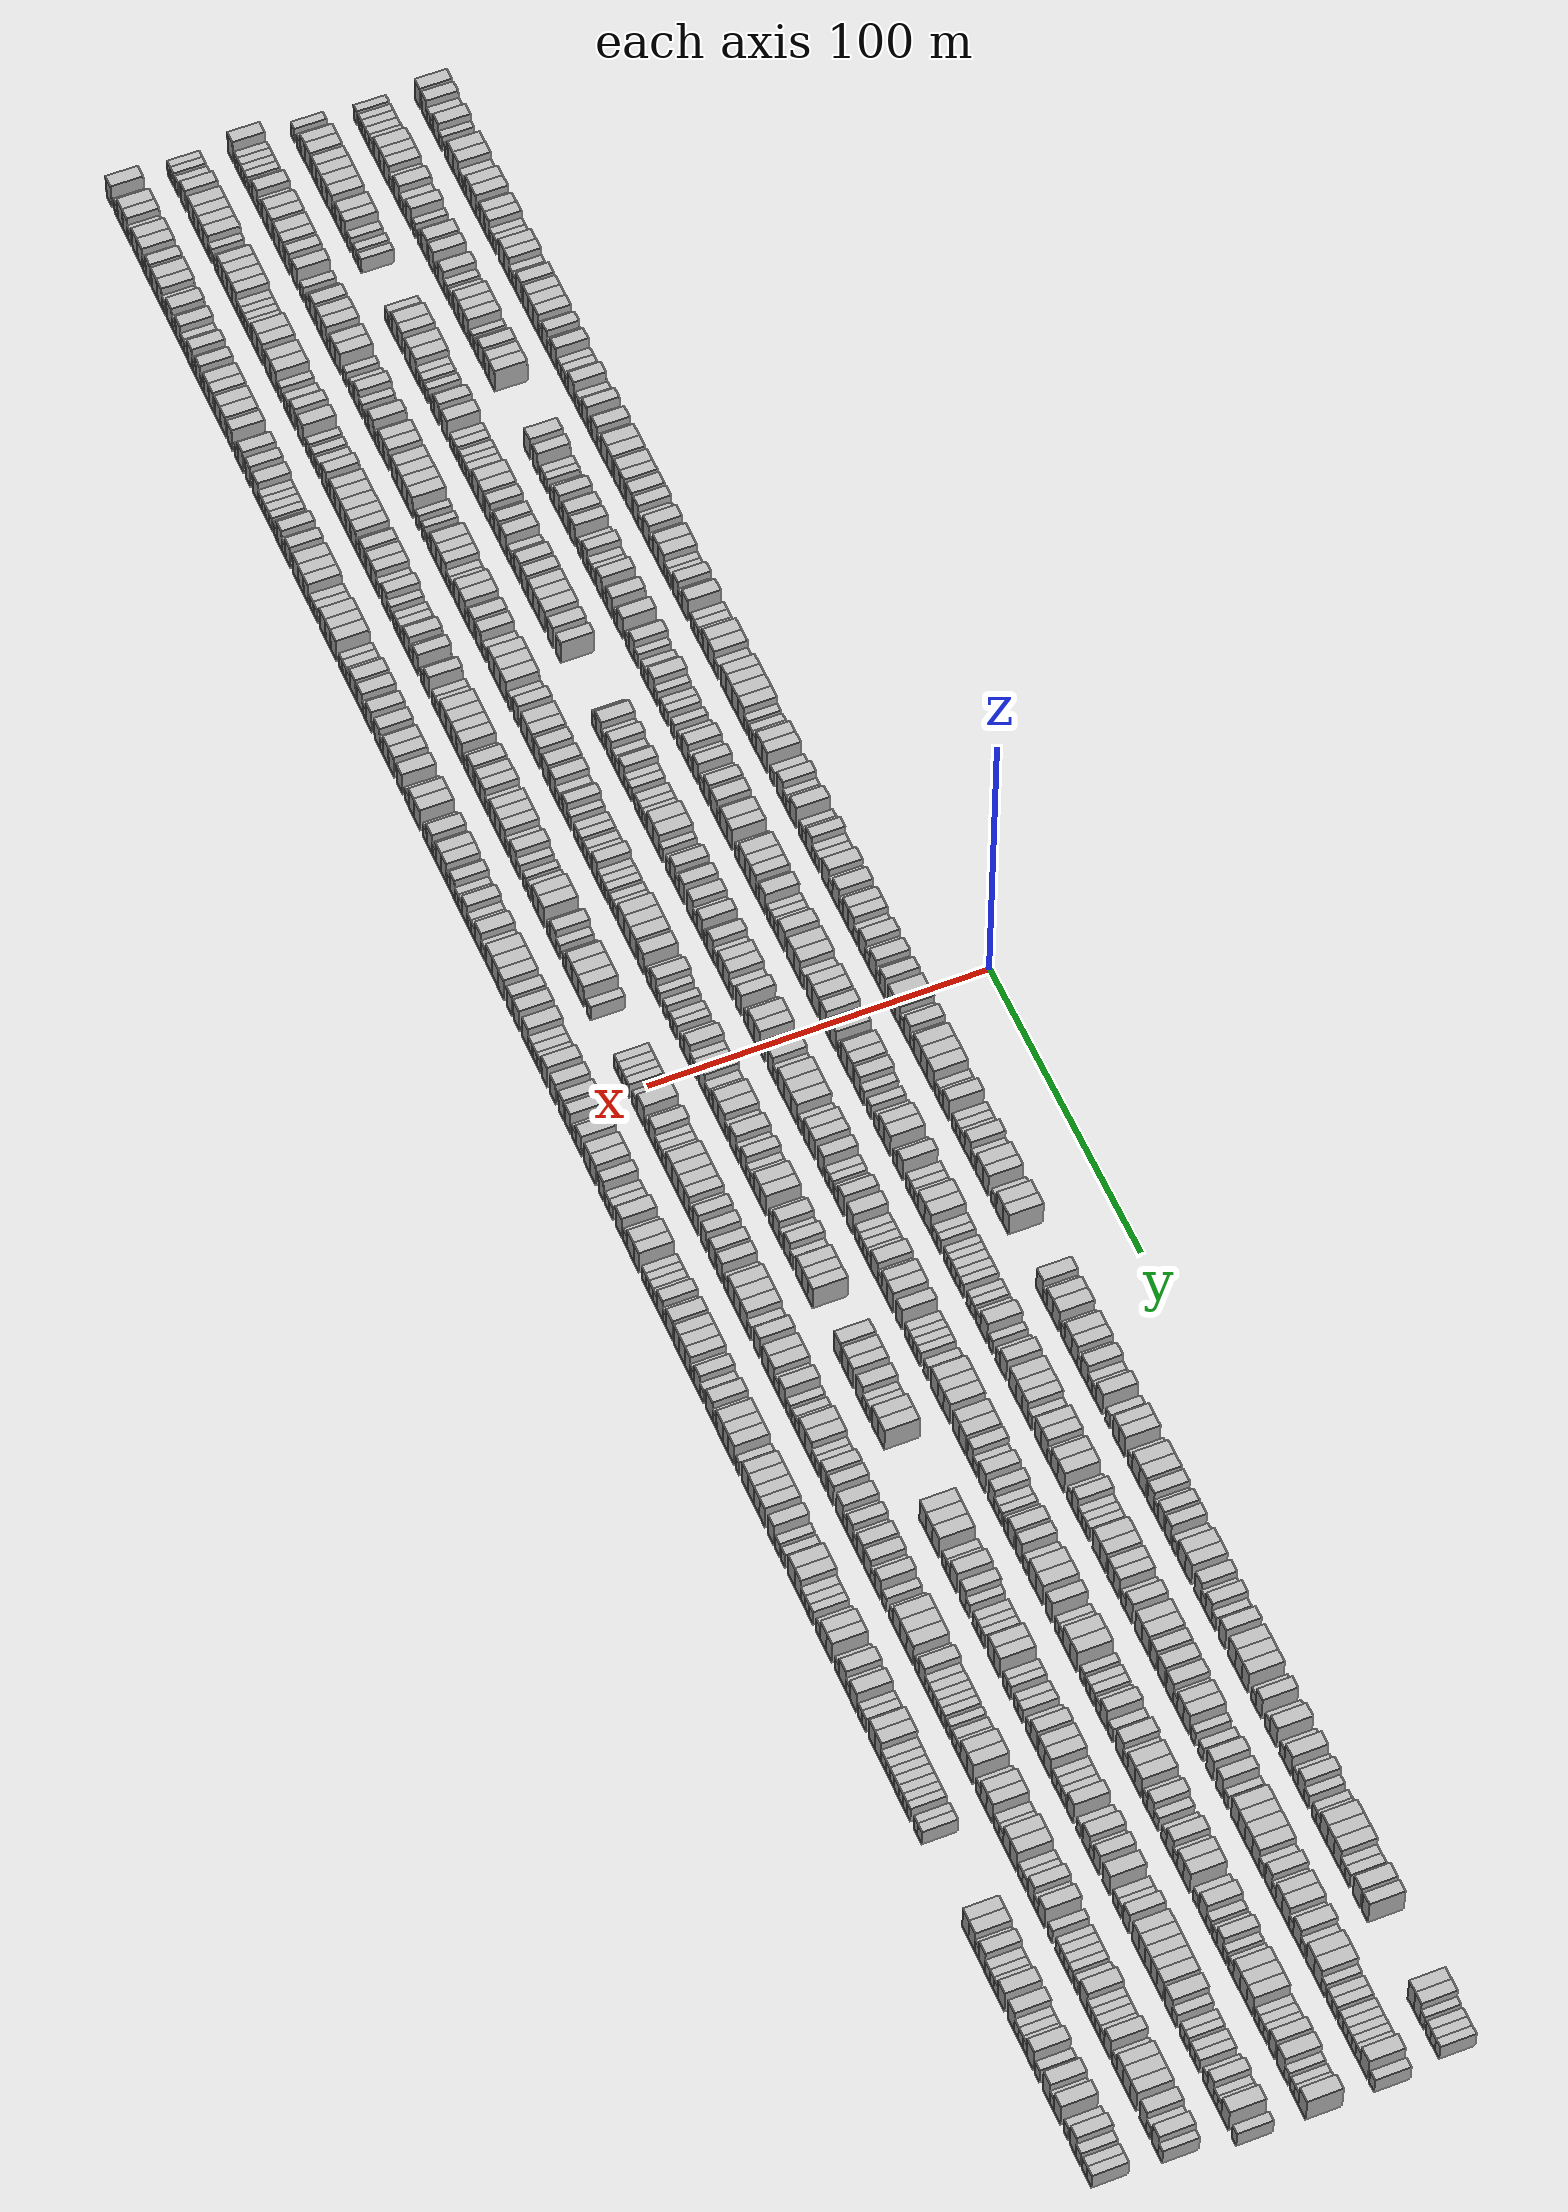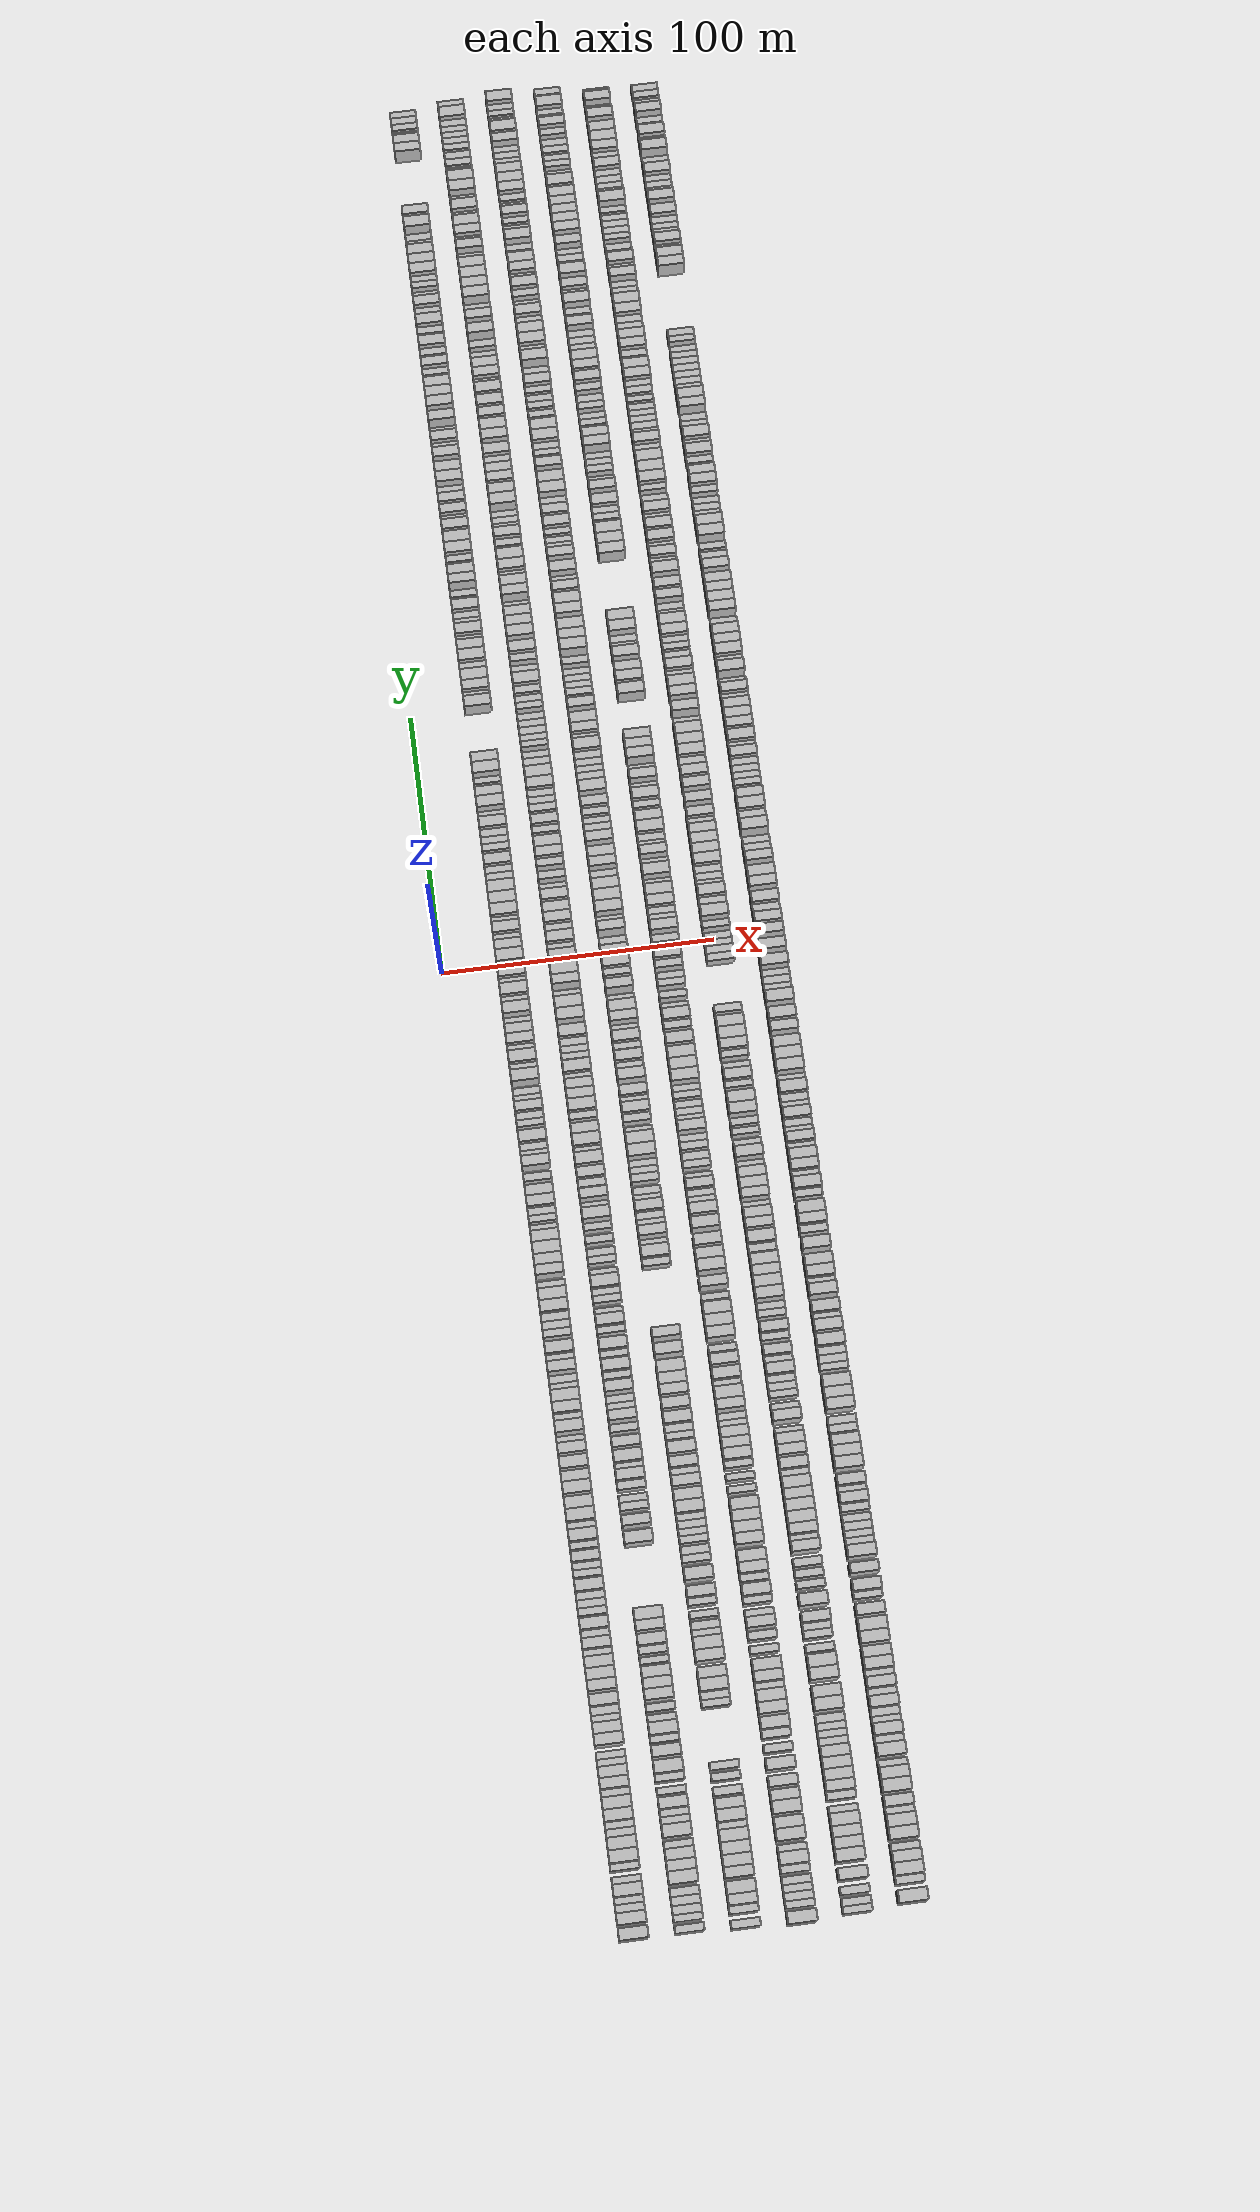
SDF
<sdf version="1.6">
 <world name="default">
  <scene>
   <sky><clouds><speed>12</speed></clouds></sky>
   <ambient>0.4 0.4 0.4 1</ambient>
   <background>0.7 0.7 0.7 1</background>
   <shadows>1</shadows>
  </scene>
  <gravity>0 0 -9.8066</gravity>
  <magnetic_field>6e-06 2.3e-05 -4.2e-05</magnetic_field>
  <physics default="0" name="default_physics" type="ode">
   <ode>
    <solver>
     <type>quick</type>
     <iters>10</iters>
     <sor>1.0</sor>
     <use_dynamic_moi_rescaling>0</use_dynamic_moi_rescaling>
    </solver>
    <constraints>
     <cfm>0</cfm>
     <erp>0.2</erp>
     <contact_max_correcting_vel>100</contact_max_correcting_vel>
     <contact_surface_layer>0.001</contact_surface_layer>
    </constraints>
   </ode>
   <max_step_size>0.004</max_step_size>
   <real_time_factor>1</real_time_factor>
   <real_time_update_rate>250</real_time_update_rate>
  </physics>
  <light name="sun" type="directional">
   <pose>0 0 10 0 0 0</pose>
   <diffuse>0.8 0.8 0.8 1</diffuse>
   <specular>0.2 0.2 0.2 1</specular>
   <attenuation>
    <range>1000</range>
    <constant>0.9</constant>
    <linear>0.01</linear>
    <quadratic>0.001</quadratic>
   </attenuation>
   <direction>-0.5 0.1 -0.9</direction>
  </light>
  <model name="building_1">
   <static>1</static>
   <pose>25.0000 -345.9522 0 0.000000 0.000000 0.000000</pose>
   <link name="link">
    <pose>0 0 4.50 0 0 0</pose>
    <collision name="collision"><geometry><box><size>10.0000 4.0957 9.0000</size></box></geometry></collision>
    <visual name="visual">
     <cast_shadows>0</cast_shadows>
     <geometry><box><size>10.0000 4.0957 9.0000</size></box></geometry>
     <material>
      <script>
       <uri>model://HANNAS_wall/materials/scripts</uri>
       <uri>model://HANNAS_wall/materials/textures</uri>
       <name>vrc/HANNAS_wall</name>
      </script>
     </material>
    </visual>
   </link>
  </model>
  <model name="building_2">
   <static>1</static>
   <pose>25.0000 -340.9280 0 0.000000 0.000000 0.000000</pose>
   <link name="link">
    <pose>0 0 4.50 0 0 0</pose>
    <collision name="collision"><geometry><box><size>10.0000 3.9526 9.0000</size></box></geometry></collision>
    <visual name="visual">
     <cast_shadows>0</cast_shadows>
     <geometry><box><size>10.0000 3.9526 9.0000</size></box></geometry>
     <material>
      <script>
       <uri>model://HANNAS_wall/materials/scripts</uri>
       <uri>model://HANNAS_wall/materials/textures</uri>
       <name>vrc/HANNAS_wall</name>
      </script>
     </material>
    </visual>
   </link>
  </model>
  <model name="building_3">
   <static>1</static>
   <pose>25.0000 -337.5009 0 0.000000 0.000000 0.000000</pose>
   <link name="link">
    <pose>0 0 3.00 0 0 0</pose>
    <collision name="collision"><geometry><box><size>10.0000 2.9018 6.0000</size></box></geometry></collision>
    <visual name="visual">
     <cast_shadows>0</cast_shadows>
     <geometry><box><size>10.0000 2.9018 6.0000</size></box></geometry>
     <material>
      <script>
       <uri>model://HANNAS_wall/materials/scripts</uri>
       <uri>model://HANNAS_wall/materials/textures</uri>
       <name>vrc/HANNAS_wall</name>
      </script>
     </material>
    </visual>
   </link>
  </model>
  <model name="building_4">
   <static>1</static>
   <pose>25.0000 -334.8481 0 0.000000 0.000000 0.000000</pose>
   <link name="link">
    <pose>0 0 3.00 0 0 0</pose>
    <collision name="collision"><geometry><box><size>10.0000 2.4036 6.0000</size></box></geometry></collision>
    <visual name="visual">
     <cast_shadows>0</cast_shadows>
     <geometry><box><size>10.0000 2.4036 6.0000</size></box></geometry>
     <material>
      <script>
       <uri>model://HANNAS_wall/materials/scripts</uri>
       <uri>model://HANNAS_wall/materials/textures</uri>
       <name>vrc/HANNAS_wall</name>
      </script>
     </material>
    </visual>
   </link>
  </model>
  <model name="building_5">
   <static>1</static>
   <pose>25.0000 -331.5470 0 0.000000 0.000000 0.000000</pose>
   <link name="link">
    <pose>0 0 4.50 0 0 0</pose>
    <collision name="collision"><geometry><box><size>10.0000 4.1985 9.0000</size></box></geometry></collision>
    <visual name="visual">
     <cast_shadows>0</cast_shadows>
     <geometry><box><size>10.0000 4.1985 9.0000</size></box></geometry>
     <material>
      <script>
       <uri>model://HANNAS_wall/materials/scripts</uri>
       <uri>model://HANNAS_wall/materials/textures</uri>
       <name>vrc/HANNAS_wall</name>
      </script>
     </material>
    </visual>
   </link>
  </model>
  <model name="building_6">
   <static>1</static>
   <pose>25.0000 -328.1808 0 0.000000 0.000000 0.000000</pose>
   <link name="link">
    <pose>0 0 3.00 0 0 0</pose>
    <collision name="collision"><geometry><box><size>10.0000 2.5340 6.0000</size></box></geometry></collision>
    <visual name="visual">
     <cast_shadows>0</cast_shadows>
     <geometry><box><size>10.0000 2.5340 6.0000</size></box></geometry>
     <material>
      <script>
       <uri>model://HANNAS_wall/materials/scripts</uri>
       <uri>model://HANNAS_wall/materials/textures</uri>
       <name>vrc/HANNAS_wall</name>
      </script>
     </material>
    </visual>
   </link>
  </model>
  <model name="building_7">
   <static>1</static>
   <pose>25.0000 -323.6865 0 0.000000 0.000000 0.000000</pose>
   <link name="link">
    <pose>0 0 3.00 0 0 0</pose>
    <collision name="collision"><geometry><box><size>10.0000 2.4546 6.0000</size></box></geometry></collision>
    <visual name="visual">
     <cast_shadows>0</cast_shadows>
     <geometry><box><size>10.0000 2.4546 6.0000</size></box></geometry>
     <material>
      <script>
       <uri>model://HANNAS_wall/materials/scripts</uri>
       <uri>model://HANNAS_wall/materials/textures</uri>
       <name>vrc/HANNAS_wall</name>
      </script>
     </material>
    </visual>
   </link>
  </model>
  <model name="building_8">
   <static>1</static>
   <pose>25.0000 -320.2829 0 0.000000 0.000000 0.000000</pose>
   <link name="link">
    <pose>0 0 4.50 0 0 0</pose>
    <collision name="collision"><geometry><box><size>10.0000 4.3526 9.0000</size></box></geometry></collision>
    <visual name="visual">
     <cast_shadows>0</cast_shadows>
     <geometry><box><size>10.0000 4.3526 9.0000</size></box></geometry>
     <material>
      <script>
       <uri>model://HANNAS_wall/materials/scripts</uri>
       <uri>model://HANNAS_wall/materials/textures</uri>
       <name>vrc/HANNAS_wall</name>
      </script>
     </material>
    </visual>
   </link>
  </model>
  <model name="building_9">
   <static>1</static>
   <pose>25.0000 -316.0000 0 0.000000 0.000000 0.000000</pose>
   <link name="link">
    <pose>0 0 4.50 0 0 0</pose>
    <collision name="collision"><geometry><box><size>10.0000 4.2131 9.0000</size></box></geometry></collision>
    <visual name="visual">
     <cast_shadows>0</cast_shadows>
     <geometry><box><size>10.0000 4.2131 9.0000</size></box></geometry>
     <material>
      <script>
       <uri>model://HANNAS_wall/materials/scripts</uri>
       <uri>model://HANNAS_wall/materials/textures</uri>
       <name>vrc/HANNAS_wall</name>
      </script>
     </material>
    </visual>
   </link>
  </model>
  <model name="building_10">
   <static>1</static>
   <pose>25.0000 -312.4239 0 0.000000 0.000000 0.000000</pose>
   <link name="link">
    <pose>0 0 3.00 0 0 0</pose>
    <collision name="collision"><geometry><box><size>10.0000 2.9391 6.0000</size></box></geometry></collision>
    <visual name="visual">
     <cast_shadows>0</cast_shadows>
     <geometry><box><size>10.0000 2.9391 6.0000</size></box></geometry>
     <material>
      <script>
       <uri>model://HANNAS_wall/materials/scripts</uri>
       <uri>model://HANNAS_wall/materials/textures</uri>
       <name>vrc/HANNAS_wall</name>
      </script>
     </material>
    </visual>
   </link>
  </model>
  <model name="building_11">
   <static>1</static>
   <pose>25.0000 -309.7540 0 0.000000 0.000000 0.000000</pose>
   <link name="link">
    <pose>0 0 3.00 0 0 0</pose>
    <collision name="collision"><geometry><box><size>10.0000 2.4007 6.0000</size></box></geometry></collision>
    <visual name="visual">
     <cast_shadows>0</cast_shadows>
     <geometry><box><size>10.0000 2.4007 6.0000</size></box></geometry>
     <material>
      <script>
       <uri>model://HANNAS_wall/materials/scripts</uri>
       <uri>model://HANNAS_wall/materials/textures</uri>
       <name>vrc/HANNAS_wall</name>
      </script>
     </material>
    </visual>
   </link>
  </model>
  <model name="building_12">
   <static>1</static>
   <pose>25.0000 -306.5531 0 0.000000 0.000000 0.000000</pose>
   <link name="link">
    <pose>0 0 4.50 0 0 0</pose>
    <collision name="collision"><geometry><box><size>10.0000 4.0011 9.0000</size></box></geometry></collision>
    <visual name="visual">
     <cast_shadows>0</cast_shadows>
     <geometry><box><size>10.0000 4.0011 9.0000</size></box></geometry>
     <material>
      <script>
       <uri>model://HANNAS_wall/materials/scripts</uri>
       <uri>model://HANNAS_wall/materials/textures</uri>
       <name>vrc/HANNAS_wall</name>
      </script>
     </material>
    </visual>
   </link>
  </model>
  <model name="building_13">
   <static>1</static>
   <pose>25.0000 -302.4807 0 0.000000 0.000000 0.000000</pose>
   <link name="link">
    <pose>0 0 4.50 0 0 0</pose>
    <collision name="collision"><geometry><box><size>10.0000 4.1436 9.0000</size></box></geometry></collision>
    <visual name="visual">
     <cast_shadows>0</cast_shadows>
     <geometry><box><size>10.0000 4.1436 9.0000</size></box></geometry>
     <material>
      <script>
       <uri>model://HANNAS_wall/materials/scripts</uri>
       <uri>model://HANNAS_wall/materials/textures</uri>
       <name>vrc/HANNAS_wall</name>
      </script>
     </material>
    </visual>
   </link>
  </model>
  <model name="building_14">
   <static>1</static>
   <pose>25.0000 -299.0259 0 0.000000 0.000000 0.000000</pose>
   <link name="link">
    <pose>0 0 3.00 0 0 0</pose>
    <collision name="collision"><geometry><box><size>10.0000 2.7659 6.0000</size></box></geometry></collision>
    <visual name="visual">
     <cast_shadows>0</cast_shadows>
     <geometry><box><size>10.0000 2.7659 6.0000</size></box></geometry>
     <material>
      <script>
       <uri>model://HANNAS_wall/materials/scripts</uri>
       <uri>model://HANNAS_wall/materials/textures</uri>
       <name>vrc/HANNAS_wall</name>
      </script>
     </material>
    </visual>
   </link>
  </model>
  <model name="building_15">
   <static>1</static>
   <pose>25.0000 -295.7829 0 0.000000 0.000000 0.000000</pose>
   <link name="link">
    <pose>0 0 4.50 0 0 0</pose>
    <collision name="collision"><geometry><box><size>10.0000 3.7201 9.0000</size></box></geometry></collision>
    <visual name="visual">
     <cast_shadows>0</cast_shadows>
     <geometry><box><size>10.0000 3.7201 9.0000</size></box></geometry>
     <material>
      <script>
       <uri>model://HANNAS_wall/materials/scripts</uri>
       <uri>model://HANNAS_wall/materials/textures</uri>
       <name>vrc/HANNAS_wall</name>
      </script>
     </material>
    </visual>
   </link>
  </model>
  <model name="building_16">
   <static>1</static>
   <pose>25.0000 -292.0326 0 0.000000 0.000000 0.000000</pose>
   <link name="link">
    <pose>0 0 4.50 0 0 0</pose>
    <collision name="collision"><geometry><box><size>10.0000 3.7806 9.0000</size></box></geometry></collision>
    <visual name="visual">
     <cast_shadows>0</cast_shadows>
     <geometry><box><size>10.0000 3.7806 9.0000</size></box></geometry>
     <material>
      <script>
       <uri>model://HANNAS_wall/materials/scripts</uri>
       <uri>model://HANNAS_wall/materials/textures</uri>
       <name>vrc/HANNAS_wall</name>
      </script>
     </material>
    </visual>
   </link>
  </model>
  <model name="building_17">
   <static>1</static>
   <pose>25.0000 -288.7904 0 0.000000 0.000000 0.000000</pose>
   <link name="link">
    <pose>0 0 3.00 0 0 0</pose>
    <collision name="collision"><geometry><box><size>10.0000 2.7039 6.0000</size></box></geometry></collision>
    <visual name="visual">
     <cast_shadows>0</cast_shadows>
     <geometry><box><size>10.0000 2.7039 6.0000</size></box></geometry>
     <material>
      <script>
       <uri>model://HANNAS_wall/materials/scripts</uri>
       <uri>model://HANNAS_wall/materials/textures</uri>
       <name>vrc/HANNAS_wall</name>
      </script>
     </material>
    </visual>
   </link>
  </model>
  <model name="building_18">
   <static>1</static>
   <pose>25.0000 -286.2109 0 0.000000 0.000000 0.000000</pose>
   <link name="link">
    <pose>0 0 3.00 0 0 0</pose>
    <collision name="collision"><geometry><box><size>10.0000 2.4550 6.0000</size></box></geometry></collision>
    <visual name="visual">
     <cast_shadows>0</cast_shadows>
     <geometry><box><size>10.0000 2.4550 6.0000</size></box></geometry>
     <material>
      <script>
       <uri>model://HANNAS_wall/materials/scripts</uri>
       <uri>model://HANNAS_wall/materials/textures</uri>
       <name>vrc/HANNAS_wall</name>
      </script>
     </material>
    </visual>
   </link>
  </model>
  <model name="building_19">
   <static>1</static>
   <pose>25.0000 -281.0033 0 0.000000 0.000000 0.000000</pose>
   <link name="link">
    <pose>0 0 4.50 0 0 0</pose>
    <collision name="collision"><geometry><box><size>10.0000 3.9601 9.0000</size></box></geometry></collision>
    <visual name="visual">
     <cast_shadows>0</cast_shadows>
     <geometry><box><size>10.0000 3.9601 9.0000</size></box></geometry>
     <material>
      <script>
       <uri>model://HANNAS_wall/materials/scripts</uri>
       <uri>model://HANNAS_wall/materials/textures</uri>
       <name>vrc/HANNAS_wall</name>
      </script>
     </material>
    </visual>
   </link>
  </model>
  <model name="building_20">
   <static>1</static>
   <pose>25.0000 -277.1135 0 0.000000 0.000000 0.000000</pose>
   <link name="link">
    <pose>0 0 4.50 0 0 0</pose>
    <collision name="collision"><geometry><box><size>10.0000 3.8196 9.0000</size></box></geometry></collision>
    <visual name="visual">
     <cast_shadows>0</cast_shadows>
     <geometry><box><size>10.0000 3.8196 9.0000</size></box></geometry>
     <material>
      <script>
       <uri>model://HANNAS_wall/materials/scripts</uri>
       <uri>model://HANNAS_wall/materials/textures</uri>
       <name>vrc/HANNAS_wall</name>
      </script>
     </material>
    </visual>
   </link>
  </model>
  <model name="building_21">
   <static>1</static>
   <pose>25.0000 -273.8950 0 0.000000 0.000000 0.000000</pose>
   <link name="link">
    <pose>0 0 3.00 0 0 0</pose>
    <collision name="collision"><geometry><box><size>10.0000 2.6172 6.0000</size></box></geometry></collision>
    <visual name="visual">
     <cast_shadows>0</cast_shadows>
     <geometry><box><size>10.0000 2.6172 6.0000</size></box></geometry>
     <material>
      <script>
       <uri>model://HANNAS_wall/materials/scripts</uri>
       <uri>model://HANNAS_wall/materials/textures</uri>
       <name>vrc/HANNAS_wall</name>
      </script>
     </material>
    </visual>
   </link>
  </model>
  <model name="building_22">
   <static>1</static>
   <pose>25.0000 -271.1016 0 0.000000 0.000000 0.000000</pose>
   <link name="link">
    <pose>0 0 3.00 0 0 0</pose>
    <collision name="collision"><geometry><box><size>10.0000 2.9697 6.0000</size></box></geometry></collision>
    <visual name="visual">
     <cast_shadows>0</cast_shadows>
     <geometry><box><size>10.0000 2.9697 6.0000</size></box></geometry>
     <material>
      <script>
       <uri>model://HANNAS_wall/materials/scripts</uri>
       <uri>model://HANNAS_wall/materials/textures</uri>
       <name>vrc/HANNAS_wall</name>
      </script>
     </material>
    </visual>
   </link>
  </model>
  <model name="building_23">
   <static>1</static>
   <pose>25.0000 -267.5623 0 0.000000 0.000000 0.000000</pose>
   <link name="link">
    <pose>0 0 4.50 0 0 0</pose>
    <collision name="collision"><geometry><box><size>10.0000 4.1090 9.0000</size></box></geometry></collision>
    <visual name="visual">
     <cast_shadows>0</cast_shadows>
     <geometry><box><size>10.0000 4.1090 9.0000</size></box></geometry>
     <material>
      <script>
       <uri>model://HANNAS_wall/materials/scripts</uri>
       <uri>model://HANNAS_wall/materials/textures</uri>
       <name>vrc/HANNAS_wall</name>
      </script>
     </material>
    </visual>
   </link>
  </model>
  <model name="building_24">
   <static>1</static>
   <pose>25.0000 -262.6042 0 0.000000 0.000000 0.000000</pose>
   <link name="link">
    <pose>0 0 4.50 0 0 0</pose>
    <collision name="collision"><geometry><box><size>10.0000 3.8071 9.0000</size></box></geometry></collision>
    <visual name="visual">
     <cast_shadows>0</cast_shadows>
     <geometry><box><size>10.0000 3.8071 9.0000</size></box></geometry>
     <material>
      <script>
       <uri>model://HANNAS_wall/materials/scripts</uri>
       <uri>model://HANNAS_wall/materials/textures</uri>
       <name>vrc/HANNAS_wall</name>
      </script>
     </material>
    </visual>
   </link>
  </model>
  <model name="building_25">
   <static>1</static>
   <pose>25.0000 -258.6718 0 0.000000 0.000000 0.000000</pose>
   <link name="link">
    <pose>0 0 4.50 0 0 0</pose>
    <collision name="collision"><geometry><box><size>10.0000 4.0578 9.0000</size></box></geometry></collision>
    <visual name="visual">
     <cast_shadows>0</cast_shadows>
     <geometry><box><size>10.0000 4.0578 9.0000</size></box></geometry>
     <material>
      <script>
       <uri>model://HANNAS_wall/materials/scripts</uri>
       <uri>model://HANNAS_wall/materials/textures</uri>
       <name>vrc/HANNAS_wall</name>
      </script>
     </material>
    </visual>
   </link>
  </model>
  <model name="building_26">
   <static>1</static>
   <pose>25.0000 -254.6592 0 0.000000 0.000000 0.000000</pose>
   <link name="link">
    <pose>0 0 4.50 0 0 0</pose>
    <collision name="collision"><geometry><box><size>10.0000 3.9673 9.0000</size></box></geometry></collision>
    <visual name="visual">
     <cast_shadows>0</cast_shadows>
     <geometry><box><size>10.0000 3.9673 9.0000</size></box></geometry>
     <material>
      <script>
       <uri>model://HANNAS_wall/materials/scripts</uri>
       <uri>model://HANNAS_wall/materials/textures</uri>
       <name>vrc/HANNAS_wall</name>
      </script>
     </material>
    </visual>
   </link>
  </model>
  <model name="building_27">
   <static>1</static>
   <pose>25.0000 -251.3607 0 0.000000 0.000000 0.000000</pose>
   <link name="link">
    <pose>0 0 3.00 0 0 0</pose>
    <collision name="collision"><geometry><box><size>10.0000 2.6298 6.0000</size></box></geometry></collision>
    <visual name="visual">
     <cast_shadows>0</cast_shadows>
     <geometry><box><size>10.0000 2.6298 6.0000</size></box></geometry>
     <material>
      <script>
       <uri>model://HANNAS_wall/materials/scripts</uri>
       <uri>model://HANNAS_wall/materials/textures</uri>
       <name>vrc/HANNAS_wall</name>
      </script>
     </material>
    </visual>
   </link>
  </model>
  <model name="building_28">
   <static>1</static>
   <pose>25.0000 -248.1810 0 0.000000 0.000000 0.000000</pose>
   <link name="link">
    <pose>0 0 4.50 0 0 0</pose>
    <collision name="collision"><geometry><box><size>10.0000 3.7296 9.0000</size></box></geometry></collision>
    <visual name="visual">
     <cast_shadows>0</cast_shadows>
     <geometry><box><size>10.0000 3.7296 9.0000</size></box></geometry>
     <material>
      <script>
       <uri>model://HANNAS_wall/materials/scripts</uri>
       <uri>model://HANNAS_wall/materials/textures</uri>
       <name>vrc/HANNAS_wall</name>
      </script>
     </material>
    </visual>
   </link>
  </model>
  <model name="building_29">
   <static>1</static>
   <pose>25.0000 -244.8584 0 0.000000 0.000000 0.000000</pose>
   <link name="link">
    <pose>0 0 3.00 0 0 0</pose>
    <collision name="collision"><geometry><box><size>10.0000 2.9156 6.0000</size></box></geometry></collision>
    <visual name="visual">
     <cast_shadows>0</cast_shadows>
     <geometry><box><size>10.0000 2.9156 6.0000</size></box></geometry>
     <material>
      <script>
       <uri>model://HANNAS_wall/materials/scripts</uri>
       <uri>model://HANNAS_wall/materials/textures</uri>
       <name>vrc/HANNAS_wall</name>
      </script>
     </material>
    </visual>
   </link>
  </model>
  <model name="building_30">
   <static>1</static>
   <pose>25.0000 -241.3975 0 0.000000 0.000000 0.000000</pose>
   <link name="link">
    <pose>0 0 4.50 0 0 0</pose>
    <collision name="collision"><geometry><box><size>10.0000 4.0063 9.0000</size></box></geometry></collision>
    <visual name="visual">
     <cast_shadows>0</cast_shadows>
     <geometry><box><size>10.0000 4.0063 9.0000</size></box></geometry>
     <material>
      <script>
       <uri>model://HANNAS_wall/materials/scripts</uri>
       <uri>model://HANNAS_wall/materials/textures</uri>
       <name>vrc/HANNAS_wall</name>
      </script>
     </material>
    </visual>
   </link>
  </model>
  <model name="building_31">
   <static>1</static>
   <pose>25.0000 -237.0428 0 0.000000 0.000000 0.000000</pose>
   <link name="link">
    <pose>0 0 3.00 0 0 0</pose>
    <collision name="collision"><geometry><box><size>10.0000 2.7030 6.0000</size></box></geometry></collision>
    <visual name="visual">
     <cast_shadows>0</cast_shadows>
     <geometry><box><size>10.0000 2.7030 6.0000</size></box></geometry>
     <material>
      <script>
       <uri>model://HANNAS_wall/materials/scripts</uri>
       <uri>model://HANNAS_wall/materials/textures</uri>
       <name>vrc/HANNAS_wall</name>
      </script>
     </material>
    </visual>
   </link>
  </model>
  <model name="building_32">
   <static>1</static>
   <pose>25.0000 -234.2940 0 0.000000 0.000000 0.000000</pose>
   <link name="link">
    <pose>0 0 3.00 0 0 0</pose>
    <collision name="collision"><geometry><box><size>10.0000 2.7945 6.0000</size></box></geometry></collision>
    <visual name="visual">
     <cast_shadows>0</cast_shadows>
     <geometry><box><size>10.0000 2.7945 6.0000</size></box></geometry>
     <material>
      <script>
       <uri>model://HANNAS_wall/materials/scripts</uri>
       <uri>model://HANNAS_wall/materials/textures</uri>
       <name>vrc/HANNAS_wall</name>
      </script>
     </material>
    </visual>
   </link>
  </model>
  <model name="building_33">
   <static>1</static>
   <pose>25.0000 -231.5453 0 0.000000 0.000000 0.000000</pose>
   <link name="link">
    <pose>0 0 3.00 0 0 0</pose>
    <collision name="collision"><geometry><box><size>10.0000 2.7030 6.0000</size></box></geometry></collision>
    <visual name="visual">
     <cast_shadows>0</cast_shadows>
     <geometry><box><size>10.0000 2.7030 6.0000</size></box></geometry>
     <material>
      <script>
       <uri>model://HANNAS_wall/materials/scripts</uri>
       <uri>model://HANNAS_wall/materials/textures</uri>
       <name>vrc/HANNAS_wall</name>
      </script>
     </material>
    </visual>
   </link>
  </model>
  <model name="building_34">
   <static>1</static>
   <pose>25.0000 -228.1290 0 0.000000 0.000000 0.000000</pose>
   <link name="link">
    <pose>0 0 4.50 0 0 0</pose>
    <collision name="collision"><geometry><box><size>10.0000 4.1295 9.0000</size></box></geometry></collision>
    <visual name="visual">
     <cast_shadows>0</cast_shadows>
     <geometry><box><size>10.0000 4.1295 9.0000</size></box></geometry>
     <material>
      <script>
       <uri>model://HANNAS_wall/materials/scripts</uri>
       <uri>model://HANNAS_wall/materials/textures</uri>
       <name>vrc/HANNAS_wall</name>
      </script>
     </material>
    </visual>
   </link>
  </model>
  <model name="building_35">
   <static>1</static>
   <pose>25.0000 -223.7657 0 0.000000 0.000000 0.000000</pose>
   <link name="link">
    <pose>0 0 3.00 0 0 0</pose>
    <collision name="collision"><geometry><box><size>10.0000 2.5970 6.0000</size></box></geometry></collision>
    <visual name="visual">
     <cast_shadows>0</cast_shadows>
     <geometry><box><size>10.0000 2.5970 6.0000</size></box></geometry>
     <material>
      <script>
       <uri>model://HANNAS_wall/materials/scripts</uri>
       <uri>model://HANNAS_wall/materials/textures</uri>
       <name>vrc/HANNAS_wall</name>
      </script>
     </material>
    </visual>
   </link>
  </model>
  <model name="building_36">
   <static>1</static>
   <pose>25.0000 -221.1965 0 0.000000 0.000000 0.000000</pose>
   <link name="link">
    <pose>0 0 3.00 0 0 0</pose>
    <collision name="collision"><geometry><box><size>10.0000 2.5414 6.0000</size></box></geometry></collision>
    <visual name="visual">
     <cast_shadows>0</cast_shadows>
     <geometry><box><size>10.0000 2.5414 6.0000</size></box></geometry>
     <material>
      <script>
       <uri>model://HANNAS_wall/materials/scripts</uri>
       <uri>model://HANNAS_wall/materials/textures</uri>
       <name>vrc/HANNAS_wall</name>
      </script>
     </material>
    </visual>
   </link>
  </model>
  <model name="building_37">
   <static>1</static>
   <pose>25.0000 -218.1152 0 0.000000 0.000000 0.000000</pose>
   <link name="link">
    <pose>0 0 4.50 0 0 0</pose>
    <collision name="collision"><geometry><box><size>10.0000 3.6212 9.0000</size></box></geometry></collision>
    <visual name="visual">
     <cast_shadows>0</cast_shadows>
     <geometry><box><size>10.0000 3.6212 9.0000</size></box></geometry>
     <material>
      <script>
       <uri>model://HANNAS_wall/materials/scripts</uri>
       <uri>model://HANNAS_wall/materials/textures</uri>
       <name>vrc/HANNAS_wall</name>
      </script>
     </material>
    </visual>
   </link>
  </model>
  <model name="building_38">
   <static>1</static>
   <pose>25.0000 -214.0465 0 0.000000 0.000000 0.000000</pose>
   <link name="link">
    <pose>0 0 3.00 0 0 0</pose>
    <collision name="collision"><geometry><box><size>10.0000 2.5162 6.0000</size></box></geometry></collision>
    <visual name="visual">
     <cast_shadows>0</cast_shadows>
     <geometry><box><size>10.0000 2.5162 6.0000</size></box></geometry>
     <material>
      <script>
       <uri>model://HANNAS_wall/materials/scripts</uri>
       <uri>model://HANNAS_wall/materials/textures</uri>
       <name>vrc/HANNAS_wall</name>
      </script>
     </material>
    </visual>
   </link>
  </model>
  <model name="building_39">
   <static>1</static>
   <pose>25.0000 -210.6895 0 0.000000 0.000000 0.000000</pose>
   <link name="link">
    <pose>0 0 4.50 0 0 0</pose>
    <collision name="collision"><geometry><box><size>10.0000 4.1977 9.0000</size></box></geometry></collision>
    <visual name="visual">
     <cast_shadows>0</cast_shadows>
     <geometry><box><size>10.0000 4.1977 9.0000</size></box></geometry>
     <material>
      <script>
       <uri>model://HANNAS_wall/materials/scripts</uri>
       <uri>model://HANNAS_wall/materials/textures</uri>
       <name>vrc/HANNAS_wall</name>
      </script>
     </material>
    </visual>
   </link>
  </model>
  <model name="building_40">
   <static>1</static>
   <pose>25.0000 -207.2130 0 0.000000 0.000000 0.000000</pose>
   <link name="link">
    <pose>0 0 3.00 0 0 0</pose>
    <collision name="collision"><geometry><box><size>10.0000 2.7553 6.0000</size></box></geometry></collision>
    <visual name="visual">
     <cast_shadows>0</cast_shadows>
     <geometry><box><size>10.0000 2.7553 6.0000</size></box></geometry>
     <material>
      <script>
       <uri>model://HANNAS_wall/materials/scripts</uri>
       <uri>model://HANNAS_wall/materials/textures</uri>
       <name>vrc/HANNAS_wall</name>
      </script>
     </material>
    </visual>
   </link>
  </model>
  <model name="building_41">
   <static>1</static>
   <pose>25.0000 -203.6301 0 0.000000 0.000000 0.000000</pose>
   <link name="link">
    <pose>0 0 4.50 0 0 0</pose>
    <collision name="collision"><geometry><box><size>10.0000 4.4104 9.0000</size></box></geometry></collision>
    <visual name="visual">
     <cast_shadows>0</cast_shadows>
     <geometry><box><size>10.0000 4.4104 9.0000</size></box></geometry>
     <material>
      <script>
       <uri>model://HANNAS_wall/materials/scripts</uri>
       <uri>model://HANNAS_wall/materials/textures</uri>
       <name>vrc/HANNAS_wall</name>
      </script>
     </material>
    </visual>
   </link>
  </model>
  <model name="building_42">
   <static>1</static>
   <pose>25.0000 -199.2890 0 0.000000 0.000000 0.000000</pose>
   <link name="link">
    <pose>0 0 4.50 0 0 0</pose>
    <collision name="collision"><geometry><box><size>10.0000 4.2719 9.0000</size></box></geometry></collision>
    <visual name="visual">
     <cast_shadows>0</cast_shadows>
     <geometry><box><size>10.0000 4.2719 9.0000</size></box></geometry>
     <material>
      <script>
       <uri>model://HANNAS_wall/materials/scripts</uri>
       <uri>model://HANNAS_wall/materials/textures</uri>
       <name>vrc/HANNAS_wall</name>
      </script>
     </material>
    </visual>
   </link>
  </model>
  <model name="building_43">
   <static>1</static>
   <pose>25.0000 -194.0000 0 0.000000 0.000000 0.000000</pose>
   <link name="link">
    <pose>0 0 4.50 0 0 0</pose>
    <collision name="collision"><geometry><box><size>10.0000 4.3061 9.0000</size></box></geometry></collision>
    <visual name="visual">
     <cast_shadows>0</cast_shadows>
     <geometry><box><size>10.0000 4.3061 9.0000</size></box></geometry>
     <material>
      <script>
       <uri>model://HANNAS_wall/materials/scripts</uri>
       <uri>model://HANNAS_wall/materials/textures</uri>
       <name>vrc/HANNAS_wall</name>
      </script>
     </material>
    </visual>
   </link>
  </model>
  <model name="building_44">
   <static>1</static>
   <pose>25.0000 -190.0190 0 0.000000 0.000000 0.000000</pose>
   <link name="link">
    <pose>0 0 4.50 0 0 0</pose>
    <collision name="collision"><geometry><box><size>10.0000 3.6559 9.0000</size></box></geometry></collision>
    <visual name="visual">
     <cast_shadows>0</cast_shadows>
     <geometry><box><size>10.0000 3.6559 9.0000</size></box></geometry>
     <material>
      <script>
       <uri>model://HANNAS_wall/materials/scripts</uri>
       <uri>model://HANNAS_wall/materials/textures</uri>
       <name>vrc/HANNAS_wall</name>
      </script>
     </material>
    </visual>
   </link>
  </model>
  <model name="building_45">
   <static>1</static>
   <pose>25.0000 -185.0642 0 0.000000 0.000000 0.000000</pose>
   <link name="link">
    <pose>0 0 4.50 0 0 0</pose>
    <collision name="collision"><geometry><box><size>10.0000 4.2538 9.0000</size></box></geometry></collision>
    <visual name="visual">
     <cast_shadows>0</cast_shadows>
     <geometry><box><size>10.0000 4.2538 9.0000</size></box></geometry>
     <material>
      <script>
       <uri>model://HANNAS_wall/materials/scripts</uri>
       <uri>model://HANNAS_wall/materials/textures</uri>
       <name>vrc/HANNAS_wall</name>
      </script>
     </material>
    </visual>
   </link>
  </model>
  <model name="building_46">
   <static>1</static>
   <pose>25.0000 -180.0141 0 0.000000 0.000000 0.000000</pose>
   <link name="link">
    <pose>0 0 4.50 0 0 0</pose>
    <collision name="collision"><geometry><box><size>10.0000 3.8462 9.0000</size></box></geometry></collision>
    <visual name="visual">
     <cast_shadows>0</cast_shadows>
     <geometry><box><size>10.0000 3.8462 9.0000</size></box></geometry>
     <material>
      <script>
       <uri>model://HANNAS_wall/materials/scripts</uri>
       <uri>model://HANNAS_wall/materials/textures</uri>
       <name>vrc/HANNAS_wall</name>
      </script>
     </material>
    </visual>
   </link>
  </model>
  <model name="building_47">
   <static>1</static>
   <pose>25.0000 -176.7822 0 0.000000 0.000000 0.000000</pose>
   <link name="link">
    <pose>0 0 3.00 0 0 0</pose>
    <collision name="collision"><geometry><box><size>10.0000 2.6176 6.0000</size></box></geometry></collision>
    <visual name="visual">
     <cast_shadows>0</cast_shadows>
     <geometry><box><size>10.0000 2.6176 6.0000</size></box></geometry>
     <material>
      <script>
       <uri>model://HANNAS_wall/materials/scripts</uri>
       <uri>model://HANNAS_wall/materials/textures</uri>
       <name>vrc/HANNAS_wall</name>
      </script>
     </material>
    </visual>
   </link>
  </model>
  <model name="building_48">
   <static>1</static>
   <pose>25.0000 -172.3605 0 0.000000 0.000000 0.000000</pose>
   <link name="link">
    <pose>0 0 4.50 0 0 0</pose>
    <collision name="collision"><geometry><box><size>10.0000 4.2258 9.0000</size></box></geometry></collision>
    <visual name="visual">
     <cast_shadows>0</cast_shadows>
     <geometry><box><size>10.0000 4.2258 9.0000</size></box></geometry>
     <material>
      <script>
       <uri>model://HANNAS_wall/materials/scripts</uri>
       <uri>model://HANNAS_wall/materials/textures</uri>
       <name>vrc/HANNAS_wall</name>
      </script>
     </material>
    </visual>
   </link>
  </model>
  <model name="building_49">
   <static>1</static>
   <pose>25.0000 -168.8701 0 0.000000 0.000000 0.000000</pose>
   <link name="link">
    <pose>0 0 3.00 0 0 0</pose>
    <collision name="collision"><geometry><box><size>10.0000 2.7550 6.0000</size></box></geometry></collision>
    <visual name="visual">
     <cast_shadows>0</cast_shadows>
     <geometry><box><size>10.0000 2.7550 6.0000</size></box></geometry>
     <material>
      <script>
       <uri>model://HANNAS_wall/materials/scripts</uri>
       <uri>model://HANNAS_wall/materials/textures</uri>
       <name>vrc/HANNAS_wall</name>
      </script>
     </material>
    </visual>
   </link>
  </model>
  <model name="building_50">
   <static>1</static>
   <pose>25.0000 -165.5232 0 0.000000 0.000000 0.000000</pose>
   <link name="link">
    <pose>0 0 4.50 0 0 0</pose>
    <collision name="collision"><geometry><box><size>10.0000 3.9390 9.0000</size></box></geometry></collision>
    <visual name="visual">
     <cast_shadows>0</cast_shadows>
     <geometry><box><size>10.0000 3.9390 9.0000</size></box></geometry>
     <material>
      <script>
       <uri>model://HANNAS_wall/materials/scripts</uri>
       <uri>model://HANNAS_wall/materials/textures</uri>
       <name>vrc/HANNAS_wall</name>
      </script>
     </material>
    </visual>
   </link>
  </model>
  <model name="building_51">
   <static>1</static>
   <pose>25.0000 -161.3885 0 0.000000 0.000000 0.000000</pose>
   <link name="link">
    <pose>0 0 4.50 0 0 0</pose>
    <collision name="collision"><geometry><box><size>10.0000 4.3303 9.0000</size></box></geometry></collision>
    <visual name="visual">
     <cast_shadows>0</cast_shadows>
     <geometry><box><size>10.0000 4.3303 9.0000</size></box></geometry>
     <material>
      <script>
       <uri>model://HANNAS_wall/materials/scripts</uri>
       <uri>model://HANNAS_wall/materials/textures</uri>
       <name>vrc/HANNAS_wall</name>
      </script>
     </material>
    </visual>
   </link>
  </model>
  <model name="building_52">
   <static>1</static>
   <pose>25.0000 -157.9420 0 0.000000 0.000000 0.000000</pose>
   <link name="link">
    <pose>0 0 3.00 0 0 0</pose>
    <collision name="collision"><geometry><box><size>10.0000 2.5628 6.0000</size></box></geometry></collision>
    <visual name="visual">
     <cast_shadows>0</cast_shadows>
     <geometry><box><size>10.0000 2.5628 6.0000</size></box></geometry>
     <material>
      <script>
       <uri>model://HANNAS_wall/materials/scripts</uri>
       <uri>model://HANNAS_wall/materials/textures</uri>
       <name>vrc/HANNAS_wall</name>
      </script>
     </material>
    </visual>
   </link>
  </model>
  <model name="building_53">
   <static>1</static>
   <pose>25.0000 -155.2368 0 0.000000 0.000000 0.000000</pose>
   <link name="link">
    <pose>0 0 3.00 0 0 0</pose>
    <collision name="collision"><geometry><box><size>10.0000 2.8476 6.0000</size></box></geometry></collision>
    <visual name="visual">
     <cast_shadows>0</cast_shadows>
     <geometry><box><size>10.0000 2.8476 6.0000</size></box></geometry>
     <material>
      <script>
       <uri>model://HANNAS_wall/materials/scripts</uri>
       <uri>model://HANNAS_wall/materials/textures</uri>
       <name>vrc/HANNAS_wall</name>
      </script>
     </material>
    </visual>
   </link>
  </model>
  <model name="building_54">
   <static>1</static>
   <pose>25.0000 -150.8825 0 0.000000 0.000000 0.000000</pose>
   <link name="link">
    <pose>0 0 4.50 0 0 0</pose>
    <collision name="collision"><geometry><box><size>10.0000 3.8611 9.0000</size></box></geometry></collision>
    <visual name="visual">
     <cast_shadows>0</cast_shadows>
     <geometry><box><size>10.0000 3.8611 9.0000</size></box></geometry>
     <material>
      <script>
       <uri>model://HANNAS_wall/materials/scripts</uri>
       <uri>model://HANNAS_wall/materials/textures</uri>
       <name>vrc/HANNAS_wall</name>
      </script>
     </material>
    </visual>
   </link>
  </model>
  <model name="building_55">
   <static>1</static>
   <pose>25.0000 -147.5662 0 0.000000 0.000000 0.000000</pose>
   <link name="link">
    <pose>0 0 3.00 0 0 0</pose>
    <collision name="collision"><geometry><box><size>10.0000 2.7713 6.0000</size></box></geometry></collision>
    <visual name="visual">
     <cast_shadows>0</cast_shadows>
     <geometry><box><size>10.0000 2.7713 6.0000</size></box></geometry>
     <material>
      <script>
       <uri>model://HANNAS_wall/materials/scripts</uri>
       <uri>model://HANNAS_wall/materials/textures</uri>
       <name>vrc/HANNAS_wall</name>
      </script>
     </material>
    </visual>
   </link>
  </model>
  <model name="building_56">
   <static>1</static>
   <pose>25.0000 -144.0413 0 0.000000 0.000000 0.000000</pose>
   <link name="link">
    <pose>0 0 4.50 0 0 0</pose>
    <collision name="collision"><geometry><box><size>10.0000 4.2784 9.0000</size></box></geometry></collision>
    <visual name="visual">
     <cast_shadows>0</cast_shadows>
     <geometry><box><size>10.0000 4.2784 9.0000</size></box></geometry>
     <material>
      <script>
       <uri>model://HANNAS_wall/materials/scripts</uri>
       <uri>model://HANNAS_wall/materials/textures</uri>
       <name>vrc/HANNAS_wall</name>
      </script>
     </material>
    </visual>
   </link>
  </model>
  <model name="building_57">
   <static>1</static>
   <pose>25.0000 -138.5179 0 0.000000 0.000000 0.000000</pose>
   <link name="link">
    <pose>0 0 3.00 0 0 0</pose>
    <collision name="collision"><geometry><box><size>10.0000 2.7683 6.0000</size></box></geometry></collision>
    <visual name="visual">
     <cast_shadows>0</cast_shadows>
     <geometry><box><size>10.0000 2.7683 6.0000</size></box></geometry>
     <material>
      <script>
       <uri>model://HANNAS_wall/materials/scripts</uri>
       <uri>model://HANNAS_wall/materials/textures</uri>
       <name>vrc/HANNAS_wall</name>
      </script>
     </material>
    </visual>
   </link>
  </model>
  <model name="building_58">
   <static>1</static>
   <pose>25.0000 -135.6578 0 0.000000 0.000000 0.000000</pose>
   <link name="link">
    <pose>0 0 3.00 0 0 0</pose>
    <collision name="collision"><geometry><box><size>10.0000 2.9520 6.0000</size></box></geometry></collision>
    <visual name="visual">
     <cast_shadows>0</cast_shadows>
     <geometry><box><size>10.0000 2.9520 6.0000</size></box></geometry>
     <material>
      <script>
       <uri>model://HANNAS_wall/materials/scripts</uri>
       <uri>model://HANNAS_wall/materials/textures</uri>
       <name>vrc/HANNAS_wall</name>
      </script>
     </material>
    </visual>
   </link>
  </model>
  <model name="building_59">
   <static>1</static>
   <pose>25.0000 -132.6857 0 0.000000 0.000000 0.000000</pose>
   <link name="link">
    <pose>0 0 3.00 0 0 0</pose>
    <collision name="collision"><geometry><box><size>10.0000 2.9923 6.0000</size></box></geometry></collision>
    <visual name="visual">
     <cast_shadows>0</cast_shadows>
     <geometry><box><size>10.0000 2.9923 6.0000</size></box></geometry>
     <material>
      <script>
       <uri>model://HANNAS_wall/materials/scripts</uri>
       <uri>model://HANNAS_wall/materials/textures</uri>
       <name>vrc/HANNAS_wall</name>
      </script>
     </material>
    </visual>
   </link>
  </model>
  <model name="building_60">
   <static>1</static>
   <pose>25.0000 -129.0565 0 0.000000 0.000000 0.000000</pose>
   <link name="link">
    <pose>0 0 4.50 0 0 0</pose>
    <collision name="collision"><geometry><box><size>10.0000 4.2662 9.0000</size></box></geometry></collision>
    <visual name="visual">
     <cast_shadows>0</cast_shadows>
     <geometry><box><size>10.0000 4.2662 9.0000</size></box></geometry>
     <material>
      <script>
       <uri>model://HANNAS_wall/materials/scripts</uri>
       <uri>model://HANNAS_wall/materials/textures</uri>
       <name>vrc/HANNAS_wall</name>
      </script>
     </material>
    </visual>
   </link>
  </model>
  <model name="building_61">
   <static>1</static>
   <pose>25.0000 -124.8028 0 0.000000 0.000000 0.000000</pose>
   <link name="link">
    <pose>0 0 4.50 0 0 0</pose>
    <collision name="collision"><geometry><box><size>10.0000 4.2411 9.0000</size></box></geometry></collision>
    <visual name="visual">
     <cast_shadows>0</cast_shadows>
     <geometry><box><size>10.0000 4.2411 9.0000</size></box></geometry>
     <material>
      <script>
       <uri>model://HANNAS_wall/materials/scripts</uri>
       <uri>model://HANNAS_wall/materials/textures</uri>
       <name>vrc/HANNAS_wall</name>
      </script>
     </material>
    </visual>
   </link>
  </model>
  <model name="building_62">
   <static>1</static>
   <pose>25.0000 -121.2125 0 0.000000 0.000000 0.000000</pose>
   <link name="link">
    <pose>0 0 3.00 0 0 0</pose>
    <collision name="collision"><geometry><box><size>10.0000 2.9395 6.0000</size></box></geometry></collision>
    <visual name="visual">
     <cast_shadows>0</cast_shadows>
     <geometry><box><size>10.0000 2.9395 6.0000</size></box></geometry>
     <material>
      <script>
       <uri>model://HANNAS_wall/materials/scripts</uri>
       <uri>model://HANNAS_wall/materials/textures</uri>
       <name>vrc/HANNAS_wall</name>
      </script>
     </material>
    </visual>
   </link>
  </model>
  <model name="building_63">
   <static>1</static>
   <pose>25.0000 -115.9065 0 0.000000 0.000000 0.000000</pose>
   <link name="link">
    <pose>0 0 4.50 0 0 0</pose>
    <collision name="collision"><geometry><box><size>10.0000 3.6724 9.0000</size></box></geometry></collision>
    <visual name="visual">
     <cast_shadows>0</cast_shadows>
     <geometry><box><size>10.0000 3.6724 9.0000</size></box></geometry>
     <material>
      <script>
       <uri>model://HANNAS_wall/materials/scripts</uri>
       <uri>model://HANNAS_wall/materials/textures</uri>
       <name>vrc/HANNAS_wall</name>
      </script>
     </material>
    </visual>
   </link>
  </model>
  <model name="building_64">
   <static>1</static>
   <pose>25.0000 -112.1109 0 0.000000 0.000000 0.000000</pose>
   <link name="link">
    <pose>0 0 4.50 0 0 0</pose>
    <collision name="collision"><geometry><box><size>10.0000 3.9188 9.0000</size></box></geometry></collision>
    <visual name="visual">
     <cast_shadows>0</cast_shadows>
     <geometry><box><size>10.0000 3.9188 9.0000</size></box></geometry>
     <material>
      <script>
       <uri>model://HANNAS_wall/materials/scripts</uri>
       <uri>model://HANNAS_wall/materials/textures</uri>
       <name>vrc/HANNAS_wall</name>
      </script>
     </material>
    </visual>
   </link>
  </model>
  <model name="building_65">
   <static>1</static>
   <pose>25.0000 -107.9146 0 0.000000 0.000000 0.000000</pose>
   <link name="link">
    <pose>0 0 4.50 0 0 0</pose>
    <collision name="collision"><geometry><box><size>10.0000 4.4738 9.0000</size></box></geometry></collision>
    <visual name="visual">
     <cast_shadows>0</cast_shadows>
     <geometry><box><size>10.0000 4.4738 9.0000</size></box></geometry>
     <material>
      <script>
       <uri>model://HANNAS_wall/materials/scripts</uri>
       <uri>model://HANNAS_wall/materials/textures</uri>
       <name>vrc/HANNAS_wall</name>
      </script>
     </material>
    </visual>
   </link>
  </model>
  <model name="building_66">
   <static>1</static>
   <pose>25.0000 -103.6319 0 0.000000 0.000000 0.000000</pose>
   <link name="link">
    <pose>0 0 4.50 0 0 0</pose>
    <collision name="collision"><geometry><box><size>10.0000 4.0917 9.0000</size></box></geometry></collision>
    <visual name="visual">
     <cast_shadows>0</cast_shadows>
     <geometry><box><size>10.0000 4.0917 9.0000</size></box></geometry>
     <material>
      <script>
       <uri>model://HANNAS_wall/materials/scripts</uri>
       <uri>model://HANNAS_wall/materials/textures</uri>
       <name>vrc/HANNAS_wall</name>
      </script>
     </material>
    </visual>
   </link>
  </model>
  <model name="building_67">
   <static>1</static>
   <pose>25.0000 -100.2652 0 0.000000 0.000000 0.000000</pose>
   <link name="link">
    <pose>0 0 3.00 0 0 0</pose>
    <collision name="collision"><geometry><box><size>10.0000 2.6417 6.0000</size></box></geometry></collision>
    <visual name="visual">
     <cast_shadows>0</cast_shadows>
     <geometry><box><size>10.0000 2.6417 6.0000</size></box></geometry>
     <material>
      <script>
       <uri>model://HANNAS_wall/materials/scripts</uri>
       <uri>model://HANNAS_wall/materials/textures</uri>
       <name>vrc/HANNAS_wall</name>
      </script>
     </material>
    </visual>
   </link>
  </model>
  <model name="building_68">
   <static>1</static>
   <pose>25.0000 -96.6909 0 0.000000 0.000000 0.000000</pose>
   <link name="link">
    <pose>0 0 3.00 0 0 0</pose>
    <collision name="collision"><geometry><box><size>10.0000 2.5070 6.0000</size></box></geometry></collision>
    <visual name="visual">
     <cast_shadows>0</cast_shadows>
     <geometry><box><size>10.0000 2.5070 6.0000</size></box></geometry>
     <material>
      <script>
       <uri>model://HANNAS_wall/materials/scripts</uri>
       <uri>model://HANNAS_wall/materials/textures</uri>
       <name>vrc/HANNAS_wall</name>
      </script>
     </material>
    </visual>
   </link>
  </model>
  <model name="building_69">
   <static>1</static>
   <pose>25.0000 -94.0420 0 0.000000 0.000000 0.000000</pose>
   <link name="link">
    <pose>0 0 3.00 0 0 0</pose>
    <collision name="collision"><geometry><box><size>10.0000 2.7907 6.0000</size></box></geometry></collision>
    <visual name="visual">
     <cast_shadows>0</cast_shadows>
     <geometry><box><size>10.0000 2.7907 6.0000</size></box></geometry>
     <material>
      <script>
       <uri>model://HANNAS_wall/materials/scripts</uri>
       <uri>model://HANNAS_wall/materials/textures</uri>
       <name>vrc/HANNAS_wall</name>
      </script>
     </material>
    </visual>
   </link>
  </model>
  <model name="building_70">
   <static>1</static>
   <pose>25.0000 -90.6594 0 0.000000 0.000000 0.000000</pose>
   <link name="link">
    <pose>0 0 4.50 0 0 0</pose>
    <collision name="collision"><geometry><box><size>10.0000 3.9745 9.0000</size></box></geometry></collision>
    <visual name="visual">
     <cast_shadows>0</cast_shadows>
     <geometry><box><size>10.0000 3.9745 9.0000</size></box></geometry>
     <material>
      <script>
       <uri>model://HANNAS_wall/materials/scripts</uri>
       <uri>model://HANNAS_wall/materials/textures</uri>
       <name>vrc/HANNAS_wall</name>
      </script>
     </material>
    </visual>
   </link>
  </model>
  <model name="building_71">
   <static>1</static>
   <pose>25.0000 -86.7366 0 0.000000 0.000000 0.000000</pose>
   <link name="link">
    <pose>0 0 4.50 0 0 0</pose>
    <collision name="collision"><geometry><box><size>10.0000 3.8711 9.0000</size></box></geometry></collision>
    <visual name="visual">
     <cast_shadows>0</cast_shadows>
     <geometry><box><size>10.0000 3.8711 9.0000</size></box></geometry>
     <material>
      <script>
       <uri>model://HANNAS_wall/materials/scripts</uri>
       <uri>model://HANNAS_wall/materials/textures</uri>
       <name>vrc/HANNAS_wall</name>
      </script>
     </material>
    </visual>
   </link>
  </model>
  <model name="building_72">
   <static>1</static>
   <pose>25.0000 -81.3279 0 0.000000 0.000000 0.000000</pose>
   <link name="link">
    <pose>0 0 3.00 0 0 0</pose>
    <collision name="collision"><geometry><box><size>10.0000 2.9462 6.0000</size></box></geometry></collision>
    <visual name="visual">
     <cast_shadows>0</cast_shadows>
     <geometry><box><size>10.0000 2.9462 6.0000</size></box></geometry>
     <material>
      <script>
       <uri>model://HANNAS_wall/materials/scripts</uri>
       <uri>model://HANNAS_wall/materials/textures</uri>
       <name>vrc/HANNAS_wall</name>
      </script>
     </material>
    </visual>
   </link>
  </model>
  <model name="building_73">
   <static>1</static>
   <pose>25.0000 -75.8916 0 0.000000 0.000000 0.000000</pose>
   <link name="link">
    <pose>0 0 4.50 0 0 0</pose>
    <collision name="collision"><geometry><box><size>10.0000 3.9264 9.0000</size></box></geometry></collision>
    <visual name="visual">
     <cast_shadows>0</cast_shadows>
     <geometry><box><size>10.0000 3.9264 9.0000</size></box></geometry>
     <material>
      <script>
       <uri>model://HANNAS_wall/materials/scripts</uri>
       <uri>model://HANNAS_wall/materials/textures</uri>
       <name>vrc/HANNAS_wall</name>
      </script>
     </material>
    </visual>
   </link>
  </model>
  <model name="building_74">
   <static>1</static>
   <pose>25.0000 -72.7085 0 0.000000 0.000000 0.000000</pose>
   <link name="link">
    <pose>0 0 3.00 0 0 0</pose>
    <collision name="collision"><geometry><box><size>10.0000 2.4399 6.0000</size></box></geometry></collision>
    <visual name="visual">
     <cast_shadows>0</cast_shadows>
     <geometry><box><size>10.0000 2.4399 6.0000</size></box></geometry>
     <material>
      <script>
       <uri>model://HANNAS_wall/materials/scripts</uri>
       <uri>model://HANNAS_wall/materials/textures</uri>
       <name>vrc/HANNAS_wall</name>
      </script>
     </material>
    </visual>
   </link>
  </model>
  <model name="building_75">
   <static>1</static>
   <pose>25.0000 -70.1287 0 0.000000 0.000000 0.000000</pose>
   <link name="link">
    <pose>0 0 3.00 0 0 0</pose>
    <collision name="collision"><geometry><box><size>10.0000 2.7196 6.0000</size></box></geometry></collision>
    <visual name="visual">
     <cast_shadows>0</cast_shadows>
     <geometry><box><size>10.0000 2.7196 6.0000</size></box></geometry>
     <material>
      <script>
       <uri>model://HANNAS_wall/materials/scripts</uri>
       <uri>model://HANNAS_wall/materials/textures</uri>
       <name>vrc/HANNAS_wall</name>
      </script>
     </material>
    </visual>
   </link>
  </model>
  <model name="building_76">
   <static>1</static>
   <pose>25.0000 -66.6206 0 0.000000 0.000000 0.000000</pose>
   <link name="link">
    <pose>0 0 4.50 0 0 0</pose>
    <collision name="collision"><geometry><box><size>10.0000 4.2966 9.0000</size></box></geometry></collision>
    <visual name="visual">
     <cast_shadows>0</cast_shadows>
     <geometry><box><size>10.0000 4.2966 9.0000</size></box></geometry>
     <material>
      <script>
       <uri>model://HANNAS_wall/materials/scripts</uri>
       <uri>model://HANNAS_wall/materials/textures</uri>
       <name>vrc/HANNAS_wall</name>
      </script>
     </material>
    </visual>
   </link>
  </model>
  <model name="building_77">
   <static>1</static>
   <pose>25.0000 -61.2124 0 0.000000 0.000000 0.000000</pose>
   <link name="link">
    <pose>0 0 3.00 0 0 0</pose>
    <collision name="collision"><geometry><box><size>10.0000 2.5198 6.0000</size></box></geometry></collision>
    <visual name="visual">
     <cast_shadows>0</cast_shadows>
     <geometry><box><size>10.0000 2.5198 6.0000</size></box></geometry>
     <material>
      <script>
       <uri>model://HANNAS_wall/materials/scripts</uri>
       <uri>model://HANNAS_wall/materials/textures</uri>
       <name>vrc/HANNAS_wall</name>
      </script>
     </material>
    </visual>
   </link>
  </model>
  <model name="building_78">
   <static>1</static>
   <pose>25.0000 -58.5746 0 0.000000 0.000000 0.000000</pose>
   <link name="link">
    <pose>0 0 3.00 0 0 0</pose>
    <collision name="collision"><geometry><box><size>10.0000 2.7558 6.0000</size></box></geometry></collision>
    <visual name="visual">
     <cast_shadows>0</cast_shadows>
     <geometry><box><size>10.0000 2.7558 6.0000</size></box></geometry>
     <material>
      <script>
       <uri>model://HANNAS_wall/materials/scripts</uri>
       <uri>model://HANNAS_wall/materials/textures</uri>
       <name>vrc/HANNAS_wall</name>
      </script>
     </material>
    </visual>
   </link>
  </model>
  <model name="building_79">
   <static>1</static>
   <pose>25.0000 -55.3964 0 0.000000 0.000000 0.000000</pose>
   <link name="link">
    <pose>0 0 4.50 0 0 0</pose>
    <collision name="collision"><geometry><box><size>10.0000 3.6007 9.0000</size></box></geometry></collision>
    <visual name="visual">
     <cast_shadows>0</cast_shadows>
     <geometry><box><size>10.0000 3.6007 9.0000</size></box></geometry>
     <material>
      <script>
       <uri>model://HANNAS_wall/materials/scripts</uri>
       <uri>model://HANNAS_wall/materials/textures</uri>
       <name>vrc/HANNAS_wall</name>
      </script>
     </material>
    </visual>
   </link>
  </model>
  <model name="building_80">
   <static>1</static>
   <pose>25.0000 -52.2230 0 0.000000 0.000000 0.000000</pose>
   <link name="link">
    <pose>0 0 3.00 0 0 0</pose>
    <collision name="collision"><geometry><box><size>10.0000 2.7459 6.0000</size></box></geometry></collision>
    <visual name="visual">
     <cast_shadows>0</cast_shadows>
     <geometry><box><size>10.0000 2.7459 6.0000</size></box></geometry>
     <material>
      <script>
       <uri>model://HANNAS_wall/materials/scripts</uri>
       <uri>model://HANNAS_wall/materials/textures</uri>
       <name>vrc/HANNAS_wall</name>
      </script>
     </material>
    </visual>
   </link>
  </model>
  <model name="building_81">
   <static>1</static>
   <pose>25.0000 -49.4859 0 0.000000 0.000000 0.000000</pose>
   <link name="link">
    <pose>0 0 3.00 0 0 0</pose>
    <collision name="collision"><geometry><box><size>10.0000 2.7282 6.0000</size></box></geometry></collision>
    <visual name="visual">
     <cast_shadows>0</cast_shadows>
     <geometry><box><size>10.0000 2.7282 6.0000</size></box></geometry>
     <material>
      <script>
       <uri>model://HANNAS_wall/materials/scripts</uri>
       <uri>model://HANNAS_wall/materials/textures</uri>
       <name>vrc/HANNAS_wall</name>
      </script>
     </material>
    </visual>
   </link>
  </model>
  <model name="building_82">
   <static>1</static>
   <pose>25.0000 -43.9226 0 0.000000 0.000000 0.000000</pose>
   <link name="link">
    <pose>0 0 4.50 0 0 0</pose>
    <collision name="collision"><geometry><box><size>10.0000 4.3985 9.0000</size></box></geometry></collision>
    <visual name="visual">
     <cast_shadows>0</cast_shadows>
     <geometry><box><size>10.0000 4.3985 9.0000</size></box></geometry>
     <material>
      <script>
       <uri>model://HANNAS_wall/materials/scripts</uri>
       <uri>model://HANNAS_wall/materials/textures</uri>
       <name>vrc/HANNAS_wall</name>
      </script>
     </material>
    </visual>
   </link>
  </model>
  <model name="building_83">
   <static>1</static>
   <pose>25.0000 -40.3293 0 0.000000 0.000000 0.000000</pose>
   <link name="link">
    <pose>0 0 3.00 0 0 0</pose>
    <collision name="collision"><geometry><box><size>10.0000 2.7882 6.0000</size></box></geometry></collision>
    <visual name="visual">
     <cast_shadows>0</cast_shadows>
     <geometry><box><size>10.0000 2.7882 6.0000</size></box></geometry>
     <material>
      <script>
       <uri>model://HANNAS_wall/materials/scripts</uri>
       <uri>model://HANNAS_wall/materials/textures</uri>
       <name>vrc/HANNAS_wall</name>
      </script>
     </material>
    </visual>
   </link>
  </model>
  <model name="building_84">
   <static>1</static>
   <pose>25.0000 -36.7137 0 0.000000 0.000000 0.000000</pose>
   <link name="link">
    <pose>0 0 4.50 0 0 0</pose>
    <collision name="collision"><geometry><box><size>10.0000 4.4429 9.0000</size></box></geometry></collision>
    <visual name="visual">
     <cast_shadows>0</cast_shadows>
     <geometry><box><size>10.0000 4.4429 9.0000</size></box></geometry>
     <material>
      <script>
       <uri>model://HANNAS_wall/materials/scripts</uri>
       <uri>model://HANNAS_wall/materials/textures</uri>
       <name>vrc/HANNAS_wall</name>
      </script>
     </material>
    </visual>
   </link>
  </model>
  <model name="building_85">
   <static>1</static>
   <pose>25.0000 -33.1544 0 0.000000 0.000000 0.000000</pose>
   <link name="link">
    <pose>0 0 3.00 0 0 0</pose>
    <collision name="collision"><geometry><box><size>10.0000 2.6756 6.0000</size></box></geometry></collision>
    <visual name="visual">
     <cast_shadows>0</cast_shadows>
     <geometry><box><size>10.0000 2.6756 6.0000</size></box></geometry>
     <material>
      <script>
       <uri>model://HANNAS_wall/materials/scripts</uri>
       <uri>model://HANNAS_wall/materials/textures</uri>
       <name>vrc/HANNAS_wall</name>
      </script>
     </material>
    </visual>
   </link>
  </model>
  <model name="building_86">
   <static>1</static>
   <pose>25.0000 -29.9390 0 0.000000 0.000000 0.000000</pose>
   <link name="link">
    <pose>0 0 4.50 0 0 0</pose>
    <collision name="collision"><geometry><box><size>10.0000 3.7551 9.0000</size></box></geometry></collision>
    <visual name="visual">
     <cast_shadows>0</cast_shadows>
     <geometry><box><size>10.0000 3.7551 9.0000</size></box></geometry>
     <material>
      <script>
       <uri>model://HANNAS_wall/materials/scripts</uri>
       <uri>model://HANNAS_wall/materials/textures</uri>
       <name>vrc/HANNAS_wall</name>
      </script>
     </material>
    </visual>
   </link>
  </model>
  <model name="building_87">
   <static>1</static>
   <pose>25.0000 -26.2094 0 0.000000 0.000000 0.000000</pose>
   <link name="link">
    <pose>0 0 4.50 0 0 0</pose>
    <collision name="collision"><geometry><box><size>10.0000 3.7041 9.0000</size></box></geometry></collision>
    <visual name="visual">
     <cast_shadows>0</cast_shadows>
     <geometry><box><size>10.0000 3.7041 9.0000</size></box></geometry>
     <material>
      <script>
       <uri>model://HANNAS_wall/materials/scripts</uri>
       <uri>model://HANNAS_wall/materials/textures</uri>
       <name>vrc/HANNAS_wall</name>
      </script>
     </material>
    </visual>
   </link>
  </model>
  <model name="building_88">
   <static>1</static>
   <pose>25.0000 -22.9039 0 0.000000 0.000000 0.000000</pose>
   <link name="link">
    <pose>0 0 3.00 0 0 0</pose>
    <collision name="collision"><geometry><box><size>10.0000 2.9069 6.0000</size></box></geometry></collision>
    <visual name="visual">
     <cast_shadows>0</cast_shadows>
     <geometry><box><size>10.0000 2.9069 6.0000</size></box></geometry>
     <material>
      <script>
       <uri>model://HANNAS_wall/materials/scripts</uri>
       <uri>model://HANNAS_wall/materials/textures</uri>
       <name>vrc/HANNAS_wall</name>
      </script>
     </material>
    </visual>
   </link>
  </model>
  <model name="building_89">
   <static>1</static>
   <pose>25.0000 -18.2821 0 0.000000 0.000000 0.000000</pose>
   <link name="link">
    <pose>0 0 4.50 0 0 0</pose>
    <collision name="collision"><geometry><box><size>10.0000 4.3369 9.0000</size></box></geometry></collision>
    <visual name="visual">
     <cast_shadows>0</cast_shadows>
     <geometry><box><size>10.0000 4.3369 9.0000</size></box></geometry>
     <material>
      <script>
       <uri>model://HANNAS_wall/materials/scripts</uri>
       <uri>model://HANNAS_wall/materials/textures</uri>
       <name>vrc/HANNAS_wall</name>
      </script>
     </material>
    </visual>
   </link>
  </model>
  <model name="building_90">
   <static>1</static>
   <pose>25.0000 -14.7182 0 0.000000 0.000000 0.000000</pose>
   <link name="link">
    <pose>0 0 3.00 0 0 0</pose>
    <collision name="collision"><geometry><box><size>10.0000 2.7908 6.0000</size></box></geometry></collision>
    <visual name="visual">
     <cast_shadows>0</cast_shadows>
     <geometry><box><size>10.0000 2.7908 6.0000</size></box></geometry>
     <material>
      <script>
       <uri>model://HANNAS_wall/materials/scripts</uri>
       <uri>model://HANNAS_wall/materials/textures</uri>
       <name>vrc/HANNAS_wall</name>
      </script>
     </material>
    </visual>
   </link>
  </model>
  <model name="building_91">
   <static>1</static>
   <pose>25.0000 -11.1315 0 0.000000 0.000000 0.000000</pose>
   <link name="link">
    <pose>0 0 4.50 0 0 0</pose>
    <collision name="collision"><geometry><box><size>10.0000 4.3827 9.0000</size></box></geometry></collision>
    <visual name="visual">
     <cast_shadows>0</cast_shadows>
     <geometry><box><size>10.0000 4.3827 9.0000</size></box></geometry>
     <material>
      <script>
       <uri>model://HANNAS_wall/materials/scripts</uri>
       <uri>model://HANNAS_wall/materials/textures</uri>
       <name>vrc/HANNAS_wall</name>
      </script>
     </material>
    </visual>
   </link>
  </model>
  <model name="building_92">
   <static>1</static>
   <pose>25.0000 -7.6468 0 0.000000 0.000000 0.000000</pose>
   <link name="link">
    <pose>0 0 3.00 0 0 0</pose>
    <collision name="collision"><geometry><box><size>10.0000 2.5868 6.0000</size></box></geometry></collision>
    <visual name="visual">
     <cast_shadows>0</cast_shadows>
     <geometry><box><size>10.0000 2.5868 6.0000</size></box></geometry>
     <material>
      <script>
       <uri>model://HANNAS_wall/materials/scripts</uri>
       <uri>model://HANNAS_wall/materials/textures</uri>
       <name>vrc/HANNAS_wall</name>
      </script>
     </material>
    </visual>
   </link>
  </model>
  <model name="building_93">
   <static>1</static>
   <pose>25.0000 -4.4018 0 0.000000 0.000000 0.000000</pose>
   <link name="link">
    <pose>0 0 4.50 0 0 0</pose>
    <collision name="collision"><geometry><box><size>10.0000 3.9031 9.0000</size></box></geometry></collision>
    <visual name="visual">
     <cast_shadows>0</cast_shadows>
     <geometry><box><size>10.0000 3.9031 9.0000</size></box></geometry>
     <material>
      <script>
       <uri>model://HANNAS_wall/materials/scripts</uri>
       <uri>model://HANNAS_wall/materials/textures</uri>
       <name>vrc/HANNAS_wall</name>
      </script>
     </material>
    </visual>
   </link>
  </model>
  <model name="building_94">
   <static>1</static>
   <pose>25.0000 1.7902 0 0.000000 0.000000 0.000000</pose>
   <link name="link">
    <pose>0 0 4.50 0 0 0</pose>
    <collision name="collision"><geometry><box><size>10.0000 4.4809 9.0000</size></box></geometry></collision>
    <visual name="visual">
     <cast_shadows>0</cast_shadows>
     <geometry><box><size>10.0000 4.4809 9.0000</size></box></geometry>
     <material>
      <script>
       <uri>model://HANNAS_wall/materials/scripts</uri>
       <uri>model://HANNAS_wall/materials/textures</uri>
       <name>vrc/HANNAS_wall</name>
      </script>
     </material>
    </visual>
   </link>
  </model>
  <model name="building_95">
   <static>1</static>
   <pose>25.0000 5.8483 0 0.000000 0.000000 0.000000</pose>
   <link name="link">
    <pose>0 0 4.50 0 0 0</pose>
    <collision name="collision"><geometry><box><size>10.0000 3.6353 9.0000</size></box></geometry></collision>
    <visual name="visual">
     <cast_shadows>0</cast_shadows>
     <geometry><box><size>10.0000 3.6353 9.0000</size></box></geometry>
     <material>
      <script>
       <uri>model://HANNAS_wall/materials/scripts</uri>
       <uri>model://HANNAS_wall/materials/textures</uri>
       <name>vrc/HANNAS_wall</name>
      </script>
     </material>
    </visual>
   </link>
  </model>
  <model name="building_96">
   <static>1</static>
   <pose>25.0000 9.1132 0 0.000000 0.000000 0.000000</pose>
   <link name="link">
    <pose>0 0 3.00 0 0 0</pose>
    <collision name="collision"><geometry><box><size>10.0000 2.8946 6.0000</size></box></geometry></collision>
    <visual name="visual">
     <cast_shadows>0</cast_shadows>
     <geometry><box><size>10.0000 2.8946 6.0000</size></box></geometry>
     <material>
      <script>
       <uri>model://HANNAS_wall/materials/scripts</uri>
       <uri>model://HANNAS_wall/materials/textures</uri>
       <name>vrc/HANNAS_wall</name>
      </script>
     </material>
    </visual>
   </link>
  </model>
  <model name="building_97">
   <static>1</static>
   <pose>25.0000 12.5950 0 0.000000 0.000000 0.000000</pose>
   <link name="link">
    <pose>0 0 4.50 0 0 0</pose>
    <collision name="collision"><geometry><box><size>10.0000 4.0690 9.0000</size></box></geometry></collision>
    <visual name="visual">
     <cast_shadows>0</cast_shadows>
     <geometry><box><size>10.0000 4.0690 9.0000</size></box></geometry>
     <material>
      <script>
       <uri>model://HANNAS_wall/materials/scripts</uri>
       <uri>model://HANNAS_wall/materials/textures</uri>
       <name>vrc/HANNAS_wall</name>
      </script>
     </material>
    </visual>
   </link>
  </model>
  <model name="building_98">
   <static>1</static>
   <pose>25.0000 15.9130 0 0.000000 0.000000 0.000000</pose>
   <link name="link">
    <pose>0 0 3.00 0 0 0</pose>
    <collision name="collision"><geometry><box><size>10.0000 2.5670 6.0000</size></box></geometry></collision>
    <visual name="visual">
     <cast_shadows>0</cast_shadows>
     <geometry><box><size>10.0000 2.5670 6.0000</size></box></geometry>
     <material>
      <script>
       <uri>model://HANNAS_wall/materials/scripts</uri>
       <uri>model://HANNAS_wall/materials/textures</uri>
       <name>vrc/HANNAS_wall</name>
      </script>
     </material>
    </visual>
   </link>
  </model>
  <model name="building_99">
   <static>1</static>
   <pose>25.0000 19.4385 0 0.000000 0.000000 0.000000</pose>
   <link name="link">
    <pose>0 0 4.50 0 0 0</pose>
    <collision name="collision"><geometry><box><size>10.0000 4.4841 9.0000</size></box></geometry></collision>
    <visual name="visual">
     <cast_shadows>0</cast_shadows>
     <geometry><box><size>10.0000 4.4841 9.0000</size></box></geometry>
     <material>
      <script>
       <uri>model://HANNAS_wall/materials/scripts</uri>
       <uri>model://HANNAS_wall/materials/textures</uri>
       <name>vrc/HANNAS_wall</name>
      </script>
     </material>
    </visual>
   </link>
  </model>
  <model name="building_100">
   <static>1</static>
   <pose>25.0000 23.8753 0 0.000000 0.000000 0.000000</pose>
   <link name="link">
    <pose>0 0 4.50 0 0 0</pose>
    <collision name="collision"><geometry><box><size>10.0000 4.3895 9.0000</size></box></geometry></collision>
    <visual name="visual">
     <cast_shadows>0</cast_shadows>
     <geometry><box><size>10.0000 4.3895 9.0000</size></box></geometry>
     <material>
      <script>
       <uri>model://HANNAS_wall/materials/scripts</uri>
       <uri>model://HANNAS_wall/materials/textures</uri>
       <name>vrc/HANNAS_wall</name>
      </script>
     </material>
    </visual>
   </link>
  </model>
  <model name="building_101">
   <static>1</static>
   <pose>25.0000 28.2865 0 0.000000 0.000000 0.000000</pose>
   <link name="link">
    <pose>0 0 4.50 0 0 0</pose>
    <collision name="collision"><geometry><box><size>10.0000 4.4328 9.0000</size></box></geometry></collision>
    <visual name="visual">
     <cast_shadows>0</cast_shadows>
     <geometry><box><size>10.0000 4.4328 9.0000</size></box></geometry>
     <material>
      <script>
       <uri>model://HANNAS_wall/materials/scripts</uri>
       <uri>model://HANNAS_wall/materials/textures</uri>
       <name>vrc/HANNAS_wall</name>
      </script>
     </material>
    </visual>
   </link>
  </model>
  <model name="building_102">
   <static>1</static>
   <pose>25.0000 32.8436 0 0.000000 0.000000 0.000000</pose>
   <link name="link">
    <pose>0 0 3.00 0 0 0</pose>
    <collision name="collision"><geometry><box><size>10.0000 2.6814 6.0000</size></box></geometry></collision>
    <visual name="visual">
     <cast_shadows>0</cast_shadows>
     <geometry><box><size>10.0000 2.6814 6.0000</size></box></geometry>
     <material>
      <script>
       <uri>model://HANNAS_wall/materials/scripts</uri>
       <uri>model://HANNAS_wall/materials/textures</uri>
       <name>vrc/HANNAS_wall</name>
      </script>
     </material>
    </visual>
   </link>
  </model>
  <model name="building_103">
   <static>1</static>
   <pose>25.0000 35.5441 0 0.000000 0.000000 0.000000</pose>
   <link name="link">
    <pose>0 0 3.00 0 0 0</pose>
    <collision name="collision"><geometry><box><size>10.0000 2.7196 6.0000</size></box></geometry></collision>
    <visual name="visual">
     <cast_shadows>0</cast_shadows>
     <geometry><box><size>10.0000 2.7196 6.0000</size></box></geometry>
     <material>
      <script>
       <uri>model://HANNAS_wall/materials/scripts</uri>
       <uri>model://HANNAS_wall/materials/textures</uri>
       <name>vrc/HANNAS_wall</name>
      </script>
     </material>
    </visual>
   </link>
  </model>
  <model name="building_104">
   <static>1</static>
   <pose>25.0000 38.9410 0 0.000000 0.000000 0.000000</pose>
   <link name="link">
    <pose>0 0 4.50 0 0 0</pose>
    <collision name="collision"><geometry><box><size>10.0000 4.0742 9.0000</size></box></geometry></collision>
    <visual name="visual">
     <cast_shadows>0</cast_shadows>
     <geometry><box><size>10.0000 4.0742 9.0000</size></box></geometry>
     <material>
      <script>
       <uri>model://HANNAS_wall/materials/scripts</uri>
       <uri>model://HANNAS_wall/materials/textures</uri>
       <name>vrc/HANNAS_wall</name>
      </script>
     </material>
    </visual>
   </link>
  </model>
  <model name="building_105">
   <static>1</static>
   <pose>25.0000 44.3546 0 0.000000 0.000000 0.000000</pose>
   <link name="link">
    <pose>0 0 3.00 0 0 0</pose>
    <collision name="collision"><geometry><box><size>10.0000 2.7528 6.0000</size></box></geometry></collision>
    <visual name="visual">
     <cast_shadows>0</cast_shadows>
     <geometry><box><size>10.0000 2.7528 6.0000</size></box></geometry>
     <material>
      <script>
       <uri>model://HANNAS_wall/materials/scripts</uri>
       <uri>model://HANNAS_wall/materials/textures</uri>
       <name>vrc/HANNAS_wall</name>
      </script>
     </material>
    </visual>
   </link>
  </model>
  <model name="building_106">
   <static>1</static>
   <pose>25.0000 47.0709 0 0.000000 0.000000 0.000000</pose>
   <link name="link">
    <pose>0 0 3.00 0 0 0</pose>
    <collision name="collision"><geometry><box><size>10.0000 2.6799 6.0000</size></box></geometry></collision>
    <visual name="visual">
     <cast_shadows>0</cast_shadows>
     <geometry><box><size>10.0000 2.6799 6.0000</size></box></geometry>
     <material>
      <script>
       <uri>model://HANNAS_wall/materials/scripts</uri>
       <uri>model://HANNAS_wall/materials/textures</uri>
       <name>vrc/HANNAS_wall</name>
      </script>
     </material>
    </visual>
   </link>
  </model>
  <model name="building_107">
   <static>1</static>
   <pose>25.0000 49.9032 0 0.000000 0.000000 0.000000</pose>
   <link name="link">
    <pose>0 0 3.00 0 0 0</pose>
    <collision name="collision"><geometry><box><size>10.0000 2.9846 6.0000</size></box></geometry></collision>
    <visual name="visual">
     <cast_shadows>0</cast_shadows>
     <geometry><box><size>10.0000 2.9846 6.0000</size></box></geometry>
     <material>
      <script>
       <uri>model://HANNAS_wall/materials/scripts</uri>
       <uri>model://HANNAS_wall/materials/textures</uri>
       <name>vrc/HANNAS_wall</name>
      </script>
     </material>
    </visual>
   </link>
  </model>
  <model name="building_108">
   <static>1</static>
   <pose>25.0000 53.4667 0 0.000000 0.000000 0.000000</pose>
   <link name="link">
    <pose>0 0 4.50 0 0 0</pose>
    <collision name="collision"><geometry><box><size>10.0000 4.1426 9.0000</size></box></geometry></collision>
    <visual name="visual">
     <cast_shadows>0</cast_shadows>
     <geometry><box><size>10.0000 4.1426 9.0000</size></box></geometry>
     <material>
      <script>
       <uri>model://HANNAS_wall/materials/scripts</uri>
       <uri>model://HANNAS_wall/materials/textures</uri>
       <name>vrc/HANNAS_wall</name>
      </script>
     </material>
    </visual>
   </link>
  </model>
  <model name="building_109">
   <static>1</static>
   <pose>25.0000 56.9367 0 0.000000 0.000000 0.000000</pose>
   <link name="link">
    <pose>0 0 3.00 0 0 0</pose>
    <collision name="collision"><geometry><box><size>10.0000 2.7974 6.0000</size></box></geometry></collision>
    <visual name="visual">
     <cast_shadows>0</cast_shadows>
     <geometry><box><size>10.0000 2.7974 6.0000</size></box></geometry>
     <material>
      <script>
       <uri>model://HANNAS_wall/materials/scripts</uri>
       <uri>model://HANNAS_wall/materials/textures</uri>
       <name>vrc/HANNAS_wall</name>
      </script>
     </material>
    </visual>
   </link>
  </model>
  <model name="building_110">
   <static>1</static>
   <pose>25.0000 61.5183 0 0.000000 0.000000 0.000000</pose>
   <link name="link">
    <pose>0 0 4.50 0 0 0</pose>
    <collision name="collision"><geometry><box><size>10.0000 4.3657 9.0000</size></box></geometry></collision>
    <visual name="visual">
     <cast_shadows>0</cast_shadows>
     <geometry><box><size>10.0000 4.3657 9.0000</size></box></geometry>
     <material>
      <script>
       <uri>model://HANNAS_wall/materials/scripts</uri>
       <uri>model://HANNAS_wall/materials/textures</uri>
       <name>vrc/HANNAS_wall</name>
      </script>
     </material>
    </visual>
   </link>
  </model>
  <model name="building_111">
   <static>1</static>
   <pose>25.0000 65.5187 0 0.000000 0.000000 0.000000</pose>
   <link name="link">
    <pose>0 0 4.50 0 0 0</pose>
    <collision name="collision"><geometry><box><size>10.0000 3.6352 9.0000</size></box></geometry></collision>
    <visual name="visual">
     <cast_shadows>0</cast_shadows>
     <geometry><box><size>10.0000 3.6352 9.0000</size></box></geometry>
     <material>
      <script>
       <uri>model://HANNAS_wall/materials/scripts</uri>
       <uri>model://HANNAS_wall/materials/textures</uri>
       <name>vrc/HANNAS_wall</name>
      </script>
     </material>
    </visual>
   </link>
  </model>
  <model name="building_112">
   <static>1</static>
   <pose>25.0000 70.5389 0 0.000000 0.000000 0.000000</pose>
   <link name="link">
    <pose>0 0 3.00 0 0 0</pose>
    <collision name="collision"><geometry><box><size>10.0000 2.4050 6.0000</size></box></geometry></collision>
    <visual name="visual">
     <cast_shadows>0</cast_shadows>
     <geometry><box><size>10.0000 2.4050 6.0000</size></box></geometry>
     <material>
      <script>
       <uri>model://HANNAS_wall/materials/scripts</uri>
       <uri>model://HANNAS_wall/materials/textures</uri>
       <name>vrc/HANNAS_wall</name>
      </script>
     </material>
    </visual>
   </link>
  </model>
  <model name="building_113">
   <static>1</static>
   <pose>25.0000 74.9182 0 0.000000 0.000000 0.000000</pose>
   <link name="link">
    <pose>0 0 4.50 0 0 0</pose>
    <collision name="collision"><geometry><box><size>10.0000 4.3535 9.0000</size></box></geometry></collision>
    <visual name="visual">
     <cast_shadows>0</cast_shadows>
     <geometry><box><size>10.0000 4.3535 9.0000</size></box></geometry>
     <material>
      <script>
       <uri>model://HANNAS_wall/materials/scripts</uri>
       <uri>model://HANNAS_wall/materials/textures</uri>
       <name>vrc/HANNAS_wall</name>
      </script>
     </material>
    </visual>
   </link>
  </model>
  <model name="building_114">
   <static>1</static>
   <pose>25.0000 78.9803 0 0.000000 0.000000 0.000000</pose>
   <link name="link">
    <pose>0 0 4.50 0 0 0</pose>
    <collision name="collision"><geometry><box><size>10.0000 3.7707 9.0000</size></box></geometry></collision>
    <visual name="visual">
     <cast_shadows>0</cast_shadows>
     <geometry><box><size>10.0000 3.7707 9.0000</size></box></geometry>
     <material>
      <script>
       <uri>model://HANNAS_wall/materials/scripts</uri>
       <uri>model://HANNAS_wall/materials/textures</uri>
       <name>vrc/HANNAS_wall</name>
      </script>
     </material>
    </visual>
   </link>
  </model>
  <model name="building_115">
   <static>1</static>
   <pose>25.0000 101.2923 0 0.000000 0.000000 0.000000</pose>
   <link name="link">
    <pose>0 0 4.50 0 0 0</pose>
    <collision name="collision"><geometry><box><size>10.0000 4.2845 9.0000</size></box></geometry></collision>
    <visual name="visual">
     <cast_shadows>0</cast_shadows>
     <geometry><box><size>10.0000 4.2845 9.0000</size></box></geometry>
     <material>
      <script>
       <uri>model://HANNAS_wall/materials/scripts</uri>
       <uri>model://HANNAS_wall/materials/textures</uri>
       <name>vrc/HANNAS_wall</name>
      </script>
     </material>
    </visual>
   </link>
  </model>
  <model name="building_116">
   <static>1</static>
   <pose>25.0000 104.6992 0 0.000000 0.000000 0.000000</pose>
   <link name="link">
    <pose>0 0 3.00 0 0 0</pose>
    <collision name="collision"><geometry><box><size>10.0000 2.5293 6.0000</size></box></geometry></collision>
    <visual name="visual">
     <cast_shadows>0</cast_shadows>
     <geometry><box><size>10.0000 2.5293 6.0000</size></box></geometry>
     <material>
      <script>
       <uri>model://HANNAS_wall/materials/scripts</uri>
       <uri>model://HANNAS_wall/materials/textures</uri>
       <name>vrc/HANNAS_wall</name>
      </script>
     </material>
    </visual>
   </link>
  </model>
  <model name="building_117">
   <static>1</static>
   <pose>25.0000 107.8655 0 0.000000 0.000000 0.000000</pose>
   <link name="link">
    <pose>0 0 4.50 0 0 0</pose>
    <collision name="collision"><geometry><box><size>10.0000 3.8033 9.0000</size></box></geometry></collision>
    <visual name="visual">
     <cast_shadows>0</cast_shadows>
     <geometry><box><size>10.0000 3.8033 9.0000</size></box></geometry>
     <material>
      <script>
       <uri>model://HANNAS_wall/materials/scripts</uri>
       <uri>model://HANNAS_wall/materials/textures</uri>
       <name>vrc/HANNAS_wall</name>
      </script>
     </material>
    </visual>
   </link>
  </model>
  <model name="building_118">
   <static>1</static>
   <pose>25.0000 111.9787 0 0.000000 0.000000 0.000000</pose>
   <link name="link">
    <pose>0 0 4.50 0 0 0</pose>
    <collision name="collision"><geometry><box><size>10.0000 4.4231 9.0000</size></box></geometry></collision>
    <visual name="visual">
     <cast_shadows>0</cast_shadows>
     <geometry><box><size>10.0000 4.4231 9.0000</size></box></geometry>
     <material>
      <script>
       <uri>model://HANNAS_wall/materials/scripts</uri>
       <uri>model://HANNAS_wall/materials/textures</uri>
       <name>vrc/HANNAS_wall</name>
      </script>
     </material>
    </visual>
   </link>
  </model>
  <model name="building_119">
   <static>1</static>
   <pose>25.0000 116.4488 0 0.000000 0.000000 0.000000</pose>
   <link name="link">
    <pose>0 0 3.00 0 0 0</pose>
    <collision name="collision"><geometry><box><size>10.0000 2.5171 6.0000</size></box></geometry></collision>
    <visual name="visual">
     <cast_shadows>0</cast_shadows>
     <geometry><box><size>10.0000 2.5171 6.0000</size></box></geometry>
     <material>
      <script>
       <uri>model://HANNAS_wall/materials/scripts</uri>
       <uri>model://HANNAS_wall/materials/textures</uri>
       <name>vrc/HANNAS_wall</name>
      </script>
     </material>
    </visual>
   </link>
  </model>
  <model name="building_120">
   <static>1</static>
   <pose>25.0000 119.9229 0 0.000000 0.000000 0.000000</pose>
   <link name="link">
    <pose>0 0 4.50 0 0 0</pose>
    <collision name="collision"><geometry><box><size>10.0000 4.4311 9.0000</size></box></geometry></collision>
    <visual name="visual">
     <cast_shadows>0</cast_shadows>
     <geometry><box><size>10.0000 4.4311 9.0000</size></box></geometry>
     <material>
      <script>
       <uri>model://HANNAS_wall/materials/scripts</uri>
       <uri>model://HANNAS_wall/materials/textures</uri>
       <name>vrc/HANNAS_wall</name>
      </script>
     </material>
    </visual>
   </link>
  </model>
  <model name="building_121">
   <static>1</static>
   <pose>25.0000 124.0963 0 0.000000 0.000000 0.000000</pose>
   <link name="link">
    <pose>0 0 4.50 0 0 0</pose>
    <collision name="collision"><geometry><box><size>10.0000 3.9156 9.0000</size></box></geometry></collision>
    <visual name="visual">
     <cast_shadows>0</cast_shadows>
     <geometry><box><size>10.0000 3.9156 9.0000</size></box></geometry>
     <material>
      <script>
       <uri>model://HANNAS_wall/materials/scripts</uri>
       <uri>model://HANNAS_wall/materials/textures</uri>
       <name>vrc/HANNAS_wall</name>
      </script>
     </material>
    </visual>
   </link>
  </model>
  <model name="building_122">
   <static>1</static>
   <pose>25.0000 127.2778 0 0.000000 0.000000 0.000000</pose>
   <link name="link">
    <pose>0 0 3.00 0 0 0</pose>
    <collision name="collision"><geometry><box><size>10.0000 2.4475 6.0000</size></box></geometry></collision>
    <visual name="visual">
     <cast_shadows>0</cast_shadows>
     <geometry><box><size>10.0000 2.4475 6.0000</size></box></geometry>
     <material>
      <script>
       <uri>model://HANNAS_wall/materials/scripts</uri>
       <uri>model://HANNAS_wall/materials/textures</uri>
       <name>vrc/HANNAS_wall</name>
      </script>
     </material>
    </visual>
   </link>
  </model>
  <model name="building_123">
   <static>1</static>
   <pose>25.0000 130.5969 0 0.000000 0.000000 0.000000</pose>
   <link name="link">
    <pose>0 0 4.50 0 0 0</pose>
    <collision name="collision"><geometry><box><size>10.0000 4.1907 9.0000</size></box></geometry></collision>
    <visual name="visual">
     <cast_shadows>0</cast_shadows>
     <geometry><box><size>10.0000 4.1907 9.0000</size></box></geometry>
     <material>
      <script>
       <uri>model://HANNAS_wall/materials/scripts</uri>
       <uri>model://HANNAS_wall/materials/textures</uri>
       <name>vrc/HANNAS_wall</name>
      </script>
     </material>
    </visual>
   </link>
  </model>
  <model name="building_124">
   <static>1</static>
   <pose>25.0000 134.1016 0 0.000000 0.000000 0.000000</pose>
   <link name="link">
    <pose>0 0 3.00 0 0 0</pose>
    <collision name="collision"><geometry><box><size>10.0000 2.8187 6.0000</size></box></geometry></collision>
    <visual name="visual">
     <cast_shadows>0</cast_shadows>
     <geometry><box><size>10.0000 2.8187 6.0000</size></box></geometry>
     <material>
      <script>
       <uri>model://HANNAS_wall/materials/scripts</uri>
       <uri>model://HANNAS_wall/materials/textures</uri>
       <name>vrc/HANNAS_wall</name>
      </script>
     </material>
    </visual>
   </link>
  </model>
  <model name="building_125">
   <static>1</static>
   <pose>25.0000 136.8427 0 0.000000 0.000000 0.000000</pose>
   <link name="link">
    <pose>0 0 3.00 0 0 0</pose>
    <collision name="collision"><geometry><box><size>10.0000 2.6635 6.0000</size></box></geometry></collision>
    <visual name="visual">
     <cast_shadows>0</cast_shadows>
     <geometry><box><size>10.0000 2.6635 6.0000</size></box></geometry>
     <material>
      <script>
       <uri>model://HANNAS_wall/materials/scripts</uri>
       <uri>model://HANNAS_wall/materials/textures</uri>
       <name>vrc/HANNAS_wall</name>
      </script>
     </material>
    </visual>
   </link>
  </model>
  <model name="building_126">
   <static>1</static>
   <pose>25.0000 140.2651 0 0.000000 0.000000 0.000000</pose>
   <link name="link">
    <pose>0 0 4.50 0 0 0</pose>
    <collision name="collision"><geometry><box><size>10.0000 4.1813 9.0000</size></box></geometry></collision>
    <visual name="visual">
     <cast_shadows>0</cast_shadows>
     <geometry><box><size>10.0000 4.1813 9.0000</size></box></geometry>
     <material>
      <script>
       <uri>model://HANNAS_wall/materials/scripts</uri>
       <uri>model://HANNAS_wall/materials/textures</uri>
       <name>vrc/HANNAS_wall</name>
      </script>
     </material>
    </visual>
   </link>
  </model>
  <model name="building_127">
   <static>1</static>
   <pose>25.0000 145.7392 0 0.000000 0.000000 0.000000</pose>
   <link name="link">
    <pose>0 0 3.00 0 0 0</pose>
    <collision name="collision"><geometry><box><size>10.0000 2.7670 6.0000</size></box></geometry></collision>
    <visual name="visual">
     <cast_shadows>0</cast_shadows>
     <geometry><box><size>10.0000 2.7670 6.0000</size></box></geometry>
     <material>
      <script>
       <uri>model://HANNAS_wall/materials/scripts</uri>
       <uri>model://HANNAS_wall/materials/textures</uri>
       <name>vrc/HANNAS_wall</name>
      </script>
     </material>
    </visual>
   </link>
  </model>
  <model name="building_128">
   <static>1</static>
   <pose>25.0000 150.9312 0 0.000000 0.000000 0.000000</pose>
   <link name="link">
    <pose>0 0 4.50 0 0 0</pose>
    <collision name="collision"><geometry><box><size>10.0000 3.6171 9.0000</size></box></geometry></collision>
    <visual name="visual">
     <cast_shadows>0</cast_shadows>
     <geometry><box><size>10.0000 3.6171 9.0000</size></box></geometry>
     <material>
      <script>
       <uri>model://HANNAS_wall/materials/scripts</uri>
       <uri>model://HANNAS_wall/materials/textures</uri>
       <name>vrc/HANNAS_wall</name>
      </script>
     </material>
    </visual>
   </link>
  </model>
  <model name="building_129">
   <static>1</static>
   <pose>25.0000 154.7166 0 0.000000 0.000000 0.000000</pose>
   <link name="link">
    <pose>0 0 4.50 0 0 0</pose>
    <collision name="collision"><geometry><box><size>10.0000 3.9537 9.0000</size></box></geometry></collision>
    <visual name="visual">
     <cast_shadows>0</cast_shadows>
     <geometry><box><size>10.0000 3.9537 9.0000</size></box></geometry>
     <material>
      <script>
       <uri>model://HANNAS_wall/materials/scripts</uri>
       <uri>model://HANNAS_wall/materials/textures</uri>
       <name>vrc/HANNAS_wall</name>
      </script>
     </material>
    </visual>
   </link>
  </model>
  <model name="building_130">
   <static>1</static>
   <pose>25.0000 160.0737 0 0.000000 0.000000 0.000000</pose>
   <link name="link">
    <pose>0 0 3.00 0 0 0</pose>
    <collision name="collision"><geometry><box><size>10.0000 2.7606 6.0000</size></box></geometry></collision>
    <visual name="visual">
     <cast_shadows>0</cast_shadows>
     <geometry><box><size>10.0000 2.7606 6.0000</size></box></geometry>
     <material>
      <script>
       <uri>model://HANNAS_wall/materials/scripts</uri>
       <uri>model://HANNAS_wall/materials/textures</uri>
       <name>vrc/HANNAS_wall</name>
      </script>
     </material>
    </visual>
   </link>
  </model>
  <model name="building_131">
   <static>1</static>
   <pose>25.0000 163.6560 0 0.000000 0.000000 0.000000</pose>
   <link name="link">
    <pose>0 0 4.50 0 0 0</pose>
    <collision name="collision"><geometry><box><size>10.0000 4.4039 9.0000</size></box></geometry></collision>
    <visual name="visual">
     <cast_shadows>0</cast_shadows>
     <geometry><box><size>10.0000 4.4039 9.0000</size></box></geometry>
     <material>
      <script>
       <uri>model://HANNAS_wall/materials/scripts</uri>
       <uri>model://HANNAS_wall/materials/textures</uri>
       <name>vrc/HANNAS_wall</name>
      </script>
     </material>
    </visual>
   </link>
  </model>
  <model name="building_132">
   <static>1</static>
   <pose>25.0000 168.0681 0 0.000000 0.000000 0.000000</pose>
   <link name="link">
    <pose>0 0 4.50 0 0 0</pose>
    <collision name="collision"><geometry><box><size>10.0000 4.4203 9.0000</size></box></geometry></collision>
    <visual name="visual">
     <cast_shadows>0</cast_shadows>
     <geometry><box><size>10.0000 4.4203 9.0000</size></box></geometry>
     <material>
      <script>
       <uri>model://HANNAS_wall/materials/scripts</uri>
       <uri>model://HANNAS_wall/materials/textures</uri>
       <name>vrc/HANNAS_wall</name>
      </script>
     </material>
    </visual>
   </link>
  </model>
  <model name="building_133">
   <static>1</static>
   <pose>25.0000 173.2718 0 0.000000 0.000000 0.000000</pose>
   <link name="link">
    <pose>0 0 4.50 0 0 0</pose>
    <collision name="collision"><geometry><box><size>10.0000 3.9871 9.0000</size></box></geometry></collision>
    <visual name="visual">
     <cast_shadows>0</cast_shadows>
     <geometry><box><size>10.0000 3.9871 9.0000</size></box></geometry>
     <material>
      <script>
       <uri>model://HANNAS_wall/materials/scripts</uri>
       <uri>model://HANNAS_wall/materials/textures</uri>
       <name>vrc/HANNAS_wall</name>
      </script>
     </material>
    </visual>
   </link>
  </model>
  <model name="building_134">
   <static>1</static>
   <pose>25.0000 176.5370 0 0.000000 0.000000 0.000000</pose>
   <link name="link">
    <pose>0 0 3.00 0 0 0</pose>
    <collision name="collision"><geometry><box><size>10.0000 2.5433 6.0000</size></box></geometry></collision>
    <visual name="visual">
     <cast_shadows>0</cast_shadows>
     <geometry><box><size>10.0000 2.5433 6.0000</size></box></geometry>
     <material>
      <script>
       <uri>model://HANNAS_wall/materials/scripts</uri>
       <uri>model://HANNAS_wall/materials/textures</uri>
       <name>vrc/HANNAS_wall</name>
      </script>
     </material>
    </visual>
   </link>
  </model>
  <model name="building_135">
   <static>1</static>
   <pose>25.0000 179.6713 0 0.000000 0.000000 0.000000</pose>
   <link name="link">
    <pose>0 0 4.50 0 0 0</pose>
    <collision name="collision"><geometry><box><size>10.0000 3.7253 9.0000</size></box></geometry></collision>
    <visual name="visual">
     <cast_shadows>0</cast_shadows>
     <geometry><box><size>10.0000 3.7253 9.0000</size></box></geometry>
     <material>
      <script>
       <uri>model://HANNAS_wall/materials/scripts</uri>
       <uri>model://HANNAS_wall/materials/textures</uri>
       <name>vrc/HANNAS_wall</name>
      </script>
     </material>
    </visual>
   </link>
  </model>
  <model name="building_136">
   <static>1</static>
   <pose>25.0000 184.3344 0 0.000000 0.000000 0.000000</pose>
   <link name="link">
    <pose>0 0 4.50 0 0 0</pose>
    <collision name="collision"><geometry><box><size>10.0000 3.6009 9.0000</size></box></geometry></collision>
    <visual name="visual">
     <cast_shadows>0</cast_shadows>
     <geometry><box><size>10.0000 3.6009 9.0000</size></box></geometry>
     <material>
      <script>
       <uri>model://HANNAS_wall/materials/scripts</uri>
       <uri>model://HANNAS_wall/materials/textures</uri>
       <name>vrc/HANNAS_wall</name>
      </script>
     </material>
    </visual>
   </link>
  </model>
  <model name="building_137">
   <static>1</static>
   <pose>25.0000 188.4781 0 0.000000 0.000000 0.000000</pose>
   <link name="link">
    <pose>0 0 3.00 0 0 0</pose>
    <collision name="collision"><geometry><box><size>10.0000 2.6865 6.0000</size></box></geometry></collision>
    <visual name="visual">
     <cast_shadows>0</cast_shadows>
     <geometry><box><size>10.0000 2.6865 6.0000</size></box></geometry>
     <material>
      <script>
       <uri>model://HANNAS_wall/materials/scripts</uri>
       <uri>model://HANNAS_wall/materials/textures</uri>
       <name>vrc/HANNAS_wall</name>
      </script>
     </material>
    </visual>
   </link>
  </model>
  <model name="building_138">
   <static>1</static>
   <pose>25.0000 192.9859 0 0.000000 0.000000 0.000000</pose>
   <link name="link">
    <pose>0 0 4.50 0 0 0</pose>
    <collision name="collision"><geometry><box><size>10.0000 4.3290 9.0000</size></box></geometry></collision>
    <visual name="visual">
     <cast_shadows>0</cast_shadows>
     <geometry><box><size>10.0000 4.3290 9.0000</size></box></geometry>
     <material>
      <script>
       <uri>model://HANNAS_wall/materials/scripts</uri>
       <uri>model://HANNAS_wall/materials/textures</uri>
       <name>vrc/HANNAS_wall</name>
      </script>
     </material>
    </visual>
   </link>
  </model>
  <model name="building_139">
   <static>1</static>
   <pose>25.0000 197.1611 0 0.000000 0.000000 0.000000</pose>
   <link name="link">
    <pose>0 0 4.50 0 0 0</pose>
    <collision name="collision"><geometry><box><size>10.0000 4.0214 9.0000</size></box></geometry></collision>
    <visual name="visual">
     <cast_shadows>0</cast_shadows>
     <geometry><box><size>10.0000 4.0214 9.0000</size></box></geometry>
     <material>
      <script>
       <uri>model://HANNAS_wall/materials/scripts</uri>
       <uri>model://HANNAS_wall/materials/textures</uri>
       <name>vrc/HANNAS_wall</name>
      </script>
     </material>
    </visual>
   </link>
  </model>
  <model name="building_140">
   <static>1</static>
   <pose>25.0000 203.1716 0 0.000000 0.000000 0.000000</pose>
   <link name="link">
    <pose>0 0 4.50 0 0 0</pose>
    <collision name="collision"><geometry><box><size>10.0000 3.9995 9.0000</size></box></geometry></collision>
    <visual name="visual">
     <cast_shadows>0</cast_shadows>
     <geometry><box><size>10.0000 3.9995 9.0000</size></box></geometry>
     <material>
      <script>
       <uri>model://HANNAS_wall/materials/scripts</uri>
       <uri>model://HANNAS_wall/materials/textures</uri>
       <name>vrc/HANNAS_wall</name>
      </script>
     </material>
    </visual>
   </link>
  </model>
  <model name="building_141">
   <static>1</static>
   <pose>25.0000 206.6023 0 0.000000 0.000000 0.000000</pose>
   <link name="link">
    <pose>0 0 3.00 0 0 0</pose>
    <collision name="collision"><geometry><box><size>10.0000 2.8620 6.0000</size></box></geometry></collision>
    <visual name="visual">
     <cast_shadows>0</cast_shadows>
     <geometry><box><size>10.0000 2.8620 6.0000</size></box></geometry>
     <material>
      <script>
       <uri>model://HANNAS_wall/materials/scripts</uri>
       <uri>model://HANNAS_wall/materials/textures</uri>
       <name>vrc/HANNAS_wall</name>
      </script>
     </material>
    </visual>
   </link>
  </model>
  <model name="building_142">
   <static>1</static>
   <pose>25.0000 209.9455 0 0.000000 0.000000 0.000000</pose>
   <link name="link">
    <pose>0 0 4.50 0 0 0</pose>
    <collision name="collision"><geometry><box><size>10.0000 3.8244 9.0000</size></box></geometry></collision>
    <visual name="visual">
     <cast_shadows>0</cast_shadows>
     <geometry><box><size>10.0000 3.8244 9.0000</size></box></geometry>
     <material>
      <script>
       <uri>model://HANNAS_wall/materials/scripts</uri>
       <uri>model://HANNAS_wall/materials/textures</uri>
       <name>vrc/HANNAS_wall</name>
      </script>
     </material>
    </visual>
   </link>
  </model>
  <model name="building_143">
   <static>1</static>
   <pose>25.0000 213.1919 0 0.000000 0.000000 0.000000</pose>
   <link name="link">
    <pose>0 0 3.00 0 0 0</pose>
    <collision name="collision"><geometry><box><size>10.0000 2.6684 6.0000</size></box></geometry></collision>
    <visual name="visual">
     <cast_shadows>0</cast_shadows>
     <geometry><box><size>10.0000 2.6684 6.0000</size></box></geometry>
     <material>
      <script>
       <uri>model://HANNAS_wall/materials/scripts</uri>
       <uri>model://HANNAS_wall/materials/textures</uri>
       <name>vrc/HANNAS_wall</name>
      </script>
     </material>
    </visual>
   </link>
  </model>
  <model name="building_144">
   <static>1</static>
   <pose>25.0000 218.4751 0 0.000000 0.000000 0.000000</pose>
   <link name="link">
    <pose>0 0 4.50 0 0 0</pose>
    <collision name="collision"><geometry><box><size>10.0000 3.8980 9.0000</size></box></geometry></collision>
    <visual name="visual">
     <cast_shadows>0</cast_shadows>
     <geometry><box><size>10.0000 3.8980 9.0000</size></box></geometry>
     <material>
      <script>
       <uri>model://HANNAS_wall/materials/scripts</uri>
       <uri>model://HANNAS_wall/materials/textures</uri>
       <name>vrc/HANNAS_wall</name>
      </script>
     </material>
    </visual>
   </link>
  </model>
  <model name="building_145">
   <static>1</static>
   <pose>25.0000 224.5421 0 0.000000 0.000000 0.000000</pose>
   <link name="link">
    <pose>0 0 4.50 0 0 0</pose>
    <collision name="collision"><geometry><box><size>10.0000 4.2361 9.0000</size></box></geometry></collision>
    <visual name="visual">
     <cast_shadows>0</cast_shadows>
     <geometry><box><size>10.0000 4.2361 9.0000</size></box></geometry>
     <material>
      <script>
       <uri>model://HANNAS_wall/materials/scripts</uri>
       <uri>model://HANNAS_wall/materials/textures</uri>
       <name>vrc/HANNAS_wall</name>
      </script>
     </material>
    </visual>
   </link>
  </model>
  <model name="building_146">
   <static>1</static>
   <pose>25.0000 228.6811 0 0.000000 0.000000 0.000000</pose>
   <link name="link">
    <pose>0 0 4.50 0 0 0</pose>
    <collision name="collision"><geometry><box><size>10.0000 4.0419 9.0000</size></box></geometry></collision>
    <visual name="visual">
     <cast_shadows>0</cast_shadows>
     <geometry><box><size>10.0000 4.0419 9.0000</size></box></geometry>
     <material>
      <script>
       <uri>model://HANNAS_wall/materials/scripts</uri>
       <uri>model://HANNAS_wall/materials/textures</uri>
       <name>vrc/HANNAS_wall</name>
      </script>
     </material>
    </visual>
   </link>
  </model>
  <model name="building_147">
   <static>1</static>
   <pose>25.0000 232.7132 0 0.000000 0.000000 0.000000</pose>
   <link name="link">
    <pose>0 0 4.50 0 0 0</pose>
    <collision name="collision"><geometry><box><size>10.0000 4.0221 9.0000</size></box></geometry></collision>
    <visual name="visual">
     <cast_shadows>0</cast_shadows>
     <geometry><box><size>10.0000 4.0221 9.0000</size></box></geometry>
     <material>
      <script>
       <uri>model://HANNAS_wall/materials/scripts</uri>
       <uri>model://HANNAS_wall/materials/textures</uri>
       <name>vrc/HANNAS_wall</name>
      </script>
     </material>
    </visual>
   </link>
  </model>
  <model name="building_148">
   <static>1</static>
   <pose>25.0000 238.0860 0 0.000000 0.000000 0.000000</pose>
   <link name="link">
    <pose>0 0 3.00 0 0 0</pose>
    <collision name="collision"><geometry><box><size>10.0000 2.7236 6.0000</size></box></geometry></collision>
    <visual name="visual">
     <cast_shadows>0</cast_shadows>
     <geometry><box><size>10.0000 2.7236 6.0000</size></box></geometry>
     <material>
      <script>
       <uri>model://HANNAS_wall/materials/scripts</uri>
       <uri>model://HANNAS_wall/materials/textures</uri>
       <name>vrc/HANNAS_wall</name>
      </script>
     </material>
    </visual>
   </link>
  </model>
  <model name="building_149">
   <static>1</static>
   <pose>25.0000 241.2741 0 0.000000 0.000000 0.000000</pose>
   <link name="link">
    <pose>0 0 4.50 0 0 0</pose>
    <collision name="collision"><geometry><box><size>10.0000 3.6525 9.0000</size></box></geometry></collision>
    <visual name="visual">
     <cast_shadows>0</cast_shadows>
     <geometry><box><size>10.0000 3.6525 9.0000</size></box></geometry>
     <material>
      <script>
       <uri>model://HANNAS_wall/materials/scripts</uri>
       <uri>model://HANNAS_wall/materials/textures</uri>
       <name>vrc/HANNAS_wall</name>
      </script>
     </material>
    </visual>
   </link>
  </model>
  <model name="building_150">
   <static>1</static>
   <pose>25.0000 246.5904 0 0.000000 0.000000 0.000000</pose>
   <link name="link">
    <pose>0 0 3.00 0 0 0</pose>
    <collision name="collision"><geometry><box><size>10.0000 2.9801 6.0000</size></box></geometry></collision>
    <visual name="visual">
     <cast_shadows>0</cast_shadows>
     <geometry><box><size>10.0000 2.9801 6.0000</size></box></geometry>
     <material>
      <script>
       <uri>model://HANNAS_wall/materials/scripts</uri>
       <uri>model://HANNAS_wall/materials/textures</uri>
       <name>vrc/HANNAS_wall</name>
      </script>
     </material>
    </visual>
   </link>
  </model>
  <model name="building_151">
   <static>1</static>
   <pose>25.0000 250.1908 0 0.000000 0.000000 0.000000</pose>
   <link name="link">
    <pose>0 0 4.50 0 0 0</pose>
    <collision name="collision"><geometry><box><size>10.0000 4.2207 9.0000</size></box></geometry></collision>
    <visual name="visual">
     <cast_shadows>0</cast_shadows>
     <geometry><box><size>10.0000 4.2207 9.0000</size></box></geometry>
     <material>
      <script>
       <uri>model://HANNAS_wall/materials/scripts</uri>
       <uri>model://HANNAS_wall/materials/textures</uri>
       <name>vrc/HANNAS_wall</name>
      </script>
     </material>
    </visual>
   </link>
  </model>
  <model name="building_152">
   <static>1</static>
   <pose>25.0000 255.7451 0 0.000000 0.000000 0.000000</pose>
   <link name="link">
    <pose>0 0 3.00 0 0 0</pose>
    <collision name="collision"><geometry><box><size>10.0000 2.8878 6.0000</size></box></geometry></collision>
    <visual name="visual">
     <cast_shadows>0</cast_shadows>
     <geometry><box><size>10.0000 2.8878 6.0000</size></box></geometry>
     <material>
      <script>
       <uri>model://HANNAS_wall/materials/scripts</uri>
       <uri>model://HANNAS_wall/materials/textures</uri>
       <name>vrc/HANNAS_wall</name>
      </script>
     </material>
    </visual>
   </link>
  </model>
  <model name="building_153">
   <static>1</static>
   <pose>25.0000 259.3268 0 0.000000 0.000000 0.000000</pose>
   <link name="link">
    <pose>0 0 4.50 0 0 0</pose>
    <collision name="collision"><geometry><box><size>10.0000 4.2757 9.0000</size></box></geometry></collision>
    <visual name="visual">
     <cast_shadows>0</cast_shadows>
     <geometry><box><size>10.0000 4.2757 9.0000</size></box></geometry>
     <material>
      <script>
       <uri>model://HANNAS_wall/materials/scripts</uri>
       <uri>model://HANNAS_wall/materials/textures</uri>
       <name>vrc/HANNAS_wall</name>
      </script>
     </material>
    </visual>
   </link>
  </model>
  <model name="building_154">
   <static>1</static>
   <pose>25.0000 263.8897 0 0.000000 0.000000 0.000000</pose>
   <link name="link">
    <pose>0 0 3.00 0 0 0</pose>
    <collision name="collision"><geometry><box><size>10.0000 2.8500 6.0000</size></box></geometry></collision>
    <visual name="visual">
     <cast_shadows>0</cast_shadows>
     <geometry><box><size>10.0000 2.8500 6.0000</size></box></geometry>
     <material>
      <script>
       <uri>model://HANNAS_wall/materials/scripts</uri>
       <uri>model://HANNAS_wall/materials/textures</uri>
       <name>vrc/HANNAS_wall</name>
      </script>
     </material>
    </visual>
   </link>
  </model>
  <model name="building_155">
   <static>1</static>
   <pose>25.0000 267.2361 0 0.000000 0.000000 0.000000</pose>
   <link name="link">
    <pose>0 0 4.50 0 0 0</pose>
    <collision name="collision"><geometry><box><size>10.0000 3.8429 9.0000</size></box></geometry></collision>
    <visual name="visual">
     <cast_shadows>0</cast_shadows>
     <geometry><box><size>10.0000 3.8429 9.0000</size></box></geometry>
     <material>
      <script>
       <uri>model://HANNAS_wall/materials/scripts</uri>
       <uri>model://HANNAS_wall/materials/textures</uri>
       <name>vrc/HANNAS_wall</name>
      </script>
     </material>
    </visual>
   </link>
  </model>
  <model name="building_156">
   <static>1</static>
   <pose>25.0000 270.6099 0 0.000000 0.000000 0.000000</pose>
   <link name="link">
    <pose>0 0 3.00 0 0 0</pose>
    <collision name="collision"><geometry><box><size>10.0000 2.9047 6.0000</size></box></geometry></collision>
    <visual name="visual">
     <cast_shadows>0</cast_shadows>
     <geometry><box><size>10.0000 2.9047 6.0000</size></box></geometry>
     <material>
      <script>
       <uri>model://HANNAS_wall/materials/scripts</uri>
       <uri>model://HANNAS_wall/materials/textures</uri>
       <name>vrc/HANNAS_wall</name>
      </script>
     </material>
    </visual>
   </link>
  </model>
  <model name="building_157">
   <static>1</static>
   <pose>25.0000 275.3242 0 0.000000 0.000000 0.000000</pose>
   <link name="link">
    <pose>0 0 3.00 0 0 0</pose>
    <collision name="collision"><geometry><box><size>10.0000 2.5238 6.0000</size></box></geometry></collision>
    <visual name="visual">
     <cast_shadows>0</cast_shadows>
     <geometry><box><size>10.0000 2.5238 6.0000</size></box></geometry>
     <material>
      <script>
       <uri>model://HANNAS_wall/materials/scripts</uri>
       <uri>model://HANNAS_wall/materials/textures</uri>
       <name>vrc/HANNAS_wall</name>
      </script>
     </material>
    </visual>
   </link>
  </model>
  <model name="building_158">
   <static>1</static>
   <pose>25.0000 277.8251 0 0.000000 0.000000 0.000000</pose>
   <link name="link">
    <pose>0 0 3.00 0 0 0</pose>
    <collision name="collision"><geometry><box><size>10.0000 2.4781 6.0000</size></box></geometry></collision>
    <visual name="visual">
     <cast_shadows>0</cast_shadows>
     <geometry><box><size>10.0000 2.4781 6.0000</size></box></geometry>
     <material>
      <script>
       <uri>model://HANNAS_wall/materials/scripts</uri>
       <uri>model://HANNAS_wall/materials/textures</uri>
       <name>vrc/HANNAS_wall</name>
      </script>
     </material>
    </visual>
   </link>
  </model>
  <model name="building_159">
   <static>1</static>
   <pose>25.0000 281.1731 0 0.000000 0.000000 0.000000</pose>
   <link name="link">
    <pose>0 0 4.50 0 0 0</pose>
    <collision name="collision"><geometry><box><size>10.0000 4.2178 9.0000</size></box></geometry></collision>
    <visual name="visual">
     <cast_shadows>0</cast_shadows>
     <geometry><box><size>10.0000 4.2178 9.0000</size></box></geometry>
     <material>
      <script>
       <uri>model://HANNAS_wall/materials/scripts</uri>
       <uri>model://HANNAS_wall/materials/textures</uri>
       <name>vrc/HANNAS_wall</name>
      </script>
     </material>
    </visual>
   </link>
  </model>
  <model name="building_160">
   <static>1</static>
   <pose>25.0000 285.2769 0 0.000000 0.000000 0.000000</pose>
   <link name="link">
    <pose>0 0 4.50 0 0 0</pose>
    <collision name="collision"><geometry><box><size>10.0000 3.9897 9.0000</size></box></geometry></collision>
    <visual name="visual">
     <cast_shadows>0</cast_shadows>
     <geometry><box><size>10.0000 3.9897 9.0000</size></box></geometry>
     <material>
      <script>
       <uri>model://HANNAS_wall/materials/scripts</uri>
       <uri>model://HANNAS_wall/materials/textures</uri>
       <name>vrc/HANNAS_wall</name>
      </script>
     </material>
    </visual>
   </link>
  </model>
  <model name="building_161">
   <static>1</static>
   <pose>25.0000 289.3424 0 0.000000 0.000000 0.000000</pose>
   <link name="link">
    <pose>0 0 4.50 0 0 0</pose>
    <collision name="collision"><geometry><box><size>10.0000 4.1413 9.0000</size></box></geometry></collision>
    <visual name="visual">
     <cast_shadows>0</cast_shadows>
     <geometry><box><size>10.0000 4.1413 9.0000</size></box></geometry>
     <material>
      <script>
       <uri>model://HANNAS_wall/materials/scripts</uri>
       <uri>model://HANNAS_wall/materials/textures</uri>
       <name>vrc/HANNAS_wall</name>
      </script>
     </material>
    </visual>
   </link>
  </model>
  <model name="building_162">
   <static>1</static>
   <pose>25.0000 292.7761 0 0.000000 0.000000 0.000000</pose>
   <link name="link">
    <pose>0 0 3.00 0 0 0</pose>
    <collision name="collision"><geometry><box><size>10.0000 2.7262 6.0000</size></box></geometry></collision>
    <visual name="visual">
     <cast_shadows>0</cast_shadows>
     <geometry><box><size>10.0000 2.7262 6.0000</size></box></geometry>
     <material>
      <script>
       <uri>model://HANNAS_wall/materials/scripts</uri>
       <uri>model://HANNAS_wall/materials/textures</uri>
       <name>vrc/HANNAS_wall</name>
      </script>
     </material>
    </visual>
   </link>
  </model>
  <model name="building_163">
   <static>1</static>
   <pose>25.0000 295.6157 0 0.000000 0.000000 0.000000</pose>
   <link name="link">
    <pose>0 0 3.00 0 0 0</pose>
    <collision name="collision"><geometry><box><size>10.0000 2.9530 6.0000</size></box></geometry></collision>
    <visual name="visual">
     <cast_shadows>0</cast_shadows>
     <geometry><box><size>10.0000 2.9530 6.0000</size></box></geometry>
     <material>
      <script>
       <uri>model://HANNAS_wall/materials/scripts</uri>
       <uri>model://HANNAS_wall/materials/textures</uri>
       <name>vrc/HANNAS_wall</name>
      </script>
     </material>
    </visual>
   </link>
  </model>
  <model name="building_164">
   <static>1</static>
   <pose>25.0000 301.3169 0 0.000000 0.000000 0.000000</pose>
   <link name="link">
    <pose>0 0 4.50 0 0 0</pose>
    <collision name="collision"><geometry><box><size>10.0000 4.4494 9.0000</size></box></geometry></collision>
    <visual name="visual">
     <cast_shadows>0</cast_shadows>
     <geometry><box><size>10.0000 4.4494 9.0000</size></box></geometry>
     <material>
      <script>
       <uri>model://HANNAS_wall/materials/scripts</uri>
       <uri>model://HANNAS_wall/materials/textures</uri>
       <name>vrc/HANNAS_wall</name>
      </script>
     </material>
    </visual>
   </link>
  </model>
  <model name="building_165">
   <static>1</static>
   <pose>25.0000 306.3633 0 0.000000 0.000000 0.000000</pose>
   <link name="link">
    <pose>0 0 4.50 0 0 0</pose>
    <collision name="collision"><geometry><box><size>10.0000 3.6433 9.0000</size></box></geometry></collision>
    <visual name="visual">
     <cast_shadows>0</cast_shadows>
     <geometry><box><size>10.0000 3.6433 9.0000</size></box></geometry>
     <material>
      <script>
       <uri>model://HANNAS_wall/materials/scripts</uri>
       <uri>model://HANNAS_wall/materials/textures</uri>
       <name>vrc/HANNAS_wall</name>
      </script>
     </material>
    </visual>
   </link>
  </model>
  <model name="building_166">
   <static>1</static>
   <pose>25.0000 333.7485 0 0.000000 0.000000 0.000000</pose>
   <link name="link">
    <pose>0 0 4.50 0 0 0</pose>
    <collision name="collision"><geometry><box><size>10.0000 3.7091 9.0000</size></box></geometry></collision>
    <visual name="visual">
     <cast_shadows>0</cast_shadows>
     <geometry><box><size>10.0000 3.7091 9.0000</size></box></geometry>
     <material>
      <script>
       <uri>model://HANNAS_wall/materials/scripts</uri>
       <uri>model://HANNAS_wall/materials/textures</uri>
       <name>vrc/HANNAS_wall</name>
      </script>
     </material>
    </visual>
   </link>
  </model>
  <model name="building_167">
   <static>1</static>
   <pose>25.0000 337.4162 0 0.000000 0.000000 0.000000</pose>
   <link name="link">
    <pose>0 0 4.50 0 0 0</pose>
    <collision name="collision"><geometry><box><size>10.0000 3.6263 9.0000</size></box></geometry></collision>
    <visual name="visual">
     <cast_shadows>0</cast_shadows>
     <geometry><box><size>10.0000 3.6263 9.0000</size></box></geometry>
     <material>
      <script>
       <uri>model://HANNAS_wall/materials/scripts</uri>
       <uri>model://HANNAS_wall/materials/textures</uri>
       <name>vrc/HANNAS_wall</name>
      </script>
     </material>
    </visual>
   </link>
  </model>
  <model name="building_168">
   <static>1</static>
   <pose>25.0000 340.4498 0 0.000000 0.000000 0.000000</pose>
   <link name="link">
    <pose>0 0 3.00 0 0 0</pose>
    <collision name="collision"><geometry><box><size>10.0000 2.4409 6.0000</size></box></geometry></collision>
    <visual name="visual">
     <cast_shadows>0</cast_shadows>
     <geometry><box><size>10.0000 2.4409 6.0000</size></box></geometry>
     <material>
      <script>
       <uri>model://HANNAS_wall/materials/scripts</uri>
       <uri>model://HANNAS_wall/materials/textures</uri>
       <name>vrc/HANNAS_wall</name>
      </script>
     </material>
    </visual>
   </link>
  </model>
  <model name="building_169">
   <static>1</static>
   <pose>25.0000 344.0160 0 0.000000 0.000000 0.000000</pose>
   <link name="link">
    <pose>0 0 3.00 0 0 0</pose>
    <collision name="collision"><geometry><box><size>10.0000 2.6914 6.0000</size></box></geometry></collision>
    <visual name="visual">
     <cast_shadows>0</cast_shadows>
     <geometry><box><size>10.0000 2.6914 6.0000</size></box></geometry>
     <material>
      <script>
       <uri>model://HANNAS_wall/materials/scripts</uri>
       <uri>model://HANNAS_wall/materials/textures</uri>
       <name>vrc/HANNAS_wall</name>
      </script>
     </material>
    </visual>
   </link>
  </model>
  <model name="building_170">
   <static>1</static>
   <pose>25.0000 346.7814 0 0.000000 0.000000 0.000000</pose>
   <link name="link">
    <pose>0 0 3.00 0 0 0</pose>
    <collision name="collision"><geometry><box><size>10.0000 2.8395 6.0000</size></box></geometry></collision>
    <visual name="visual">
     <cast_shadows>0</cast_shadows>
     <geometry><box><size>10.0000 2.8395 6.0000</size></box></geometry>
     <material>
      <script>
       <uri>model://HANNAS_wall/materials/scripts</uri>
       <uri>model://HANNAS_wall/materials/textures</uri>
       <name>vrc/HANNAS_wall</name>
      </script>
     </material>
    </visual>
   </link>
  </model>
  <model name="building_171">
   <static>1</static>
   <pose>25.0000 349.4900 0 0.000000 0.000000 0.000000</pose>
   <link name="link">
    <pose>0 0 3.00 0 0 0</pose>
    <collision name="collision"><geometry><box><size>10.0000 2.5776 6.0000</size></box></geometry></collision>
    <visual name="visual">
     <cast_shadows>0</cast_shadows>
     <geometry><box><size>10.0000 2.5776 6.0000</size></box></geometry>
     <material>
      <script>
       <uri>model://HANNAS_wall/materials/scripts</uri>
       <uri>model://HANNAS_wall/materials/textures</uri>
       <name>vrc/HANNAS_wall</name>
      </script>
     </material>
    </visual>
   </link>
  </model>
  <model name="building_172">
   <static>1</static>
   <pose>44.0000 -346.6538 0 0.000000 0.000000 0.000000</pose>
   <link name="link">
    <pose>0 0 3.00 0 0 0</pose>
    <collision name="collision"><geometry><box><size>10.0000 2.6925 6.0000</size></box></geometry></collision>
    <visual name="visual">
     <cast_shadows>0</cast_shadows>
     <geometry><box><size>10.0000 2.6925 6.0000</size></box></geometry>
     <material>
      <script>
       <uri>model://HANNAS_wall/materials/scripts</uri>
       <uri>model://HANNAS_wall/materials/textures</uri>
       <name>vrc/HANNAS_wall</name>
      </script>
     </material>
    </visual>
   </link>
  </model>
  <model name="building_173">
   <static>1</static>
   <pose>44.0000 -343.0779 0 0.000000 0.000000 0.000000</pose>
   <link name="link">
    <pose>0 0 3.00 0 0 0</pose>
    <collision name="collision"><geometry><box><size>10.0000 2.4593 6.0000</size></box></geometry></collision>
    <visual name="visual">
     <cast_shadows>0</cast_shadows>
     <geometry><box><size>10.0000 2.4593 6.0000</size></box></geometry>
     <material>
      <script>
       <uri>model://HANNAS_wall/materials/scripts</uri>
       <uri>model://HANNAS_wall/materials/textures</uri>
       <name>vrc/HANNAS_wall</name>
      </script>
     </material>
    </visual>
   </link>
  </model>
  <model name="building_174">
   <static>1</static>
   <pose>44.0000 -340.3634 0 0.000000 0.000000 0.000000</pose>
   <link name="link">
    <pose>0 0 3.00 0 0 0</pose>
    <collision name="collision"><geometry><box><size>10.0000 2.9695 6.0000</size></box></geometry></collision>
    <visual name="visual">
     <cast_shadows>0</cast_shadows>
     <geometry><box><size>10.0000 2.9695 6.0000</size></box></geometry>
     <material>
      <script>
       <uri>model://HANNAS_wall/materials/scripts</uri>
       <uri>model://HANNAS_wall/materials/textures</uri>
       <name>vrc/HANNAS_wall</name>
      </script>
     </material>
    </visual>
   </link>
  </model>
  <model name="building_175">
   <static>1</static>
   <pose>44.0000 -337.3846 0 0.000000 0.000000 0.000000</pose>
   <link name="link">
    <pose>0 0 3.00 0 0 0</pose>
    <collision name="collision"><geometry><box><size>10.0000 2.9881 6.0000</size></box></geometry></collision>
    <visual name="visual">
     <cast_shadows>0</cast_shadows>
     <geometry><box><size>10.0000 2.9881 6.0000</size></box></geometry>
     <material>
      <script>
       <uri>model://HANNAS_wall/materials/scripts</uri>
       <uri>model://HANNAS_wall/materials/textures</uri>
       <name>vrc/HANNAS_wall</name>
      </script>
     </material>
    </visual>
   </link>
  </model>
  <model name="building_176">
   <static>1</static>
   <pose>44.0000 -334.4382 0 0.000000 0.000000 0.000000</pose>
   <link name="link">
    <pose>0 0 3.00 0 0 0</pose>
    <collision name="collision"><geometry><box><size>10.0000 2.9048 6.0000</size></box></geometry></collision>
    <visual name="visual">
     <cast_shadows>0</cast_shadows>
     <geometry><box><size>10.0000 2.9048 6.0000</size></box></geometry>
     <material>
      <script>
       <uri>model://HANNAS_wall/materials/scripts</uri>
       <uri>model://HANNAS_wall/materials/textures</uri>
       <name>vrc/HANNAS_wall</name>
      </script>
     </material>
    </visual>
   </link>
  </model>
  <model name="building_177">
   <static>1</static>
   <pose>44.0000 -329.8053 0 0.000000 0.000000 0.000000</pose>
   <link name="link">
    <pose>0 0 4.50 0 0 0</pose>
    <collision name="collision"><geometry><box><size>10.0000 4.3610 9.0000</size></box></geometry></collision>
    <visual name="visual">
     <cast_shadows>0</cast_shadows>
     <geometry><box><size>10.0000 4.3610 9.0000</size></box></geometry>
     <material>
      <script>
       <uri>model://HANNAS_wall/materials/scripts</uri>
       <uri>model://HANNAS_wall/materials/textures</uri>
       <name>vrc/HANNAS_wall</name>
      </script>
     </material>
    </visual>
   </link>
  </model>
  <model name="building_178">
   <static>1</static>
   <pose>44.0000 -325.8218 0 0.000000 0.000000 0.000000</pose>
   <link name="link">
    <pose>0 0 4.50 0 0 0</pose>
    <collision name="collision"><geometry><box><size>10.0000 3.6060 9.0000</size></box></geometry></collision>
    <visual name="visual">
     <cast_shadows>0</cast_shadows>
     <geometry><box><size>10.0000 3.6060 9.0000</size></box></geometry>
     <material>
      <script>
       <uri>model://HANNAS_wall/materials/scripts</uri>
       <uri>model://HANNAS_wall/materials/textures</uri>
       <name>vrc/HANNAS_wall</name>
      </script>
     </material>
    </visual>
   </link>
  </model>
  <model name="building_179">
   <static>1</static>
   <pose>44.0000 -322.0697 0 0.000000 0.000000 0.000000</pose>
   <link name="link">
    <pose>0 0 4.50 0 0 0</pose>
    <collision name="collision"><geometry><box><size>10.0000 3.8982 9.0000</size></box></geometry></collision>
    <visual name="visual">
     <cast_shadows>0</cast_shadows>
     <geometry><box><size>10.0000 3.8982 9.0000</size></box></geometry>
     <material>
      <script>
       <uri>model://HANNAS_wall/materials/scripts</uri>
       <uri>model://HANNAS_wall/materials/textures</uri>
       <name>vrc/HANNAS_wall</name>
      </script>
     </material>
    </visual>
   </link>
  </model>
  <model name="building_180">
   <static>1</static>
   <pose>44.0000 -318.7750 0 0.000000 0.000000 0.000000</pose>
   <link name="link">
    <pose>0 0 3.00 0 0 0</pose>
    <collision name="collision"><geometry><box><size>10.0000 2.6912 6.0000</size></box></geometry></collision>
    <visual name="visual">
     <cast_shadows>0</cast_shadows>
     <geometry><box><size>10.0000 2.6912 6.0000</size></box></geometry>
     <material>
      <script>
       <uri>model://HANNAS_wall/materials/scripts</uri>
       <uri>model://HANNAS_wall/materials/textures</uri>
       <name>vrc/HANNAS_wall</name>
      </script>
     </material>
    </visual>
   </link>
  </model>
  <model name="building_181">
   <static>1</static>
   <pose>44.0000 -314.2158 0 0.000000 0.000000 0.000000</pose>
   <link name="link">
    <pose>0 0 4.50 0 0 0</pose>
    <collision name="collision"><geometry><box><size>10.0000 4.4271 9.0000</size></box></geometry></collision>
    <visual name="visual">
     <cast_shadows>0</cast_shadows>
     <geometry><box><size>10.0000 4.4271 9.0000</size></box></geometry>
     <material>
      <script>
       <uri>model://HANNAS_wall/materials/scripts</uri>
       <uri>model://HANNAS_wall/materials/textures</uri>
       <name>vrc/HANNAS_wall</name>
      </script>
     </material>
    </visual>
   </link>
  </model>
  <model name="building_182">
   <static>1</static>
   <pose>44.0000 -310.6320 0 0.000000 0.000000 0.000000</pose>
   <link name="link">
    <pose>0 0 3.00 0 0 0</pose>
    <collision name="collision"><geometry><box><size>10.0000 2.7405 6.0000</size></box></geometry></collision>
    <visual name="visual">
     <cast_shadows>0</cast_shadows>
     <geometry><box><size>10.0000 2.7405 6.0000</size></box></geometry>
     <material>
      <script>
       <uri>model://HANNAS_wall/materials/scripts</uri>
       <uri>model://HANNAS_wall/materials/textures</uri>
       <name>vrc/HANNAS_wall</name>
      </script>
     </material>
    </visual>
   </link>
  </model>
  <model name="building_183">
   <static>1</static>
   <pose>44.0000 -308.0383 0 0.000000 0.000000 0.000000</pose>
   <link name="link">
    <pose>0 0 3.00 0 0 0</pose>
    <collision name="collision"><geometry><box><size>10.0000 2.4469 6.0000</size></box></geometry></collision>
    <visual name="visual">
     <cast_shadows>0</cast_shadows>
     <geometry><box><size>10.0000 2.4469 6.0000</size></box></geometry>
     <material>
      <script>
       <uri>model://HANNAS_wall/materials/scripts</uri>
       <uri>model://HANNAS_wall/materials/textures</uri>
       <name>vrc/HANNAS_wall</name>
      </script>
     </material>
    </visual>
   </link>
  </model>
  <model name="building_184">
   <static>1</static>
   <pose>44.0000 -304.8667 0 0.000000 0.000000 0.000000</pose>
   <link name="link">
    <pose>0 0 4.50 0 0 0</pose>
    <collision name="collision"><geometry><box><size>10.0000 3.8963 9.0000</size></box></geometry></collision>
    <visual name="visual">
     <cast_shadows>0</cast_shadows>
     <geometry><box><size>10.0000 3.8963 9.0000</size></box></geometry>
     <material>
      <script>
       <uri>model://HANNAS_wall/materials/scripts</uri>
       <uri>model://HANNAS_wall/materials/textures</uri>
       <name>vrc/HANNAS_wall</name>
      </script>
     </material>
    </visual>
   </link>
  </model>
  <model name="building_185">
   <static>1</static>
   <pose>44.0000 -300.6865 0 0.000000 0.000000 0.000000</pose>
   <link name="link">
    <pose>0 0 3.00 0 0 0</pose>
    <collision name="collision"><geometry><box><size>10.0000 2.4643 6.0000</size></box></geometry></collision>
    <visual name="visual">
     <cast_shadows>0</cast_shadows>
     <geometry><box><size>10.0000 2.4643 6.0000</size></box></geometry>
     <material>
      <script>
       <uri>model://HANNAS_wall/materials/scripts</uri>
       <uri>model://HANNAS_wall/materials/textures</uri>
       <name>vrc/HANNAS_wall</name>
      </script>
     </material>
    </visual>
   </link>
  </model>
  <model name="building_186">
   <static>1</static>
   <pose>44.0000 -296.1535 0 0.000000 0.000000 0.000000</pose>
   <link name="link">
    <pose>0 0 3.00 0 0 0</pose>
    <collision name="collision"><geometry><box><size>10.0000 2.6015 6.0000</size></box></geometry></collision>
    <visual name="visual">
     <cast_shadows>0</cast_shadows>
     <geometry><box><size>10.0000 2.6015 6.0000</size></box></geometry>
     <material>
      <script>
       <uri>model://HANNAS_wall/materials/scripts</uri>
       <uri>model://HANNAS_wall/materials/textures</uri>
       <name>vrc/HANNAS_wall</name>
      </script>
     </material>
    </visual>
   </link>
  </model>
  <model name="building_187">
   <static>1</static>
   <pose>44.0000 -292.6134 0 0.000000 0.000000 0.000000</pose>
   <link name="link">
    <pose>0 0 4.50 0 0 0</pose>
    <collision name="collision"><geometry><box><size>10.0000 4.4786 9.0000</size></box></geometry></collision>
    <visual name="visual">
     <cast_shadows>0</cast_shadows>
     <geometry><box><size>10.0000 4.4786 9.0000</size></box></geometry>
     <material>
      <script>
       <uri>model://HANNAS_wall/materials/scripts</uri>
       <uri>model://HANNAS_wall/materials/textures</uri>
       <name>vrc/HANNAS_wall</name>
      </script>
     </material>
    </visual>
   </link>
  </model>
  <model name="building_188">
   <static>1</static>
   <pose>44.0000 -287.3721 0 0.000000 0.000000 0.000000</pose>
   <link name="link">
    <pose>0 0 4.50 0 0 0</pose>
    <collision name="collision"><geometry><box><size>10.0000 4.0040 9.0000</size></box></geometry></collision>
    <visual name="visual">
     <cast_shadows>0</cast_shadows>
     <geometry><box><size>10.0000 4.0040 9.0000</size></box></geometry>
     <material>
      <script>
       <uri>model://HANNAS_wall/materials/scripts</uri>
       <uri>model://HANNAS_wall/materials/textures</uri>
       <name>vrc/HANNAS_wall</name>
      </script>
     </material>
    </visual>
   </link>
  </model>
  <model name="building_189">
   <static>1</static>
   <pose>44.0000 -283.1265 0 0.000000 0.000000 0.000000</pose>
   <link name="link">
    <pose>0 0 3.00 0 0 0</pose>
    <collision name="collision"><geometry><box><size>10.0000 2.4871 6.0000</size></box></geometry></collision>
    <visual name="visual">
     <cast_shadows>0</cast_shadows>
     <geometry><box><size>10.0000 2.4871 6.0000</size></box></geometry>
     <material>
      <script>
       <uri>model://HANNAS_wall/materials/scripts</uri>
       <uri>model://HANNAS_wall/materials/textures</uri>
       <name>vrc/HANNAS_wall</name>
      </script>
     </material>
    </visual>
   </link>
  </model>
  <model name="building_190">
   <static>1</static>
   <pose>44.0000 -279.7300 0 0.000000 0.000000 0.000000</pose>
   <link name="link">
    <pose>0 0 4.50 0 0 0</pose>
    <collision name="collision"><geometry><box><size>10.0000 4.3060 9.0000</size></box></geometry></collision>
    <visual name="visual">
     <cast_shadows>0</cast_shadows>
     <geometry><box><size>10.0000 4.3060 9.0000</size></box></geometry>
     <material>
      <script>
       <uri>model://HANNAS_wall/materials/scripts</uri>
       <uri>model://HANNAS_wall/materials/textures</uri>
       <name>vrc/HANNAS_wall</name>
      </script>
     </material>
    </visual>
   </link>
  </model>
  <model name="building_191">
   <static>1</static>
   <pose>44.0000 -276.1873 0 0.000000 0.000000 0.000000</pose>
   <link name="link">
    <pose>0 0 3.00 0 0 0</pose>
    <collision name="collision"><geometry><box><size>10.0000 2.7795 6.0000</size></box></geometry></collision>
    <visual name="visual">
     <cast_shadows>0</cast_shadows>
     <geometry><box><size>10.0000 2.7795 6.0000</size></box></geometry>
     <material>
      <script>
       <uri>model://HANNAS_wall/materials/scripts</uri>
       <uri>model://HANNAS_wall/materials/textures</uri>
       <name>vrc/HANNAS_wall</name>
      </script>
     </material>
    </visual>
   </link>
  </model>
  <model name="building_192">
   <static>1</static>
   <pose>44.0000 -272.4171 0 0.000000 0.000000 0.000000</pose>
   <link name="link">
    <pose>0 0 3.00 0 0 0</pose>
    <collision name="collision"><geometry><box><size>10.0000 2.7608 6.0000</size></box></geometry></collision>
    <visual name="visual">
     <cast_shadows>0</cast_shadows>
     <geometry><box><size>10.0000 2.7608 6.0000</size></box></geometry>
     <material>
      <script>
       <uri>model://HANNAS_wall/materials/scripts</uri>
       <uri>model://HANNAS_wall/materials/textures</uri>
       <name>vrc/HANNAS_wall</name>
      </script>
     </material>
    </visual>
   </link>
  </model>
  <model name="building_193">
   <static>1</static>
   <pose>44.0000 -268.1273 0 0.000000 0.000000 0.000000</pose>
   <link name="link">
    <pose>0 0 4.50 0 0 0</pose>
    <collision name="collision"><geometry><box><size>10.0000 3.8189 9.0000</size></box></geometry></collision>
    <visual name="visual">
     <cast_shadows>0</cast_shadows>
     <geometry><box><size>10.0000 3.8189 9.0000</size></box></geometry>
     <material>
      <script>
       <uri>model://HANNAS_wall/materials/scripts</uri>
       <uri>model://HANNAS_wall/materials/textures</uri>
       <name>vrc/HANNAS_wall</name>
      </script>
     </material>
    </visual>
   </link>
  </model>
  <model name="building_194">
   <static>1</static>
   <pose>44.0000 -264.3350 0 0.000000 0.000000 0.000000</pose>
   <link name="link">
    <pose>0 0 4.50 0 0 0</pose>
    <collision name="collision"><geometry><box><size>10.0000 3.7657 9.0000</size></box></geometry></collision>
    <visual name="visual">
     <cast_shadows>0</cast_shadows>
     <geometry><box><size>10.0000 3.7657 9.0000</size></box></geometry>
     <material>
      <script>
       <uri>model://HANNAS_wall/materials/scripts</uri>
       <uri>model://HANNAS_wall/materials/textures</uri>
       <name>vrc/HANNAS_wall</name>
      </script>
     </material>
    </visual>
   </link>
  </model>
  <model name="building_195">
   <static>1</static>
   <pose>44.0000 -260.4942 0 0.000000 0.000000 0.000000</pose>
   <link name="link">
    <pose>0 0 4.50 0 0 0</pose>
    <collision name="collision"><geometry><box><size>10.0000 3.9159 9.0000</size></box></geometry></collision>
    <visual name="visual">
     <cast_shadows>0</cast_shadows>
     <geometry><box><size>10.0000 3.9159 9.0000</size></box></geometry>
     <material>
      <script>
       <uri>model://HANNAS_wall/materials/scripts</uri>
       <uri>model://HANNAS_wall/materials/textures</uri>
       <name>vrc/HANNAS_wall</name>
      </script>
     </material>
    </visual>
   </link>
  </model>
  <model name="building_196">
   <static>1</static>
   <pose>44.0000 -256.3250 0 0.000000 0.000000 0.000000</pose>
   <link name="link">
    <pose>0 0 3.00 0 0 0</pose>
    <collision name="collision"><geometry><box><size>10.0000 2.4225 6.0000</size></box></geometry></collision>
    <visual name="visual">
     <cast_shadows>0</cast_shadows>
     <geometry><box><size>10.0000 2.4225 6.0000</size></box></geometry>
     <material>
      <script>
       <uri>model://HANNAS_wall/materials/scripts</uri>
       <uri>model://HANNAS_wall/materials/textures</uri>
       <name>vrc/HANNAS_wall</name>
      </script>
     </material>
    </visual>
   </link>
  </model>
  <model name="building_197">
   <static>1</static>
   <pose>44.0000 -252.7276 0 0.000000 0.000000 0.000000</pose>
   <link name="link">
    <pose>0 0 3.00 0 0 0</pose>
    <collision name="collision"><geometry><box><size>10.0000 2.7722 6.0000</size></box></geometry></collision>
    <visual name="visual">
     <cast_shadows>0</cast_shadows>
     <geometry><box><size>10.0000 2.7722 6.0000</size></box></geometry>
     <material>
      <script>
       <uri>model://HANNAS_wall/materials/scripts</uri>
       <uri>model://HANNAS_wall/materials/textures</uri>
       <name>vrc/HANNAS_wall</name>
      </script>
     </material>
    </visual>
   </link>
  </model>
  <model name="building_198">
   <static>1</static>
   <pose>44.0000 -249.3220 0 0.000000 0.000000 0.000000</pose>
   <link name="link">
    <pose>0 0 4.50 0 0 0</pose>
    <collision name="collision"><geometry><box><size>10.0000 4.0390 9.0000</size></box></geometry></collision>
    <visual name="visual">
     <cast_shadows>0</cast_shadows>
     <geometry><box><size>10.0000 4.0390 9.0000</size></box></geometry>
     <material>
      <script>
       <uri>model://HANNAS_wall/materials/scripts</uri>
       <uri>model://HANNAS_wall/materials/textures</uri>
       <name>vrc/HANNAS_wall</name>
      </script>
     </material>
    </visual>
   </link>
  </model>
  <model name="building_199">
   <static>1</static>
   <pose>44.0000 -244.4851 0 0.000000 0.000000 0.000000</pose>
   <link name="link">
    <pose>0 0 4.50 0 0 0</pose>
    <collision name="collision"><geometry><box><size>10.0000 3.6348 9.0000</size></box></geometry></collision>
    <visual name="visual">
     <cast_shadows>0</cast_shadows>
     <geometry><box><size>10.0000 3.6348 9.0000</size></box></geometry>
     <material>
      <script>
       <uri>model://HANNAS_wall/materials/scripts</uri>
       <uri>model://HANNAS_wall/materials/textures</uri>
       <name>vrc/HANNAS_wall</name>
      </script>
     </material>
    </visual>
   </link>
  </model>
  <model name="building_200">
   <static>1</static>
   <pose>44.0000 -240.5481 0 0.000000 0.000000 0.000000</pose>
   <link name="link">
    <pose>0 0 4.50 0 0 0</pose>
    <collision name="collision"><geometry><box><size>10.0000 4.2391 9.0000</size></box></geometry></collision>
    <visual name="visual">
     <cast_shadows>0</cast_shadows>
     <geometry><box><size>10.0000 4.2391 9.0000</size></box></geometry>
     <material>
      <script>
       <uri>model://HANNAS_wall/materials/scripts</uri>
       <uri>model://HANNAS_wall/materials/textures</uri>
       <name>vrc/HANNAS_wall</name>
      </script>
     </material>
    </visual>
   </link>
  </model>
  <model name="building_201">
   <static>1</static>
   <pose>44.0000 -213.9507 0 0.000000 0.000000 0.000000</pose>
   <link name="link">
    <pose>0 0 4.50 0 0 0</pose>
    <collision name="collision"><geometry><box><size>10.0000 4.3186 9.0000</size></box></geometry></collision>
    <visual name="visual">
     <cast_shadows>0</cast_shadows>
     <geometry><box><size>10.0000 4.3186 9.0000</size></box></geometry>
     <material>
      <script>
       <uri>model://HANNAS_wall/materials/scripts</uri>
       <uri>model://HANNAS_wall/materials/textures</uri>
       <name>vrc/HANNAS_wall</name>
      </script>
     </material>
    </visual>
   </link>
  </model>
  <model name="building_202">
   <static>1</static>
   <pose>44.0000 -207.9545 0 0.000000 0.000000 0.000000</pose>
   <link name="link">
    <pose>0 0 4.50 0 0 0</pose>
    <collision name="collision"><geometry><box><size>10.0000 3.6740 9.0000</size></box></geometry></collision>
    <visual name="visual">
     <cast_shadows>0</cast_shadows>
     <geometry><box><size>10.0000 3.6740 9.0000</size></box></geometry>
     <material>
      <script>
       <uri>model://HANNAS_wall/materials/scripts</uri>
       <uri>model://HANNAS_wall/materials/textures</uri>
       <name>vrc/HANNAS_wall</name>
      </script>
     </material>
    </visual>
   </link>
  </model>
  <model name="building_203">
   <static>1</static>
   <pose>44.0000 -202.7004 0 0.000000 0.000000 0.000000</pose>
   <link name="link">
    <pose>0 0 3.00 0 0 0</pose>
    <collision name="collision"><geometry><box><size>10.0000 2.8342 6.0000</size></box></geometry></collision>
    <visual name="visual">
     <cast_shadows>0</cast_shadows>
     <geometry><box><size>10.0000 2.8342 6.0000</size></box></geometry>
     <material>
      <script>
       <uri>model://HANNAS_wall/materials/scripts</uri>
       <uri>model://HANNAS_wall/materials/textures</uri>
       <name>vrc/HANNAS_wall</name>
      </script>
     </material>
    </visual>
   </link>
  </model>
  <model name="building_204">
   <static>1</static>
   <pose>44.0000 -200.0197 0 0.000000 0.000000 0.000000</pose>
   <link name="link">
    <pose>0 0 3.00 0 0 0</pose>
    <collision name="collision"><geometry><box><size>10.0000 2.5272 6.0000</size></box></geometry></collision>
    <visual name="visual">
     <cast_shadows>0</cast_shadows>
     <geometry><box><size>10.0000 2.5272 6.0000</size></box></geometry>
     <material>
      <script>
       <uri>model://HANNAS_wall/materials/scripts</uri>
       <uri>model://HANNAS_wall/materials/textures</uri>
       <name>vrc/HANNAS_wall</name>
      </script>
     </material>
    </visual>
   </link>
  </model>
  <model name="building_205">
   <static>1</static>
   <pose>44.0000 -195.2725 0 0.000000 0.000000 0.000000</pose>
   <link name="link">
    <pose>0 0 3.00 0 0 0</pose>
    <collision name="collision"><geometry><box><size>10.0000 2.9672 6.0000</size></box></geometry></collision>
    <visual name="visual">
     <cast_shadows>0</cast_shadows>
     <geometry><box><size>10.0000 2.9672 6.0000</size></box></geometry>
     <material>
      <script>
       <uri>model://HANNAS_wall/materials/scripts</uri>
       <uri>model://HANNAS_wall/materials/textures</uri>
       <name>vrc/HANNAS_wall</name>
      </script>
     </material>
    </visual>
   </link>
  </model>
  <model name="building_206">
   <static>1</static>
   <pose>44.0000 -191.8325 0 0.000000 0.000000 0.000000</pose>
   <link name="link">
    <pose>0 0 4.50 0 0 0</pose>
    <collision name="collision"><geometry><box><size>10.0000 3.9128 9.0000</size></box></geometry></collision>
    <visual name="visual">
     <cast_shadows>0</cast_shadows>
     <geometry><box><size>10.0000 3.9128 9.0000</size></box></geometry>
     <material>
      <script>
       <uri>model://HANNAS_wall/materials/scripts</uri>
       <uri>model://HANNAS_wall/materials/textures</uri>
       <name>vrc/HANNAS_wall</name>
      </script>
     </material>
    </visual>
   </link>
  </model>
  <model name="building_207">
   <static>1</static>
   <pose>44.0000 -188.6522 0 0.000000 0.000000 0.000000</pose>
   <link name="link">
    <pose>0 0 3.00 0 0 0</pose>
    <collision name="collision"><geometry><box><size>10.0000 2.4478 6.0000</size></box></geometry></collision>
    <visual name="visual">
     <cast_shadows>0</cast_shadows>
     <geometry><box><size>10.0000 2.4478 6.0000</size></box></geometry>
     <material>
      <script>
       <uri>model://HANNAS_wall/materials/scripts</uri>
       <uri>model://HANNAS_wall/materials/textures</uri>
       <name>vrc/HANNAS_wall</name>
      </script>
     </material>
    </visual>
   </link>
  </model>
  <model name="building_208">
   <static>1</static>
   <pose>44.0000 -185.2780 0 0.000000 0.000000 0.000000</pose>
   <link name="link">
    <pose>0 0 4.50 0 0 0</pose>
    <collision name="collision"><geometry><box><size>10.0000 4.3006 9.0000</size></box></geometry></collision>
    <visual name="visual">
     <cast_shadows>0</cast_shadows>
     <geometry><box><size>10.0000 4.3006 9.0000</size></box></geometry>
     <material>
      <script>
       <uri>model://HANNAS_wall/materials/scripts</uri>
       <uri>model://HANNAS_wall/materials/textures</uri>
       <name>vrc/HANNAS_wall</name>
      </script>
     </material>
    </visual>
   </link>
  </model>
  <model name="building_209">
   <static>1</static>
   <pose>44.0000 -180.2780 0 0.000000 0.000000 0.000000</pose>
   <link name="link">
    <pose>0 0 4.50 0 0 0</pose>
    <collision name="collision"><geometry><box><size>10.0000 3.6994 9.0000</size></box></geometry></collision>
    <visual name="visual">
     <cast_shadows>0</cast_shadows>
     <geometry><box><size>10.0000 3.6994 9.0000</size></box></geometry>
     <material>
      <script>
       <uri>model://HANNAS_wall/materials/scripts</uri>
       <uri>model://HANNAS_wall/materials/textures</uri>
       <name>vrc/HANNAS_wall</name>
      </script>
     </material>
    </visual>
   </link>
  </model>
  <model name="building_210">
   <static>1</static>
   <pose>44.0000 -175.0197 0 0.000000 0.000000 0.000000</pose>
   <link name="link">
    <pose>0 0 3.00 0 0 0</pose>
    <collision name="collision"><geometry><box><size>10.0000 2.8171 6.0000</size></box></geometry></collision>
    <visual name="visual">
     <cast_shadows>0</cast_shadows>
     <geometry><box><size>10.0000 2.8171 6.0000</size></box></geometry>
     <material>
      <script>
       <uri>model://HANNAS_wall/materials/scripts</uri>
       <uri>model://HANNAS_wall/materials/textures</uri>
       <name>vrc/HANNAS_wall</name>
      </script>
     </material>
    </visual>
   </link>
  </model>
  <model name="building_211">
   <static>1</static>
   <pose>44.0000 -170.7914 0 0.000000 0.000000 0.000000</pose>
   <link name="link">
    <pose>0 0 4.50 0 0 0</pose>
    <collision name="collision"><geometry><box><size>10.0000 3.6396 9.0000</size></box></geometry></collision>
    <visual name="visual">
     <cast_shadows>0</cast_shadows>
     <geometry><box><size>10.0000 3.6396 9.0000</size></box></geometry>
     <material>
      <script>
       <uri>model://HANNAS_wall/materials/scripts</uri>
       <uri>model://HANNAS_wall/materials/textures</uri>
       <name>vrc/HANNAS_wall</name>
      </script>
     </material>
    </visual>
   </link>
  </model>
  <model name="building_212">
   <static>1</static>
   <pose>44.0000 -167.5567 0 0.000000 0.000000 0.000000</pose>
   <link name="link">
    <pose>0 0 3.00 0 0 0</pose>
    <collision name="collision"><geometry><box><size>10.0000 2.8297 6.0000</size></box></geometry></collision>
    <visual name="visual">
     <cast_shadows>0</cast_shadows>
     <geometry><box><size>10.0000 2.8297 6.0000</size></box></geometry>
     <material>
      <script>
       <uri>model://HANNAS_wall/materials/scripts</uri>
       <uri>model://HANNAS_wall/materials/textures</uri>
       <name>vrc/HANNAS_wall</name>
      </script>
     </material>
    </visual>
   </link>
  </model>
  <model name="building_213">
   <static>1</static>
   <pose>44.0000 -164.7646 0 0.000000 0.000000 0.000000</pose>
   <link name="link">
    <pose>0 0 3.00 0 0 0</pose>
    <collision name="collision"><geometry><box><size>10.0000 2.7545 6.0000</size></box></geometry></collision>
    <visual name="visual">
     <cast_shadows>0</cast_shadows>
     <geometry><box><size>10.0000 2.7545 6.0000</size></box></geometry>
     <material>
      <script>
       <uri>model://HANNAS_wall/materials/scripts</uri>
       <uri>model://HANNAS_wall/materials/textures</uri>
       <name>vrc/HANNAS_wall</name>
      </script>
     </material>
    </visual>
   </link>
  </model>
  <model name="building_214">
   <static>1</static>
   <pose>44.0000 -160.4401 0 0.000000 0.000000 0.000000</pose>
   <link name="link">
    <pose>0 0 4.50 0 0 0</pose>
    <collision name="collision"><geometry><box><size>10.0000 3.8945 9.0000</size></box></geometry></collision>
    <visual name="visual">
     <cast_shadows>0</cast_shadows>
     <geometry><box><size>10.0000 3.8945 9.0000</size></box></geometry>
     <material>
      <script>
       <uri>model://HANNAS_wall/materials/scripts</uri>
       <uri>model://HANNAS_wall/materials/textures</uri>
       <name>vrc/HANNAS_wall</name>
      </script>
     </material>
    </visual>
   </link>
  </model>
  <model name="building_215">
   <static>1</static>
   <pose>44.0000 -156.1979 0 0.000000 0.000000 0.000000</pose>
   <link name="link">
    <pose>0 0 3.00 0 0 0</pose>
    <collision name="collision"><geometry><box><size>10.0000 2.5899 6.0000</size></box></geometry></collision>
    <visual name="visual">
     <cast_shadows>0</cast_shadows>
     <geometry><box><size>10.0000 2.5899 6.0000</size></box></geometry>
     <material>
      <script>
       <uri>model://HANNAS_wall/materials/scripts</uri>
       <uri>model://HANNAS_wall/materials/textures</uri>
       <name>vrc/HANNAS_wall</name>
      </script>
     </material>
    </visual>
   </link>
  </model>
  <model name="building_216">
   <static>1</static>
   <pose>44.0000 -152.8119 0 0.000000 0.000000 0.000000</pose>
   <link name="link">
    <pose>0 0 4.50 0 0 0</pose>
    <collision name="collision"><geometry><box><size>10.0000 4.1821 9.0000</size></box></geometry></collision>
    <visual name="visual">
     <cast_shadows>0</cast_shadows>
     <geometry><box><size>10.0000 4.1821 9.0000</size></box></geometry>
     <material>
      <script>
       <uri>model://HANNAS_wall/materials/scripts</uri>
       <uri>model://HANNAS_wall/materials/textures</uri>
       <name>vrc/HANNAS_wall</name>
      </script>
     </material>
    </visual>
   </link>
  </model>
  <model name="building_217">
   <static>1</static>
   <pose>44.0000 -148.4936 0 0.000000 0.000000 0.000000</pose>
   <link name="link">
    <pose>0 0 3.00 0 0 0</pose>
    <collision name="collision"><geometry><box><size>10.0000 2.4545 6.0000</size></box></geometry></collision>
    <visual name="visual">
     <cast_shadows>0</cast_shadows>
     <geometry><box><size>10.0000 2.4545 6.0000</size></box></geometry>
     <material>
      <script>
       <uri>model://HANNAS_wall/materials/scripts</uri>
       <uri>model://HANNAS_wall/materials/textures</uri>
       <name>vrc/HANNAS_wall</name>
      </script>
     </material>
    </visual>
   </link>
  </model>
  <model name="building_218">
   <static>1</static>
   <pose>44.0000 -145.1571 0 0.000000 0.000000 0.000000</pose>
   <link name="link">
    <pose>0 0 4.50 0 0 0</pose>
    <collision name="collision"><geometry><box><size>10.0000 4.2184 9.0000</size></box></geometry></collision>
    <visual name="visual">
     <cast_shadows>0</cast_shadows>
     <geometry><box><size>10.0000 4.2184 9.0000</size></box></geometry>
     <material>
      <script>
       <uri>model://HANNAS_wall/materials/scripts</uri>
       <uri>model://HANNAS_wall/materials/textures</uri>
       <name>vrc/HANNAS_wall</name>
      </script>
     </material>
    </visual>
   </link>
  </model>
  <model name="building_219">
   <static>1</static>
   <pose>44.0000 -139.7915 0 0.000000 0.000000 0.000000</pose>
   <link name="link">
    <pose>0 0 3.00 0 0 0</pose>
    <collision name="collision"><geometry><box><size>10.0000 2.5128 6.0000</size></box></geometry></collision>
    <visual name="visual">
     <cast_shadows>0</cast_shadows>
     <geometry><box><size>10.0000 2.5128 6.0000</size></box></geometry>
     <material>
      <script>
       <uri>model://HANNAS_wall/materials/scripts</uri>
       <uri>model://HANNAS_wall/materials/textures</uri>
       <name>vrc/HANNAS_wall</name>
      </script>
     </material>
    </visual>
   </link>
  </model>
  <model name="building_220">
   <static>1</static>
   <pose>44.0000 -136.5145 0 0.000000 0.000000 0.000000</pose>
   <link name="link">
    <pose>0 0 4.50 0 0 0</pose>
    <collision name="collision"><geometry><box><size>10.0000 4.0413 9.0000</size></box></geometry></collision>
    <visual name="visual">
     <cast_shadows>0</cast_shadows>
     <geometry><box><size>10.0000 4.0413 9.0000</size></box></geometry>
     <material>
      <script>
       <uri>model://HANNAS_wall/materials/scripts</uri>
       <uri>model://HANNAS_wall/materials/textures</uri>
       <name>vrc/HANNAS_wall</name>
      </script>
     </material>
    </visual>
   </link>
  </model>
  <model name="building_221">
   <static>1</static>
   <pose>44.0000 -133.2113 0 0.000000 0.000000 0.000000</pose>
   <link name="link">
    <pose>0 0 3.00 0 0 0</pose>
    <collision name="collision"><geometry><box><size>10.0000 2.5652 6.0000</size></box></geometry></collision>
    <visual name="visual">
     <cast_shadows>0</cast_shadows>
     <geometry><box><size>10.0000 2.5652 6.0000</size></box></geometry>
     <material>
      <script>
       <uri>model://HANNAS_wall/materials/scripts</uri>
       <uri>model://HANNAS_wall/materials/textures</uri>
       <name>vrc/HANNAS_wall</name>
      </script>
     </material>
    </visual>
   </link>
  </model>
  <model name="building_222">
   <static>1</static>
   <pose>44.0000 -128.5936 0 0.000000 0.000000 0.000000</pose>
   <link name="link">
    <pose>0 0 3.00 0 0 0</pose>
    <collision name="collision"><geometry><box><size>10.0000 2.6702 6.0000</size></box></geometry></collision>
    <visual name="visual">
     <cast_shadows>0</cast_shadows>
     <geometry><box><size>10.0000 2.6702 6.0000</size></box></geometry>
     <material>
      <script>
       <uri>model://HANNAS_wall/materials/scripts</uri>
       <uri>model://HANNAS_wall/materials/textures</uri>
       <name>vrc/HANNAS_wall</name>
      </script>
     </material>
    </visual>
   </link>
  </model>
  <model name="building_223">
   <static>1</static>
   <pose>44.0000 -126.0182 0 0.000000 0.000000 0.000000</pose>
   <link name="link">
    <pose>0 0 3.00 0 0 0</pose>
    <collision name="collision"><geometry><box><size>10.0000 2.4804 6.0000</size></box></geometry></collision>
    <visual name="visual">
     <cast_shadows>0</cast_shadows>
     <geometry><box><size>10.0000 2.4804 6.0000</size></box></geometry>
     <material>
      <script>
       <uri>model://HANNAS_wall/materials/scripts</uri>
       <uri>model://HANNAS_wall/materials/textures</uri>
       <name>vrc/HANNAS_wall</name>
      </script>
     </material>
    </visual>
   </link>
  </model>
  <model name="building_224">
   <static>1</static>
   <pose>44.0000 -122.5617 0 0.000000 0.000000 0.000000</pose>
   <link name="link">
    <pose>0 0 4.50 0 0 0</pose>
    <collision name="collision"><geometry><box><size>10.0000 4.4325 9.0000</size></box></geometry></collision>
    <visual name="visual">
     <cast_shadows>0</cast_shadows>
     <geometry><box><size>10.0000 4.4325 9.0000</size></box></geometry>
     <material>
      <script>
       <uri>model://HANNAS_wall/materials/scripts</uri>
       <uri>model://HANNAS_wall/materials/textures</uri>
       <name>vrc/HANNAS_wall</name>
      </script>
     </material>
    </visual>
   </link>
  </model>
  <model name="building_225">
   <static>1</static>
   <pose>44.0000 -119.0333 0 0.000000 0.000000 0.000000</pose>
   <link name="link">
    <pose>0 0 3.00 0 0 0</pose>
    <collision name="collision"><geometry><box><size>10.0000 2.6243 6.0000</size></box></geometry></collision>
    <visual name="visual">
     <cast_shadows>0</cast_shadows>
     <geometry><box><size>10.0000 2.6243 6.0000</size></box></geometry>
     <material>
      <script>
       <uri>model://HANNAS_wall/materials/scripts</uri>
       <uri>model://HANNAS_wall/materials/textures</uri>
       <name>vrc/HANNAS_wall</name>
      </script>
     </material>
    </visual>
   </link>
  </model>
  <model name="building_226">
   <static>1</static>
   <pose>44.0000 -114.3722 0 0.000000 0.000000 0.000000</pose>
   <link name="link">
    <pose>0 0 3.00 0 0 0</pose>
    <collision name="collision"><geometry><box><size>10.0000 2.6979 6.0000</size></box></geometry></collision>
    <visual name="visual">
     <cast_shadows>0</cast_shadows>
     <geometry><box><size>10.0000 2.6979 6.0000</size></box></geometry>
     <material>
      <script>
       <uri>model://HANNAS_wall/materials/scripts</uri>
       <uri>model://HANNAS_wall/materials/textures</uri>
       <name>vrc/HANNAS_wall</name>
      </script>
     </material>
    </visual>
   </link>
  </model>
  <model name="building_227">
   <static>1</static>
   <pose>44.0000 -111.6174 0 0.000000 0.000000 0.000000</pose>
   <link name="link">
    <pose>0 0 3.00 0 0 0</pose>
    <collision name="collision"><geometry><box><size>10.0000 2.8118 6.0000</size></box></geometry></collision>
    <visual name="visual">
     <cast_shadows>0</cast_shadows>
     <geometry><box><size>10.0000 2.8118 6.0000</size></box></geometry>
     <material>
      <script>
       <uri>model://HANNAS_wall/materials/scripts</uri>
       <uri>model://HANNAS_wall/materials/textures</uri>
       <name>vrc/HANNAS_wall</name>
      </script>
     </material>
    </visual>
   </link>
  </model>
  <model name="building_228">
   <static>1</static>
   <pose>44.0000 -106.8320 0 0.000000 0.000000 0.000000</pose>
   <link name="link">
    <pose>0 0 3.00 0 0 0</pose>
    <collision name="collision"><geometry><box><size>10.0000 2.7588 6.0000</size></box></geometry></collision>
    <visual name="visual">
     <cast_shadows>0</cast_shadows>
     <geometry><box><size>10.0000 2.7588 6.0000</size></box></geometry>
     <material>
      <script>
       <uri>model://HANNAS_wall/materials/scripts</uri>
       <uri>model://HANNAS_wall/materials/textures</uri>
       <name>vrc/HANNAS_wall</name>
      </script>
     </material>
    </visual>
   </link>
  </model>
  <model name="building_229">
   <static>1</static>
   <pose>44.0000 -102.1267 0 0.000000 0.000000 0.000000</pose>
   <link name="link">
    <pose>0 0 3.00 0 0 0</pose>
    <collision name="collision"><geometry><box><size>10.0000 2.6518 6.0000</size></box></geometry></collision>
    <visual name="visual">
     <cast_shadows>0</cast_shadows>
     <geometry><box><size>10.0000 2.6518 6.0000</size></box></geometry>
     <material>
      <script>
       <uri>model://HANNAS_wall/materials/scripts</uri>
       <uri>model://HANNAS_wall/materials/textures</uri>
       <name>vrc/HANNAS_wall</name>
      </script>
     </material>
    </visual>
   </link>
  </model>
  <model name="building_230">
   <static>1</static>
   <pose>44.0000 -97.6982 0 0.000000 0.000000 0.000000</pose>
   <link name="link">
    <pose>0 0 4.50 0 0 0</pose>
    <collision name="collision"><geometry><box><size>10.0000 4.2053 9.0000</size></box></geometry></collision>
    <visual name="visual">
     <cast_shadows>0</cast_shadows>
     <geometry><box><size>10.0000 4.2053 9.0000</size></box></geometry>
     <material>
      <script>
       <uri>model://HANNAS_wall/materials/scripts</uri>
       <uri>model://HANNAS_wall/materials/textures</uri>
       <name>vrc/HANNAS_wall</name>
      </script>
     </material>
    </visual>
   </link>
  </model>
  <model name="building_231">
   <static>1</static>
   <pose>44.0000 -94.3785 0 0.000000 0.000000 0.000000</pose>
   <link name="link">
    <pose>0 0 3.00 0 0 0</pose>
    <collision name="collision"><geometry><box><size>10.0000 2.4340 6.0000</size></box></geometry></collision>
    <visual name="visual">
     <cast_shadows>0</cast_shadows>
     <geometry><box><size>10.0000 2.4340 6.0000</size></box></geometry>
     <material>
      <script>
       <uri>model://HANNAS_wall/materials/scripts</uri>
       <uri>model://HANNAS_wall/materials/textures</uri>
       <name>vrc/HANNAS_wall</name>
      </script>
     </material>
    </visual>
   </link>
  </model>
  <model name="building_232">
   <static>1</static>
   <pose>44.0000 -90.3142 0 0.000000 0.000000 0.000000</pose>
   <link name="link">
    <pose>0 0 4.50 0 0 0</pose>
    <collision name="collision"><geometry><box><size>10.0000 3.6946 9.0000</size></box></geometry></collision>
    <visual name="visual">
     <cast_shadows>0</cast_shadows>
     <geometry><box><size>10.0000 3.6946 9.0000</size></box></geometry>
     <material>
      <script>
       <uri>model://HANNAS_wall/materials/scripts</uri>
       <uri>model://HANNAS_wall/materials/textures</uri>
       <name>vrc/HANNAS_wall</name>
      </script>
     </material>
    </visual>
   </link>
  </model>
  <model name="building_233">
   <static>1</static>
   <pose>44.0000 -85.9724 0 0.000000 0.000000 0.000000</pose>
   <link name="link">
    <pose>0 0 3.00 0 0 0</pose>
    <collision name="collision"><geometry><box><size>10.0000 2.9890 6.0000</size></box></geometry></collision>
    <visual name="visual">
     <cast_shadows>0</cast_shadows>
     <geometry><box><size>10.0000 2.9890 6.0000</size></box></geometry>
     <material>
      <script>
       <uri>model://HANNAS_wall/materials/scripts</uri>
       <uri>model://HANNAS_wall/materials/textures</uri>
       <name>vrc/HANNAS_wall</name>
      </script>
     </material>
    </visual>
   </link>
  </model>
  <model name="building_234">
   <static>1</static>
   <pose>44.0000 -82.5346 0 0.000000 0.000000 0.000000</pose>
   <link name="link">
    <pose>0 0 4.50 0 0 0</pose>
    <collision name="collision"><geometry><box><size>10.0000 3.8867 9.0000</size></box></geometry></collision>
    <visual name="visual">
     <cast_shadows>0</cast_shadows>
     <geometry><box><size>10.0000 3.8867 9.0000</size></box></geometry>
     <material>
      <script>
       <uri>model://HANNAS_wall/materials/scripts</uri>
       <uri>model://HANNAS_wall/materials/textures</uri>
       <name>vrc/HANNAS_wall</name>
      </script>
     </material>
    </visual>
   </link>
  </model>
  <model name="building_235">
   <static>1</static>
   <pose>44.0000 -77.3439 0 0.000000 0.000000 0.000000</pose>
   <link name="link">
    <pose>0 0 4.50 0 0 0</pose>
    <collision name="collision"><geometry><box><size>10.0000 4.4946 9.0000</size></box></geometry></collision>
    <visual name="visual">
     <cast_shadows>0</cast_shadows>
     <geometry><box><size>10.0000 4.4946 9.0000</size></box></geometry>
     <material>
      <script>
       <uri>model://HANNAS_wall/materials/scripts</uri>
       <uri>model://HANNAS_wall/materials/textures</uri>
       <name>vrc/HANNAS_wall</name>
      </script>
     </material>
    </visual>
   </link>
  </model>
  <model name="building_236">
   <static>1</static>
   <pose>44.0000 -73.8824 0 0.000000 0.000000 0.000000</pose>
   <link name="link">
    <pose>0 0 3.00 0 0 0</pose>
    <collision name="collision"><geometry><box><size>10.0000 2.4285 6.0000</size></box></geometry></collision>
    <visual name="visual">
     <cast_shadows>0</cast_shadows>
     <geometry><box><size>10.0000 2.4285 6.0000</size></box></geometry>
     <material>
      <script>
       <uri>model://HANNAS_wall/materials/scripts</uri>
       <uri>model://HANNAS_wall/materials/textures</uri>
       <name>vrc/HANNAS_wall</name>
      </script>
     </material>
    </visual>
   </link>
  </model>
  <model name="building_237">
   <static>1</static>
   <pose>44.0000 -70.4236 0 0.000000 0.000000 0.000000</pose>
   <link name="link">
    <pose>0 0 4.50 0 0 0</pose>
    <collision name="collision"><geometry><box><size>10.0000 4.4891 9.0000</size></box></geometry></collision>
    <visual name="visual">
     <cast_shadows>0</cast_shadows>
     <geometry><box><size>10.0000 4.4891 9.0000</size></box></geometry>
     <material>
      <script>
       <uri>model://HANNAS_wall/materials/scripts</uri>
       <uri>model://HANNAS_wall/materials/textures</uri>
       <name>vrc/HANNAS_wall</name>
      </script>
     </material>
    </visual>
   </link>
  </model>
  <model name="building_238">
   <static>1</static>
   <pose>44.0000 -66.2290 0 0.000000 0.000000 0.000000</pose>
   <link name="link">
    <pose>0 0 4.50 0 0 0</pose>
    <collision name="collision"><geometry><box><size>10.0000 3.9001 9.0000</size></box></geometry></collision>
    <visual name="visual">
     <cast_shadows>0</cast_shadows>
     <geometry><box><size>10.0000 3.9001 9.0000</size></box></geometry>
     <material>
      <script>
       <uri>model://HANNAS_wall/materials/scripts</uri>
       <uri>model://HANNAS_wall/materials/textures</uri>
       <name>vrc/HANNAS_wall</name>
      </script>
     </material>
    </visual>
   </link>
  </model>
  <model name="building_239">
   <static>1</static>
   <pose>44.0000 -60.9134 0 0.000000 0.000000 0.000000</pose>
   <link name="link">
    <pose>0 0 3.00 0 0 0</pose>
    <collision name="collision"><geometry><box><size>10.0000 2.7312 6.0000</size></box></geometry></collision>
    <visual name="visual">
     <cast_shadows>0</cast_shadows>
     <geometry><box><size>10.0000 2.7312 6.0000</size></box></geometry>
     <material>
      <script>
       <uri>model://HANNAS_wall/materials/scripts</uri>
       <uri>model://HANNAS_wall/materials/textures</uri>
       <name>vrc/HANNAS_wall</name>
      </script>
     </material>
    </visual>
   </link>
  </model>
  <model name="building_240">
   <static>1</static>
   <pose>44.0000 -57.3329 0 0.000000 0.000000 0.000000</pose>
   <link name="link">
    <pose>0 0 4.50 0 0 0</pose>
    <collision name="collision"><geometry><box><size>10.0000 4.4299 9.0000</size></box></geometry></collision>
    <visual name="visual">
     <cast_shadows>0</cast_shadows>
     <geometry><box><size>10.0000 4.4299 9.0000</size></box></geometry>
     <material>
      <script>
       <uri>model://HANNAS_wall/materials/scripts</uri>
       <uri>model://HANNAS_wall/materials/textures</uri>
       <name>vrc/HANNAS_wall</name>
      </script>
     </material>
    </visual>
   </link>
  </model>
  <model name="building_241">
   <static>1</static>
   <pose>44.0000 -53.2353 0 0.000000 0.000000 0.000000</pose>
   <link name="link">
    <pose>0 0 4.50 0 0 0</pose>
    <collision name="collision"><geometry><box><size>10.0000 3.7652 9.0000</size></box></geometry></collision>
    <visual name="visual">
     <cast_shadows>0</cast_shadows>
     <geometry><box><size>10.0000 3.7652 9.0000</size></box></geometry>
     <material>
      <script>
       <uri>model://HANNAS_wall/materials/scripts</uri>
       <uri>model://HANNAS_wall/materials/textures</uri>
       <name>vrc/HANNAS_wall</name>
      </script>
     </material>
    </visual>
   </link>
  </model>
  <model name="building_242">
   <static>1</static>
   <pose>44.0000 -49.5031 0 0.000000 0.000000 0.000000</pose>
   <link name="link">
    <pose>0 0 4.50 0 0 0</pose>
    <collision name="collision"><geometry><box><size>10.0000 3.6994 9.0000</size></box></geometry></collision>
    <visual name="visual">
     <cast_shadows>0</cast_shadows>
     <geometry><box><size>10.0000 3.6994 9.0000</size></box></geometry>
     <material>
      <script>
       <uri>model://HANNAS_wall/materials/scripts</uri>
       <uri>model://HANNAS_wall/materials/textures</uri>
       <name>vrc/HANNAS_wall</name>
      </script>
     </material>
    </visual>
   </link>
  </model>
  <model name="building_243">
   <static>1</static>
   <pose>44.0000 -46.3624 0 0.000000 0.000000 0.000000</pose>
   <link name="link">
    <pose>0 0 3.00 0 0 0</pose>
    <collision name="collision"><geometry><box><size>10.0000 2.5820 6.0000</size></box></geometry></collision>
    <visual name="visual">
     <cast_shadows>0</cast_shadows>
     <geometry><box><size>10.0000 2.5820 6.0000</size></box></geometry>
     <material>
      <script>
       <uri>model://HANNAS_wall/materials/scripts</uri>
       <uri>model://HANNAS_wall/materials/textures</uri>
       <name>vrc/HANNAS_wall</name>
      </script>
     </material>
    </visual>
   </link>
  </model>
  <model name="building_244">
   <static>1</static>
   <pose>44.0000 -42.8844 0 0.000000 0.000000 0.000000</pose>
   <link name="link">
    <pose>0 0 4.50 0 0 0</pose>
    <collision name="collision"><geometry><box><size>10.0000 4.3739 9.0000</size></box></geometry></collision>
    <visual name="visual">
     <cast_shadows>0</cast_shadows>
     <geometry><box><size>10.0000 4.3739 9.0000</size></box></geometry>
     <material>
      <script>
       <uri>model://HANNAS_wall/materials/scripts</uri>
       <uri>model://HANNAS_wall/materials/textures</uri>
       <name>vrc/HANNAS_wall</name>
      </script>
     </material>
    </visual>
   </link>
  </model>
  <model name="building_245">
   <static>1</static>
   <pose>44.0000 -38.4841 0 0.000000 0.000000 0.000000</pose>
   <link name="link">
    <pose>0 0 3.00 0 0 0</pose>
    <collision name="collision"><geometry><box><size>10.0000 2.4269 6.0000</size></box></geometry></collision>
    <visual name="visual">
     <cast_shadows>0</cast_shadows>
     <geometry><box><size>10.0000 2.4269 6.0000</size></box></geometry>
     <material>
      <script>
       <uri>model://HANNAS_wall/materials/scripts</uri>
       <uri>model://HANNAS_wall/materials/textures</uri>
       <name>vrc/HANNAS_wall</name>
      </script>
     </material>
    </visual>
   </link>
  </model>
  <model name="building_246">
   <static>1</static>
   <pose>44.0000 -35.9782 0 0.000000 0.000000 0.000000</pose>
   <link name="link">
    <pose>0 0 3.00 0 0 0</pose>
    <collision name="collision"><geometry><box><size>10.0000 2.5849 6.0000</size></box></geometry></collision>
    <visual name="visual">
     <cast_shadows>0</cast_shadows>
     <geometry><box><size>10.0000 2.5849 6.0000</size></box></geometry>
     <material>
      <script>
       <uri>model://HANNAS_wall/materials/scripts</uri>
       <uri>model://HANNAS_wall/materials/textures</uri>
       <name>vrc/HANNAS_wall</name>
      </script>
     </material>
    </visual>
   </link>
  </model>
  <model name="building_247">
   <static>1</static>
   <pose>44.0000 -33.2125 0 0.000000 0.000000 0.000000</pose>
   <link name="link">
    <pose>0 0 3.00 0 0 0</pose>
    <collision name="collision"><geometry><box><size>10.0000 2.9464 6.0000</size></box></geometry></collision>
    <visual name="visual">
     <cast_shadows>0</cast_shadows>
     <geometry><box><size>10.0000 2.9464 6.0000</size></box></geometry>
     <material>
      <script>
       <uri>model://HANNAS_wall/materials/scripts</uri>
       <uri>model://HANNAS_wall/materials/textures</uri>
       <name>vrc/HANNAS_wall</name>
      </script>
     </material>
    </visual>
   </link>
  </model>
  <model name="building_248">
   <static>1</static>
   <pose>44.0000 -29.5308 0 0.000000 0.000000 0.000000</pose>
   <link name="link">
    <pose>0 0 4.50 0 0 0</pose>
    <collision name="collision"><geometry><box><size>10.0000 4.4172 9.0000</size></box></geometry></collision>
    <visual name="visual">
     <cast_shadows>0</cast_shadows>
     <geometry><box><size>10.0000 4.4172 9.0000</size></box></geometry>
     <material>
      <script>
       <uri>model://HANNAS_wall/materials/scripts</uri>
       <uri>model://HANNAS_wall/materials/textures</uri>
       <name>vrc/HANNAS_wall</name>
      </script>
     </material>
    </visual>
   </link>
  </model>
  <model name="building_249">
   <static>1</static>
   <pose>44.0000 -23.0964 0 0.000000 0.000000 0.000000</pose>
   <link name="link">
    <pose>0 0 4.50 0 0 0</pose>
    <collision name="collision"><geometry><box><size>10.0000 4.4516 9.0000</size></box></geometry></collision>
    <visual name="visual">
     <cast_shadows>0</cast_shadows>
     <geometry><box><size>10.0000 4.4516 9.0000</size></box></geometry>
     <material>
      <script>
       <uri>model://HANNAS_wall/materials/scripts</uri>
       <uri>model://HANNAS_wall/materials/textures</uri>
       <name>vrc/HANNAS_wall</name>
      </script>
     </material>
    </visual>
   </link>
  </model>
  <model name="building_250">
   <static>1</static>
   <pose>44.0000 -18.6566 0 0.000000 0.000000 0.000000</pose>
   <link name="link">
    <pose>0 0 4.50 0 0 0</pose>
    <collision name="collision"><geometry><box><size>10.0000 4.4278 9.0000</size></box></geometry></collision>
    <visual name="visual">
     <cast_shadows>0</cast_shadows>
     <geometry><box><size>10.0000 4.4278 9.0000</size></box></geometry>
     <material>
      <script>
       <uri>model://HANNAS_wall/materials/scripts</uri>
       <uri>model://HANNAS_wall/materials/textures</uri>
       <name>vrc/HANNAS_wall</name>
      </script>
     </material>
    </visual>
   </link>
  </model>
  <model name="building_251">
   <static>1</static>
   <pose>44.0000 -15.0603 0 0.000000 0.000000 0.000000</pose>
   <link name="link">
    <pose>0 0 3.00 0 0 0</pose>
    <collision name="collision"><geometry><box><size>10.0000 2.7650 6.0000</size></box></geometry></collision>
    <visual name="visual">
     <cast_shadows>0</cast_shadows>
     <geometry><box><size>10.0000 2.7650 6.0000</size></box></geometry>
     <material>
      <script>
       <uri>model://HANNAS_wall/materials/scripts</uri>
       <uri>model://HANNAS_wall/materials/textures</uri>
       <name>vrc/HANNAS_wall</name>
      </script>
     </material>
    </visual>
   </link>
  </model>
  <model name="building_252">
   <static>1</static>
   <pose>44.0000 -9.8714 0 0.000000 0.000000 0.000000</pose>
   <link name="link">
    <pose>0 0 4.50 0 0 0</pose>
    <collision name="collision"><geometry><box><size>10.0000 3.6129 9.0000</size></box></geometry></collision>
    <visual name="visual">
     <cast_shadows>0</cast_shadows>
     <geometry><box><size>10.0000 3.6129 9.0000</size></box></geometry>
     <material>
      <script>
       <uri>model://HANNAS_wall/materials/scripts</uri>
       <uri>model://HANNAS_wall/materials/textures</uri>
       <name>vrc/HANNAS_wall</name>
      </script>
     </material>
    </visual>
   </link>
  </model>
  <model name="building_253">
   <static>1</static>
   <pose>44.0000 -5.8670 0 0.000000 0.000000 0.000000</pose>
   <link name="link">
    <pose>0 0 4.50 0 0 0</pose>
    <collision name="collision"><geometry><box><size>10.0000 4.3958 9.0000</size></box></geometry></collision>
    <visual name="visual">
     <cast_shadows>0</cast_shadows>
     <geometry><box><size>10.0000 4.3958 9.0000</size></box></geometry>
     <material>
      <script>
       <uri>model://HANNAS_wall/materials/scripts</uri>
       <uri>model://HANNAS_wall/materials/textures</uri>
       <name>vrc/HANNAS_wall</name>
      </script>
     </material>
    </visual>
   </link>
  </model>
  <model name="building_254">
   <static>1</static>
   <pose>44.0000 -0.5924 0 0.000000 0.000000 0.000000</pose>
   <link name="link">
    <pose>0 0 4.50 0 0 0</pose>
    <collision name="collision"><geometry><box><size>10.0000 4.1534 9.0000</size></box></geometry></collision>
    <visual name="visual">
     <cast_shadows>0</cast_shadows>
     <geometry><box><size>10.0000 4.1534 9.0000</size></box></geometry>
     <material>
      <script>
       <uri>model://HANNAS_wall/materials/scripts</uri>
       <uri>model://HANNAS_wall/materials/textures</uri>
       <name>vrc/HANNAS_wall</name>
      </script>
     </material>
    </visual>
   </link>
  </model>
  <model name="building_255">
   <static>1</static>
   <pose>44.0000 2.9612 0 0.000000 0.000000 0.000000</pose>
   <link name="link">
    <pose>0 0 3.00 0 0 0</pose>
    <collision name="collision"><geometry><box><size>10.0000 2.9539 6.0000</size></box></geometry></collision>
    <visual name="visual">
     <cast_shadows>0</cast_shadows>
     <geometry><box><size>10.0000 2.9539 6.0000</size></box></geometry>
     <material>
      <script>
       <uri>model://HANNAS_wall/materials/scripts</uri>
       <uri>model://HANNAS_wall/materials/textures</uri>
       <name>vrc/HANNAS_wall</name>
      </script>
     </material>
    </visual>
   </link>
  </model>
  <model name="building_256">
   <static>1</static>
   <pose>44.0000 6.4739 0 0.000000 0.000000 0.000000</pose>
   <link name="link">
    <pose>0 0 4.50 0 0 0</pose>
    <collision name="collision"><geometry><box><size>10.0000 4.0714 9.0000</size></box></geometry></collision>
    <visual name="visual">
     <cast_shadows>0</cast_shadows>
     <geometry><box><size>10.0000 4.0714 9.0000</size></box></geometry>
     <material>
      <script>
       <uri>model://HANNAS_wall/materials/scripts</uri>
       <uri>model://HANNAS_wall/materials/textures</uri>
       <name>vrc/HANNAS_wall</name>
      </script>
     </material>
    </visual>
   </link>
  </model>
  <model name="building_257">
   <static>1</static>
   <pose>44.0000 10.7576 0 0.000000 0.000000 0.000000</pose>
   <link name="link">
    <pose>0 0 3.00 0 0 0</pose>
    <collision name="collision"><geometry><box><size>10.0000 2.4960 6.0000</size></box></geometry></collision>
    <visual name="visual">
     <cast_shadows>0</cast_shadows>
     <geometry><box><size>10.0000 2.4960 6.0000</size></box></geometry>
     <material>
      <script>
       <uri>model://HANNAS_wall/materials/scripts</uri>
       <uri>model://HANNAS_wall/materials/textures</uri>
       <name>vrc/HANNAS_wall</name>
      </script>
     </material>
    </visual>
   </link>
  </model>
  <model name="building_258">
   <static>1</static>
   <pose>44.0000 13.9608 0 0.000000 0.000000 0.000000</pose>
   <link name="link">
    <pose>0 0 4.50 0 0 0</pose>
    <collision name="collision"><geometry><box><size>10.0000 3.9104 9.0000</size></box></geometry></collision>
    <visual name="visual">
     <cast_shadows>0</cast_shadows>
     <geometry><box><size>10.0000 3.9104 9.0000</size></box></geometry>
     <material>
      <script>
       <uri>model://HANNAS_wall/materials/scripts</uri>
       <uri>model://HANNAS_wall/materials/textures</uri>
       <name>vrc/HANNAS_wall</name>
      </script>
     </material>
    </visual>
   </link>
  </model>
  <model name="building_259">
   <static>1</static>
   <pose>44.0000 17.8517 0 0.000000 0.000000 0.000000</pose>
   <link name="link">
    <pose>0 0 4.50 0 0 0</pose>
    <collision name="collision"><geometry><box><size>10.0000 3.8714 9.0000</size></box></geometry></collision>
    <visual name="visual">
     <cast_shadows>0</cast_shadows>
     <geometry><box><size>10.0000 3.8714 9.0000</size></box></geometry>
     <material>
      <script>
       <uri>model://HANNAS_wall/materials/scripts</uri>
       <uri>model://HANNAS_wall/materials/textures</uri>
       <name>vrc/HANNAS_wall</name>
      </script>
     </material>
    </visual>
   </link>
  </model>
  <model name="building_260">
   <static>1</static>
   <pose>44.0000 22.7672 0 0.000000 0.000000 0.000000</pose>
   <link name="link">
    <pose>0 0 4.50 0 0 0</pose>
    <collision name="collision"><geometry><box><size>10.0000 3.9596 9.0000</size></box></geometry></collision>
    <visual name="visual">
     <cast_shadows>0</cast_shadows>
     <geometry><box><size>10.0000 3.9596 9.0000</size></box></geometry>
     <material>
      <script>
       <uri>model://HANNAS_wall/materials/scripts</uri>
       <uri>model://HANNAS_wall/materials/textures</uri>
       <name>vrc/HANNAS_wall</name>
      </script>
     </material>
    </visual>
   </link>
  </model>
  <model name="building_261">
   <static>1</static>
   <pose>44.0000 26.1856 0 0.000000 0.000000 0.000000</pose>
   <link name="link">
    <pose>0 0 3.00 0 0 0</pose>
    <collision name="collision"><geometry><box><size>10.0000 2.8773 6.0000</size></box></geometry></collision>
    <visual name="visual">
     <cast_shadows>0</cast_shadows>
     <geometry><box><size>10.0000 2.8773 6.0000</size></box></geometry>
     <material>
      <script>
       <uri>model://HANNAS_wall/materials/scripts</uri>
       <uri>model://HANNAS_wall/materials/textures</uri>
       <name>vrc/HANNAS_wall</name>
      </script>
     </material>
    </visual>
   </link>
  </model>
  <model name="building_262">
   <static>1</static>
   <pose>44.0000 31.0920 0 0.000000 0.000000 0.000000</pose>
   <link name="link">
    <pose>0 0 3.00 0 0 0</pose>
    <collision name="collision"><geometry><box><size>10.0000 2.9354 6.0000</size></box></geometry></collision>
    <visual name="visual">
     <cast_shadows>0</cast_shadows>
     <geometry><box><size>10.0000 2.9354 6.0000</size></box></geometry>
     <material>
      <script>
       <uri>model://HANNAS_wall/materials/scripts</uri>
       <uri>model://HANNAS_wall/materials/textures</uri>
       <name>vrc/HANNAS_wall</name>
      </script>
     </material>
    </visual>
   </link>
  </model>
  <model name="building_263">
   <static>1</static>
   <pose>44.0000 36.0516 0 0.000000 0.000000 0.000000</pose>
   <link name="link">
    <pose>0 0 3.00 0 0 0</pose>
    <collision name="collision"><geometry><box><size>10.0000 2.9840 6.0000</size></box></geometry></collision>
    <visual name="visual">
     <cast_shadows>0</cast_shadows>
     <geometry><box><size>10.0000 2.9840 6.0000</size></box></geometry>
     <material>
      <script>
       <uri>model://HANNAS_wall/materials/scripts</uri>
       <uri>model://HANNAS_wall/materials/textures</uri>
       <name>vrc/HANNAS_wall</name>
      </script>
     </material>
    </visual>
   </link>
  </model>
  <model name="building_264">
   <static>1</static>
   <pose>44.0000 39.4110 0 0.000000 0.000000 0.000000</pose>
   <link name="link">
    <pose>0 0 4.50 0 0 0</pose>
    <collision name="collision"><geometry><box><size>10.0000 3.7347 9.0000</size></box></geometry></collision>
    <visual name="visual">
     <cast_shadows>0</cast_shadows>
     <geometry><box><size>10.0000 3.7347 9.0000</size></box></geometry>
     <material>
      <script>
       <uri>model://HANNAS_wall/materials/scripts</uri>
       <uri>model://HANNAS_wall/materials/textures</uri>
       <name>vrc/HANNAS_wall</name>
      </script>
     </material>
    </visual>
   </link>
  </model>
  <model name="building_265">
   <static>1</static>
   <pose>44.0000 43.4034 0 0.000000 0.000000 0.000000</pose>
   <link name="link">
    <pose>0 0 4.50 0 0 0</pose>
    <collision name="collision"><geometry><box><size>10.0000 4.2501 9.0000</size></box></geometry></collision>
    <visual name="visual">
     <cast_shadows>0</cast_shadows>
     <geometry><box><size>10.0000 4.2501 9.0000</size></box></geometry>
     <material>
      <script>
       <uri>model://HANNAS_wall/materials/scripts</uri>
       <uri>model://HANNAS_wall/materials/textures</uri>
       <name>vrc/HANNAS_wall</name>
      </script>
     </material>
    </visual>
   </link>
  </model>
  <model name="building_266">
   <static>1</static>
   <pose>44.0000 48.8604 0 0.000000 0.000000 0.000000</pose>
   <link name="link">
    <pose>0 0 3.00 0 0 0</pose>
    <collision name="collision"><geometry><box><size>10.0000 2.6639 6.0000</size></box></geometry></collision>
    <visual name="visual">
     <cast_shadows>0</cast_shadows>
     <geometry><box><size>10.0000 2.6639 6.0000</size></box></geometry>
     <material>
      <script>
       <uri>model://HANNAS_wall/materials/scripts</uri>
       <uri>model://HANNAS_wall/materials/textures</uri>
       <name>vrc/HANNAS_wall</name>
      </script>
     </material>
    </visual>
   </link>
  </model>
  <model name="building_267">
   <static>1</static>
   <pose>44.0000 52.0807 0 0.000000 0.000000 0.000000</pose>
   <link name="link">
    <pose>0 0 4.50 0 0 0</pose>
    <collision name="collision"><geometry><box><size>10.0000 3.7768 9.0000</size></box></geometry></collision>
    <visual name="visual">
     <cast_shadows>0</cast_shadows>
     <geometry><box><size>10.0000 3.7768 9.0000</size></box></geometry>
     <material>
      <script>
       <uri>model://HANNAS_wall/materials/scripts</uri>
       <uri>model://HANNAS_wall/materials/textures</uri>
       <name>vrc/HANNAS_wall</name>
      </script>
     </material>
    </visual>
   </link>
  </model>
  <model name="building_268">
   <static>1</static>
   <pose>44.0000 57.4391 0 0.000000 0.000000 0.000000</pose>
   <link name="link">
    <pose>0 0 3.00 0 0 0</pose>
    <collision name="collision"><geometry><box><size>10.0000 2.9401 6.0000</size></box></geometry></collision>
    <visual name="visual">
     <cast_shadows>0</cast_shadows>
     <geometry><box><size>10.0000 2.9401 6.0000</size></box></geometry>
     <material>
      <script>
       <uri>model://HANNAS_wall/materials/scripts</uri>
       <uri>model://HANNAS_wall/materials/textures</uri>
       <name>vrc/HANNAS_wall</name>
      </script>
     </material>
    </visual>
   </link>
  </model>
  <model name="building_269">
   <static>1</static>
   <pose>44.0000 60.2776 0 0.000000 0.000000 0.000000</pose>
   <link name="link">
    <pose>0 0 3.00 0 0 0</pose>
    <collision name="collision"><geometry><box><size>10.0000 2.7367 6.0000</size></box></geometry></collision>
    <visual name="visual">
     <cast_shadows>0</cast_shadows>
     <geometry><box><size>10.0000 2.7367 6.0000</size></box></geometry>
     <material>
      <script>
       <uri>model://HANNAS_wall/materials/scripts</uri>
       <uri>model://HANNAS_wall/materials/textures</uri>
       <name>vrc/HANNAS_wall</name>
      </script>
     </material>
    </visual>
   </link>
  </model>
  <model name="building_270">
   <static>1</static>
   <pose>44.0000 63.0265 0 0.000000 0.000000 0.000000</pose>
   <link name="link">
    <pose>0 0 3.00 0 0 0</pose>
    <collision name="collision"><geometry><box><size>10.0000 2.7612 6.0000</size></box></geometry></collision>
    <visual name="visual">
     <cast_shadows>0</cast_shadows>
     <geometry><box><size>10.0000 2.7612 6.0000</size></box></geometry>
     <material>
      <script>
       <uri>model://HANNAS_wall/materials/scripts</uri>
       <uri>model://HANNAS_wall/materials/textures</uri>
       <name>vrc/HANNAS_wall</name>
      </script>
     </material>
    </visual>
   </link>
  </model>
  <model name="building_271">
   <static>1</static>
   <pose>44.0000 66.4823 0 0.000000 0.000000 0.000000</pose>
   <link name="link">
    <pose>0 0 4.50 0 0 0</pose>
    <collision name="collision"><geometry><box><size>10.0000 4.1504 9.0000</size></box></geometry></collision>
    <visual name="visual">
     <cast_shadows>0</cast_shadows>
     <geometry><box><size>10.0000 4.1504 9.0000</size></box></geometry>
     <material>
      <script>
       <uri>model://HANNAS_wall/materials/scripts</uri>
       <uri>model://HANNAS_wall/materials/textures</uri>
       <name>vrc/HANNAS_wall</name>
      </script>
     </material>
    </visual>
   </link>
  </model>
  <model name="building_272">
   <static>1</static>
   <pose>44.0000 70.7684 0 0.000000 0.000000 0.000000</pose>
   <link name="link">
    <pose>0 0 4.50 0 0 0</pose>
    <collision name="collision"><geometry><box><size>10.0000 4.4217 9.0000</size></box></geometry></collision>
    <visual name="visual">
     <cast_shadows>0</cast_shadows>
     <geometry><box><size>10.0000 4.4217 9.0000</size></box></geometry>
     <material>
      <script>
       <uri>model://HANNAS_wall/materials/scripts</uri>
       <uri>model://HANNAS_wall/materials/textures</uri>
       <name>vrc/HANNAS_wall</name>
      </script>
     </material>
    </visual>
   </link>
  </model>
  <model name="building_273">
   <static>1</static>
   <pose>44.0000 75.4697 0 0.000000 0.000000 0.000000</pose>
   <link name="link">
    <pose>0 0 3.00 0 0 0</pose>
    <collision name="collision"><geometry><box><size>10.0000 2.9808 6.0000</size></box></geometry></collision>
    <visual name="visual">
     <cast_shadows>0</cast_shadows>
     <geometry><box><size>10.0000 2.9808 6.0000</size></box></geometry>
     <material>
      <script>
       <uri>model://HANNAS_wall/materials/scripts</uri>
       <uri>model://HANNAS_wall/materials/textures</uri>
       <name>vrc/HANNAS_wall</name>
      </script>
     </material>
    </visual>
   </link>
  </model>
  <model name="building_274">
   <static>1</static>
   <pose>44.0000 78.2477 0 0.000000 0.000000 0.000000</pose>
   <link name="link">
    <pose>0 0 3.00 0 0 0</pose>
    <collision name="collision"><geometry><box><size>10.0000 2.5753 6.0000</size></box></geometry></collision>
    <visual name="visual">
     <cast_shadows>0</cast_shadows>
     <geometry><box><size>10.0000 2.5753 6.0000</size></box></geometry>
     <material>
      <script>
       <uri>model://HANNAS_wall/materials/scripts</uri>
       <uri>model://HANNAS_wall/materials/textures</uri>
       <name>vrc/HANNAS_wall</name>
      </script>
     </material>
    </visual>
   </link>
  </model>
  <model name="building_275">
   <static>1</static>
   <pose>44.0000 82.7379 0 0.000000 0.000000 0.000000</pose>
   <link name="link">
    <pose>0 0 3.00 0 0 0</pose>
    <collision name="collision"><geometry><box><size>10.0000 2.4050 6.0000</size></box></geometry></collision>
    <visual name="visual">
     <cast_shadows>0</cast_shadows>
     <geometry><box><size>10.0000 2.4050 6.0000</size></box></geometry>
     <material>
      <script>
       <uri>model://HANNAS_wall/materials/scripts</uri>
       <uri>model://HANNAS_wall/materials/textures</uri>
       <name>vrc/HANNAS_wall</name>
      </script>
     </material>
    </visual>
   </link>
  </model>
  <model name="building_276">
   <static>1</static>
   <pose>44.0000 85.1588 0 0.000000 0.000000 0.000000</pose>
   <link name="link">
    <pose>0 0 3.00 0 0 0</pose>
    <collision name="collision"><geometry><box><size>10.0000 2.4369 6.0000</size></box></geometry></collision>
    <visual name="visual">
     <cast_shadows>0</cast_shadows>
     <geometry><box><size>10.0000 2.4369 6.0000</size></box></geometry>
     <material>
      <script>
       <uri>model://HANNAS_wall/materials/scripts</uri>
       <uri>model://HANNAS_wall/materials/textures</uri>
       <name>vrc/HANNAS_wall</name>
      </script>
     </material>
    </visual>
   </link>
  </model>
  <model name="building_277">
   <static>1</static>
   <pose>44.0000 87.8707 0 0.000000 0.000000 0.000000</pose>
   <link name="link">
    <pose>0 0 3.00 0 0 0</pose>
    <collision name="collision"><geometry><box><size>10.0000 2.9868 6.0000</size></box></geometry></collision>
    <visual name="visual">
     <cast_shadows>0</cast_shadows>
     <geometry><box><size>10.0000 2.9868 6.0000</size></box></geometry>
     <material>
      <script>
       <uri>model://HANNAS_wall/materials/scripts</uri>
       <uri>model://HANNAS_wall/materials/textures</uri>
       <name>vrc/HANNAS_wall</name>
      </script>
     </material>
    </visual>
   </link>
  </model>
  <model name="building_278">
   <static>1</static>
   <pose>44.0000 90.7270 0 0.000000 0.000000 0.000000</pose>
   <link name="link">
    <pose>0 0 3.00 0 0 0</pose>
    <collision name="collision"><geometry><box><size>10.0000 2.7259 6.0000</size></box></geometry></collision>
    <visual name="visual">
     <cast_shadows>0</cast_shadows>
     <geometry><box><size>10.0000 2.7259 6.0000</size></box></geometry>
     <material>
      <script>
       <uri>model://HANNAS_wall/materials/scripts</uri>
       <uri>model://HANNAS_wall/materials/textures</uri>
       <name>vrc/HANNAS_wall</name>
      </script>
     </material>
    </visual>
   </link>
  </model>
  <model name="building_279">
   <static>1</static>
   <pose>44.0000 93.4165 0 0.000000 0.000000 0.000000</pose>
   <link name="link">
    <pose>0 0 3.00 0 0 0</pose>
    <collision name="collision"><geometry><box><size>10.0000 2.6531 6.0000</size></box></geometry></collision>
    <visual name="visual">
     <cast_shadows>0</cast_shadows>
     <geometry><box><size>10.0000 2.6531 6.0000</size></box></geometry>
     <material>
      <script>
       <uri>model://HANNAS_wall/materials/scripts</uri>
       <uri>model://HANNAS_wall/materials/textures</uri>
       <name>vrc/HANNAS_wall</name>
      </script>
     </material>
    </visual>
   </link>
  </model>
  <model name="building_280">
   <static>1</static>
   <pose>44.0000 98.0251 0 0.000000 0.000000 0.000000</pose>
   <link name="link">
    <pose>0 0 3.00 0 0 0</pose>
    <collision name="collision"><geometry><box><size>10.0000 2.5642 6.0000</size></box></geometry></collision>
    <visual name="visual">
     <cast_shadows>0</cast_shadows>
     <geometry><box><size>10.0000 2.5642 6.0000</size></box></geometry>
     <material>
      <script>
       <uri>model://HANNAS_wall/materials/scripts</uri>
       <uri>model://HANNAS_wall/materials/textures</uri>
       <name>vrc/HANNAS_wall</name>
      </script>
     </material>
    </visual>
   </link>
  </model>
  <model name="building_281">
   <static>1</static>
   <pose>44.0000 100.6477 0 0.000000 0.000000 0.000000</pose>
   <link name="link">
    <pose>0 0 3.00 0 0 0</pose>
    <collision name="collision"><geometry><box><size>10.0000 2.6808 6.0000</size></box></geometry></collision>
    <visual name="visual">
     <cast_shadows>0</cast_shadows>
     <geometry><box><size>10.0000 2.6808 6.0000</size></box></geometry>
     <material>
      <script>
       <uri>model://HANNAS_wall/materials/scripts</uri>
       <uri>model://HANNAS_wall/materials/textures</uri>
       <name>vrc/HANNAS_wall</name>
      </script>
     </material>
    </visual>
   </link>
  </model>
  <model name="building_282">
   <static>1</static>
   <pose>44.0000 104.4589 0 0.000000 0.000000 0.000000</pose>
   <link name="link">
    <pose>0 0 3.00 0 0 0</pose>
    <collision name="collision"><geometry><box><size>10.0000 2.9417 6.0000</size></box></geometry></collision>
    <visual name="visual">
     <cast_shadows>0</cast_shadows>
     <geometry><box><size>10.0000 2.9417 6.0000</size></box></geometry>
     <material>
      <script>
       <uri>model://HANNAS_wall/materials/scripts</uri>
       <uri>model://HANNAS_wall/materials/textures</uri>
       <name>vrc/HANNAS_wall</name>
      </script>
     </material>
    </visual>
   </link>
  </model>
  <model name="building_283">
   <static>1</static>
   <pose>44.0000 108.1613 0 0.000000 0.000000 0.000000</pose>
   <link name="link">
    <pose>0 0 4.50 0 0 0</pose>
    <collision name="collision"><geometry><box><size>10.0000 4.4629 9.0000</size></box></geometry></collision>
    <visual name="visual">
     <cast_shadows>0</cast_shadows>
     <geometry><box><size>10.0000 4.4629 9.0000</size></box></geometry>
     <material>
      <script>
       <uri>model://HANNAS_wall/materials/scripts</uri>
       <uri>model://HANNAS_wall/materials/textures</uri>
       <name>vrc/HANNAS_wall</name>
      </script>
     </material>
    </visual>
   </link>
  </model>
  <model name="building_284">
   <static>1</static>
   <pose>44.0000 112.6686 0 0.000000 0.000000 0.000000</pose>
   <link name="link">
    <pose>0 0 3.00 0 0 0</pose>
    <collision name="collision"><geometry><box><size>10.0000 2.5518 6.0000</size></box></geometry></collision>
    <visual name="visual">
     <cast_shadows>0</cast_shadows>
     <geometry><box><size>10.0000 2.5518 6.0000</size></box></geometry>
     <material>
      <script>
       <uri>model://HANNAS_wall/materials/scripts</uri>
       <uri>model://HANNAS_wall/materials/textures</uri>
       <name>vrc/HANNAS_wall</name>
      </script>
     </material>
    </visual>
   </link>
  </model>
  <model name="building_285">
   <static>1</static>
   <pose>44.0000 117.3820 0 0.000000 0.000000 0.000000</pose>
   <link name="link">
    <pose>0 0 3.00 0 0 0</pose>
    <collision name="collision"><geometry><box><size>10.0000 2.8751 6.0000</size></box></geometry></collision>
    <visual name="visual">
     <cast_shadows>0</cast_shadows>
     <geometry><box><size>10.0000 2.8751 6.0000</size></box></geometry>
     <material>
      <script>
       <uri>model://HANNAS_wall/materials/scripts</uri>
       <uri>model://HANNAS_wall/materials/textures</uri>
       <name>vrc/HANNAS_wall</name>
      </script>
     </material>
    </visual>
   </link>
  </model>
  <model name="building_286">
   <static>1</static>
   <pose>44.0000 120.9029 0 0.000000 0.000000 0.000000</pose>
   <link name="link">
    <pose>0 0 4.50 0 0 0</pose>
    <collision name="collision"><geometry><box><size>10.0000 4.1667 9.0000</size></box></geometry></collision>
    <visual name="visual">
     <cast_shadows>0</cast_shadows>
     <geometry><box><size>10.0000 4.1667 9.0000</size></box></geometry>
     <material>
      <script>
       <uri>model://HANNAS_wall/materials/scripts</uri>
       <uri>model://HANNAS_wall/materials/textures</uri>
       <name>vrc/HANNAS_wall</name>
      </script>
     </material>
    </visual>
   </link>
  </model>
  <model name="building_287">
   <static>1</static>
   <pose>44.0000 127.1863 0 0.000000 0.000000 0.000000</pose>
   <link name="link">
    <pose>0 0 4.50 0 0 0</pose>
    <collision name="collision"><geometry><box><size>10.0000 4.4002 9.0000</size></box></geometry></collision>
    <visual name="visual">
     <cast_shadows>0</cast_shadows>
     <geometry><box><size>10.0000 4.4002 9.0000</size></box></geometry>
     <material>
      <script>
       <uri>model://HANNAS_wall/materials/scripts</uri>
       <uri>model://HANNAS_wall/materials/textures</uri>
       <name>vrc/HANNAS_wall</name>
      </script>
     </material>
    </visual>
   </link>
  </model>
  <model name="building_288">
   <static>1</static>
   <pose>44.0000 131.3420 0 0.000000 0.000000 0.000000</pose>
   <link name="link">
    <pose>0 0 4.50 0 0 0</pose>
    <collision name="collision"><geometry><box><size>10.0000 3.9112 9.0000</size></box></geometry></collision>
    <visual name="visual">
     <cast_shadows>0</cast_shadows>
     <geometry><box><size>10.0000 3.9112 9.0000</size></box></geometry>
     <material>
      <script>
       <uri>model://HANNAS_wall/materials/scripts</uri>
       <uri>model://HANNAS_wall/materials/textures</uri>
       <name>vrc/HANNAS_wall</name>
      </script>
     </material>
    </visual>
   </link>
  </model>
  <model name="building_289">
   <static>1</static>
   <pose>44.0000 135.1767 0 0.000000 0.000000 0.000000</pose>
   <link name="link">
    <pose>0 0 4.50 0 0 0</pose>
    <collision name="collision"><geometry><box><size>10.0000 3.7581 9.0000</size></box></geometry></collision>
    <visual name="visual">
     <cast_shadows>0</cast_shadows>
     <geometry><box><size>10.0000 3.7581 9.0000</size></box></geometry>
     <material>
      <script>
       <uri>model://HANNAS_wall/materials/scripts</uri>
       <uri>model://HANNAS_wall/materials/textures</uri>
       <name>vrc/HANNAS_wall</name>
      </script>
     </material>
    </visual>
   </link>
  </model>
  <model name="building_290">
   <static>1</static>
   <pose>44.0000 138.4250 0 0.000000 0.000000 0.000000</pose>
   <link name="link">
    <pose>0 0 3.00 0 0 0</pose>
    <collision name="collision"><geometry><box><size>10.0000 2.7385 6.0000</size></box></geometry></collision>
    <visual name="visual">
     <cast_shadows>0</cast_shadows>
     <geometry><box><size>10.0000 2.7385 6.0000</size></box></geometry>
     <material>
      <script>
       <uri>model://HANNAS_wall/materials/scripts</uri>
       <uri>model://HANNAS_wall/materials/textures</uri>
       <name>vrc/HANNAS_wall</name>
      </script>
     </material>
    </visual>
   </link>
  </model>
  <model name="building_291">
   <static>1</static>
   <pose>44.0000 143.7155 0 0.000000 0.000000 0.000000</pose>
   <link name="link">
    <pose>0 0 4.50 0 0 0</pose>
    <collision name="collision"><geometry><box><size>10.0000 3.8426 9.0000</size></box></geometry></collision>
    <visual name="visual">
     <cast_shadows>0</cast_shadows>
     <geometry><box><size>10.0000 3.8426 9.0000</size></box></geometry>
     <material>
      <script>
       <uri>model://HANNAS_wall/materials/scripts</uri>
       <uri>model://HANNAS_wall/materials/textures</uri>
       <name>vrc/HANNAS_wall</name>
      </script>
     </material>
    </visual>
   </link>
  </model>
  <model name="building_292">
   <static>1</static>
   <pose>44.0000 147.6690 0 0.000000 0.000000 0.000000</pose>
   <link name="link">
    <pose>0 0 4.50 0 0 0</pose>
    <collision name="collision"><geometry><box><size>10.0000 4.0643 9.0000</size></box></geometry></collision>
    <visual name="visual">
     <cast_shadows>0</cast_shadows>
     <geometry><box><size>10.0000 4.0643 9.0000</size></box></geometry>
     <material>
      <script>
       <uri>model://HANNAS_wall/materials/scripts</uri>
       <uri>model://HANNAS_wall/materials/textures</uri>
       <name>vrc/HANNAS_wall</name>
      </script>
     </material>
    </visual>
   </link>
  </model>
  <model name="building_293">
   <static>1</static>
   <pose>44.0000 150.9873 0 0.000000 0.000000 0.000000</pose>
   <link name="link">
    <pose>0 0 3.00 0 0 0</pose>
    <collision name="collision"><geometry><box><size>10.0000 2.5724 6.0000</size></box></geometry></collision>
    <visual name="visual">
     <cast_shadows>0</cast_shadows>
     <geometry><box><size>10.0000 2.5724 6.0000</size></box></geometry>
     <material>
      <script>
       <uri>model://HANNAS_wall/materials/scripts</uri>
       <uri>model://HANNAS_wall/materials/textures</uri>
       <name>vrc/HANNAS_wall</name>
      </script>
     </material>
    </visual>
   </link>
  </model>
  <model name="building_294">
   <static>1</static>
   <pose>44.0000 154.2898 0 0.000000 0.000000 0.000000</pose>
   <link name="link">
    <pose>0 0 4.50 0 0 0</pose>
    <collision name="collision"><geometry><box><size>10.0000 4.0327 9.0000</size></box></geometry></collision>
    <visual name="visual">
     <cast_shadows>0</cast_shadows>
     <geometry><box><size>10.0000 4.0327 9.0000</size></box></geometry>
     <material>
      <script>
       <uri>model://HANNAS_wall/materials/scripts</uri>
       <uri>model://HANNAS_wall/materials/textures</uri>
       <name>vrc/HANNAS_wall</name>
      </script>
     </material>
    </visual>
   </link>
  </model>
  <model name="building_295">
   <static>1</static>
   <pose>44.0000 158.5433 0 0.000000 0.000000 0.000000</pose>
   <link name="link">
    <pose>0 0 4.50 0 0 0</pose>
    <collision name="collision"><geometry><box><size>10.0000 4.4743 9.0000</size></box></geometry></collision>
    <visual name="visual">
     <cast_shadows>0</cast_shadows>
     <geometry><box><size>10.0000 4.4743 9.0000</size></box></geometry>
     <material>
      <script>
       <uri>model://HANNAS_wall/materials/scripts</uri>
       <uri>model://HANNAS_wall/materials/textures</uri>
       <name>vrc/HANNAS_wall</name>
      </script>
     </material>
    </visual>
   </link>
  </model>
  <model name="building_296">
   <static>1</static>
   <pose>44.0000 164.2271 0 0.000000 0.000000 0.000000</pose>
   <link name="link">
    <pose>0 0 3.00 0 0 0</pose>
    <collision name="collision"><geometry><box><size>10.0000 2.8933 6.0000</size></box></geometry></collision>
    <visual name="visual">
     <cast_shadows>0</cast_shadows>
     <geometry><box><size>10.0000 2.8933 6.0000</size></box></geometry>
     <material>
      <script>
       <uri>model://HANNAS_wall/materials/scripts</uri>
       <uri>model://HANNAS_wall/materials/textures</uri>
       <name>vrc/HANNAS_wall</name>
      </script>
     </material>
    </visual>
   </link>
  </model>
  <model name="building_297">
   <static>1</static>
   <pose>44.0000 167.5694 0 0.000000 0.000000 0.000000</pose>
   <link name="link">
    <pose>0 0 4.50 0 0 0</pose>
    <collision name="collision"><geometry><box><size>10.0000 3.7913 9.0000</size></box></geometry></collision>
    <visual name="visual">
     <cast_shadows>0</cast_shadows>
     <geometry><box><size>10.0000 3.7913 9.0000</size></box></geometry>
     <material>
      <script>
       <uri>model://HANNAS_wall/materials/scripts</uri>
       <uri>model://HANNAS_wall/materials/textures</uri>
       <name>vrc/HANNAS_wall</name>
      </script>
     </material>
    </visual>
   </link>
  </model>
  <model name="building_298">
   <static>1</static>
   <pose>44.0000 170.7419 0 0.000000 0.000000 0.000000</pose>
   <link name="link">
    <pose>0 0 3.00 0 0 0</pose>
    <collision name="collision"><geometry><box><size>10.0000 2.5538 6.0000</size></box></geometry></collision>
    <visual name="visual">
     <cast_shadows>0</cast_shadows>
     <geometry><box><size>10.0000 2.5538 6.0000</size></box></geometry>
     <material>
      <script>
       <uri>model://HANNAS_wall/materials/scripts</uri>
       <uri>model://HANNAS_wall/materials/textures</uri>
       <name>vrc/HANNAS_wall</name>
      </script>
     </material>
    </visual>
   </link>
  </model>
  <model name="building_299">
   <static>1</static>
   <pose>44.0000 173.2871 0 0.000000 0.000000 0.000000</pose>
   <link name="link">
    <pose>0 0 3.00 0 0 0</pose>
    <collision name="collision"><geometry><box><size>10.0000 2.5365 6.0000</size></box></geometry></collision>
    <visual name="visual">
     <cast_shadows>0</cast_shadows>
     <geometry><box><size>10.0000 2.5365 6.0000</size></box></geometry>
     <material>
      <script>
       <uri>model://HANNAS_wall/materials/scripts</uri>
       <uri>model://HANNAS_wall/materials/textures</uri>
       <name>vrc/HANNAS_wall</name>
      </script>
     </material>
    </visual>
   </link>
  </model>
  <model name="building_300">
   <static>1</static>
   <pose>44.0000 175.7900 0 0.000000 0.000000 0.000000</pose>
   <link name="link">
    <pose>0 0 3.00 0 0 0</pose>
    <collision name="collision"><geometry><box><size>10.0000 2.4693 6.0000</size></box></geometry></collision>
    <visual name="visual">
     <cast_shadows>0</cast_shadows>
     <geometry><box><size>10.0000 2.4693 6.0000</size></box></geometry>
     <material>
      <script>
       <uri>model://HANNAS_wall/materials/scripts</uri>
       <uri>model://HANNAS_wall/materials/textures</uri>
       <name>vrc/HANNAS_wall</name>
      </script>
     </material>
    </visual>
   </link>
  </model>
  <model name="building_301">
   <static>1</static>
   <pose>44.0000 181.2689 0 0.000000 0.000000 0.000000</pose>
   <link name="link">
    <pose>0 0 4.50 0 0 0</pose>
    <collision name="collision"><geometry><box><size>10.0000 4.4886 9.0000</size></box></geometry></collision>
    <visual name="visual">
     <cast_shadows>0</cast_shadows>
     <geometry><box><size>10.0000 4.4886 9.0000</size></box></geometry>
     <material>
      <script>
       <uri>model://HANNAS_wall/materials/scripts</uri>
       <uri>model://HANNAS_wall/materials/textures</uri>
       <name>vrc/HANNAS_wall</name>
      </script>
     </material>
    </visual>
   </link>
  </model>
  <model name="building_302">
   <static>1</static>
   <pose>44.0000 185.5747 0 0.000000 0.000000 0.000000</pose>
   <link name="link">
    <pose>0 0 4.50 0 0 0</pose>
    <collision name="collision"><geometry><box><size>10.0000 4.1229 9.0000</size></box></geometry></collision>
    <visual name="visual">
     <cast_shadows>0</cast_shadows>
     <geometry><box><size>10.0000 4.1229 9.0000</size></box></geometry>
     <material>
      <script>
       <uri>model://HANNAS_wall/materials/scripts</uri>
       <uri>model://HANNAS_wall/materials/textures</uri>
       <name>vrc/HANNAS_wall</name>
      </script>
     </material>
    </visual>
   </link>
  </model>
  <model name="building_303">
   <static>1</static>
   <pose>44.0000 190.4821 0 0.000000 0.000000 0.000000</pose>
   <link name="link">
    <pose>0 0 4.50 0 0 0</pose>
    <collision name="collision"><geometry><box><size>10.0000 3.6920 9.0000</size></box></geometry></collision>
    <visual name="visual">
     <cast_shadows>0</cast_shadows>
     <geometry><box><size>10.0000 3.6920 9.0000</size></box></geometry>
     <material>
      <script>
       <uri>model://HANNAS_wall/materials/scripts</uri>
       <uri>model://HANNAS_wall/materials/textures</uri>
       <name>vrc/HANNAS_wall</name>
      </script>
     </material>
    </visual>
   </link>
  </model>
  <model name="building_304">
   <static>1</static>
   <pose>44.0000 194.1616 0 0.000000 0.000000 0.000000</pose>
   <link name="link">
    <pose>0 0 4.50 0 0 0</pose>
    <collision name="collision"><geometry><box><size>10.0000 3.6670 9.0000</size></box></geometry></collision>
    <visual name="visual">
     <cast_shadows>0</cast_shadows>
     <geometry><box><size>10.0000 3.6670 9.0000</size></box></geometry>
     <material>
      <script>
       <uri>model://HANNAS_wall/materials/scripts</uri>
       <uri>model://HANNAS_wall/materials/textures</uri>
       <name>vrc/HANNAS_wall</name>
      </script>
     </material>
    </visual>
   </link>
  </model>
  <model name="building_305">
   <static>1</static>
   <pose>44.0000 198.4948 0 0.000000 0.000000 0.000000</pose>
   <link name="link">
    <pose>0 0 3.00 0 0 0</pose>
    <collision name="collision"><geometry><box><size>10.0000 2.9994 6.0000</size></box></geometry></collision>
    <visual name="visual">
     <cast_shadows>0</cast_shadows>
     <geometry><box><size>10.0000 2.9994 6.0000</size></box></geometry>
     <material>
      <script>
       <uri>model://HANNAS_wall/materials/scripts</uri>
       <uri>model://HANNAS_wall/materials/textures</uri>
       <name>vrc/HANNAS_wall</name>
      </script>
     </material>
    </visual>
   </link>
  </model>
  <model name="building_306">
   <static>1</static>
   <pose>44.0000 202.0792 0 0.000000 0.000000 0.000000</pose>
   <link name="link">
    <pose>0 0 4.50 0 0 0</pose>
    <collision name="collision"><geometry><box><size>10.0000 4.1694 9.0000</size></box></geometry></collision>
    <visual name="visual">
     <cast_shadows>0</cast_shadows>
     <geometry><box><size>10.0000 4.1694 9.0000</size></box></geometry>
     <material>
      <script>
       <uri>model://HANNAS_wall/materials/scripts</uri>
       <uri>model://HANNAS_wall/materials/textures</uri>
       <name>vrc/HANNAS_wall</name>
      </script>
     </material>
    </visual>
   </link>
  </model>
  <model name="building_307">
   <static>1</static>
   <pose>44.0000 208.1948 0 0.000000 0.000000 0.000000</pose>
   <link name="link">
    <pose>0 0 4.50 0 0 0</pose>
    <collision name="collision"><geometry><box><size>10.0000 4.0620 9.0000</size></box></geometry></collision>
    <visual name="visual">
     <cast_shadows>0</cast_shadows>
     <geometry><box><size>10.0000 4.0620 9.0000</size></box></geometry>
     <material>
      <script>
       <uri>model://HANNAS_wall/materials/scripts</uri>
       <uri>model://HANNAS_wall/materials/textures</uri>
       <name>vrc/HANNAS_wall</name>
      </script>
     </material>
    </visual>
   </link>
  </model>
  <model name="building_308">
   <static>1</static>
   <pose>44.0000 212.4583 0 0.000000 0.000000 0.000000</pose>
   <link name="link">
    <pose>0 0 4.50 0 0 0</pose>
    <collision name="collision"><geometry><box><size>10.0000 4.4650 9.0000</size></box></geometry></collision>
    <visual name="visual">
     <cast_shadows>0</cast_shadows>
     <geometry><box><size>10.0000 4.4650 9.0000</size></box></geometry>
     <material>
      <script>
       <uri>model://HANNAS_wall/materials/scripts</uri>
       <uri>model://HANNAS_wall/materials/textures</uri>
       <name>vrc/HANNAS_wall</name>
      </script>
     </material>
    </visual>
   </link>
  </model>
  <model name="building_309">
   <static>1</static>
   <pose>44.0000 217.5935 0 0.000000 0.000000 0.000000</pose>
   <link name="link">
    <pose>0 0 4.50 0 0 0</pose>
    <collision name="collision"><geometry><box><size>10.0000 3.8054 9.0000</size></box></geometry></collision>
    <visual name="visual">
     <cast_shadows>0</cast_shadows>
     <geometry><box><size>10.0000 3.8054 9.0000</size></box></geometry>
     <material>
      <script>
       <uri>model://HANNAS_wall/materials/scripts</uri>
       <uri>model://HANNAS_wall/materials/textures</uri>
       <name>vrc/HANNAS_wall</name>
      </script>
     </material>
    </visual>
   </link>
  </model>
  <model name="building_310">
   <static>1</static>
   <pose>44.0000 222.6584 0 0.000000 0.000000 0.000000</pose>
   <link name="link">
    <pose>0 0 4.50 0 0 0</pose>
    <collision name="collision"><geometry><box><size>10.0000 4.3245 9.0000</size></box></geometry></collision>
    <visual name="visual">
     <cast_shadows>0</cast_shadows>
     <geometry><box><size>10.0000 4.3245 9.0000</size></box></geometry>
     <material>
      <script>
       <uri>model://HANNAS_wall/materials/scripts</uri>
       <uri>model://HANNAS_wall/materials/textures</uri>
       <name>vrc/HANNAS_wall</name>
      </script>
     </material>
    </visual>
   </link>
  </model>
  <model name="building_311">
   <static>1</static>
   <pose>44.0000 227.9545 0 0.000000 0.000000 0.000000</pose>
   <link name="link">
    <pose>0 0 4.50 0 0 0</pose>
    <collision name="collision"><geometry><box><size>10.0000 4.2676 9.0000</size></box></geometry></collision>
    <visual name="visual">
     <cast_shadows>0</cast_shadows>
     <geometry><box><size>10.0000 4.2676 9.0000</size></box></geometry>
     <material>
      <script>
       <uri>model://HANNAS_wall/materials/scripts</uri>
       <uri>model://HANNAS_wall/materials/textures</uri>
       <name>vrc/HANNAS_wall</name>
      </script>
     </material>
    </visual>
   </link>
  </model>
  <model name="building_312">
   <static>1</static>
   <pose>44.0000 231.3356 0 0.000000 0.000000 0.000000</pose>
   <link name="link">
    <pose>0 0 3.00 0 0 0</pose>
    <collision name="collision"><geometry><box><size>10.0000 2.4947 6.0000</size></box></geometry></collision>
    <visual name="visual">
     <cast_shadows>0</cast_shadows>
     <geometry><box><size>10.0000 2.4947 6.0000</size></box></geometry>
     <material>
      <script>
       <uri>model://HANNAS_wall/materials/scripts</uri>
       <uri>model://HANNAS_wall/materials/textures</uri>
       <name>vrc/HANNAS_wall</name>
      </script>
     </material>
    </visual>
   </link>
  </model>
  <model name="building_313">
   <static>1</static>
   <pose>44.0000 234.4713 0 0.000000 0.000000 0.000000</pose>
   <link name="link">
    <pose>0 0 4.50 0 0 0</pose>
    <collision name="collision"><geometry><box><size>10.0000 3.7766 9.0000</size></box></geometry></collision>
    <visual name="visual">
     <cast_shadows>0</cast_shadows>
     <geometry><box><size>10.0000 3.7766 9.0000</size></box></geometry>
     <material>
      <script>
       <uri>model://HANNAS_wall/materials/scripts</uri>
       <uri>model://HANNAS_wall/materials/textures</uri>
       <name>vrc/HANNAS_wall</name>
      </script>
     </material>
    </visual>
   </link>
  </model>
  <model name="building_314">
   <static>1</static>
   <pose>44.0000 238.3430 0 0.000000 0.000000 0.000000</pose>
   <link name="link">
    <pose>0 0 4.50 0 0 0</pose>
    <collision name="collision"><geometry><box><size>10.0000 3.9669 9.0000</size></box></geometry></collision>
    <visual name="visual">
     <cast_shadows>0</cast_shadows>
     <geometry><box><size>10.0000 3.9669 9.0000</size></box></geometry>
     <material>
      <script>
       <uri>model://HANNAS_wall/materials/scripts</uri>
       <uri>model://HANNAS_wall/materials/textures</uri>
       <name>vrc/HANNAS_wall</name>
      </script>
     </material>
    </visual>
   </link>
  </model>
  <model name="building_315">
   <static>1</static>
   <pose>44.0000 242.6375 0 0.000000 0.000000 0.000000</pose>
   <link name="link">
    <pose>0 0 3.00 0 0 0</pose>
    <collision name="collision"><geometry><box><size>10.0000 2.6220 6.0000</size></box></geometry></collision>
    <visual name="visual">
     <cast_shadows>0</cast_shadows>
     <geometry><box><size>10.0000 2.6220 6.0000</size></box></geometry>
     <material>
      <script>
       <uri>model://HANNAS_wall/materials/scripts</uri>
       <uri>model://HANNAS_wall/materials/textures</uri>
       <name>vrc/HANNAS_wall</name>
      </script>
     </material>
    </visual>
   </link>
  </model>
  <model name="building_316">
   <static>1</static>
   <pose>44.0000 247.4407 0 0.000000 0.000000 0.000000</pose>
   <link name="link">
    <pose>0 0 3.00 0 0 0</pose>
    <collision name="collision"><geometry><box><size>10.0000 2.9845 6.0000</size></box></geometry></collision>
    <visual name="visual">
     <cast_shadows>0</cast_shadows>
     <geometry><box><size>10.0000 2.9845 6.0000</size></box></geometry>
     <material>
      <script>
       <uri>model://HANNAS_wall/materials/scripts</uri>
       <uri>model://HANNAS_wall/materials/textures</uri>
       <name>vrc/HANNAS_wall</name>
      </script>
     </material>
    </visual>
   </link>
  </model>
  <model name="building_317">
   <static>1</static>
   <pose>44.0000 253.0056 0 0.000000 0.000000 0.000000</pose>
   <link name="link">
    <pose>0 0 4.50 0 0 0</pose>
    <collision name="collision"><geometry><box><size>10.0000 4.1452 9.0000</size></box></geometry></collision>
    <visual name="visual">
     <cast_shadows>0</cast_shadows>
     <geometry><box><size>10.0000 4.1452 9.0000</size></box></geometry>
     <material>
      <script>
       <uri>model://HANNAS_wall/materials/scripts</uri>
       <uri>model://HANNAS_wall/materials/textures</uri>
       <name>vrc/HANNAS_wall</name>
      </script>
     </material>
    </visual>
   </link>
  </model>
  <model name="building_318">
   <static>1</static>
   <pose>44.0000 258.9433 0 0.000000 0.000000 0.000000</pose>
   <link name="link">
    <pose>0 0 4.50 0 0 0</pose>
    <collision name="collision"><geometry><box><size>10.0000 3.7302 9.0000</size></box></geometry></collision>
    <visual name="visual">
     <cast_shadows>0</cast_shadows>
     <geometry><box><size>10.0000 3.7302 9.0000</size></box></geometry>
     <material>
      <script>
       <uri>model://HANNAS_wall/materials/scripts</uri>
       <uri>model://HANNAS_wall/materials/textures</uri>
       <name>vrc/HANNAS_wall</name>
      </script>
     </material>
    </visual>
   </link>
  </model>
  <model name="building_319">
   <static>1</static>
   <pose>44.0000 263.0475 0 0.000000 0.000000 0.000000</pose>
   <link name="link">
    <pose>0 0 3.00 0 0 0</pose>
    <collision name="collision"><geometry><box><size>10.0000 2.4783 6.0000</size></box></geometry></collision>
    <visual name="visual">
     <cast_shadows>0</cast_shadows>
     <geometry><box><size>10.0000 2.4783 6.0000</size></box></geometry>
     <material>
      <script>
       <uri>model://HANNAS_wall/materials/scripts</uri>
       <uri>model://HANNAS_wall/materials/textures</uri>
       <name>vrc/HANNAS_wall</name>
      </script>
     </material>
    </visual>
   </link>
  </model>
  <model name="building_320">
   <static>1</static>
   <pose>44.0000 268.4353 0 0.000000 0.000000 0.000000</pose>
   <link name="link">
    <pose>0 0 4.50 0 0 0</pose>
    <collision name="collision"><geometry><box><size>10.0000 4.2972 9.0000</size></box></geometry></collision>
    <visual name="visual">
     <cast_shadows>0</cast_shadows>
     <geometry><box><size>10.0000 4.2972 9.0000</size></box></geometry>
     <material>
      <script>
       <uri>model://HANNAS_wall/materials/scripts</uri>
       <uri>model://HANNAS_wall/materials/textures</uri>
       <name>vrc/HANNAS_wall</name>
      </script>
     </material>
    </visual>
   </link>
  </model>
  <model name="building_321">
   <static>1</static>
   <pose>44.0000 272.5977 0 0.000000 0.000000 0.000000</pose>
   <link name="link">
    <pose>0 0 4.50 0 0 0</pose>
    <collision name="collision"><geometry><box><size>10.0000 4.0278 9.0000</size></box></geometry></collision>
    <visual name="visual">
     <cast_shadows>0</cast_shadows>
     <geometry><box><size>10.0000 4.0278 9.0000</size></box></geometry>
     <material>
      <script>
       <uri>model://HANNAS_wall/materials/scripts</uri>
       <uri>model://HANNAS_wall/materials/textures</uri>
       <name>vrc/HANNAS_wall</name>
      </script>
     </material>
    </visual>
   </link>
  </model>
  <model name="building_322">
   <static>1</static>
   <pose>44.0000 276.8564 0 0.000000 0.000000 0.000000</pose>
   <link name="link">
    <pose>0 0 4.50 0 0 0</pose>
    <collision name="collision"><geometry><box><size>10.0000 4.4895 9.0000</size></box></geometry></collision>
    <visual name="visual">
     <cast_shadows>0</cast_shadows>
     <geometry><box><size>10.0000 4.4895 9.0000</size></box></geometry>
     <material>
      <script>
       <uri>model://HANNAS_wall/materials/scripts</uri>
       <uri>model://HANNAS_wall/materials/textures</uri>
       <name>vrc/HANNAS_wall</name>
      </script>
     </material>
    </visual>
   </link>
  </model>
  <model name="building_323">
   <static>1</static>
   <pose>44.0000 281.2097 0 0.000000 0.000000 0.000000</pose>
   <link name="link">
    <pose>0 0 4.50 0 0 0</pose>
    <collision name="collision"><geometry><box><size>10.0000 4.2170 9.0000</size></box></geometry></collision>
    <visual name="visual">
     <cast_shadows>0</cast_shadows>
     <geometry><box><size>10.0000 4.2170 9.0000</size></box></geometry>
     <material>
      <script>
       <uri>model://HANNAS_wall/materials/scripts</uri>
       <uri>model://HANNAS_wall/materials/textures</uri>
       <name>vrc/HANNAS_wall</name>
      </script>
     </material>
    </visual>
   </link>
  </model>
  <model name="building_324">
   <static>1</static>
   <pose>44.0000 284.7604 0 0.000000 0.000000 0.000000</pose>
   <link name="link">
    <pose>0 0 3.00 0 0 0</pose>
    <collision name="collision"><geometry><box><size>10.0000 2.8845 6.0000</size></box></geometry></collision>
    <visual name="visual">
     <cast_shadows>0</cast_shadows>
     <geometry><box><size>10.0000 2.8845 6.0000</size></box></geometry>
     <material>
      <script>
       <uri>model://HANNAS_wall/materials/scripts</uri>
       <uri>model://HANNAS_wall/materials/textures</uri>
       <name>vrc/HANNAS_wall</name>
      </script>
     </material>
    </visual>
   </link>
  </model>
  <model name="building_325">
   <static>1</static>
   <pose>44.0000 289.1081 0 0.000000 0.000000 0.000000</pose>
   <link name="link">
    <pose>0 0 4.50 0 0 0</pose>
    <collision name="collision"><geometry><box><size>10.0000 3.8110 9.0000</size></box></geometry></collision>
    <visual name="visual">
     <cast_shadows>0</cast_shadows>
     <geometry><box><size>10.0000 3.8110 9.0000</size></box></geometry>
     <material>
      <script>
       <uri>model://HANNAS_wall/materials/scripts</uri>
       <uri>model://HANNAS_wall/materials/textures</uri>
       <name>vrc/HANNAS_wall</name>
      </script>
     </material>
    </visual>
   </link>
  </model>
  <model name="building_326">
   <static>1</static>
   <pose>44.0000 292.2717 0 0.000000 0.000000 0.000000</pose>
   <link name="link">
    <pose>0 0 3.00 0 0 0</pose>
    <collision name="collision"><geometry><box><size>10.0000 2.5161 6.0000</size></box></geometry></collision>
    <visual name="visual">
     <cast_shadows>0</cast_shadows>
     <geometry><box><size>10.0000 2.5161 6.0000</size></box></geometry>
     <material>
      <script>
       <uri>model://HANNAS_wall/materials/scripts</uri>
       <uri>model://HANNAS_wall/materials/textures</uri>
       <name>vrc/HANNAS_wall</name>
      </script>
     </material>
    </visual>
   </link>
  </model>
  <model name="building_327">
   <static>1</static>
   <pose>44.0000 295.4068 0 0.000000 0.000000 0.000000</pose>
   <link name="link">
    <pose>0 0 4.50 0 0 0</pose>
    <collision name="collision"><geometry><box><size>10.0000 3.7540 9.0000</size></box></geometry></collision>
    <visual name="visual">
     <cast_shadows>0</cast_shadows>
     <geometry><box><size>10.0000 3.7540 9.0000</size></box></geometry>
     <material>
      <script>
       <uri>model://HANNAS_wall/materials/scripts</uri>
       <uri>model://HANNAS_wall/materials/textures</uri>
       <name>vrc/HANNAS_wall</name>
      </script>
     </material>
    </visual>
   </link>
  </model>
  <model name="building_328">
   <static>1</static>
   <pose>44.0000 299.4549 0 0.000000 0.000000 0.000000</pose>
   <link name="link">
    <pose>0 0 4.50 0 0 0</pose>
    <collision name="collision"><geometry><box><size>10.0000 4.3423 9.0000</size></box></geometry></collision>
    <visual name="visual">
     <cast_shadows>0</cast_shadows>
     <geometry><box><size>10.0000 4.3423 9.0000</size></box></geometry>
     <material>
      <script>
       <uri>model://HANNAS_wall/materials/scripts</uri>
       <uri>model://HANNAS_wall/materials/textures</uri>
       <name>vrc/HANNAS_wall</name>
      </script>
     </material>
    </visual>
   </link>
  </model>
  <model name="building_329">
   <static>1</static>
   <pose>44.0000 302.9361 0 0.000000 0.000000 0.000000</pose>
   <link name="link">
    <pose>0 0 3.00 0 0 0</pose>
    <collision name="collision"><geometry><box><size>10.0000 2.6201 6.0000</size></box></geometry></collision>
    <visual name="visual">
     <cast_shadows>0</cast_shadows>
     <geometry><box><size>10.0000 2.6201 6.0000</size></box></geometry>
     <material>
      <script>
       <uri>model://HANNAS_wall/materials/scripts</uri>
       <uri>model://HANNAS_wall/materials/textures</uri>
       <name>vrc/HANNAS_wall</name>
      </script>
     </material>
    </visual>
   </link>
  </model>
  <model name="building_330">
   <static>1</static>
   <pose>44.0000 306.4239 0 0.000000 0.000000 0.000000</pose>
   <link name="link">
    <pose>0 0 4.50 0 0 0</pose>
    <collision name="collision"><geometry><box><size>10.0000 4.3555 9.0000</size></box></geometry></collision>
    <visual name="visual">
     <cast_shadows>0</cast_shadows>
     <geometry><box><size>10.0000 4.3555 9.0000</size></box></geometry>
     <material>
      <script>
       <uri>model://HANNAS_wall/materials/scripts</uri>
       <uri>model://HANNAS_wall/materials/textures</uri>
       <name>vrc/HANNAS_wall</name>
      </script>
     </material>
    </visual>
   </link>
  </model>
  <model name="building_331">
   <static>1</static>
   <pose>44.0000 309.9692 0 0.000000 0.000000 0.000000</pose>
   <link name="link">
    <pose>0 0 3.00 0 0 0</pose>
    <collision name="collision"><geometry><box><size>10.0000 2.7350 6.0000</size></box></geometry></collision>
    <visual name="visual">
     <cast_shadows>0</cast_shadows>
     <geometry><box><size>10.0000 2.7350 6.0000</size></box></geometry>
     <material>
      <script>
       <uri>model://HANNAS_wall/materials/scripts</uri>
       <uri>model://HANNAS_wall/materials/textures</uri>
       <name>vrc/HANNAS_wall</name>
      </script>
     </material>
    </visual>
   </link>
  </model>
  <model name="building_332">
   <static>1</static>
   <pose>44.0000 314.5383 0 0.000000 0.000000 0.000000</pose>
   <link name="link">
    <pose>0 0 4.50 0 0 0</pose>
    <collision name="collision"><geometry><box><size>10.0000 4.4033 9.0000</size></box></geometry></collision>
    <visual name="visual">
     <cast_shadows>0</cast_shadows>
     <geometry><box><size>10.0000 4.4033 9.0000</size></box></geometry>
     <material>
      <script>
       <uri>model://HANNAS_wall/materials/scripts</uri>
       <uri>model://HANNAS_wall/materials/textures</uri>
       <name>vrc/HANNAS_wall</name>
      </script>
     </material>
    </visual>
   </link>
  </model>
  <model name="building_333">
   <static>1</static>
   <pose>44.0000 318.9524 0 0.000000 0.000000 0.000000</pose>
   <link name="link">
    <pose>0 0 4.50 0 0 0</pose>
    <collision name="collision"><geometry><box><size>10.0000 4.4249 9.0000</size></box></geometry></collision>
    <visual name="visual">
     <cast_shadows>0</cast_shadows>
     <geometry><box><size>10.0000 4.4249 9.0000</size></box></geometry>
     <material>
      <script>
       <uri>model://HANNAS_wall/materials/scripts</uri>
       <uri>model://HANNAS_wall/materials/textures</uri>
       <name>vrc/HANNAS_wall</name>
      </script>
     </material>
    </visual>
   </link>
  </model>
  <model name="building_334">
   <static>1</static>
   <pose>44.0000 322.4355 0 0.000000 0.000000 0.000000</pose>
   <link name="link">
    <pose>0 0 3.00 0 0 0</pose>
    <collision name="collision"><geometry><box><size>10.0000 2.5412 6.0000</size></box></geometry></collision>
    <visual name="visual">
     <cast_shadows>0</cast_shadows>
     <geometry><box><size>10.0000 2.5412 6.0000</size></box></geometry>
     <material>
      <script>
       <uri>model://HANNAS_wall/materials/scripts</uri>
       <uri>model://HANNAS_wall/materials/textures</uri>
       <name>vrc/HANNAS_wall</name>
      </script>
     </material>
    </visual>
   </link>
  </model>
  <model name="building_335">
   <static>1</static>
   <pose>44.0000 326.1646 0 0.000000 0.000000 0.000000</pose>
   <link name="link">
    <pose>0 0 3.00 0 0 0</pose>
    <collision name="collision"><geometry><box><size>10.0000 2.9170 6.0000</size></box></geometry></collision>
    <visual name="visual">
     <cast_shadows>0</cast_shadows>
     <geometry><box><size>10.0000 2.9170 6.0000</size></box></geometry>
     <material>
      <script>
       <uri>model://HANNAS_wall/materials/scripts</uri>
       <uri>model://HANNAS_wall/materials/textures</uri>
       <name>vrc/HANNAS_wall</name>
      </script>
     </material>
    </visual>
   </link>
  </model>
  <model name="building_336">
   <static>1</static>
   <pose>44.0000 329.1175 0 0.000000 0.000000 0.000000</pose>
   <link name="link">
    <pose>0 0 3.00 0 0 0</pose>
    <collision name="collision"><geometry><box><size>10.0000 2.9886 6.0000</size></box></geometry></collision>
    <visual name="visual">
     <cast_shadows>0</cast_shadows>
     <geometry><box><size>10.0000 2.9886 6.0000</size></box></geometry>
     <material>
      <script>
       <uri>model://HANNAS_wall/materials/scripts</uri>
       <uri>model://HANNAS_wall/materials/textures</uri>
       <name>vrc/HANNAS_wall</name>
      </script>
     </material>
    </visual>
   </link>
  </model>
  <model name="building_337">
   <static>1</static>
   <pose>44.0000 332.9237 0 0.000000 0.000000 0.000000</pose>
   <link name="link">
    <pose>0 0 3.00 0 0 0</pose>
    <collision name="collision"><geometry><box><size>10.0000 2.6238 6.0000</size></box></geometry></collision>
    <visual name="visual">
     <cast_shadows>0</cast_shadows>
     <geometry><box><size>10.0000 2.6238 6.0000</size></box></geometry>
     <material>
      <script>
       <uri>model://HANNAS_wall/materials/scripts</uri>
       <uri>model://HANNAS_wall/materials/textures</uri>
       <name>vrc/HANNAS_wall</name>
      </script>
     </material>
    </visual>
   </link>
  </model>
  <model name="building_338">
   <static>1</static>
   <pose>44.0000 335.5788 0 0.000000 0.000000 0.000000</pose>
   <link name="link">
    <pose>0 0 3.00 0 0 0</pose>
    <collision name="collision"><geometry><box><size>10.0000 2.6865 6.0000</size></box></geometry></collision>
    <visual name="visual">
     <cast_shadows>0</cast_shadows>
     <geometry><box><size>10.0000 2.6865 6.0000</size></box></geometry>
     <material>
      <script>
       <uri>model://HANNAS_wall/materials/scripts</uri>
       <uri>model://HANNAS_wall/materials/textures</uri>
       <name>vrc/HANNAS_wall</name>
      </script>
     </material>
    </visual>
   </link>
  </model>
  <model name="building_339">
   <static>1</static>
   <pose>44.0000 338.1555 0 0.000000 0.000000 0.000000</pose>
   <link name="link">
    <pose>0 0 3.00 0 0 0</pose>
    <collision name="collision"><geometry><box><size>10.0000 2.4669 6.0000</size></box></geometry></collision>
    <visual name="visual">
     <cast_shadows>0</cast_shadows>
     <geometry><box><size>10.0000 2.4669 6.0000</size></box></geometry>
     <material>
      <script>
       <uri>model://HANNAS_wall/materials/scripts</uri>
       <uri>model://HANNAS_wall/materials/textures</uri>
       <name>vrc/HANNAS_wall</name>
      </script>
     </material>
    </visual>
   </link>
  </model>
  <model name="building_340">
   <static>1</static>
   <pose>44.0000 340.6199 0 0.000000 0.000000 0.000000</pose>
   <link name="link">
    <pose>0 0 3.00 0 0 0</pose>
    <collision name="collision"><geometry><box><size>10.0000 2.4621 6.0000</size></box></geometry></collision>
    <visual name="visual">
     <cast_shadows>0</cast_shadows>
     <geometry><box><size>10.0000 2.4621 6.0000</size></box></geometry>
     <material>
      <script>
       <uri>model://HANNAS_wall/materials/scripts</uri>
       <uri>model://HANNAS_wall/materials/textures</uri>
       <name>vrc/HANNAS_wall</name>
      </script>
     </material>
    </visual>
   </link>
  </model>
  <model name="building_341">
   <static>1</static>
   <pose>44.0000 343.2810 0 0.000000 0.000000 0.000000</pose>
   <link name="link">
    <pose>0 0 3.00 0 0 0</pose>
    <collision name="collision"><geometry><box><size>10.0000 2.8601 6.0000</size></box></geometry></collision>
    <visual name="visual">
     <cast_shadows>0</cast_shadows>
     <geometry><box><size>10.0000 2.8601 6.0000</size></box></geometry>
     <material>
      <script>
       <uri>model://HANNAS_wall/materials/scripts</uri>
       <uri>model://HANNAS_wall/materials/textures</uri>
       <name>vrc/HANNAS_wall</name>
      </script>
     </material>
    </visual>
   </link>
  </model>
  <model name="building_342">
   <static>1</static>
   <pose>44.0000 346.9430 0 0.000000 0.000000 0.000000</pose>
   <link name="link">
    <pose>0 0 4.50 0 0 0</pose>
    <collision name="collision"><geometry><box><size>10.0000 4.4638 9.0000</size></box></geometry></collision>
    <visual name="visual">
     <cast_shadows>0</cast_shadows>
     <geometry><box><size>10.0000 4.4638 9.0000</size></box></geometry>
     <material>
      <script>
       <uri>model://HANNAS_wall/materials/scripts</uri>
       <uri>model://HANNAS_wall/materials/textures</uri>
       <name>vrc/HANNAS_wall</name>
      </script>
     </material>
    </visual>
   </link>
  </model>
  <model name="building_343">
   <static>1</static>
   <pose>44.0000 351.6496 0 0.000000 0.000000 0.000000</pose>
   <link name="link">
    <pose>0 0 3.00 0 0 0</pose>
    <collision name="collision"><geometry><box><size>10.0000 2.9493 6.0000</size></box></geometry></collision>
    <visual name="visual">
     <cast_shadows>0</cast_shadows>
     <geometry><box><size>10.0000 2.9493 6.0000</size></box></geometry>
     <material>
      <script>
       <uri>model://HANNAS_wall/materials/scripts</uri>
       <uri>model://HANNAS_wall/materials/textures</uri>
       <name>vrc/HANNAS_wall</name>
      </script>
     </material>
    </visual>
   </link>
  </model>
  <model name="building_344">
   <static>1</static>
   <pose>63.0000 -347.5526 0 0.000000 0.000000 0.000000</pose>
   <link name="link">
    <pose>0 0 3.00 0 0 0</pose>
    <collision name="collision"><geometry><box><size>10.0000 2.8949 6.0000</size></box></geometry></collision>
    <visual name="visual">
     <cast_shadows>0</cast_shadows>
     <geometry><box><size>10.0000 2.8949 6.0000</size></box></geometry>
     <material>
      <script>
       <uri>model://HANNAS_wall/materials/scripts</uri>
       <uri>model://HANNAS_wall/materials/textures</uri>
       <name>vrc/HANNAS_wall</name>
      </script>
     </material>
    </visual>
   </link>
  </model>
  <model name="building_345">
   <static>1</static>
   <pose>63.0000 -342.7315 0 0.000000 0.000000 0.000000</pose>
   <link name="link">
    <pose>0 0 3.00 0 0 0</pose>
    <collision name="collision"><geometry><box><size>10.0000 2.7472 6.0000</size></box></geometry></collision>
    <visual name="visual">
     <cast_shadows>0</cast_shadows>
     <geometry><box><size>10.0000 2.7472 6.0000</size></box></geometry>
     <material>
      <script>
       <uri>model://HANNAS_wall/materials/scripts</uri>
       <uri>model://HANNAS_wall/materials/textures</uri>
       <name>vrc/HANNAS_wall</name>
      </script>
     </material>
    </visual>
   </link>
  </model>
  <model name="building_346">
   <static>1</static>
   <pose>63.0000 -339.5363 0 0.000000 0.000000 0.000000</pose>
   <link name="link">
    <pose>0 0 4.50 0 0 0</pose>
    <collision name="collision"><geometry><box><size>10.0000 3.6432 9.0000</size></box></geometry></collision>
    <visual name="visual">
     <cast_shadows>0</cast_shadows>
     <geometry><box><size>10.0000 3.6432 9.0000</size></box></geometry>
     <material>
      <script>
       <uri>model://HANNAS_wall/materials/scripts</uri>
       <uri>model://HANNAS_wall/materials/textures</uri>
       <name>vrc/HANNAS_wall</name>
      </script>
     </material>
    </visual>
   </link>
  </model>
  <model name="building_347">
   <static>1</static>
   <pose>63.0000 -335.5387 0 0.000000 0.000000 0.000000</pose>
   <link name="link">
    <pose>0 0 4.50 0 0 0</pose>
    <collision name="collision"><geometry><box><size>10.0000 4.3518 9.0000</size></box></geometry></collision>
    <visual name="visual">
     <cast_shadows>0</cast_shadows>
     <geometry><box><size>10.0000 4.3518 9.0000</size></box></geometry>
     <material>
      <script>
       <uri>model://HANNAS_wall/materials/scripts</uri>
       <uri>model://HANNAS_wall/materials/textures</uri>
       <name>vrc/HANNAS_wall</name>
      </script>
     </material>
    </visual>
   </link>
  </model>
  <model name="building_348">
   <static>1</static>
   <pose>63.0000 -330.5095 0 0.000000 0.000000 0.000000</pose>
   <link name="link">
    <pose>0 0 4.50 0 0 0</pose>
    <collision name="collision"><geometry><box><size>10.0000 3.7065 9.0000</size></box></geometry></collision>
    <visual name="visual">
     <cast_shadows>0</cast_shadows>
     <geometry><box><size>10.0000 3.7065 9.0000</size></box></geometry>
     <material>
      <script>
       <uri>model://HANNAS_wall/materials/scripts</uri>
       <uri>model://HANNAS_wall/materials/textures</uri>
       <name>vrc/HANNAS_wall</name>
      </script>
     </material>
    </visual>
   </link>
  </model>
  <model name="building_349">
   <static>1</static>
   <pose>63.0000 -326.6378 0 0.000000 0.000000 0.000000</pose>
   <link name="link">
    <pose>0 0 4.50 0 0 0</pose>
    <collision name="collision"><geometry><box><size>10.0000 4.0371 9.0000</size></box></geometry></collision>
    <visual name="visual">
     <cast_shadows>0</cast_shadows>
     <geometry><box><size>10.0000 4.0371 9.0000</size></box></geometry>
     <material>
      <script>
       <uri>model://HANNAS_wall/materials/scripts</uri>
       <uri>model://HANNAS_wall/materials/textures</uri>
       <name>vrc/HANNAS_wall</name>
      </script>
     </material>
    </visual>
   </link>
  </model>
  <model name="building_350">
   <static>1</static>
   <pose>63.0000 -322.5171 0 0.000000 0.000000 0.000000</pose>
   <link name="link">
    <pose>0 0 4.50 0 0 0</pose>
    <collision name="collision"><geometry><box><size>10.0000 4.2042 9.0000</size></box></geometry></collision>
    <visual name="visual">
     <cast_shadows>0</cast_shadows>
     <geometry><box><size>10.0000 4.2042 9.0000</size></box></geometry>
     <material>
      <script>
       <uri>model://HANNAS_wall/materials/scripts</uri>
       <uri>model://HANNAS_wall/materials/textures</uri>
       <name>vrc/HANNAS_wall</name>
      </script>
     </material>
    </visual>
   </link>
  </model>
  <model name="building_351">
   <static>1</static>
   <pose>63.0000 -318.2964 0 0.000000 0.000000 0.000000</pose>
   <link name="link">
    <pose>0 0 4.50 0 0 0</pose>
    <collision name="collision"><geometry><box><size>10.0000 4.2372 9.0000</size></box></geometry></collision>
    <visual name="visual">
     <cast_shadows>0</cast_shadows>
     <geometry><box><size>10.0000 4.2372 9.0000</size></box></geometry>
     <material>
      <script>
       <uri>model://HANNAS_wall/materials/scripts</uri>
       <uri>model://HANNAS_wall/materials/textures</uri>
       <name>vrc/HANNAS_wall</name>
      </script>
     </material>
    </visual>
   </link>
  </model>
  <model name="building_352">
   <static>1</static>
   <pose>63.0000 -314.9052 0 0.000000 0.000000 0.000000</pose>
   <link name="link">
    <pose>0 0 3.00 0 0 0</pose>
    <collision name="collision"><geometry><box><size>10.0000 2.5452 6.0000</size></box></geometry></collision>
    <visual name="visual">
     <cast_shadows>0</cast_shadows>
     <geometry><box><size>10.0000 2.5452 6.0000</size></box></geometry>
     <material>
      <script>
       <uri>model://HANNAS_wall/materials/scripts</uri>
       <uri>model://HANNAS_wall/materials/textures</uri>
       <name>vrc/HANNAS_wall</name>
      </script>
     </material>
    </visual>
   </link>
  </model>
  <model name="building_353">
   <static>1</static>
   <pose>63.0000 -311.5111 0 0.000000 0.000000 0.000000</pose>
   <link name="link">
    <pose>0 0 4.50 0 0 0</pose>
    <collision name="collision"><geometry><box><size>10.0000 4.2429 9.0000</size></box></geometry></collision>
    <visual name="visual">
     <cast_shadows>0</cast_shadows>
     <geometry><box><size>10.0000 4.2429 9.0000</size></box></geometry>
     <material>
      <script>
       <uri>model://HANNAS_wall/materials/scripts</uri>
       <uri>model://HANNAS_wall/materials/textures</uri>
       <name>vrc/HANNAS_wall</name>
      </script>
     </material>
    </visual>
   </link>
  </model>
  <model name="building_354">
   <static>1</static>
   <pose>63.0000 -307.5528 0 0.000000 0.000000 0.000000</pose>
   <link name="link">
    <pose>0 0 4.50 0 0 0</pose>
    <collision name="collision"><geometry><box><size>10.0000 3.6737 9.0000</size></box></geometry></collision>
    <visual name="visual">
     <cast_shadows>0</cast_shadows>
     <geometry><box><size>10.0000 3.6737 9.0000</size></box></geometry>
     <material>
      <script>
       <uri>model://HANNAS_wall/materials/scripts</uri>
       <uri>model://HANNAS_wall/materials/textures</uri>
       <name>vrc/HANNAS_wall</name>
      </script>
     </material>
    </visual>
   </link>
  </model>
  <model name="building_355">
   <static>1</static>
   <pose>63.0000 -303.2195 0 0.000000 0.000000 0.000000</pose>
   <link name="link">
    <pose>0 0 3.00 0 0 0</pose>
    <collision name="collision"><geometry><box><size>10.0000 2.9928 6.0000</size></box></geometry></collision>
    <visual name="visual">
     <cast_shadows>0</cast_shadows>
     <geometry><box><size>10.0000 2.9928 6.0000</size></box></geometry>
     <material>
      <script>
       <uri>model://HANNAS_wall/materials/scripts</uri>
       <uri>model://HANNAS_wall/materials/textures</uri>
       <name>vrc/HANNAS_wall</name>
      </script>
     </material>
    </visual>
   </link>
  </model>
  <model name="building_356">
   <static>1</static>
   <pose>63.0000 -298.3703 0 0.000000 0.000000 0.000000</pose>
   <link name="link">
    <pose>0 0 3.00 0 0 0</pose>
    <collision name="collision"><geometry><box><size>10.0000 2.7056 6.0000</size></box></geometry></collision>
    <visual name="visual">
     <cast_shadows>0</cast_shadows>
     <geometry><box><size>10.0000 2.7056 6.0000</size></box></geometry>
     <material>
      <script>
       <uri>model://HANNAS_wall/materials/scripts</uri>
       <uri>model://HANNAS_wall/materials/textures</uri>
       <name>vrc/HANNAS_wall</name>
      </script>
     </material>
    </visual>
   </link>
  </model>
  <model name="building_357">
   <static>1</static>
   <pose>63.0000 -294.6697 0 0.000000 0.000000 0.000000</pose>
   <link name="link">
    <pose>0 0 3.00 0 0 0</pose>
    <collision name="collision"><geometry><box><size>10.0000 2.6958 6.0000</size></box></geometry></collision>
    <visual name="visual">
     <cast_shadows>0</cast_shadows>
     <geometry><box><size>10.0000 2.6958 6.0000</size></box></geometry>
     <material>
      <script>
       <uri>model://HANNAS_wall/materials/scripts</uri>
       <uri>model://HANNAS_wall/materials/textures</uri>
       <name>vrc/HANNAS_wall</name>
      </script>
     </material>
    </visual>
   </link>
  </model>
  <model name="building_358">
   <static>1</static>
   <pose>63.0000 -273.4593 0 0.000000 0.000000 0.000000</pose>
   <link name="link">
    <pose>0 0 3.00 0 0 0</pose>
    <collision name="collision"><geometry><box><size>10.0000 2.5750 6.0000</size></box></geometry></collision>
    <visual name="visual">
     <cast_shadows>0</cast_shadows>
     <geometry><box><size>10.0000 2.5750 6.0000</size></box></geometry>
     <material>
      <script>
       <uri>model://HANNAS_wall/materials/scripts</uri>
       <uri>model://HANNAS_wall/materials/textures</uri>
       <name>vrc/HANNAS_wall</name>
      </script>
     </material>
    </visual>
   </link>
  </model>
  <model name="building_359">
   <static>1</static>
   <pose>63.0000 -270.8241 0 0.000000 0.000000 0.000000</pose>
   <link name="link">
    <pose>0 0 3.00 0 0 0</pose>
    <collision name="collision"><geometry><box><size>10.0000 2.6953 6.0000</size></box></geometry></collision>
    <visual name="visual">
     <cast_shadows>0</cast_shadows>
     <geometry><box><size>10.0000 2.6953 6.0000</size></box></geometry>
     <material>
      <script>
       <uri>model://HANNAS_wall/materials/scripts</uri>
       <uri>model://HANNAS_wall/materials/textures</uri>
       <name>vrc/HANNAS_wall</name>
      </script>
     </material>
    </visual>
   </link>
  </model>
  <model name="building_360">
   <static>1</static>
   <pose>63.0000 -267.3059 0 0.000000 0.000000 0.000000</pose>
   <link name="link">
    <pose>0 0 4.50 0 0 0</pose>
    <collision name="collision"><geometry><box><size>10.0000 4.3413 9.0000</size></box></geometry></collision>
    <visual name="visual">
     <cast_shadows>0</cast_shadows>
     <geometry><box><size>10.0000 4.3413 9.0000</size></box></geometry>
     <material>
      <script>
       <uri>model://HANNAS_wall/materials/scripts</uri>
       <uri>model://HANNAS_wall/materials/textures</uri>
       <name>vrc/HANNAS_wall</name>
      </script>
     </material>
    </visual>
   </link>
  </model>
  <model name="building_361">
   <static>1</static>
   <pose>63.0000 -263.2288 0 0.000000 0.000000 0.000000</pose>
   <link name="link">
    <pose>0 0 4.50 0 0 0</pose>
    <collision name="collision"><geometry><box><size>10.0000 3.8128 9.0000</size></box></geometry></collision>
    <visual name="visual">
     <cast_shadows>0</cast_shadows>
     <geometry><box><size>10.0000 3.8128 9.0000</size></box></geometry>
     <material>
      <script>
       <uri>model://HANNAS_wall/materials/scripts</uri>
       <uri>model://HANNAS_wall/materials/textures</uri>
       <name>vrc/HANNAS_wall</name>
      </script>
     </material>
    </visual>
   </link>
  </model>
  <model name="building_362">
   <static>1</static>
   <pose>63.0000 -257.3060 0 0.000000 0.000000 0.000000</pose>
   <link name="link">
    <pose>0 0 4.50 0 0 0</pose>
    <collision name="collision"><geometry><box><size>10.0000 4.0329 9.0000</size></box></geometry></collision>
    <visual name="visual">
     <cast_shadows>0</cast_shadows>
     <geometry><box><size>10.0000 4.0329 9.0000</size></box></geometry>
     <material>
      <script>
       <uri>model://HANNAS_wall/materials/scripts</uri>
       <uri>model://HANNAS_wall/materials/textures</uri>
       <name>vrc/HANNAS_wall</name>
      </script>
     </material>
    </visual>
   </link>
  </model>
  <model name="building_363">
   <static>1</static>
   <pose>63.0000 -253.0787 0 0.000000 0.000000 0.000000</pose>
   <link name="link">
    <pose>0 0 4.50 0 0 0</pose>
    <collision name="collision"><geometry><box><size>10.0000 4.4217 9.0000</size></box></geometry></collision>
    <visual name="visual">
     <cast_shadows>0</cast_shadows>
     <geometry><box><size>10.0000 4.4217 9.0000</size></box></geometry>
     <material>
      <script>
       <uri>model://HANNAS_wall/materials/scripts</uri>
       <uri>model://HANNAS_wall/materials/textures</uri>
       <name>vrc/HANNAS_wall</name>
      </script>
     </material>
    </visual>
   </link>
  </model>
  <model name="building_364">
   <static>1</static>
   <pose>63.0000 -249.5340 0 0.000000 0.000000 0.000000</pose>
   <link name="link">
    <pose>0 0 3.00 0 0 0</pose>
    <collision name="collision"><geometry><box><size>10.0000 2.6676 6.0000</size></box></geometry></collision>
    <visual name="visual">
     <cast_shadows>0</cast_shadows>
     <geometry><box><size>10.0000 2.6676 6.0000</size></box></geometry>
     <material>
      <script>
       <uri>model://HANNAS_wall/materials/scripts</uri>
       <uri>model://HANNAS_wall/materials/textures</uri>
       <name>vrc/HANNAS_wall</name>
      </script>
     </material>
    </visual>
   </link>
  </model>
  <model name="building_365">
   <static>1</static>
   <pose>63.0000 -246.7293 0 0.000000 0.000000 0.000000</pose>
   <link name="link">
    <pose>0 0 3.00 0 0 0</pose>
    <collision name="collision"><geometry><box><size>10.0000 2.9418 6.0000</size></box></geometry></collision>
    <visual name="visual">
     <cast_shadows>0</cast_shadows>
     <geometry><box><size>10.0000 2.9418 6.0000</size></box></geometry>
     <material>
      <script>
       <uri>model://HANNAS_wall/materials/scripts</uri>
       <uri>model://HANNAS_wall/materials/textures</uri>
       <name>vrc/HANNAS_wall</name>
      </script>
     </material>
    </visual>
   </link>
  </model>
  <model name="building_366">
   <static>1</static>
   <pose>63.0000 -242.9924 0 0.000000 0.000000 0.000000</pose>
   <link name="link">
    <pose>0 0 3.00 0 0 0</pose>
    <collision name="collision"><geometry><box><size>10.0000 2.5319 6.0000</size></box></geometry></collision>
    <visual name="visual">
     <cast_shadows>0</cast_shadows>
     <geometry><box><size>10.0000 2.5319 6.0000</size></box></geometry>
     <material>
      <script>
       <uri>model://HANNAS_wall/materials/scripts</uri>
       <uri>model://HANNAS_wall/materials/textures</uri>
       <name>vrc/HANNAS_wall</name>
      </script>
     </material>
    </visual>
   </link>
  </model>
  <model name="building_367">
   <static>1</static>
   <pose>63.0000 -238.4544 0 0.000000 0.000000 0.000000</pose>
   <link name="link">
    <pose>0 0 3.00 0 0 0</pose>
    <collision name="collision"><geometry><box><size>10.0000 2.5442 6.0000</size></box></geometry></collision>
    <visual name="visual">
     <cast_shadows>0</cast_shadows>
     <geometry><box><size>10.0000 2.5442 6.0000</size></box></geometry>
     <material>
      <script>
       <uri>model://HANNAS_wall/materials/scripts</uri>
       <uri>model://HANNAS_wall/materials/textures</uri>
       <name>vrc/HANNAS_wall</name>
      </script>
     </material>
    </visual>
   </link>
  </model>
  <model name="building_368">
   <static>1</static>
   <pose>63.0000 -235.2157 0 0.000000 0.000000 0.000000</pose>
   <link name="link">
    <pose>0 0 4.50 0 0 0</pose>
    <collision name="collision"><geometry><box><size>10.0000 3.9334 9.0000</size></box></geometry></collision>
    <visual name="visual">
     <cast_shadows>0</cast_shadows>
     <geometry><box><size>10.0000 3.9334 9.0000</size></box></geometry>
     <material>
      <script>
       <uri>model://HANNAS_wall/materials/scripts</uri>
       <uri>model://HANNAS_wall/materials/textures</uri>
       <name>vrc/HANNAS_wall</name>
      </script>
     </material>
    </visual>
   </link>
  </model>
  <model name="building_369">
   <static>1</static>
   <pose>63.0000 -229.0474 0 0.000000 0.000000 0.000000</pose>
   <link name="link">
    <pose>0 0 4.50 0 0 0</pose>
    <collision name="collision"><geometry><box><size>10.0000 4.4032 9.0000</size></box></geometry></collision>
    <visual name="visual">
     <cast_shadows>0</cast_shadows>
     <geometry><box><size>10.0000 4.4032 9.0000</size></box></geometry>
     <material>
      <script>
       <uri>model://HANNAS_wall/materials/scripts</uri>
       <uri>model://HANNAS_wall/materials/textures</uri>
       <name>vrc/HANNAS_wall</name>
      </script>
     </material>
    </visual>
   </link>
  </model>
  <model name="building_370">
   <static>1</static>
   <pose>63.0000 -223.4872 0 0.000000 0.000000 0.000000</pose>
   <link name="link">
    <pose>0 0 3.00 0 0 0</pose>
    <collision name="collision"><geometry><box><size>10.0000 2.7170 6.0000</size></box></geometry></collision>
    <visual name="visual">
     <cast_shadows>0</cast_shadows>
     <geometry><box><size>10.0000 2.7170 6.0000</size></box></geometry>
     <material>
      <script>
       <uri>model://HANNAS_wall/materials/scripts</uri>
       <uri>model://HANNAS_wall/materials/textures</uri>
       <name>vrc/HANNAS_wall</name>
      </script>
     </material>
    </visual>
   </link>
  </model>
  <model name="building_371">
   <static>1</static>
   <pose>63.0000 -220.6418 0 0.000000 0.000000 0.000000</pose>
   <link name="link">
    <pose>0 0 3.00 0 0 0</pose>
    <collision name="collision"><geometry><box><size>10.0000 2.9738 6.0000</size></box></geometry></collision>
    <visual name="visual">
     <cast_shadows>0</cast_shadows>
     <geometry><box><size>10.0000 2.9738 6.0000</size></box></geometry>
     <material>
      <script>
       <uri>model://HANNAS_wall/materials/scripts</uri>
       <uri>model://HANNAS_wall/materials/textures</uri>
       <name>vrc/HANNAS_wall</name>
      </script>
     </material>
    </visual>
   </link>
  </model>
  <model name="building_372">
   <static>1</static>
   <pose>63.0000 -216.8454 0 0.000000 0.000000 0.000000</pose>
   <link name="link">
    <pose>0 0 3.00 0 0 0</pose>
    <collision name="collision"><geometry><box><size>10.0000 2.6191 6.0000</size></box></geometry></collision>
    <visual name="visual">
     <cast_shadows>0</cast_shadows>
     <geometry><box><size>10.0000 2.6191 6.0000</size></box></geometry>
     <material>
      <script>
       <uri>model://HANNAS_wall/materials/scripts</uri>
       <uri>model://HANNAS_wall/materials/textures</uri>
       <name>vrc/HANNAS_wall</name>
      </script>
     </material>
    </visual>
   </link>
  </model>
  <model name="building_373">
   <static>1</static>
   <pose>63.0000 -214.2724 0 0.000000 0.000000 0.000000</pose>
   <link name="link">
    <pose>0 0 3.00 0 0 0</pose>
    <collision name="collision"><geometry><box><size>10.0000 2.5268 6.0000</size></box></geometry></collision>
    <visual name="visual">
     <cast_shadows>0</cast_shadows>
     <geometry><box><size>10.0000 2.5268 6.0000</size></box></geometry>
     <material>
      <script>
       <uri>model://HANNAS_wall/materials/scripts</uri>
       <uri>model://HANNAS_wall/materials/textures</uri>
       <name>vrc/HANNAS_wall</name>
      </script>
     </material>
    </visual>
   </link>
  </model>
  <model name="building_374">
   <static>1</static>
   <pose>63.0000 -211.6332 0 0.000000 0.000000 0.000000</pose>
   <link name="link">
    <pose>0 0 3.00 0 0 0</pose>
    <collision name="collision"><geometry><box><size>10.0000 2.7517 6.0000</size></box></geometry></collision>
    <visual name="visual">
     <cast_shadows>0</cast_shadows>
     <geometry><box><size>10.0000 2.7517 6.0000</size></box></geometry>
     <material>
      <script>
       <uri>model://HANNAS_wall/materials/scripts</uri>
       <uri>model://HANNAS_wall/materials/textures</uri>
       <name>vrc/HANNAS_wall</name>
      </script>
     </material>
    </visual>
   </link>
  </model>
  <model name="building_375">
   <static>1</static>
   <pose>63.0000 -209.0331 0 0.000000 0.000000 0.000000</pose>
   <link name="link">
    <pose>0 0 3.00 0 0 0</pose>
    <collision name="collision"><geometry><box><size>10.0000 2.4486 6.0000</size></box></geometry></collision>
    <visual name="visual">
     <cast_shadows>0</cast_shadows>
     <geometry><box><size>10.0000 2.4486 6.0000</size></box></geometry>
     <material>
      <script>
       <uri>model://HANNAS_wall/materials/scripts</uri>
       <uri>model://HANNAS_wall/materials/textures</uri>
       <name>vrc/HANNAS_wall</name>
      </script>
     </material>
    </visual>
   </link>
  </model>
  <model name="building_376">
   <static>1</static>
   <pose>63.0000 -205.6578 0 0.000000 0.000000 0.000000</pose>
   <link name="link">
    <pose>0 0 4.50 0 0 0</pose>
    <collision name="collision"><geometry><box><size>10.0000 4.3020 9.0000</size></box></geometry></collision>
    <visual name="visual">
     <cast_shadows>0</cast_shadows>
     <geometry><box><size>10.0000 4.3020 9.0000</size></box></geometry>
     <material>
      <script>
       <uri>model://HANNAS_wall/materials/scripts</uri>
       <uri>model://HANNAS_wall/materials/textures</uri>
       <name>vrc/HANNAS_wall</name>
      </script>
     </material>
    </visual>
   </link>
  </model>
  <model name="building_377">
   <static>1</static>
   <pose>63.0000 -201.4614 0 0.000000 0.000000 0.000000</pose>
   <link name="link">
    <pose>0 0 4.50 0 0 0</pose>
    <collision name="collision"><geometry><box><size>10.0000 4.0907 9.0000</size></box></geometry></collision>
    <visual name="visual">
     <cast_shadows>0</cast_shadows>
     <geometry><box><size>10.0000 4.0907 9.0000</size></box></geometry>
     <material>
      <script>
       <uri>model://HANNAS_wall/materials/scripts</uri>
       <uri>model://HANNAS_wall/materials/textures</uri>
       <name>vrc/HANNAS_wall</name>
      </script>
     </material>
    </visual>
   </link>
  </model>
  <model name="building_378">
   <static>1</static>
   <pose>63.0000 -196.5044 0 0.000000 0.000000 0.000000</pose>
   <link name="link">
    <pose>0 0 4.50 0 0 0</pose>
    <collision name="collision"><geometry><box><size>10.0000 3.8232 9.0000</size></box></geometry></collision>
    <visual name="visual">
     <cast_shadows>0</cast_shadows>
     <geometry><box><size>10.0000 3.8232 9.0000</size></box></geometry>
     <material>
      <script>
       <uri>model://HANNAS_wall/materials/scripts</uri>
       <uri>model://HANNAS_wall/materials/textures</uri>
       <name>vrc/HANNAS_wall</name>
      </script>
     </material>
    </visual>
   </link>
  </model>
  <model name="building_379">
   <static>1</static>
   <pose>63.0000 -193.1574 0 0.000000 0.000000 0.000000</pose>
   <link name="link">
    <pose>0 0 3.00 0 0 0</pose>
    <collision name="collision"><geometry><box><size>10.0000 2.8709 6.0000</size></box></geometry></collision>
    <visual name="visual">
     <cast_shadows>0</cast_shadows>
     <geometry><box><size>10.0000 2.8709 6.0000</size></box></geometry>
     <material>
      <script>
       <uri>model://HANNAS_wall/materials/scripts</uri>
       <uri>model://HANNAS_wall/materials/textures</uri>
       <name>vrc/HANNAS_wall</name>
      </script>
     </material>
    </visual>
   </link>
  </model>
  <model name="building_380">
   <static>1</static>
   <pose>63.0000 -189.7970 0 0.000000 0.000000 0.000000</pose>
   <link name="link">
    <pose>0 0 4.50 0 0 0</pose>
    <collision name="collision"><geometry><box><size>10.0000 3.8500 9.0000</size></box></geometry></collision>
    <visual name="visual">
     <cast_shadows>0</cast_shadows>
     <geometry><box><size>10.0000 3.8500 9.0000</size></box></geometry>
     <material>
      <script>
       <uri>model://HANNAS_wall/materials/scripts</uri>
       <uri>model://HANNAS_wall/materials/textures</uri>
       <name>vrc/HANNAS_wall</name>
      </script>
     </material>
    </visual>
   </link>
  </model>
  <model name="building_381">
   <static>1</static>
   <pose>63.0000 -184.7285 0 0.000000 0.000000 0.000000</pose>
   <link name="link">
    <pose>0 0 4.50 0 0 0</pose>
    <collision name="collision"><geometry><box><size>10.0000 4.2868 9.0000</size></box></geometry></collision>
    <visual name="visual">
     <cast_shadows>0</cast_shadows>
     <geometry><box><size>10.0000 4.2868 9.0000</size></box></geometry>
     <material>
      <script>
       <uri>model://HANNAS_wall/materials/scripts</uri>
       <uri>model://HANNAS_wall/materials/textures</uri>
       <name>vrc/HANNAS_wall</name>
      </script>
     </material>
    </visual>
   </link>
  </model>
  <model name="building_382">
   <static>1</static>
   <pose>63.0000 -180.3071 0 0.000000 0.000000 0.000000</pose>
   <link name="link">
    <pose>0 0 3.00 0 0 0</pose>
    <collision name="collision"><geometry><box><size>10.0000 2.5561 6.0000</size></box></geometry></collision>
    <visual name="visual">
     <cast_shadows>0</cast_shadows>
     <geometry><box><size>10.0000 2.5561 6.0000</size></box></geometry>
     <material>
      <script>
       <uri>model://HANNAS_wall/materials/scripts</uri>
       <uri>model://HANNAS_wall/materials/textures</uri>
       <name>vrc/HANNAS_wall</name>
      </script>
     </material>
    </visual>
   </link>
  </model>
  <model name="building_383">
   <static>1</static>
   <pose>63.0000 -177.5992 0 0.000000 0.000000 0.000000</pose>
   <link name="link">
    <pose>0 0 3.00 0 0 0</pose>
    <collision name="collision"><geometry><box><size>10.0000 2.8597 6.0000</size></box></geometry></collision>
    <visual name="visual">
     <cast_shadows>0</cast_shadows>
     <geometry><box><size>10.0000 2.8597 6.0000</size></box></geometry>
     <material>
      <script>
       <uri>model://HANNAS_wall/materials/scripts</uri>
       <uri>model://HANNAS_wall/materials/textures</uri>
       <name>vrc/HANNAS_wall</name>
      </script>
     </material>
    </visual>
   </link>
  </model>
  <model name="building_384">
   <static>1</static>
   <pose>63.0000 -174.0473 0 0.000000 0.000000 0.000000</pose>
   <link name="link">
    <pose>0 0 4.50 0 0 0</pose>
    <collision name="collision"><geometry><box><size>10.0000 4.2440 9.0000</size></box></geometry></collision>
    <visual name="visual">
     <cast_shadows>0</cast_shadows>
     <geometry><box><size>10.0000 4.2440 9.0000</size></box></geometry>
     <material>
      <script>
       <uri>model://HANNAS_wall/materials/scripts</uri>
       <uri>model://HANNAS_wall/materials/textures</uri>
       <name>vrc/HANNAS_wall</name>
      </script>
     </material>
    </visual>
   </link>
  </model>
  <model name="building_385">
   <static>1</static>
   <pose>63.0000 -168.9336 0 0.000000 0.000000 0.000000</pose>
   <link name="link">
    <pose>0 0 4.50 0 0 0</pose>
    <collision name="collision"><geometry><box><size>10.0000 3.9835 9.0000</size></box></geometry></collision>
    <visual name="visual">
     <cast_shadows>0</cast_shadows>
     <geometry><box><size>10.0000 3.9835 9.0000</size></box></geometry>
     <material>
      <script>
       <uri>model://HANNAS_wall/materials/scripts</uri>
       <uri>model://HANNAS_wall/materials/textures</uri>
       <name>vrc/HANNAS_wall</name>
      </script>
     </material>
    </visual>
   </link>
  </model>
  <model name="building_386">
   <static>1</static>
   <pose>63.0000 -164.0548 0 0.000000 0.000000 0.000000</pose>
   <link name="link">
    <pose>0 0 4.50 0 0 0</pose>
    <collision name="collision"><geometry><box><size>10.0000 3.7743 9.0000</size></box></geometry></collision>
    <visual name="visual">
     <cast_shadows>0</cast_shadows>
     <geometry><box><size>10.0000 3.7743 9.0000</size></box></geometry>
     <material>
      <script>
       <uri>model://HANNAS_wall/materials/scripts</uri>
       <uri>model://HANNAS_wall/materials/textures</uri>
       <name>vrc/HANNAS_wall</name>
      </script>
     </material>
    </visual>
   </link>
  </model>
  <model name="building_387">
   <static>1</static>
   <pose>63.0000 -160.1078 0 0.000000 0.000000 0.000000</pose>
   <link name="link">
    <pose>0 0 4.50 0 0 0</pose>
    <collision name="collision"><geometry><box><size>10.0000 4.1197 9.0000</size></box></geometry></collision>
    <visual name="visual">
     <cast_shadows>0</cast_shadows>
     <geometry><box><size>10.0000 4.1197 9.0000</size></box></geometry>
     <material>
      <script>
       <uri>model://HANNAS_wall/materials/scripts</uri>
       <uri>model://HANNAS_wall/materials/textures</uri>
       <name>vrc/HANNAS_wall</name>
      </script>
     </material>
    </visual>
   </link>
  </model>
  <model name="building_388">
   <static>1</static>
   <pose>63.0000 -155.7997 0 0.000000 0.000000 0.000000</pose>
   <link name="link">
    <pose>0 0 4.50 0 0 0</pose>
    <collision name="collision"><geometry><box><size>10.0000 4.4964 9.0000</size></box></geometry></collision>
    <visual name="visual">
     <cast_shadows>0</cast_shadows>
     <geometry><box><size>10.0000 4.4964 9.0000</size></box></geometry>
     <material>
      <script>
       <uri>model://HANNAS_wall/materials/scripts</uri>
       <uri>model://HANNAS_wall/materials/textures</uri>
       <name>vrc/HANNAS_wall</name>
      </script>
     </material>
    </visual>
   </link>
  </model>
  <model name="building_389">
   <static>1</static>
   <pose>63.0000 -149.4729 0 0.000000 0.000000 0.000000</pose>
   <link name="link">
    <pose>0 0 4.50 0 0 0</pose>
    <collision name="collision"><geometry><box><size>10.0000 4.1572 9.0000</size></box></geometry></collision>
    <visual name="visual">
     <cast_shadows>0</cast_shadows>
     <geometry><box><size>10.0000 4.1572 9.0000</size></box></geometry>
     <material>
      <script>
       <uri>model://HANNAS_wall/materials/scripts</uri>
       <uri>model://HANNAS_wall/materials/textures</uri>
       <name>vrc/HANNAS_wall</name>
      </script>
     </material>
    </visual>
   </link>
  </model>
  <model name="building_390">
   <static>1</static>
   <pose>63.0000 -143.5876 0 0.000000 0.000000 0.000000</pose>
   <link name="link">
    <pose>0 0 4.50 0 0 0</pose>
    <collision name="collision"><geometry><box><size>10.0000 3.6134 9.0000</size></box></geometry></collision>
    <visual name="visual">
     <cast_shadows>0</cast_shadows>
     <geometry><box><size>10.0000 3.6134 9.0000</size></box></geometry>
     <material>
      <script>
       <uri>model://HANNAS_wall/materials/scripts</uri>
       <uri>model://HANNAS_wall/materials/textures</uri>
       <name>vrc/HANNAS_wall</name>
      </script>
     </material>
    </visual>
   </link>
  </model>
  <model name="building_391">
   <static>1</static>
   <pose>63.0000 -117.6150 0 0.000000 0.000000 0.000000</pose>
   <link name="link">
    <pose>0 0 3.00 0 0 0</pose>
    <collision name="collision"><geometry><box><size>10.0000 2.7772 6.0000</size></box></geometry></collision>
    <visual name="visual">
     <cast_shadows>0</cast_shadows>
     <geometry><box><size>10.0000 2.7772 6.0000</size></box></geometry>
     <material>
      <script>
       <uri>model://HANNAS_wall/materials/scripts</uri>
       <uri>model://HANNAS_wall/materials/textures</uri>
       <name>vrc/HANNAS_wall</name>
      </script>
     </material>
    </visual>
   </link>
  </model>
  <model name="building_392">
   <static>1</static>
   <pose>63.0000 -114.0514 0 0.000000 0.000000 0.000000</pose>
   <link name="link">
    <pose>0 0 4.50 0 0 0</pose>
    <collision name="collision"><geometry><box><size>10.0000 4.3501 9.0000</size></box></geometry></collision>
    <visual name="visual">
     <cast_shadows>0</cast_shadows>
     <geometry><box><size>10.0000 4.3501 9.0000</size></box></geometry>
     <material>
      <script>
       <uri>model://HANNAS_wall/materials/scripts</uri>
       <uri>model://HANNAS_wall/materials/textures</uri>
       <name>vrc/HANNAS_wall</name>
      </script>
     </material>
    </visual>
   </link>
  </model>
  <model name="building_393">
   <static>1</static>
   <pose>63.0000 -110.6097 0 0.000000 0.000000 0.000000</pose>
   <link name="link">
    <pose>0 0 3.00 0 0 0</pose>
    <collision name="collision"><geometry><box><size>10.0000 2.5334 6.0000</size></box></geometry></collision>
    <visual name="visual">
     <cast_shadows>0</cast_shadows>
     <geometry><box><size>10.0000 2.5334 6.0000</size></box></geometry>
     <material>
      <script>
       <uri>model://HANNAS_wall/materials/scripts</uri>
       <uri>model://HANNAS_wall/materials/textures</uri>
       <name>vrc/HANNAS_wall</name>
      </script>
     </material>
    </visual>
   </link>
  </model>
  <model name="building_394">
   <static>1</static>
   <pose>63.0000 -106.4754 0 0.000000 0.000000 0.000000</pose>
   <link name="link">
    <pose>0 0 4.50 0 0 0</pose>
    <collision name="collision"><geometry><box><size>10.0000 3.7352 9.0000</size></box></geometry></collision>
    <visual name="visual">
     <cast_shadows>0</cast_shadows>
     <geometry><box><size>10.0000 3.7352 9.0000</size></box></geometry>
     <material>
      <script>
       <uri>model://HANNAS_wall/materials/scripts</uri>
       <uri>model://HANNAS_wall/materials/textures</uri>
       <name>vrc/HANNAS_wall</name>
      </script>
     </material>
    </visual>
   </link>
  </model>
  <model name="building_395">
   <static>1</static>
   <pose>63.0000 -103.2960 0 0.000000 0.000000 0.000000</pose>
   <link name="link">
    <pose>0 0 3.00 0 0 0</pose>
    <collision name="collision"><geometry><box><size>10.0000 2.6235 6.0000</size></box></geometry></collision>
    <visual name="visual">
     <cast_shadows>0</cast_shadows>
     <geometry><box><size>10.0000 2.6235 6.0000</size></box></geometry>
     <material>
      <script>
       <uri>model://HANNAS_wall/materials/scripts</uri>
       <uri>model://HANNAS_wall/materials/textures</uri>
       <name>vrc/HANNAS_wall</name>
      </script>
     </material>
    </visual>
   </link>
  </model>
  <model name="building_396">
   <static>1</static>
   <pose>63.0000 -100.6237 0 0.000000 0.000000 0.000000</pose>
   <link name="link">
    <pose>0 0 3.00 0 0 0</pose>
    <collision name="collision"><geometry><box><size>10.0000 2.7212 6.0000</size></box></geometry></collision>
    <visual name="visual">
     <cast_shadows>0</cast_shadows>
     <geometry><box><size>10.0000 2.7212 6.0000</size></box></geometry>
     <material>
      <script>
       <uri>model://HANNAS_wall/materials/scripts</uri>
       <uri>model://HANNAS_wall/materials/textures</uri>
       <name>vrc/HANNAS_wall</name>
      </script>
     </material>
    </visual>
   </link>
  </model>
  <model name="building_397">
   <static>1</static>
   <pose>63.0000 -97.3194 0 0.000000 0.000000 0.000000</pose>
   <link name="link">
    <pose>0 0 4.50 0 0 0</pose>
    <collision name="collision"><geometry><box><size>10.0000 3.8874 9.0000</size></box></geometry></collision>
    <visual name="visual">
     <cast_shadows>0</cast_shadows>
     <geometry><box><size>10.0000 3.8874 9.0000</size></box></geometry>
     <material>
      <script>
       <uri>model://HANNAS_wall/materials/scripts</uri>
       <uri>model://HANNAS_wall/materials/textures</uri>
       <name>vrc/HANNAS_wall</name>
      </script>
     </material>
    </visual>
   </link>
  </model>
  <model name="building_398">
   <static>1</static>
   <pose>63.0000 -94.1287 0 0.000000 0.000000 0.000000</pose>
   <link name="link">
    <pose>0 0 3.00 0 0 0</pose>
    <collision name="collision"><geometry><box><size>10.0000 2.4939 6.0000</size></box></geometry></collision>
    <visual name="visual">
     <cast_shadows>0</cast_shadows>
     <geometry><box><size>10.0000 2.4939 6.0000</size></box></geometry>
     <material>
      <script>
       <uri>model://HANNAS_wall/materials/scripts</uri>
       <uri>model://HANNAS_wall/materials/textures</uri>
       <name>vrc/HANNAS_wall</name>
      </script>
     </material>
    </visual>
   </link>
  </model>
  <model name="building_399">
   <static>1</static>
   <pose>63.0000 -91.4630 0 0.000000 0.000000 0.000000</pose>
   <link name="link">
    <pose>0 0 3.00 0 0 0</pose>
    <collision name="collision"><geometry><box><size>10.0000 2.8375 6.0000</size></box></geometry></collision>
    <visual name="visual">
     <cast_shadows>0</cast_shadows>
     <geometry><box><size>10.0000 2.8375 6.0000</size></box></geometry>
     <material>
      <script>
       <uri>model://HANNAS_wall/materials/scripts</uri>
       <uri>model://HANNAS_wall/materials/textures</uri>
       <name>vrc/HANNAS_wall</name>
      </script>
     </material>
    </visual>
   </link>
  </model>
  <model name="building_400">
   <static>1</static>
   <pose>63.0000 -86.5627 0 0.000000 0.000000 0.000000</pose>
   <link name="link">
    <pose>0 0 3.00 0 0 0</pose>
    <collision name="collision"><geometry><box><size>10.0000 2.9632 6.0000</size></box></geometry></collision>
    <visual name="visual">
     <cast_shadows>0</cast_shadows>
     <geometry><box><size>10.0000 2.9632 6.0000</size></box></geometry>
     <material>
      <script>
       <uri>model://HANNAS_wall/materials/scripts</uri>
       <uri>model://HANNAS_wall/materials/textures</uri>
       <name>vrc/HANNAS_wall</name>
      </script>
     </material>
    </visual>
   </link>
  </model>
  <model name="building_401">
   <static>1</static>
   <pose>63.0000 -83.8507 0 0.000000 0.000000 0.000000</pose>
   <link name="link">
    <pose>0 0 3.00 0 0 0</pose>
    <collision name="collision"><geometry><box><size>10.0000 2.4606 6.0000</size></box></geometry></collision>
    <visual name="visual">
     <cast_shadows>0</cast_shadows>
     <geometry><box><size>10.0000 2.4606 6.0000</size></box></geometry>
     <material>
      <script>
       <uri>model://HANNAS_wall/materials/scripts</uri>
       <uri>model://HANNAS_wall/materials/textures</uri>
       <name>vrc/HANNAS_wall</name>
      </script>
     </material>
    </visual>
   </link>
  </model>
  <model name="building_402">
   <static>1</static>
   <pose>63.0000 -81.3385 0 0.000000 0.000000 0.000000</pose>
   <link name="link">
    <pose>0 0 3.00 0 0 0</pose>
    <collision name="collision"><geometry><box><size>10.0000 2.5638 6.0000</size></box></geometry></collision>
    <visual name="visual">
     <cast_shadows>0</cast_shadows>
     <geometry><box><size>10.0000 2.5638 6.0000</size></box></geometry>
     <material>
      <script>
       <uri>model://HANNAS_wall/materials/scripts</uri>
       <uri>model://HANNAS_wall/materials/textures</uri>
       <name>vrc/HANNAS_wall</name>
      </script>
     </material>
    </visual>
   </link>
  </model>
  <model name="building_403">
   <static>1</static>
   <pose>63.0000 -76.8279 0 0.000000 0.000000 0.000000</pose>
   <link name="link">
    <pose>0 0 4.50 0 0 0</pose>
    <collision name="collision"><geometry><box><size>10.0000 4.4576 9.0000</size></box></geometry></collision>
    <visual name="visual">
     <cast_shadows>0</cast_shadows>
     <geometry><box><size>10.0000 4.4576 9.0000</size></box></geometry>
     <material>
      <script>
       <uri>model://HANNAS_wall/materials/scripts</uri>
       <uri>model://HANNAS_wall/materials/textures</uri>
       <name>vrc/HANNAS_wall</name>
      </script>
     </material>
    </visual>
   </link>
  </model>
  <model name="building_404">
   <static>1</static>
   <pose>63.0000 -72.3817 0 0.000000 0.000000 0.000000</pose>
   <link name="link">
    <pose>0 0 4.50 0 0 0</pose>
    <collision name="collision"><geometry><box><size>10.0000 4.4348 9.0000</size></box></geometry></collision>
    <visual name="visual">
     <cast_shadows>0</cast_shadows>
     <geometry><box><size>10.0000 4.4348 9.0000</size></box></geometry>
     <material>
      <script>
       <uri>model://HANNAS_wall/materials/scripts</uri>
       <uri>model://HANNAS_wall/materials/textures</uri>
       <name>vrc/HANNAS_wall</name>
      </script>
     </material>
    </visual>
   </link>
  </model>
  <model name="building_405">
   <static>1</static>
   <pose>63.0000 -68.9202 0 0.000000 0.000000 0.000000</pose>
   <link name="link">
    <pose>0 0 3.00 0 0 0</pose>
    <collision name="collision"><geometry><box><size>10.0000 2.4882 6.0000</size></box></geometry></collision>
    <visual name="visual">
     <cast_shadows>0</cast_shadows>
     <geometry><box><size>10.0000 2.4882 6.0000</size></box></geometry>
     <material>
      <script>
       <uri>model://HANNAS_wall/materials/scripts</uri>
       <uri>model://HANNAS_wall/materials/textures</uri>
       <name>vrc/HANNAS_wall</name>
      </script>
     </material>
    </visual>
   </link>
  </model>
  <model name="building_406">
   <static>1</static>
   <pose>63.0000 -64.2186 0 0.000000 0.000000 0.000000</pose>
   <link name="link">
    <pose>0 0 3.00 0 0 0</pose>
    <collision name="collision"><geometry><box><size>10.0000 2.9151 6.0000</size></box></geometry></collision>
    <visual name="visual">
     <cast_shadows>0</cast_shadows>
     <geometry><box><size>10.0000 2.9151 6.0000</size></box></geometry>
     <material>
      <script>
       <uri>model://HANNAS_wall/materials/scripts</uri>
       <uri>model://HANNAS_wall/materials/textures</uri>
       <name>vrc/HANNAS_wall</name>
      </script>
     </material>
    </visual>
   </link>
  </model>
  <model name="building_407">
   <static>1</static>
   <pose>63.0000 -60.7985 0 0.000000 0.000000 0.000000</pose>
   <link name="link">
    <pose>0 0 4.50 0 0 0</pose>
    <collision name="collision"><geometry><box><size>10.0000 3.9249 9.0000</size></box></geometry></collision>
    <visual name="visual">
     <cast_shadows>0</cast_shadows>
     <geometry><box><size>10.0000 3.9249 9.0000</size></box></geometry>
     <material>
      <script>
       <uri>model://HANNAS_wall/materials/scripts</uri>
       <uri>model://HANNAS_wall/materials/textures</uri>
       <name>vrc/HANNAS_wall</name>
      </script>
     </material>
    </visual>
   </link>
  </model>
  <model name="building_408">
   <static>1</static>
   <pose>63.0000 -57.5680 0 0.000000 0.000000 0.000000</pose>
   <link name="link">
    <pose>0 0 3.00 0 0 0</pose>
    <collision name="collision"><geometry><box><size>10.0000 2.5362 6.0000</size></box></geometry></collision>
    <visual name="visual">
     <cast_shadows>0</cast_shadows>
     <geometry><box><size>10.0000 2.5362 6.0000</size></box></geometry>
     <material>
      <script>
       <uri>model://HANNAS_wall/materials/scripts</uri>
       <uri>model://HANNAS_wall/materials/textures</uri>
       <name>vrc/HANNAS_wall</name>
      </script>
     </material>
    </visual>
   </link>
  </model>
  <model name="building_409">
   <static>1</static>
   <pose>63.0000 -54.3614 0 0.000000 0.000000 0.000000</pose>
   <link name="link">
    <pose>0 0 4.50 0 0 0</pose>
    <collision name="collision"><geometry><box><size>10.0000 3.8768 9.0000</size></box></geometry></collision>
    <visual name="visual">
     <cast_shadows>0</cast_shadows>
     <geometry><box><size>10.0000 3.8768 9.0000</size></box></geometry>
     <material>
      <script>
       <uri>model://HANNAS_wall/materials/scripts</uri>
       <uri>model://HANNAS_wall/materials/textures</uri>
       <name>vrc/HANNAS_wall</name>
      </script>
     </material>
    </visual>
   </link>
  </model>
  <model name="building_410">
   <static>1</static>
   <pose>63.0000 -48.3579 0 0.000000 0.000000 0.000000</pose>
   <link name="link">
    <pose>0 0 4.50 0 0 0</pose>
    <collision name="collision"><geometry><box><size>10.0000 4.1302 9.0000</size></box></geometry></collision>
    <visual name="visual">
     <cast_shadows>0</cast_shadows>
     <geometry><box><size>10.0000 4.1302 9.0000</size></box></geometry>
     <material>
      <script>
       <uri>model://HANNAS_wall/materials/scripts</uri>
       <uri>model://HANNAS_wall/materials/textures</uri>
       <name>vrc/HANNAS_wall</name>
      </script>
     </material>
    </visual>
   </link>
  </model>
  <model name="building_411">
   <static>1</static>
   <pose>63.0000 -44.7972 0 0.000000 0.000000 0.000000</pose>
   <link name="link">
    <pose>0 0 3.00 0 0 0</pose>
    <collision name="collision"><geometry><box><size>10.0000 2.9913 6.0000</size></box></geometry></collision>
    <visual name="visual">
     <cast_shadows>0</cast_shadows>
     <geometry><box><size>10.0000 2.9913 6.0000</size></box></geometry>
     <material>
      <script>
       <uri>model://HANNAS_wall/materials/scripts</uri>
       <uri>model://HANNAS_wall/materials/textures</uri>
       <name>vrc/HANNAS_wall</name>
      </script>
     </material>
    </visual>
   </link>
  </model>
  <model name="building_412">
   <static>1</static>
   <pose>63.0000 -41.3633 0 0.000000 0.000000 0.000000</pose>
   <link name="link">
    <pose>0 0 4.50 0 0 0</pose>
    <collision name="collision"><geometry><box><size>10.0000 3.8764 9.0000</size></box></geometry></collision>
    <visual name="visual">
     <cast_shadows>0</cast_shadows>
     <geometry><box><size>10.0000 3.8764 9.0000</size></box></geometry>
     <material>
      <script>
       <uri>model://HANNAS_wall/materials/scripts</uri>
       <uri>model://HANNAS_wall/materials/textures</uri>
       <name>vrc/HANNAS_wall</name>
      </script>
     </material>
    </visual>
   </link>
  </model>
  <model name="building_413">
   <static>1</static>
   <pose>63.0000 -37.1923 0 0.000000 0.000000 0.000000</pose>
   <link name="link">
    <pose>0 0 3.00 0 0 0</pose>
    <collision name="collision"><geometry><box><size>10.0000 2.4655 6.0000</size></box></geometry></collision>
    <visual name="visual">
     <cast_shadows>0</cast_shadows>
     <geometry><box><size>10.0000 2.4655 6.0000</size></box></geometry>
     <material>
      <script>
       <uri>model://HANNAS_wall/materials/scripts</uri>
       <uri>model://HANNAS_wall/materials/textures</uri>
       <name>vrc/HANNAS_wall</name>
      </script>
     </material>
    </visual>
   </link>
  </model>
  <model name="building_414">
   <static>1</static>
   <pose>63.0000 -33.9365 0 0.000000 0.000000 0.000000</pose>
   <link name="link">
    <pose>0 0 4.50 0 0 0</pose>
    <collision name="collision"><geometry><box><size>10.0000 4.0460 9.0000</size></box></geometry></collision>
    <visual name="visual">
     <cast_shadows>0</cast_shadows>
     <geometry><box><size>10.0000 4.0460 9.0000</size></box></geometry>
     <material>
      <script>
       <uri>model://HANNAS_wall/materials/scripts</uri>
       <uri>model://HANNAS_wall/materials/textures</uri>
       <name>vrc/HANNAS_wall</name>
      </script>
     </material>
    </visual>
   </link>
  </model>
  <model name="building_415">
   <static>1</static>
   <pose>63.0000 -30.5796 0 0.000000 0.000000 0.000000</pose>
   <link name="link">
    <pose>0 0 3.00 0 0 0</pose>
    <collision name="collision"><geometry><box><size>10.0000 2.6678 6.0000</size></box></geometry></collision>
    <visual name="visual">
     <cast_shadows>0</cast_shadows>
     <geometry><box><size>10.0000 2.6678 6.0000</size></box></geometry>
     <material>
      <script>
       <uri>model://HANNAS_wall/materials/scripts</uri>
       <uri>model://HANNAS_wall/materials/textures</uri>
       <name>vrc/HANNAS_wall</name>
      </script>
     </material>
    </visual>
   </link>
  </model>
  <model name="building_416">
   <static>1</static>
   <pose>63.0000 -26.4331 0 0.000000 0.000000 0.000000</pose>
   <link name="link">
    <pose>0 0 4.50 0 0 0</pose>
    <collision name="collision"><geometry><box><size>10.0000 3.6251 9.0000</size></box></geometry></collision>
    <visual name="visual">
     <cast_shadows>0</cast_shadows>
     <geometry><box><size>10.0000 3.6251 9.0000</size></box></geometry>
     <material>
      <script>
       <uri>model://HANNAS_wall/materials/scripts</uri>
       <uri>model://HANNAS_wall/materials/textures</uri>
       <name>vrc/HANNAS_wall</name>
      </script>
     </material>
    </visual>
   </link>
  </model>
  <model name="building_417">
   <static>1</static>
   <pose>63.0000 -22.5269 0 0.000000 0.000000 0.000000</pose>
   <link name="link">
    <pose>0 0 4.50 0 0 0</pose>
    <collision name="collision"><geometry><box><size>10.0000 4.1874 9.0000</size></box></geometry></collision>
    <visual name="visual">
     <cast_shadows>0</cast_shadows>
     <geometry><box><size>10.0000 4.1874 9.0000</size></box></geometry>
     <material>
      <script>
       <uri>model://HANNAS_wall/materials/scripts</uri>
       <uri>model://HANNAS_wall/materials/textures</uri>
       <name>vrc/HANNAS_wall</name>
      </script>
     </material>
    </visual>
   </link>
  </model>
  <model name="building_418">
   <static>1</static>
   <pose>63.0000 -19.1479 0 0.000000 0.000000 0.000000</pose>
   <link name="link">
    <pose>0 0 3.00 0 0 0</pose>
    <collision name="collision"><geometry><box><size>10.0000 2.5704 6.0000</size></box></geometry></collision>
    <visual name="visual">
     <cast_shadows>0</cast_shadows>
     <geometry><box><size>10.0000 2.5704 6.0000</size></box></geometry>
     <material>
      <script>
       <uri>model://HANNAS_wall/materials/scripts</uri>
       <uri>model://HANNAS_wall/materials/textures</uri>
       <name>vrc/HANNAS_wall</name>
      </script>
     </material>
    </visual>
   </link>
  </model>
  <model name="building_419">
   <static>1</static>
   <pose>63.0000 -14.0156 0 0.000000 0.000000 0.000000</pose>
   <link name="link">
    <pose>0 0 4.50 0 0 0</pose>
    <collision name="collision"><geometry><box><size>10.0000 3.6943 9.0000</size></box></geometry></collision>
    <visual name="visual">
     <cast_shadows>0</cast_shadows>
     <geometry><box><size>10.0000 3.6943 9.0000</size></box></geometry>
     <material>
      <script>
       <uri>model://HANNAS_wall/materials/scripts</uri>
       <uri>model://HANNAS_wall/materials/textures</uri>
       <name>vrc/HANNAS_wall</name>
      </script>
     </material>
    </visual>
   </link>
  </model>
  <model name="building_420">
   <static>1</static>
   <pose>63.0000 -8.8281 0 0.000000 0.000000 0.000000</pose>
   <link name="link">
    <pose>0 0 3.00 0 0 0</pose>
    <collision name="collision"><geometry><box><size>10.0000 2.6807 6.0000</size></box></geometry></collision>
    <visual name="visual">
     <cast_shadows>0</cast_shadows>
     <geometry><box><size>10.0000 2.6807 6.0000</size></box></geometry>
     <material>
      <script>
       <uri>model://HANNAS_wall/materials/scripts</uri>
       <uri>model://HANNAS_wall/materials/textures</uri>
       <name>vrc/HANNAS_wall</name>
      </script>
     </material>
    </visual>
   </link>
  </model>
  <model name="building_421">
   <static>1</static>
   <pose>63.0000 -5.3618 0 0.000000 0.000000 0.000000</pose>
   <link name="link">
    <pose>0 0 4.50 0 0 0</pose>
    <collision name="collision"><geometry><box><size>10.0000 4.2520 9.0000</size></box></geometry></collision>
    <visual name="visual">
     <cast_shadows>0</cast_shadows>
     <geometry><box><size>10.0000 4.2520 9.0000</size></box></geometry>
     <material>
      <script>
       <uri>model://HANNAS_wall/materials/scripts</uri>
       <uri>model://HANNAS_wall/materials/textures</uri>
       <name>vrc/HANNAS_wall</name>
      </script>
     </material>
    </visual>
   </link>
  </model>
  <model name="building_422">
   <static>1</static>
   <pose>63.0000 -1.2872 0 0.000000 0.000000 0.000000</pose>
   <link name="link">
    <pose>0 0 4.50 0 0 0</pose>
    <collision name="collision"><geometry><box><size>10.0000 3.8971 9.0000</size></box></geometry></collision>
    <visual name="visual">
     <cast_shadows>0</cast_shadows>
     <geometry><box><size>10.0000 3.8971 9.0000</size></box></geometry>
     <material>
      <script>
       <uri>model://HANNAS_wall/materials/scripts</uri>
       <uri>model://HANNAS_wall/materials/textures</uri>
       <name>vrc/HANNAS_wall</name>
      </script>
     </material>
    </visual>
   </link>
  </model>
  <model name="building_423">
   <static>1</static>
   <pose>63.0000 2.9923 0 0.000000 0.000000 0.000000</pose>
   <link name="link">
    <pose>0 0 3.00 0 0 0</pose>
    <collision name="collision"><geometry><box><size>10.0000 2.6619 6.0000</size></box></geometry></collision>
    <visual name="visual">
     <cast_shadows>0</cast_shadows>
     <geometry><box><size>10.0000 2.6619 6.0000</size></box></geometry>
     <material>
      <script>
       <uri>model://HANNAS_wall/materials/scripts</uri>
       <uri>model://HANNAS_wall/materials/textures</uri>
       <name>vrc/HANNAS_wall</name>
      </script>
     </material>
    </visual>
   </link>
  </model>
  <model name="building_424">
   <static>1</static>
   <pose>63.0000 8.1340 0 0.000000 0.000000 0.000000</pose>
   <link name="link">
    <pose>0 0 4.50 0 0 0</pose>
    <collision name="collision"><geometry><box><size>10.0000 3.6215 9.0000</size></box></geometry></collision>
    <visual name="visual">
     <cast_shadows>0</cast_shadows>
     <geometry><box><size>10.0000 3.6215 9.0000</size></box></geometry>
     <material>
      <script>
       <uri>model://HANNAS_wall/materials/scripts</uri>
       <uri>model://HANNAS_wall/materials/textures</uri>
       <name>vrc/HANNAS_wall</name>
      </script>
     </material>
    </visual>
   </link>
  </model>
  <model name="building_425">
   <static>1</static>
   <pose>63.0000 11.1905 0 0.000000 0.000000 0.000000</pose>
   <link name="link">
    <pose>0 0 3.00 0 0 0</pose>
    <collision name="collision"><geometry><box><size>10.0000 2.4915 6.0000</size></box></geometry></collision>
    <visual name="visual">
     <cast_shadows>0</cast_shadows>
     <geometry><box><size>10.0000 2.4915 6.0000</size></box></geometry>
     <material>
      <script>
       <uri>model://HANNAS_wall/materials/scripts</uri>
       <uri>model://HANNAS_wall/materials/textures</uri>
       <name>vrc/HANNAS_wall</name>
      </script>
     </material>
    </visual>
   </link>
  </model>
  <model name="building_426">
   <static>1</static>
   <pose>63.0000 15.6122 0 0.000000 0.000000 0.000000</pose>
   <link name="link">
    <pose>0 0 4.50 0 0 0</pose>
    <collision name="collision"><geometry><box><size>10.0000 4.3519 9.0000</size></box></geometry></collision>
    <visual name="visual">
     <cast_shadows>0</cast_shadows>
     <geometry><box><size>10.0000 4.3519 9.0000</size></box></geometry>
     <material>
      <script>
       <uri>model://HANNAS_wall/materials/scripts</uri>
       <uri>model://HANNAS_wall/materials/textures</uri>
       <name>vrc/HANNAS_wall</name>
      </script>
     </material>
    </visual>
   </link>
  </model>
  <model name="building_427">
   <static>1</static>
   <pose>63.0000 20.0292 0 0.000000 0.000000 0.000000</pose>
   <link name="link">
    <pose>0 0 4.50 0 0 0</pose>
    <collision name="collision"><geometry><box><size>10.0000 4.4821 9.0000</size></box></geometry></collision>
    <visual name="visual">
     <cast_shadows>0</cast_shadows>
     <geometry><box><size>10.0000 4.4821 9.0000</size></box></geometry>
     <material>
      <script>
       <uri>model://HANNAS_wall/materials/scripts</uri>
       <uri>model://HANNAS_wall/materials/textures</uri>
       <name>vrc/HANNAS_wall</name>
      </script>
     </material>
    </visual>
   </link>
  </model>
  <model name="building_428">
   <static>1</static>
   <pose>63.0000 24.3827 0 0.000000 0.000000 0.000000</pose>
   <link name="link">
    <pose>0 0 4.50 0 0 0</pose>
    <collision name="collision"><geometry><box><size>10.0000 4.2249 9.0000</size></box></geometry></collision>
    <visual name="visual">
     <cast_shadows>0</cast_shadows>
     <geometry><box><size>10.0000 4.2249 9.0000</size></box></geometry>
     <material>
      <script>
       <uri>model://HANNAS_wall/materials/scripts</uri>
       <uri>model://HANNAS_wall/materials/textures</uri>
       <name>vrc/HANNAS_wall</name>
      </script>
     </material>
    </visual>
   </link>
  </model>
  <model name="building_429">
   <static>1</static>
   <pose>63.0000 28.8658 0 0.000000 0.000000 0.000000</pose>
   <link name="link">
    <pose>0 0 3.00 0 0 0</pose>
    <collision name="collision"><geometry><box><size>10.0000 2.7413 6.0000</size></box></geometry></collision>
    <visual name="visual">
     <cast_shadows>0</cast_shadows>
     <geometry><box><size>10.0000 2.7413 6.0000</size></box></geometry>
     <material>
      <script>
       <uri>model://HANNAS_wall/materials/scripts</uri>
       <uri>model://HANNAS_wall/materials/textures</uri>
       <name>vrc/HANNAS_wall</name>
      </script>
     </material>
    </visual>
   </link>
  </model>
  <model name="building_430">
   <static>1</static>
   <pose>63.0000 33.0960 0 0.000000 0.000000 0.000000</pose>
   <link name="link">
    <pose>0 0 4.50 0 0 0</pose>
    <collision name="collision"><geometry><box><size>10.0000 3.7191 9.0000</size></box></geometry></collision>
    <visual name="visual">
     <cast_shadows>0</cast_shadows>
     <geometry><box><size>10.0000 3.7191 9.0000</size></box></geometry>
     <material>
      <script>
       <uri>model://HANNAS_wall/materials/scripts</uri>
       <uri>model://HANNAS_wall/materials/textures</uri>
       <name>vrc/HANNAS_wall</name>
      </script>
     </material>
    </visual>
   </link>
  </model>
  <model name="building_431">
   <static>1</static>
   <pose>63.0000 36.9377 0 0.000000 0.000000 0.000000</pose>
   <link name="link">
    <pose>0 0 4.50 0 0 0</pose>
    <collision name="collision"><geometry><box><size>10.0000 3.9642 9.0000</size></box></geometry></collision>
    <visual name="visual">
     <cast_shadows>0</cast_shadows>
     <geometry><box><size>10.0000 3.9642 9.0000</size></box></geometry>
     <material>
      <script>
       <uri>model://HANNAS_wall/materials/scripts</uri>
       <uri>model://HANNAS_wall/materials/textures</uri>
       <name>vrc/HANNAS_wall</name>
      </script>
     </material>
    </visual>
   </link>
  </model>
  <model name="building_432">
   <static>1</static>
   <pose>63.0000 42.8223 0 0.000000 0.000000 0.000000</pose>
   <link name="link">
    <pose>0 0 4.50 0 0 0</pose>
    <collision name="collision"><geometry><box><size>10.0000 3.8050 9.0000</size></box></geometry></collision>
    <visual name="visual">
     <cast_shadows>0</cast_shadows>
     <geometry><box><size>10.0000 3.8050 9.0000</size></box></geometry>
     <material>
      <script>
       <uri>model://HANNAS_wall/materials/scripts</uri>
       <uri>model://HANNAS_wall/materials/textures</uri>
       <name>vrc/HANNAS_wall</name>
      </script>
     </material>
    </visual>
   </link>
  </model>
  <model name="building_433">
   <static>1</static>
   <pose>63.0000 47.1342 0 0.000000 0.000000 0.000000</pose>
   <link name="link">
    <pose>0 0 3.00 0 0 0</pose>
    <collision name="collision"><geometry><box><size>10.0000 2.8188 6.0000</size></box></geometry></collision>
    <visual name="visual">
     <cast_shadows>0</cast_shadows>
     <geometry><box><size>10.0000 2.8188 6.0000</size></box></geometry>
     <material>
      <script>
       <uri>model://HANNAS_wall/materials/scripts</uri>
       <uri>model://HANNAS_wall/materials/textures</uri>
       <name>vrc/HANNAS_wall</name>
      </script>
     </material>
    </visual>
   </link>
  </model>
  <model name="building_434">
   <static>1</static>
   <pose>63.0000 49.7858 0 0.000000 0.000000 0.000000</pose>
   <link name="link">
    <pose>0 0 3.00 0 0 0</pose>
    <collision name="collision"><geometry><box><size>10.0000 2.4844 6.0000</size></box></geometry></collision>
    <visual name="visual">
     <cast_shadows>0</cast_shadows>
     <geometry><box><size>10.0000 2.4844 6.0000</size></box></geometry>
     <material>
      <script>
       <uri>model://HANNAS_wall/materials/scripts</uri>
       <uri>model://HANNAS_wall/materials/textures</uri>
       <name>vrc/HANNAS_wall</name>
      </script>
     </material>
    </visual>
   </link>
  </model>
  <model name="building_435">
   <static>1</static>
   <pose>63.0000 53.4321 0 0.000000 0.000000 0.000000</pose>
   <link name="link">
    <pose>0 0 3.00 0 0 0</pose>
    <collision name="collision"><geometry><box><size>10.0000 2.8081 6.0000</size></box></geometry></collision>
    <visual name="visual">
     <cast_shadows>0</cast_shadows>
     <geometry><box><size>10.0000 2.8081 6.0000</size></box></geometry>
     <material>
      <script>
       <uri>model://HANNAS_wall/materials/scripts</uri>
       <uri>model://HANNAS_wall/materials/textures</uri>
       <name>vrc/HANNAS_wall</name>
      </script>
     </material>
    </visual>
   </link>
  </model>
  <model name="building_436">
   <static>1</static>
   <pose>63.0000 56.6930 0 0.000000 0.000000 0.000000</pose>
   <link name="link">
    <pose>0 0 4.50 0 0 0</pose>
    <collision name="collision"><geometry><box><size>10.0000 3.7136 9.0000</size></box></geometry></collision>
    <visual name="visual">
     <cast_shadows>0</cast_shadows>
     <geometry><box><size>10.0000 3.7136 9.0000</size></box></geometry>
     <material>
      <script>
       <uri>model://HANNAS_wall/materials/scripts</uri>
       <uri>model://HANNAS_wall/materials/textures</uri>
       <name>vrc/HANNAS_wall</name>
      </script>
     </material>
    </visual>
   </link>
  </model>
  <model name="building_437">
   <static>1</static>
   <pose>63.0000 62.7531 0 0.000000 0.000000 0.000000</pose>
   <link name="link">
    <pose>0 0 4.50 0 0 0</pose>
    <collision name="collision"><geometry><box><size>10.0000 4.4066 9.0000</size></box></geometry></collision>
    <visual name="visual">
     <cast_shadows>0</cast_shadows>
     <geometry><box><size>10.0000 4.4066 9.0000</size></box></geometry>
     <material>
      <script>
       <uri>model://HANNAS_wall/materials/scripts</uri>
       <uri>model://HANNAS_wall/materials/textures</uri>
       <name>vrc/HANNAS_wall</name>
      </script>
     </material>
    </visual>
   </link>
  </model>
  <model name="building_438">
   <static>1</static>
   <pose>63.0000 67.4235 0 0.000000 0.000000 0.000000</pose>
   <link name="link">
    <pose>0 0 3.00 0 0 0</pose>
    <collision name="collision"><geometry><box><size>10.0000 2.9343 6.0000</size></box></geometry></collision>
    <visual name="visual">
     <cast_shadows>0</cast_shadows>
     <geometry><box><size>10.0000 2.9343 6.0000</size></box></geometry>
     <material>
      <script>
       <uri>model://HANNAS_wall/materials/scripts</uri>
       <uri>model://HANNAS_wall/materials/textures</uri>
       <name>vrc/HANNAS_wall</name>
      </script>
     </material>
    </visual>
   </link>
  </model>
  <model name="building_439">
   <static>1</static>
   <pose>63.0000 70.1217 0 0.000000 0.000000 0.000000</pose>
   <link name="link">
    <pose>0 0 3.00 0 0 0</pose>
    <collision name="collision"><geometry><box><size>10.0000 2.4621 6.0000</size></box></geometry></collision>
    <visual name="visual">
     <cast_shadows>0</cast_shadows>
     <geometry><box><size>10.0000 2.4621 6.0000</size></box></geometry>
     <material>
      <script>
       <uri>model://HANNAS_wall/materials/scripts</uri>
       <uri>model://HANNAS_wall/materials/textures</uri>
       <name>vrc/HANNAS_wall</name>
      </script>
     </material>
    </visual>
   </link>
  </model>
  <model name="building_440">
   <static>1</static>
   <pose>63.0000 72.7535 0 0.000000 0.000000 0.000000</pose>
   <link name="link">
    <pose>0 0 3.00 0 0 0</pose>
    <collision name="collision"><geometry><box><size>10.0000 2.8014 6.0000</size></box></geometry></collision>
    <visual name="visual">
     <cast_shadows>0</cast_shadows>
     <geometry><box><size>10.0000 2.8014 6.0000</size></box></geometry>
     <material>
      <script>
       <uri>model://HANNAS_wall/materials/scripts</uri>
       <uri>model://HANNAS_wall/materials/textures</uri>
       <name>vrc/HANNAS_wall</name>
      </script>
     </material>
    </visual>
   </link>
  </model>
  <model name="building_441">
   <static>1</static>
   <pose>63.0000 75.6324 0 0.000000 0.000000 0.000000</pose>
   <link name="link">
    <pose>0 0 3.00 0 0 0</pose>
    <collision name="collision"><geometry><box><size>10.0000 2.9565 6.0000</size></box></geometry></collision>
    <visual name="visual">
     <cast_shadows>0</cast_shadows>
     <geometry><box><size>10.0000 2.9565 6.0000</size></box></geometry>
     <material>
      <script>
       <uri>model://HANNAS_wall/materials/scripts</uri>
       <uri>model://HANNAS_wall/materials/textures</uri>
       <name>vrc/HANNAS_wall</name>
      </script>
     </material>
    </visual>
   </link>
  </model>
  <model name="building_442">
   <static>1</static>
   <pose>63.0000 79.3558 0 0.000000 0.000000 0.000000</pose>
   <link name="link">
    <pose>0 0 4.50 0 0 0</pose>
    <collision name="collision"><geometry><box><size>10.0000 4.4901 9.0000</size></box></geometry></collision>
    <visual name="visual">
     <cast_shadows>0</cast_shadows>
     <geometry><box><size>10.0000 4.4901 9.0000</size></box></geometry>
     <material>
      <script>
       <uri>model://HANNAS_wall/materials/scripts</uri>
       <uri>model://HANNAS_wall/materials/textures</uri>
       <name>vrc/HANNAS_wall</name>
      </script>
     </material>
    </visual>
   </link>
  </model>
  <model name="building_443">
   <static>1</static>
   <pose>63.0000 82.8578 0 0.000000 0.000000 0.000000</pose>
   <link name="link">
    <pose>0 0 3.00 0 0 0</pose>
    <collision name="collision"><geometry><box><size>10.0000 2.5139 6.0000</size></box></geometry></collision>
    <visual name="visual">
     <cast_shadows>0</cast_shadows>
     <geometry><box><size>10.0000 2.5139 6.0000</size></box></geometry>
     <material>
      <script>
       <uri>model://HANNAS_wall/materials/scripts</uri>
       <uri>model://HANNAS_wall/materials/textures</uri>
       <name>vrc/HANNAS_wall</name>
      </script>
     </material>
    </visual>
   </link>
  </model>
  <model name="building_444">
   <static>1</static>
   <pose>63.0000 85.9253 0 0.000000 0.000000 0.000000</pose>
   <link name="link">
    <pose>0 0 4.50 0 0 0</pose>
    <collision name="collision"><geometry><box><size>10.0000 3.6211 9.0000</size></box></geometry></collision>
    <visual name="visual">
     <cast_shadows>0</cast_shadows>
     <geometry><box><size>10.0000 3.6211 9.0000</size></box></geometry>
     <material>
      <script>
       <uri>model://HANNAS_wall/materials/scripts</uri>
       <uri>model://HANNAS_wall/materials/textures</uri>
       <name>vrc/HANNAS_wall</name>
      </script>
     </material>
    </visual>
   </link>
  </model>
  <model name="building_445">
   <static>1</static>
   <pose>63.0000 89.8462 0 0.000000 0.000000 0.000000</pose>
   <link name="link">
    <pose>0 0 4.50 0 0 0</pose>
    <collision name="collision"><geometry><box><size>10.0000 4.2208 9.0000</size></box></geometry></collision>
    <visual name="visual">
     <cast_shadows>0</cast_shadows>
     <geometry><box><size>10.0000 4.2208 9.0000</size></box></geometry>
     <material>
      <script>
       <uri>model://HANNAS_wall/materials/scripts</uri>
       <uri>model://HANNAS_wall/materials/textures</uri>
       <name>vrc/HANNAS_wall</name>
      </script>
     </material>
    </visual>
   </link>
  </model>
  <model name="building_446">
   <static>1</static>
   <pose>63.0000 95.8362 0 0.000000 0.000000 0.000000</pose>
   <link name="link">
    <pose>0 0 4.50 0 0 0</pose>
    <collision name="collision"><geometry><box><size>10.0000 3.7591 9.0000</size></box></geometry></collision>
    <visual name="visual">
     <cast_shadows>0</cast_shadows>
     <geometry><box><size>10.0000 3.7591 9.0000</size></box></geometry>
     <material>
      <script>
       <uri>model://HANNAS_wall/materials/scripts</uri>
       <uri>model://HANNAS_wall/materials/textures</uri>
       <name>vrc/HANNAS_wall</name>
      </script>
     </material>
    </visual>
   </link>
  </model>
  <model name="building_447">
   <static>1</static>
   <pose>63.0000 101.1414 0 0.000000 0.000000 0.000000</pose>
   <link name="link">
    <pose>0 0 3.00 0 0 0</pose>
    <collision name="collision"><geometry><box><size>10.0000 2.8515 6.0000</size></box></geometry></collision>
    <visual name="visual">
     <cast_shadows>0</cast_shadows>
     <geometry><box><size>10.0000 2.8515 6.0000</size></box></geometry>
     <material>
      <script>
       <uri>model://HANNAS_wall/materials/scripts</uri>
       <uri>model://HANNAS_wall/materials/textures</uri>
       <name>vrc/HANNAS_wall</name>
      </script>
     </material>
    </visual>
   </link>
  </model>
  <model name="building_448">
   <static>1</static>
   <pose>63.0000 103.8126 0 0.000000 0.000000 0.000000</pose>
   <link name="link">
    <pose>0 0 3.00 0 0 0</pose>
    <collision name="collision"><geometry><box><size>10.0000 2.4909 6.0000</size></box></geometry></collision>
    <visual name="visual">
     <cast_shadows>0</cast_shadows>
     <geometry><box><size>10.0000 2.4909 6.0000</size></box></geometry>
     <material>
      <script>
       <uri>model://HANNAS_wall/materials/scripts</uri>
       <uri>model://HANNAS_wall/materials/textures</uri>
       <name>vrc/HANNAS_wall</name>
      </script>
     </material>
    </visual>
   </link>
  </model>
  <model name="building_449">
   <static>1</static>
   <pose>63.0000 106.3737 0 0.000000 0.000000 0.000000</pose>
   <link name="link">
    <pose>0 0 3.00 0 0 0</pose>
    <collision name="collision"><geometry><box><size>10.0000 2.6311 6.0000</size></box></geometry></collision>
    <visual name="visual">
     <cast_shadows>0</cast_shadows>
     <geometry><box><size>10.0000 2.6311 6.0000</size></box></geometry>
     <material>
      <script>
       <uri>model://HANNAS_wall/materials/scripts</uri>
       <uri>model://HANNAS_wall/materials/textures</uri>
       <name>vrc/HANNAS_wall</name>
      </script>
     </material>
    </visual>
   </link>
  </model>
  <model name="building_450">
   <static>1</static>
   <pose>63.0000 108.9542 0 0.000000 0.000000 0.000000</pose>
   <link name="link">
    <pose>0 0 3.00 0 0 0</pose>
    <collision name="collision"><geometry><box><size>10.0000 2.5299 6.0000</size></box></geometry></collision>
    <visual name="visual">
     <cast_shadows>0</cast_shadows>
     <geometry><box><size>10.0000 2.5299 6.0000</size></box></geometry>
     <material>
      <script>
       <uri>model://HANNAS_wall/materials/scripts</uri>
       <uri>model://HANNAS_wall/materials/textures</uri>
       <name>vrc/HANNAS_wall</name>
      </script>
     </material>
    </visual>
   </link>
  </model>
  <model name="building_451">
   <static>1</static>
   <pose>63.0000 113.6609 0 0.000000 0.000000 0.000000</pose>
   <link name="link">
    <pose>0 0 3.00 0 0 0</pose>
    <collision name="collision"><geometry><box><size>10.0000 2.8834 6.0000</size></box></geometry></collision>
    <visual name="visual">
     <cast_shadows>0</cast_shadows>
     <geometry><box><size>10.0000 2.8834 6.0000</size></box></geometry>
     <material>
      <script>
       <uri>model://HANNAS_wall/materials/scripts</uri>
       <uri>model://HANNAS_wall/materials/textures</uri>
       <name>vrc/HANNAS_wall</name>
      </script>
     </material>
    </visual>
   </link>
  </model>
  <model name="building_452">
   <static>1</static>
   <pose>63.0000 119.2993 0 0.000000 0.000000 0.000000</pose>
   <link name="link">
    <pose>0 0 4.50 0 0 0</pose>
    <collision name="collision"><geometry><box><size>10.0000 4.3934 9.0000</size></box></geometry></collision>
    <visual name="visual">
     <cast_shadows>0</cast_shadows>
     <geometry><box><size>10.0000 4.3934 9.0000</size></box></geometry>
     <material>
      <script>
       <uri>model://HANNAS_wall/materials/scripts</uri>
       <uri>model://HANNAS_wall/materials/textures</uri>
       <name>vrc/HANNAS_wall</name>
      </script>
     </material>
    </visual>
   </link>
  </model>
  <model name="building_453">
   <static>1</static>
   <pose>63.0000 123.4294 0 0.000000 0.000000 0.000000</pose>
   <link name="link">
    <pose>0 0 4.50 0 0 0</pose>
    <collision name="collision"><geometry><box><size>10.0000 3.8668 9.0000</size></box></geometry></collision>
    <visual name="visual">
     <cast_shadows>0</cast_shadows>
     <geometry><box><size>10.0000 3.8668 9.0000</size></box></geometry>
     <material>
      <script>
       <uri>model://HANNAS_wall/materials/scripts</uri>
       <uri>model://HANNAS_wall/materials/textures</uri>
       <name>vrc/HANNAS_wall</name>
      </script>
     </material>
    </visual>
   </link>
  </model>
  <model name="building_454">
   <static>1</static>
   <pose>63.0000 127.5350 0 0.000000 0.000000 0.000000</pose>
   <link name="link">
    <pose>0 0 4.50 0 0 0</pose>
    <collision name="collision"><geometry><box><size>10.0000 4.3444 9.0000</size></box></geometry></collision>
    <visual name="visual">
     <cast_shadows>0</cast_shadows>
     <geometry><box><size>10.0000 4.3444 9.0000</size></box></geometry>
     <material>
      <script>
       <uri>model://HANNAS_wall/materials/scripts</uri>
       <uri>model://HANNAS_wall/materials/textures</uri>
       <name>vrc/HANNAS_wall</name>
      </script>
     </material>
    </visual>
   </link>
  </model>
  <model name="building_455">
   <static>1</static>
   <pose>63.0000 133.7358 0 0.000000 0.000000 0.000000</pose>
   <link name="link">
    <pose>0 0 4.50 0 0 0</pose>
    <collision name="collision"><geometry><box><size>10.0000 4.0572 9.0000</size></box></geometry></collision>
    <visual name="visual">
     <cast_shadows>0</cast_shadows>
     <geometry><box><size>10.0000 4.0572 9.0000</size></box></geometry>
     <material>
      <script>
       <uri>model://HANNAS_wall/materials/scripts</uri>
       <uri>model://HANNAS_wall/materials/textures</uri>
       <name>vrc/HANNAS_wall</name>
      </script>
     </material>
    </visual>
   </link>
  </model>
  <model name="building_456">
   <static>1</static>
   <pose>63.0000 137.9854 0 0.000000 0.000000 0.000000</pose>
   <link name="link">
    <pose>0 0 4.50 0 0 0</pose>
    <collision name="collision"><geometry><box><size>10.0000 4.4420 9.0000</size></box></geometry></collision>
    <visual name="visual">
     <cast_shadows>0</cast_shadows>
     <geometry><box><size>10.0000 4.4420 9.0000</size></box></geometry>
     <material>
      <script>
       <uri>model://HANNAS_wall/materials/scripts</uri>
       <uri>model://HANNAS_wall/materials/textures</uri>
       <name>vrc/HANNAS_wall</name>
      </script>
     </material>
    </visual>
   </link>
  </model>
  <model name="building_457">
   <static>1</static>
   <pose>63.0000 143.0158 0 0.000000 0.000000 0.000000</pose>
   <link name="link">
    <pose>0 0 4.50 0 0 0</pose>
    <collision name="collision"><geometry><box><size>10.0000 3.6188 9.0000</size></box></geometry></collision>
    <visual name="visual">
     <cast_shadows>0</cast_shadows>
     <geometry><box><size>10.0000 3.6188 9.0000</size></box></geometry>
     <material>
      <script>
       <uri>model://HANNAS_wall/materials/scripts</uri>
       <uri>model://HANNAS_wall/materials/textures</uri>
       <name>vrc/HANNAS_wall</name>
      </script>
     </material>
    </visual>
   </link>
  </model>
  <model name="building_458">
   <static>1</static>
   <pose>63.0000 146.2998 0 0.000000 0.000000 0.000000</pose>
   <link name="link">
    <pose>0 0 3.00 0 0 0</pose>
    <collision name="collision"><geometry><box><size>10.0000 2.9492 6.0000</size></box></geometry></collision>
    <visual name="visual">
     <cast_shadows>0</cast_shadows>
     <geometry><box><size>10.0000 2.9492 6.0000</size></box></geometry>
     <material>
      <script>
       <uri>model://HANNAS_wall/materials/scripts</uri>
       <uri>model://HANNAS_wall/materials/textures</uri>
       <name>vrc/HANNAS_wall</name>
      </script>
     </material>
    </visual>
   </link>
  </model>
  <model name="building_459">
   <static>1</static>
   <pose>63.0000 150.8831 0 0.000000 0.000000 0.000000</pose>
   <link name="link">
    <pose>0 0 4.50 0 0 0</pose>
    <collision name="collision"><geometry><box><size>10.0000 4.2174 9.0000</size></box></geometry></collision>
    <visual name="visual">
     <cast_shadows>0</cast_shadows>
     <geometry><box><size>10.0000 4.2174 9.0000</size></box></geometry>
     <material>
      <script>
       <uri>model://HANNAS_wall/materials/scripts</uri>
       <uri>model://HANNAS_wall/materials/textures</uri>
       <name>vrc/HANNAS_wall</name>
      </script>
     </material>
    </visual>
   </link>
  </model>
  <model name="building_460">
   <static>1</static>
   <pose>63.0000 156.8422 0 0.000000 0.000000 0.000000</pose>
   <link name="link">
    <pose>0 0 4.50 0 0 0</pose>
    <collision name="collision"><geometry><box><size>10.0000 3.7008 9.0000</size></box></geometry></collision>
    <visual name="visual">
     <cast_shadows>0</cast_shadows>
     <geometry><box><size>10.0000 3.7008 9.0000</size></box></geometry>
     <material>
      <script>
       <uri>model://HANNAS_wall/materials/scripts</uri>
       <uri>model://HANNAS_wall/materials/textures</uri>
       <name>vrc/HANNAS_wall</name>
      </script>
     </material>
    </visual>
   </link>
  </model>
  <model name="building_461">
   <static>1</static>
   <pose>63.0000 160.1163 0 0.000000 0.000000 0.000000</pose>
   <link name="link">
    <pose>0 0 3.00 0 0 0</pose>
    <collision name="collision"><geometry><box><size>10.0000 2.8475 6.0000</size></box></geometry></collision>
    <visual name="visual">
     <cast_shadows>0</cast_shadows>
     <geometry><box><size>10.0000 2.8475 6.0000</size></box></geometry>
     <material>
      <script>
       <uri>model://HANNAS_wall/materials/scripts</uri>
       <uri>model://HANNAS_wall/materials/textures</uri>
       <name>vrc/HANNAS_wall</name>
      </script>
     </material>
    </visual>
   </link>
  </model>
  <model name="building_462">
   <static>1</static>
   <pose>63.0000 162.7618 0 0.000000 0.000000 0.000000</pose>
   <link name="link">
    <pose>0 0 3.00 0 0 0</pose>
    <collision name="collision"><geometry><box><size>10.0000 2.4435 6.0000</size></box></geometry></collision>
    <visual name="visual">
     <cast_shadows>0</cast_shadows>
     <geometry><box><size>10.0000 2.4435 6.0000</size></box></geometry>
     <material>
      <script>
       <uri>model://HANNAS_wall/materials/scripts</uri>
       <uri>model://HANNAS_wall/materials/textures</uri>
       <name>vrc/HANNAS_wall</name>
      </script>
     </material>
    </visual>
   </link>
  </model>
  <model name="building_463">
   <static>1</static>
   <pose>63.0000 166.2707 0 0.000000 0.000000 0.000000</pose>
   <link name="link">
    <pose>0 0 3.00 0 0 0</pose>
    <collision name="collision"><geometry><box><size>10.0000 2.5743 6.0000</size></box></geometry></collision>
    <visual name="visual">
     <cast_shadows>0</cast_shadows>
     <geometry><box><size>10.0000 2.5743 6.0000</size></box></geometry>
     <material>
      <script>
       <uri>model://HANNAS_wall/materials/scripts</uri>
       <uri>model://HANNAS_wall/materials/textures</uri>
       <name>vrc/HANNAS_wall</name>
      </script>
     </material>
    </visual>
   </link>
  </model>
  <model name="building_464">
   <static>1</static>
   <pose>63.0000 169.6194 0 0.000000 0.000000 0.000000</pose>
   <link name="link">
    <pose>0 0 4.50 0 0 0</pose>
    <collision name="collision"><geometry><box><size>10.0000 4.1231 9.0000</size></box></geometry></collision>
    <visual name="visual">
     <cast_shadows>0</cast_shadows>
     <geometry><box><size>10.0000 4.1231 9.0000</size></box></geometry>
     <material>
      <script>
       <uri>model://HANNAS_wall/materials/scripts</uri>
       <uri>model://HANNAS_wall/materials/textures</uri>
       <name>vrc/HANNAS_wall</name>
      </script>
     </material>
    </visual>
   </link>
  </model>
  <model name="building_465">
   <static>1</static>
   <pose>63.0000 174.5357 0 0.000000 0.000000 0.000000</pose>
   <link name="link">
    <pose>0 0 4.50 0 0 0</pose>
    <collision name="collision"><geometry><box><size>10.0000 3.7095 9.0000</size></box></geometry></collision>
    <visual name="visual">
     <cast_shadows>0</cast_shadows>
     <geometry><box><size>10.0000 3.7095 9.0000</size></box></geometry>
     <material>
      <script>
       <uri>model://HANNAS_wall/materials/scripts</uri>
       <uri>model://HANNAS_wall/materials/textures</uri>
       <name>vrc/HANNAS_wall</name>
      </script>
     </material>
    </visual>
   </link>
  </model>
  <model name="building_466">
   <static>1</static>
   <pose>63.0000 178.8409 0 0.000000 0.000000 0.000000</pose>
   <link name="link">
    <pose>0 0 3.00 0 0 0</pose>
    <collision name="collision"><geometry><box><size>10.0000 2.9010 6.0000</size></box></geometry></collision>
    <visual name="visual">
     <cast_shadows>0</cast_shadows>
     <geometry><box><size>10.0000 2.9010 6.0000</size></box></geometry>
     <material>
      <script>
       <uri>model://HANNAS_wall/materials/scripts</uri>
       <uri>model://HANNAS_wall/materials/textures</uri>
       <name>vrc/HANNAS_wall</name>
      </script>
     </material>
    </visual>
   </link>
  </model>
  <model name="building_467">
   <static>1</static>
   <pose>63.0000 183.5017 0 0.000000 0.000000 0.000000</pose>
   <link name="link">
    <pose>0 0 4.50 0 0 0</pose>
    <collision name="collision"><geometry><box><size>10.0000 4.4205 9.0000</size></box></geometry></collision>
    <visual name="visual">
     <cast_shadows>0</cast_shadows>
     <geometry><box><size>10.0000 4.4205 9.0000</size></box></geometry>
     <material>
      <script>
       <uri>model://HANNAS_wall/materials/scripts</uri>
       <uri>model://HANNAS_wall/materials/textures</uri>
       <name>vrc/HANNAS_wall</name>
      </script>
     </material>
    </visual>
   </link>
  </model>
  <model name="building_468">
   <static>1</static>
   <pose>63.0000 187.9160 0 0.000000 0.000000 0.000000</pose>
   <link name="link">
    <pose>0 0 4.50 0 0 0</pose>
    <collision name="collision"><geometry><box><size>10.0000 4.4083 9.0000</size></box></geometry></collision>
    <visual name="visual">
     <cast_shadows>0</cast_shadows>
     <geometry><box><size>10.0000 4.4083 9.0000</size></box></geometry>
     <material>
      <script>
       <uri>model://HANNAS_wall/materials/scripts</uri>
       <uri>model://HANNAS_wall/materials/textures</uri>
       <name>vrc/HANNAS_wall</name>
      </script>
     </material>
    </visual>
   </link>
  </model>
  <model name="building_469">
   <static>1</static>
   <pose>63.0000 194.0068 0 0.000000 0.000000 0.000000</pose>
   <link name="link">
    <pose>0 0 4.50 0 0 0</pose>
    <collision name="collision"><geometry><box><size>10.0000 3.7733 9.0000</size></box></geometry></collision>
    <visual name="visual">
     <cast_shadows>0</cast_shadows>
     <geometry><box><size>10.0000 3.7733 9.0000</size></box></geometry>
     <material>
      <script>
       <uri>model://HANNAS_wall/materials/scripts</uri>
       <uri>model://HANNAS_wall/materials/textures</uri>
       <name>vrc/HANNAS_wall</name>
      </script>
     </material>
    </visual>
   </link>
  </model>
  <model name="building_470">
   <static>1</static>
   <pose>63.0000 199.1327 0 0.000000 0.000000 0.000000</pose>
   <link name="link">
    <pose>0 0 3.00 0 0 0</pose>
    <collision name="collision"><geometry><box><size>10.0000 2.4784 6.0000</size></box></geometry></collision>
    <visual name="visual">
     <cast_shadows>0</cast_shadows>
     <geometry><box><size>10.0000 2.4784 6.0000</size></box></geometry>
     <material>
      <script>
       <uri>model://HANNAS_wall/materials/scripts</uri>
       <uri>model://HANNAS_wall/materials/textures</uri>
       <name>vrc/HANNAS_wall</name>
      </script>
     </material>
    </visual>
   </link>
  </model>
  <model name="building_471">
   <static>1</static>
   <pose>63.0000 201.7698 0 0.000000 0.000000 0.000000</pose>
   <link name="link">
    <pose>0 0 3.00 0 0 0</pose>
    <collision name="collision"><geometry><box><size>10.0000 2.7958 6.0000</size></box></geometry></collision>
    <visual name="visual">
     <cast_shadows>0</cast_shadows>
     <geometry><box><size>10.0000 2.7958 6.0000</size></box></geometry>
     <material>
      <script>
       <uri>model://HANNAS_wall/materials/scripts</uri>
       <uri>model://HANNAS_wall/materials/textures</uri>
       <name>vrc/HANNAS_wall</name>
      </script>
     </material>
    </visual>
   </link>
  </model>
  <model name="building_472">
   <static>1</static>
   <pose>63.0000 205.4028 0 0.000000 0.000000 0.000000</pose>
   <link name="link">
    <pose>0 0 4.50 0 0 0</pose>
    <collision name="collision"><geometry><box><size>10.0000 4.4702 9.0000</size></box></geometry></collision>
    <visual name="visual">
     <cast_shadows>0</cast_shadows>
     <geometry><box><size>10.0000 4.4702 9.0000</size></box></geometry>
     <material>
      <script>
       <uri>model://HANNAS_wall/materials/scripts</uri>
       <uri>model://HANNAS_wall/materials/textures</uri>
       <name>vrc/HANNAS_wall</name>
      </script>
     </material>
    </visual>
   </link>
  </model>
  <model name="building_473">
   <static>1</static>
   <pose>63.0000 209.8034 0 0.000000 0.000000 0.000000</pose>
   <link name="link">
    <pose>0 0 4.50 0 0 0</pose>
    <collision name="collision"><geometry><box><size>10.0000 4.3310 9.0000</size></box></geometry></collision>
    <visual name="visual">
     <cast_shadows>0</cast_shadows>
     <geometry><box><size>10.0000 4.3310 9.0000</size></box></geometry>
     <material>
      <script>
       <uri>model://HANNAS_wall/materials/scripts</uri>
       <uri>model://HANNAS_wall/materials/textures</uri>
       <name>vrc/HANNAS_wall</name>
      </script>
     </material>
    </visual>
   </link>
  </model>
  <model name="building_474">
   <static>1</static>
   <pose>63.0000 215.3324 0 0.000000 0.000000 0.000000</pose>
   <link name="link">
    <pose>0 0 3.00 0 0 0</pose>
    <collision name="collision"><geometry><box><size>10.0000 2.7271 6.0000</size></box></geometry></collision>
    <visual name="visual">
     <cast_shadows>0</cast_shadows>
     <geometry><box><size>10.0000 2.7271 6.0000</size></box></geometry>
     <material>
      <script>
       <uri>model://HANNAS_wall/materials/scripts</uri>
       <uri>model://HANNAS_wall/materials/textures</uri>
       <name>vrc/HANNAS_wall</name>
      </script>
     </material>
    </visual>
   </link>
  </model>
  <model name="building_475">
   <static>1</static>
   <pose>63.0000 219.0671 0 0.000000 0.000000 0.000000</pose>
   <link name="link">
    <pose>0 0 3.00 0 0 0</pose>
    <collision name="collision"><geometry><box><size>10.0000 2.7422 6.0000</size></box></geometry></collision>
    <visual name="visual">
     <cast_shadows>0</cast_shadows>
     <geometry><box><size>10.0000 2.7422 6.0000</size></box></geometry>
     <material>
      <script>
       <uri>model://HANNAS_wall/materials/scripts</uri>
       <uri>model://HANNAS_wall/materials/textures</uri>
       <name>vrc/HANNAS_wall</name>
      </script>
     </material>
    </visual>
   </link>
  </model>
  <model name="building_476">
   <static>1</static>
   <pose>63.0000 221.8131 0 0.000000 0.000000 0.000000</pose>
   <link name="link">
    <pose>0 0 3.00 0 0 0</pose>
    <collision name="collision"><geometry><box><size>10.0000 2.7499 6.0000</size></box></geometry></collision>
    <visual name="visual">
     <cast_shadows>0</cast_shadows>
     <geometry><box><size>10.0000 2.7499 6.0000</size></box></geometry>
     <material>
      <script>
       <uri>model://HANNAS_wall/materials/scripts</uri>
       <uri>model://HANNAS_wall/materials/textures</uri>
       <name>vrc/HANNAS_wall</name>
      </script>
     </material>
    </visual>
   </link>
  </model>
  <model name="building_477">
   <static>1</static>
   <pose>63.0000 225.5611 0 0.000000 0.000000 0.000000</pose>
   <link name="link">
    <pose>0 0 3.00 0 0 0</pose>
    <collision name="collision"><geometry><box><size>10.0000 2.7461 6.0000</size></box></geometry></collision>
    <visual name="visual">
     <cast_shadows>0</cast_shadows>
     <geometry><box><size>10.0000 2.7461 6.0000</size></box></geometry>
     <material>
      <script>
       <uri>model://HANNAS_wall/materials/scripts</uri>
       <uri>model://HANNAS_wall/materials/textures</uri>
       <name>vrc/HANNAS_wall</name>
      </script>
     </material>
    </visual>
   </link>
  </model>
  <model name="building_478">
   <static>1</static>
   <pose>63.0000 228.8887 0 0.000000 0.000000 0.000000</pose>
   <link name="link">
    <pose>0 0 4.50 0 0 0</pose>
    <collision name="collision"><geometry><box><size>10.0000 3.9091 9.0000</size></box></geometry></collision>
    <visual name="visual">
     <cast_shadows>0</cast_shadows>
     <geometry><box><size>10.0000 3.9091 9.0000</size></box></geometry>
     <material>
      <script>
       <uri>model://HANNAS_wall/materials/scripts</uri>
       <uri>model://HANNAS_wall/materials/textures</uri>
       <name>vrc/HANNAS_wall</name>
      </script>
     </material>
    </visual>
   </link>
  </model>
  <model name="building_479">
   <static>1</static>
   <pose>63.0000 233.3253 0 0.000000 0.000000 0.000000</pose>
   <link name="link">
    <pose>0 0 3.00 0 0 0</pose>
    <collision name="collision"><geometry><box><size>10.0000 2.9641 6.0000</size></box></geometry></collision>
    <visual name="visual">
     <cast_shadows>0</cast_shadows>
     <geometry><box><size>10.0000 2.9641 6.0000</size></box></geometry>
     <material>
      <script>
       <uri>model://HANNAS_wall/materials/scripts</uri>
       <uri>model://HANNAS_wall/materials/textures</uri>
       <name>vrc/HANNAS_wall</name>
      </script>
     </material>
    </visual>
   </link>
  </model>
  <model name="building_480">
   <static>1</static>
   <pose>63.0000 239.0047 0 0.000000 0.000000 0.000000</pose>
   <link name="link">
    <pose>0 0 4.50 0 0 0</pose>
    <collision name="collision"><geometry><box><size>10.0000 4.3946 9.0000</size></box></geometry></collision>
    <visual name="visual">
     <cast_shadows>0</cast_shadows>
     <geometry><box><size>10.0000 4.3946 9.0000</size></box></geometry>
     <material>
      <script>
       <uri>model://HANNAS_wall/materials/scripts</uri>
       <uri>model://HANNAS_wall/materials/textures</uri>
       <name>vrc/HANNAS_wall</name>
      </script>
     </material>
    </visual>
   </link>
  </model>
  <model name="building_481">
   <static>1</static>
   <pose>63.0000 242.6475 0 0.000000 0.000000 0.000000</pose>
   <link name="link">
    <pose>0 0 3.00 0 0 0</pose>
    <collision name="collision"><geometry><box><size>10.0000 2.8909 6.0000</size></box></geometry></collision>
    <visual name="visual">
     <cast_shadows>0</cast_shadows>
     <geometry><box><size>10.0000 2.8909 6.0000</size></box></geometry>
     <material>
      <script>
       <uri>model://HANNAS_wall/materials/scripts</uri>
       <uri>model://HANNAS_wall/materials/textures</uri>
       <name>vrc/HANNAS_wall</name>
      </script>
     </material>
    </visual>
   </link>
  </model>
  <model name="building_482">
   <static>1</static>
   <pose>63.0000 246.3105 0 0.000000 0.000000 0.000000</pose>
   <link name="link">
    <pose>0 0 4.50 0 0 0</pose>
    <collision name="collision"><geometry><box><size>10.0000 4.4352 9.0000</size></box></geometry></collision>
    <visual name="visual">
     <cast_shadows>0</cast_shadows>
     <geometry><box><size>10.0000 4.4352 9.0000</size></box></geometry>
     <material>
      <script>
       <uri>model://HANNAS_wall/materials/scripts</uri>
       <uri>model://HANNAS_wall/materials/textures</uri>
       <name>vrc/HANNAS_wall</name>
      </script>
     </material>
    </visual>
   </link>
  </model>
  <model name="building_483">
   <static>1</static>
   <pose>63.0000 250.6296 0 0.000000 0.000000 0.000000</pose>
   <link name="link">
    <pose>0 0 4.50 0 0 0</pose>
    <collision name="collision"><geometry><box><size>10.0000 4.2030 9.0000</size></box></geometry></collision>
    <visual name="visual">
     <cast_shadows>0</cast_shadows>
     <geometry><box><size>10.0000 4.2030 9.0000</size></box></geometry>
     <material>
      <script>
       <uri>model://HANNAS_wall/materials/scripts</uri>
       <uri>model://HANNAS_wall/materials/textures</uri>
       <name>vrc/HANNAS_wall</name>
      </script>
     </material>
    </visual>
   </link>
  </model>
  <model name="building_484">
   <static>1</static>
   <pose>63.0000 255.0630 0 0.000000 0.000000 0.000000</pose>
   <link name="link">
    <pose>0 0 3.00 0 0 0</pose>
    <collision name="collision"><geometry><box><size>10.0000 2.6639 6.0000</size></box></geometry></collision>
    <visual name="visual">
     <cast_shadows>0</cast_shadows>
     <geometry><box><size>10.0000 2.6639 6.0000</size></box></geometry>
     <material>
      <script>
       <uri>model://HANNAS_wall/materials/scripts</uri>
       <uri>model://HANNAS_wall/materials/textures</uri>
       <name>vrc/HANNAS_wall</name>
      </script>
     </material>
    </visual>
   </link>
  </model>
  <model name="building_485">
   <static>1</static>
   <pose>63.0000 258.3875 0 0.000000 0.000000 0.000000</pose>
   <link name="link">
    <pose>0 0 4.50 0 0 0</pose>
    <collision name="collision"><geometry><box><size>10.0000 3.9850 9.0000</size></box></geometry></collision>
    <visual name="visual">
     <cast_shadows>0</cast_shadows>
     <geometry><box><size>10.0000 3.9850 9.0000</size></box></geometry>
     <material>
      <script>
       <uri>model://HANNAS_wall/materials/scripts</uri>
       <uri>model://HANNAS_wall/materials/textures</uri>
       <name>vrc/HANNAS_wall</name>
      </script>
     </material>
    </visual>
   </link>
  </model>
  <model name="building_486">
   <static>1</static>
   <pose>63.0000 261.8456 0 0.000000 0.000000 0.000000</pose>
   <link name="link">
    <pose>0 0 3.00 0 0 0</pose>
    <collision name="collision"><geometry><box><size>10.0000 2.9313 6.0000</size></box></geometry></collision>
    <visual name="visual">
     <cast_shadows>0</cast_shadows>
     <geometry><box><size>10.0000 2.9313 6.0000</size></box></geometry>
     <material>
      <script>
       <uri>model://HANNAS_wall/materials/scripts</uri>
       <uri>model://HANNAS_wall/materials/textures</uri>
       <name>vrc/HANNAS_wall</name>
      </script>
     </material>
    </visual>
   </link>
  </model>
  <model name="building_487">
   <static>1</static>
   <pose>63.0000 266.8086 0 0.000000 0.000000 0.000000</pose>
   <link name="link">
    <pose>0 0 3.00 0 0 0</pose>
    <collision name="collision"><geometry><box><size>10.0000 2.9948 6.0000</size></box></geometry></collision>
    <visual name="visual">
     <cast_shadows>0</cast_shadows>
     <geometry><box><size>10.0000 2.9948 6.0000</size></box></geometry>
     <material>
      <script>
       <uri>model://HANNAS_wall/materials/scripts</uri>
       <uri>model://HANNAS_wall/materials/textures</uri>
       <name>vrc/HANNAS_wall</name>
      </script>
     </material>
    </visual>
   </link>
  </model>
  <model name="building_488">
   <static>1</static>
   <pose>63.0000 270.3544 0 0.000000 0.000000 0.000000</pose>
   <link name="link">
    <pose>0 0 4.50 0 0 0</pose>
    <collision name="collision"><geometry><box><size>10.0000 4.0968 9.0000</size></box></geometry></collision>
    <visual name="visual">
     <cast_shadows>0</cast_shadows>
     <geometry><box><size>10.0000 4.0968 9.0000</size></box></geometry>
     <material>
      <script>
       <uri>model://HANNAS_wall/materials/scripts</uri>
       <uri>model://HANNAS_wall/materials/textures</uri>
       <name>vrc/HANNAS_wall</name>
      </script>
     </material>
    </visual>
   </link>
  </model>
  <model name="building_489">
   <static>1</static>
   <pose>63.0000 273.7307 0 0.000000 0.000000 0.000000</pose>
   <link name="link">
    <pose>0 0 3.00 0 0 0</pose>
    <collision name="collision"><geometry><box><size>10.0000 2.6557 6.0000</size></box></geometry></collision>
    <visual name="visual">
     <cast_shadows>0</cast_shadows>
     <geometry><box><size>10.0000 2.6557 6.0000</size></box></geometry>
     <material>
      <script>
       <uri>model://HANNAS_wall/materials/scripts</uri>
       <uri>model://HANNAS_wall/materials/textures</uri>
       <name>vrc/HANNAS_wall</name>
      </script>
     </material>
    </visual>
   </link>
  </model>
  <model name="building_490">
   <static>1</static>
   <pose>63.0000 276.9343 0 0.000000 0.000000 0.000000</pose>
   <link name="link">
    <pose>0 0 4.50 0 0 0</pose>
    <collision name="collision"><geometry><box><size>10.0000 3.7516 9.0000</size></box></geometry></collision>
    <visual name="visual">
     <cast_shadows>0</cast_shadows>
     <geometry><box><size>10.0000 3.7516 9.0000</size></box></geometry>
     <material>
      <script>
       <uri>model://HANNAS_wall/materials/scripts</uri>
       <uri>model://HANNAS_wall/materials/textures</uri>
       <name>vrc/HANNAS_wall</name>
      </script>
     </material>
    </visual>
   </link>
  </model>
  <model name="building_491">
   <static>1</static>
   <pose>63.0000 280.8736 0 0.000000 0.000000 0.000000</pose>
   <link name="link">
    <pose>0 0 4.50 0 0 0</pose>
    <collision name="collision"><geometry><box><size>10.0000 4.1269 9.0000</size></box></geometry></collision>
    <visual name="visual">
     <cast_shadows>0</cast_shadows>
     <geometry><box><size>10.0000 4.1269 9.0000</size></box></geometry>
     <material>
      <script>
       <uri>model://HANNAS_wall/materials/scripts</uri>
       <uri>model://HANNAS_wall/materials/textures</uri>
       <name>vrc/HANNAS_wall</name>
      </script>
     </material>
    </visual>
   </link>
  </model>
  <model name="building_492">
   <static>1</static>
   <pose>63.0000 286.3116 0 0.000000 0.000000 0.000000</pose>
   <link name="link">
    <pose>0 0 3.00 0 0 0</pose>
    <collision name="collision"><geometry><box><size>10.0000 2.7492 6.0000</size></box></geometry></collision>
    <visual name="visual">
     <cast_shadows>0</cast_shadows>
     <geometry><box><size>10.0000 2.7492 6.0000</size></box></geometry>
     <material>
      <script>
       <uri>model://HANNAS_wall/materials/scripts</uri>
       <uri>model://HANNAS_wall/materials/textures</uri>
       <name>vrc/HANNAS_wall</name>
      </script>
     </material>
    </visual>
   </link>
  </model>
  <model name="building_493">
   <static>1</static>
   <pose>63.0000 290.8353 0 0.000000 0.000000 0.000000</pose>
   <link name="link">
    <pose>0 0 4.50 0 0 0</pose>
    <collision name="collision"><geometry><box><size>10.0000 4.2982 9.0000</size></box></geometry></collision>
    <visual name="visual">
     <cast_shadows>0</cast_shadows>
     <geometry><box><size>10.0000 4.2982 9.0000</size></box></geometry>
     <material>
      <script>
       <uri>model://HANNAS_wall/materials/scripts</uri>
       <uri>model://HANNAS_wall/materials/textures</uri>
       <name>vrc/HANNAS_wall</name>
      </script>
     </material>
    </visual>
   </link>
  </model>
  <model name="building_494">
   <static>1</static>
   <pose>63.0000 294.4322 0 0.000000 0.000000 0.000000</pose>
   <link name="link">
    <pose>0 0 3.00 0 0 0</pose>
    <collision name="collision"><geometry><box><size>10.0000 2.8955 6.0000</size></box></geometry></collision>
    <visual name="visual">
     <cast_shadows>0</cast_shadows>
     <geometry><box><size>10.0000 2.8955 6.0000</size></box></geometry>
     <material>
      <script>
       <uri>model://HANNAS_wall/materials/scripts</uri>
       <uri>model://HANNAS_wall/materials/textures</uri>
       <name>vrc/HANNAS_wall</name>
      </script>
     </material>
    </visual>
   </link>
  </model>
  <model name="building_495">
   <static>1</static>
   <pose>63.0000 298.1858 0 0.000000 0.000000 0.000000</pose>
   <link name="link">
    <pose>0 0 3.00 0 0 0</pose>
    <collision name="collision"><geometry><box><size>10.0000 2.6119 6.0000</size></box></geometry></collision>
    <visual name="visual">
     <cast_shadows>0</cast_shadows>
     <geometry><box><size>10.0000 2.6119 6.0000</size></box></geometry>
     <material>
      <script>
       <uri>model://HANNAS_wall/materials/scripts</uri>
       <uri>model://HANNAS_wall/materials/textures</uri>
       <name>vrc/HANNAS_wall</name>
      </script>
     </material>
    </visual>
   </link>
  </model>
  <model name="building_496">
   <static>1</static>
   <pose>63.0000 301.3252 0 0.000000 0.000000 0.000000</pose>
   <link name="link">
    <pose>0 0 4.50 0 0 0</pose>
    <collision name="collision"><geometry><box><size>10.0000 3.6667 9.0000</size></box></geometry></collision>
    <visual name="visual">
     <cast_shadows>0</cast_shadows>
     <geometry><box><size>10.0000 3.6667 9.0000</size></box></geometry>
     <material>
      <script>
       <uri>model://HANNAS_wall/materials/scripts</uri>
       <uri>model://HANNAS_wall/materials/textures</uri>
       <name>vrc/HANNAS_wall</name>
      </script>
     </material>
    </visual>
   </link>
  </model>
  <model name="building_497">
   <static>1</static>
   <pose>63.0000 304.4570 0 0.000000 0.000000 0.000000</pose>
   <link name="link">
    <pose>0 0 3.00 0 0 0</pose>
    <collision name="collision"><geometry><box><size>10.0000 2.5970 6.0000</size></box></geometry></collision>
    <visual name="visual">
     <cast_shadows>0</cast_shadows>
     <geometry><box><size>10.0000 2.5970 6.0000</size></box></geometry>
     <material>
      <script>
       <uri>model://HANNAS_wall/materials/scripts</uri>
       <uri>model://HANNAS_wall/materials/textures</uri>
       <name>vrc/HANNAS_wall</name>
      </script>
     </material>
    </visual>
   </link>
  </model>
  <model name="building_498">
   <static>1</static>
   <pose>63.0000 308.1817 0 0.000000 0.000000 0.000000</pose>
   <link name="link">
    <pose>0 0 3.00 0 0 0</pose>
    <collision name="collision"><geometry><box><size>10.0000 2.8524 6.0000</size></box></geometry></collision>
    <visual name="visual">
     <cast_shadows>0</cast_shadows>
     <geometry><box><size>10.0000 2.8524 6.0000</size></box></geometry>
     <material>
      <script>
       <uri>model://HANNAS_wall/materials/scripts</uri>
       <uri>model://HANNAS_wall/materials/textures</uri>
       <name>vrc/HANNAS_wall</name>
      </script>
     </material>
    </visual>
   </link>
  </model>
  <model name="building_499">
   <static>1</static>
   <pose>63.0000 311.6043 0 0.000000 0.000000 0.000000</pose>
   <link name="link">
    <pose>0 0 4.50 0 0 0</pose>
    <collision name="collision"><geometry><box><size>10.0000 3.9929 9.0000</size></box></geometry></collision>
    <visual name="visual">
     <cast_shadows>0</cast_shadows>
     <geometry><box><size>10.0000 3.9929 9.0000</size></box></geometry>
     <material>
      <script>
       <uri>model://HANNAS_wall/materials/scripts</uri>
       <uri>model://HANNAS_wall/materials/textures</uri>
       <name>vrc/HANNAS_wall</name>
      </script>
     </material>
    </visual>
   </link>
  </model>
  <model name="building_500">
   <static>1</static>
   <pose>63.0000 315.6555 0 0.000000 0.000000 0.000000</pose>
   <link name="link">
    <pose>0 0 4.50 0 0 0</pose>
    <collision name="collision"><geometry><box><size>10.0000 4.1095 9.0000</size></box></geometry></collision>
    <visual name="visual">
     <cast_shadows>0</cast_shadows>
     <geometry><box><size>10.0000 4.1095 9.0000</size></box></geometry>
     <material>
      <script>
       <uri>model://HANNAS_wall/materials/scripts</uri>
       <uri>model://HANNAS_wall/materials/textures</uri>
       <name>vrc/HANNAS_wall</name>
      </script>
     </material>
    </visual>
   </link>
  </model>
  <model name="building_501">
   <static>1</static>
   <pose>63.0000 319.6765 0 0.000000 0.000000 0.000000</pose>
   <link name="link">
    <pose>0 0 4.50 0 0 0</pose>
    <collision name="collision"><geometry><box><size>10.0000 3.9324 9.0000</size></box></geometry></collision>
    <visual name="visual">
     <cast_shadows>0</cast_shadows>
     <geometry><box><size>10.0000 3.9324 9.0000</size></box></geometry>
     <material>
      <script>
       <uri>model://HANNAS_wall/materials/scripts</uri>
       <uri>model://HANNAS_wall/materials/textures</uri>
       <name>vrc/HANNAS_wall</name>
      </script>
     </material>
    </visual>
   </link>
  </model>
  <model name="building_502">
   <static>1</static>
   <pose>63.0000 323.9068 0 0.000000 0.000000 0.000000</pose>
   <link name="link">
    <pose>0 0 3.00 0 0 0</pose>
    <collision name="collision"><geometry><box><size>10.0000 2.5282 6.0000</size></box></geometry></collision>
    <visual name="visual">
     <cast_shadows>0</cast_shadows>
     <geometry><box><size>10.0000 2.5282 6.0000</size></box></geometry>
     <material>
      <script>
       <uri>model://HANNAS_wall/materials/scripts</uri>
       <uri>model://HANNAS_wall/materials/textures</uri>
       <name>vrc/HANNAS_wall</name>
      </script>
     </material>
    </visual>
   </link>
  </model>
  <model name="building_503">
   <static>1</static>
   <pose>63.0000 326.5511 0 0.000000 0.000000 0.000000</pose>
   <link name="link">
    <pose>0 0 3.00 0 0 0</pose>
    <collision name="collision"><geometry><box><size>10.0000 2.7604 6.0000</size></box></geometry></collision>
    <visual name="visual">
     <cast_shadows>0</cast_shadows>
     <geometry><box><size>10.0000 2.7604 6.0000</size></box></geometry>
     <material>
      <script>
       <uri>model://HANNAS_wall/materials/scripts</uri>
       <uri>model://HANNAS_wall/materials/textures</uri>
       <name>vrc/HANNAS_wall</name>
      </script>
     </material>
    </visual>
   </link>
  </model>
  <model name="building_504">
   <static>1</static>
   <pose>63.0000 329.1731 0 0.000000 0.000000 0.000000</pose>
   <link name="link">
    <pose>0 0 3.00 0 0 0</pose>
    <collision name="collision"><geometry><box><size>10.0000 2.4837 6.0000</size></box></geometry></collision>
    <visual name="visual">
     <cast_shadows>0</cast_shadows>
     <geometry><box><size>10.0000 2.4837 6.0000</size></box></geometry>
     <material>
      <script>
       <uri>model://HANNAS_wall/materials/scripts</uri>
       <uri>model://HANNAS_wall/materials/textures</uri>
       <name>vrc/HANNAS_wall</name>
      </script>
     </material>
    </visual>
   </link>
  </model>
  <model name="building_505">
   <static>1</static>
   <pose>63.0000 333.2251 0 0.000000 0.000000 0.000000</pose>
   <link name="link">
    <pose>0 0 4.50 0 0 0</pose>
    <collision name="collision"><geometry><box><size>10.0000 3.6203 9.0000</size></box></geometry></collision>
    <visual name="visual">
     <cast_shadows>0</cast_shadows>
     <geometry><box><size>10.0000 3.6203 9.0000</size></box></geometry>
     <material>
      <script>
       <uri>model://HANNAS_wall/materials/scripts</uri>
       <uri>model://HANNAS_wall/materials/textures</uri>
       <name>vrc/HANNAS_wall</name>
      </script>
     </material>
    </visual>
   </link>
  </model>
  <model name="building_506">
   <static>1</static>
   <pose>63.0000 338.2639 0 0.000000 0.000000 0.000000</pose>
   <link name="link">
    <pose>0 0 4.50 0 0 0</pose>
    <collision name="collision"><geometry><box><size>10.0000 4.4573 9.0000</size></box></geometry></collision>
    <visual name="visual">
     <cast_shadows>0</cast_shadows>
     <geometry><box><size>10.0000 4.4573 9.0000</size></box></geometry>
     <material>
      <script>
       <uri>model://HANNAS_wall/materials/scripts</uri>
       <uri>model://HANNAS_wall/materials/textures</uri>
       <name>vrc/HANNAS_wall</name>
      </script>
     </material>
    </visual>
   </link>
  </model>
  <model name="building_507">
   <static>1</static>
   <pose>63.0000 341.8162 0 0.000000 0.000000 0.000000</pose>
   <link name="link">
    <pose>0 0 3.00 0 0 0</pose>
    <collision name="collision"><geometry><box><size>10.0000 2.6474 6.0000</size></box></geometry></collision>
    <visual name="visual">
     <cast_shadows>0</cast_shadows>
     <geometry><box><size>10.0000 2.6474 6.0000</size></box></geometry>
     <material>
      <script>
       <uri>model://HANNAS_wall/materials/scripts</uri>
       <uri>model://HANNAS_wall/materials/textures</uri>
       <name>vrc/HANNAS_wall</name>
      </script>
     </material>
    </visual>
   </link>
  </model>
  <model name="building_508">
   <static>1</static>
   <pose>63.0000 345.3541 0 0.000000 0.000000 0.000000</pose>
   <link name="link">
    <pose>0 0 3.00 0 0 0</pose>
    <collision name="collision"><geometry><box><size>10.0000 2.4283 6.0000</size></box></geometry></collision>
    <visual name="visual">
     <cast_shadows>0</cast_shadows>
     <geometry><box><size>10.0000 2.4283 6.0000</size></box></geometry>
     <material>
      <script>
       <uri>model://HANNAS_wall/materials/scripts</uri>
       <uri>model://HANNAS_wall/materials/textures</uri>
       <name>vrc/HANNAS_wall</name>
      </script>
     </material>
    </visual>
   </link>
  </model>
  <model name="building_509">
   <static>1</static>
   <pose>63.0000 347.8929 0 0.000000 0.000000 0.000000</pose>
   <link name="link">
    <pose>0 0 3.00 0 0 0</pose>
    <collision name="collision"><geometry><box><size>10.0000 2.6493 6.0000</size></box></geometry></collision>
    <visual name="visual">
     <cast_shadows>0</cast_shadows>
     <geometry><box><size>10.0000 2.6493 6.0000</size></box></geometry>
     <material>
      <script>
       <uri>model://HANNAS_wall/materials/scripts</uri>
       <uri>model://HANNAS_wall/materials/textures</uri>
       <name>vrc/HANNAS_wall</name>
      </script>
     </material>
    </visual>
   </link>
  </model>
  <model name="building_510">
   <static>1</static>
   <pose>63.0000 351.4147 0 0.000000 0.000000 0.000000</pose>
   <link name="link">
    <pose>0 0 4.50 0 0 0</pose>
    <collision name="collision"><geometry><box><size>10.0000 4.3943 9.0000</size></box></geometry></collision>
    <visual name="visual">
     <cast_shadows>0</cast_shadows>
     <geometry><box><size>10.0000 4.3943 9.0000</size></box></geometry>
     <material>
      <script>
       <uri>model://HANNAS_wall/materials/scripts</uri>
       <uri>model://HANNAS_wall/materials/textures</uri>
       <name>vrc/HANNAS_wall</name>
      </script>
     </material>
    </visual>
   </link>
  </model>
  <model name="building_511">
   <static>1</static>
   <pose>82.0000 -347.9103 0 0.000000 0.000000 0.000000</pose>
   <link name="link">
    <pose>0 0 4.50 0 0 0</pose>
    <collision name="collision"><geometry><box><size>10.0000 4.1794 9.0000</size></box></geometry></collision>
    <visual name="visual">
     <cast_shadows>0</cast_shadows>
     <geometry><box><size>10.0000 4.1794 9.0000</size></box></geometry>
     <material>
      <script>
       <uri>model://HANNAS_wall/materials/scripts</uri>
       <uri>model://HANNAS_wall/materials/textures</uri>
       <name>vrc/HANNAS_wall</name>
      </script>
     </material>
    </visual>
   </link>
  </model>
  <model name="building_512">
   <static>1</static>
   <pose>82.0000 -343.5445 0 0.000000 0.000000 0.000000</pose>
   <link name="link">
    <pose>0 0 3.00 0 0 0</pose>
    <collision name="collision"><geometry><box><size>10.0000 2.5523 6.0000</size></box></geometry></collision>
    <visual name="visual">
     <cast_shadows>0</cast_shadows>
     <geometry><box><size>10.0000 2.5523 6.0000</size></box></geometry>
     <material>
      <script>
       <uri>model://HANNAS_wall/materials/scripts</uri>
       <uri>model://HANNAS_wall/materials/textures</uri>
       <name>vrc/HANNAS_wall</name>
      </script>
     </material>
    </visual>
   </link>
  </model>
  <model name="building_513">
   <static>1</static>
   <pose>82.0000 -340.8674 0 0.000000 0.000000 0.000000</pose>
   <link name="link">
    <pose>0 0 3.00 0 0 0</pose>
    <collision name="collision"><geometry><box><size>10.0000 2.8019 6.0000</size></box></geometry></collision>
    <visual name="visual">
     <cast_shadows>0</cast_shadows>
     <geometry><box><size>10.0000 2.8019 6.0000</size></box></geometry>
     <material>
      <script>
       <uri>model://HANNAS_wall/materials/scripts</uri>
       <uri>model://HANNAS_wall/materials/textures</uri>
       <name>vrc/HANNAS_wall</name>
      </script>
     </material>
    </visual>
   </link>
  </model>
  <model name="building_514">
   <static>1</static>
   <pose>82.0000 -338.1807 0 0.000000 0.000000 0.000000</pose>
   <link name="link">
    <pose>0 0 3.00 0 0 0</pose>
    <collision name="collision"><geometry><box><size>10.0000 2.5714 6.0000</size></box></geometry></collision>
    <visual name="visual">
     <cast_shadows>0</cast_shadows>
     <geometry><box><size>10.0000 2.5714 6.0000</size></box></geometry>
     <material>
      <script>
       <uri>model://HANNAS_wall/materials/scripts</uri>
       <uri>model://HANNAS_wall/materials/textures</uri>
       <name>vrc/HANNAS_wall</name>
      </script>
     </material>
    </visual>
   </link>
  </model>
  <model name="building_515">
   <static>1</static>
   <pose>82.0000 -335.5349 0 0.000000 0.000000 0.000000</pose>
   <link name="link">
    <pose>0 0 3.00 0 0 0</pose>
    <collision name="collision"><geometry><box><size>10.0000 2.7200 6.0000</size></box></geometry></collision>
    <visual name="visual">
     <cast_shadows>0</cast_shadows>
     <geometry><box><size>10.0000 2.7200 6.0000</size></box></geometry>
     <material>
      <script>
       <uri>model://HANNAS_wall/materials/scripts</uri>
       <uri>model://HANNAS_wall/materials/textures</uri>
       <name>vrc/HANNAS_wall</name>
      </script>
     </material>
    </visual>
   </link>
  </model>
  <model name="building_516">
   <static>1</static>
   <pose>82.0000 -331.8255 0 0.000000 0.000000 0.000000</pose>
   <link name="link">
    <pose>0 0 3.00 0 0 0</pose>
    <collision name="collision"><geometry><box><size>10.0000 2.6989 6.0000</size></box></geometry></collision>
    <visual name="visual">
     <cast_shadows>0</cast_shadows>
     <geometry><box><size>10.0000 2.6989 6.0000</size></box></geometry>
     <material>
      <script>
       <uri>model://HANNAS_wall/materials/scripts</uri>
       <uri>model://HANNAS_wall/materials/textures</uri>
       <name>vrc/HANNAS_wall</name>
      </script>
     </material>
    </visual>
   </link>
  </model>
  <model name="building_517">
   <static>1</static>
   <pose>82.0000 -328.3080 0 0.000000 0.000000 0.000000</pose>
   <link name="link">
    <pose>0 0 4.50 0 0 0</pose>
    <collision name="collision"><geometry><box><size>10.0000 4.3362 9.0000</size></box></geometry></collision>
    <visual name="visual">
     <cast_shadows>0</cast_shadows>
     <geometry><box><size>10.0000 4.3362 9.0000</size></box></geometry>
     <material>
      <script>
       <uri>model://HANNAS_wall/materials/scripts</uri>
       <uri>model://HANNAS_wall/materials/textures</uri>
       <name>vrc/HANNAS_wall</name>
      </script>
     </material>
    </visual>
   </link>
  </model>
  <model name="building_518">
   <static>1</static>
   <pose>82.0000 -324.8363 0 0.000000 0.000000 0.000000</pose>
   <link name="link">
    <pose>0 0 3.00 0 0 0</pose>
    <collision name="collision"><geometry><box><size>10.0000 2.6071 6.0000</size></box></geometry></collision>
    <visual name="visual">
     <cast_shadows>0</cast_shadows>
     <geometry><box><size>10.0000 2.6071 6.0000</size></box></geometry>
     <material>
      <script>
       <uri>model://HANNAS_wall/materials/scripts</uri>
       <uri>model://HANNAS_wall/materials/textures</uri>
       <name>vrc/HANNAS_wall</name>
      </script>
     </material>
    </visual>
   </link>
  </model>
  <model name="building_519">
   <static>1</static>
   <pose>82.0000 -320.4576 0 0.000000 0.000000 0.000000</pose>
   <link name="link">
    <pose>0 0 4.50 0 0 0</pose>
    <collision name="collision"><geometry><box><size>10.0000 4.1503 9.0000</size></box></geometry></collision>
    <visual name="visual">
     <cast_shadows>0</cast_shadows>
     <geometry><box><size>10.0000 4.1503 9.0000</size></box></geometry>
     <material>
      <script>
       <uri>model://HANNAS_wall/materials/scripts</uri>
       <uri>model://HANNAS_wall/materials/textures</uri>
       <name>vrc/HANNAS_wall</name>
      </script>
     </material>
    </visual>
   </link>
  </model>
  <model name="building_520">
   <static>1</static>
   <pose>82.0000 -316.4218 0 0.000000 0.000000 0.000000</pose>
   <link name="link">
    <pose>0 0 4.50 0 0 0</pose>
    <collision name="collision"><geometry><box><size>10.0000 3.9213 9.0000</size></box></geometry></collision>
    <visual name="visual">
     <cast_shadows>0</cast_shadows>
     <geometry><box><size>10.0000 3.9213 9.0000</size></box></geometry>
     <material>
      <script>
       <uri>model://HANNAS_wall/materials/scripts</uri>
       <uri>model://HANNAS_wall/materials/textures</uri>
       <name>vrc/HANNAS_wall</name>
      </script>
     </material>
    </visual>
   </link>
  </model>
  <model name="building_521">
   <static>1</static>
   <pose>82.0000 -311.2382 0 0.000000 0.000000 0.000000</pose>
   <link name="link">
    <pose>0 0 4.50 0 0 0</pose>
    <collision name="collision"><geometry><box><size>10.0000 4.4457 9.0000</size></box></geometry></collision>
    <visual name="visual">
     <cast_shadows>0</cast_shadows>
     <geometry><box><size>10.0000 4.4457 9.0000</size></box></geometry>
     <material>
      <script>
       <uri>model://HANNAS_wall/materials/scripts</uri>
       <uri>model://HANNAS_wall/materials/textures</uri>
       <name>vrc/HANNAS_wall</name>
      </script>
     </material>
    </visual>
   </link>
  </model>
  <model name="building_522">
   <static>1</static>
   <pose>82.0000 -307.1888 0 0.000000 0.000000 0.000000</pose>
   <link name="link">
    <pose>0 0 4.50 0 0 0</pose>
    <collision name="collision"><geometry><box><size>10.0000 3.6533 9.0000</size></box></geometry></collision>
    <visual name="visual">
     <cast_shadows>0</cast_shadows>
     <geometry><box><size>10.0000 3.6533 9.0000</size></box></geometry>
     <material>
      <script>
       <uri>model://HANNAS_wall/materials/scripts</uri>
       <uri>model://HANNAS_wall/materials/textures</uri>
       <name>vrc/HANNAS_wall</name>
      </script>
     </material>
    </visual>
   </link>
  </model>
  <model name="building_523">
   <static>1</static>
   <pose>82.0000 -302.5298 0 0.000000 0.000000 0.000000</pose>
   <link name="link">
    <pose>0 0 4.50 0 0 0</pose>
    <collision name="collision"><geometry><box><size>10.0000 3.6647 9.0000</size></box></geometry></collision>
    <visual name="visual">
     <cast_shadows>0</cast_shadows>
     <geometry><box><size>10.0000 3.6647 9.0000</size></box></geometry>
     <material>
      <script>
       <uri>model://HANNAS_wall/materials/scripts</uri>
       <uri>model://HANNAS_wall/materials/textures</uri>
       <name>vrc/HANNAS_wall</name>
      </script>
     </material>
    </visual>
   </link>
  </model>
  <model name="building_524">
   <static>1</static>
   <pose>82.0000 -296.6676 0 0.000000 0.000000 0.000000</pose>
   <link name="link">
    <pose>0 0 4.50 0 0 0</pose>
    <collision name="collision"><geometry><box><size>10.0000 4.0596 9.0000</size></box></geometry></collision>
    <visual name="visual">
     <cast_shadows>0</cast_shadows>
     <geometry><box><size>10.0000 4.0596 9.0000</size></box></geometry>
     <material>
      <script>
       <uri>model://HANNAS_wall/materials/scripts</uri>
       <uri>model://HANNAS_wall/materials/textures</uri>
       <name>vrc/HANNAS_wall</name>
      </script>
     </material>
    </visual>
   </link>
  </model>
  <model name="building_525">
   <static>1</static>
   <pose>82.0000 -291.2064 0 0.000000 0.000000 0.000000</pose>
   <link name="link">
    <pose>0 0 3.00 0 0 0</pose>
    <collision name="collision"><geometry><box><size>10.0000 2.8627 6.0000</size></box></geometry></collision>
    <visual name="visual">
     <cast_shadows>0</cast_shadows>
     <geometry><box><size>10.0000 2.8627 6.0000</size></box></geometry>
     <material>
      <script>
       <uri>model://HANNAS_wall/materials/scripts</uri>
       <uri>model://HANNAS_wall/materials/textures</uri>
       <name>vrc/HANNAS_wall</name>
      </script>
     </material>
    </visual>
   </link>
  </model>
  <model name="building_526">
   <static>1</static>
   <pose>82.0000 -286.2865 0 0.000000 0.000000 0.000000</pose>
   <link name="link">
    <pose>0 0 3.00 0 0 0</pose>
    <collision name="collision"><geometry><box><size>10.0000 2.9771 6.0000</size></box></geometry></collision>
    <visual name="visual">
     <cast_shadows>0</cast_shadows>
     <geometry><box><size>10.0000 2.9771 6.0000</size></box></geometry>
     <material>
      <script>
       <uri>model://HANNAS_wall/materials/scripts</uri>
       <uri>model://HANNAS_wall/materials/textures</uri>
       <name>vrc/HANNAS_wall</name>
      </script>
     </material>
    </visual>
   </link>
  </model>
  <model name="building_527">
   <static>1</static>
   <pose>82.0000 -282.7249 0 0.000000 0.000000 0.000000</pose>
   <link name="link">
    <pose>0 0 4.50 0 0 0</pose>
    <collision name="collision"><geometry><box><size>10.0000 4.1462 9.0000</size></box></geometry></collision>
    <visual name="visual">
     <cast_shadows>0</cast_shadows>
     <geometry><box><size>10.0000 4.1462 9.0000</size></box></geometry>
     <material>
      <script>
       <uri>model://HANNAS_wall/materials/scripts</uri>
       <uri>model://HANNAS_wall/materials/textures</uri>
       <name>vrc/HANNAS_wall</name>
      </script>
     </material>
    </visual>
   </link>
  </model>
  <model name="building_528">
   <static>1</static>
   <pose>82.0000 -277.6697 0 0.000000 0.000000 0.000000</pose>
   <link name="link">
    <pose>0 0 4.50 0 0 0</pose>
    <collision name="collision"><geometry><box><size>10.0000 3.9642 9.0000</size></box></geometry></collision>
    <visual name="visual">
     <cast_shadows>0</cast_shadows>
     <geometry><box><size>10.0000 3.9642 9.0000</size></box></geometry>
     <material>
      <script>
       <uri>model://HANNAS_wall/materials/scripts</uri>
       <uri>model://HANNAS_wall/materials/textures</uri>
       <name>vrc/HANNAS_wall</name>
      </script>
     </material>
    </visual>
   </link>
  </model>
  <model name="building_529">
   <static>1</static>
   <pose>82.0000 -273.5912 0 0.000000 0.000000 0.000000</pose>
   <link name="link">
    <pose>0 0 4.50 0 0 0</pose>
    <collision name="collision"><geometry><box><size>10.0000 4.1927 9.0000</size></box></geometry></collision>
    <visual name="visual">
     <cast_shadows>0</cast_shadows>
     <geometry><box><size>10.0000 4.1927 9.0000</size></box></geometry>
     <material>
      <script>
       <uri>model://HANNAS_wall/materials/scripts</uri>
       <uri>model://HANNAS_wall/materials/textures</uri>
       <name>vrc/HANNAS_wall</name>
      </script>
     </material>
    </visual>
   </link>
  </model>
  <model name="building_530">
   <static>1</static>
   <pose>82.0000 -270.1802 0 0.000000 0.000000 0.000000</pose>
   <link name="link">
    <pose>0 0 3.00 0 0 0</pose>
    <collision name="collision"><geometry><box><size>10.0000 2.6294 6.0000</size></box></geometry></collision>
    <visual name="visual">
     <cast_shadows>0</cast_shadows>
     <geometry><box><size>10.0000 2.6294 6.0000</size></box></geometry>
     <material>
      <script>
       <uri>model://HANNAS_wall/materials/scripts</uri>
       <uri>model://HANNAS_wall/materials/textures</uri>
       <name>vrc/HANNAS_wall</name>
      </script>
     </material>
    </visual>
   </link>
  </model>
  <model name="building_531">
   <static>1</static>
   <pose>82.0000 -266.9576 0 0.000000 0.000000 0.000000</pose>
   <link name="link">
    <pose>0 0 4.50 0 0 0</pose>
    <collision name="collision"><geometry><box><size>10.0000 3.8159 9.0000</size></box></geometry></collision>
    <visual name="visual">
     <cast_shadows>0</cast_shadows>
     <geometry><box><size>10.0000 3.8159 9.0000</size></box></geometry>
     <material>
      <script>
       <uri>model://HANNAS_wall/materials/scripts</uri>
       <uri>model://HANNAS_wall/materials/textures</uri>
       <name>vrc/HANNAS_wall</name>
      </script>
     </material>
    </visual>
   </link>
  </model>
  <model name="building_532">
   <static>1</static>
   <pose>82.0000 -262.9802 0 0.000000 0.000000 0.000000</pose>
   <link name="link">
    <pose>0 0 4.50 0 0 0</pose>
    <collision name="collision"><geometry><box><size>10.0000 4.1388 9.0000</size></box></geometry></collision>
    <visual name="visual">
     <cast_shadows>0</cast_shadows>
     <geometry><box><size>10.0000 4.1388 9.0000</size></box></geometry>
     <material>
      <script>
       <uri>model://HANNAS_wall/materials/scripts</uri>
       <uri>model://HANNAS_wall/materials/textures</uri>
       <name>vrc/HANNAS_wall</name>
      </script>
     </material>
    </visual>
   </link>
  </model>
  <model name="building_533">
   <static>1</static>
   <pose>82.0000 -257.5358 0 0.000000 0.000000 0.000000</pose>
   <link name="link">
    <pose>0 0 3.00 0 0 0</pose>
    <collision name="collision"><geometry><box><size>10.0000 2.7500 6.0000</size></box></geometry></collision>
    <visual name="visual">
     <cast_shadows>0</cast_shadows>
     <geometry><box><size>10.0000 2.7500 6.0000</size></box></geometry>
     <material>
      <script>
       <uri>model://HANNAS_wall/materials/scripts</uri>
       <uri>model://HANNAS_wall/materials/textures</uri>
       <name>vrc/HANNAS_wall</name>
      </script>
     </material>
    </visual>
   </link>
  </model>
  <model name="building_534">
   <static>1</static>
   <pose>82.0000 -252.6828 0 0.000000 0.000000 0.000000</pose>
   <link name="link">
    <pose>0 0 3.00 0 0 0</pose>
    <collision name="collision"><geometry><box><size>10.0000 2.9559 6.0000</size></box></geometry></collision>
    <visual name="visual">
     <cast_shadows>0</cast_shadows>
     <geometry><box><size>10.0000 2.9559 6.0000</size></box></geometry>
     <material>
      <script>
       <uri>model://HANNAS_wall/materials/scripts</uri>
       <uri>model://HANNAS_wall/materials/textures</uri>
       <name>vrc/HANNAS_wall</name>
      </script>
     </material>
    </visual>
   </link>
  </model>
  <model name="building_535">
   <static>1</static>
   <pose>82.0000 -248.3261 0 0.000000 0.000000 0.000000</pose>
   <link name="link">
    <pose>0 0 4.50 0 0 0</pose>
    <collision name="collision"><geometry><box><size>10.0000 3.7575 9.0000</size></box></geometry></collision>
    <visual name="visual">
     <cast_shadows>0</cast_shadows>
     <geometry><box><size>10.0000 3.7575 9.0000</size></box></geometry>
     <material>
      <script>
       <uri>model://HANNAS_wall/materials/scripts</uri>
       <uri>model://HANNAS_wall/materials/textures</uri>
       <name>vrc/HANNAS_wall</name>
      </script>
     </material>
    </visual>
   </link>
  </model>
  <model name="building_536">
   <static>1</static>
   <pose>82.0000 -245.0575 0 0.000000 0.000000 0.000000</pose>
   <link name="link">
    <pose>0 0 3.00 0 0 0</pose>
    <collision name="collision"><geometry><box><size>10.0000 2.7796 6.0000</size></box></geometry></collision>
    <visual name="visual">
     <cast_shadows>0</cast_shadows>
     <geometry><box><size>10.0000 2.7796 6.0000</size></box></geometry>
     <material>
      <script>
       <uri>model://HANNAS_wall/materials/scripts</uri>
       <uri>model://HANNAS_wall/materials/textures</uri>
       <name>vrc/HANNAS_wall</name>
      </script>
     </material>
    </visual>
   </link>
  </model>
  <model name="building_537">
   <static>1</static>
   <pose>82.0000 -240.4036 0 0.000000 0.000000 0.000000</pose>
   <link name="link">
    <pose>0 0 3.00 0 0 0</pose>
    <collision name="collision"><geometry><box><size>10.0000 2.5282 6.0000</size></box></geometry></collision>
    <visual name="visual">
     <cast_shadows>0</cast_shadows>
     <geometry><box><size>10.0000 2.5282 6.0000</size></box></geometry>
     <material>
      <script>
       <uri>model://HANNAS_wall/materials/scripts</uri>
       <uri>model://HANNAS_wall/materials/textures</uri>
       <name>vrc/HANNAS_wall</name>
      </script>
     </material>
    </visual>
   </link>
  </model>
  <model name="building_538">
   <static>1</static>
   <pose>82.0000 -237.0514 0 0.000000 0.000000 0.000000</pose>
   <link name="link">
    <pose>0 0 4.50 0 0 0</pose>
    <collision name="collision"><geometry><box><size>10.0000 4.1762 9.0000</size></box></geometry></collision>
    <visual name="visual">
     <cast_shadows>0</cast_shadows>
     <geometry><box><size>10.0000 4.1762 9.0000</size></box></geometry>
     <material>
      <script>
       <uri>model://HANNAS_wall/materials/scripts</uri>
       <uri>model://HANNAS_wall/materials/textures</uri>
       <name>vrc/HANNAS_wall</name>
      </script>
     </material>
    </visual>
   </link>
  </model>
  <model name="building_539">
   <static>1</static>
   <pose>82.0000 -232.6423 0 0.000000 0.000000 0.000000</pose>
   <link name="link">
    <pose>0 0 3.00 0 0 0</pose>
    <collision name="collision"><geometry><box><size>10.0000 2.6421 6.0000</size></box></geometry></collision>
    <visual name="visual">
     <cast_shadows>0</cast_shadows>
     <geometry><box><size>10.0000 2.6421 6.0000</size></box></geometry>
     <material>
      <script>
       <uri>model://HANNAS_wall/materials/scripts</uri>
       <uri>model://HANNAS_wall/materials/textures</uri>
       <name>vrc/HANNAS_wall</name>
      </script>
     </material>
    </visual>
   </link>
  </model>
  <model name="building_540">
   <static>1</static>
   <pose>82.0000 -229.3990 0 0.000000 0.000000 0.000000</pose>
   <link name="link">
    <pose>0 0 4.50 0 0 0</pose>
    <collision name="collision"><geometry><box><size>10.0000 3.8444 9.0000</size></box></geometry></collision>
    <visual name="visual">
     <cast_shadows>0</cast_shadows>
     <geometry><box><size>10.0000 3.8444 9.0000</size></box></geometry>
     <material>
      <script>
       <uri>model://HANNAS_wall/materials/scripts</uri>
       <uri>model://HANNAS_wall/materials/textures</uri>
       <name>vrc/HANNAS_wall</name>
      </script>
     </material>
    </visual>
   </link>
  </model>
  <model name="building_541">
   <static>1</static>
   <pose>82.0000 -225.4076 0 0.000000 0.000000 0.000000</pose>
   <link name="link">
    <pose>0 0 4.50 0 0 0</pose>
    <collision name="collision"><geometry><box><size>10.0000 4.1384 9.0000</size></box></geometry></collision>
    <visual name="visual">
     <cast_shadows>0</cast_shadows>
     <geometry><box><size>10.0000 4.1384 9.0000</size></box></geometry>
     <material>
      <script>
       <uri>model://HANNAS_wall/materials/scripts</uri>
       <uri>model://HANNAS_wall/materials/textures</uri>
       <name>vrc/HANNAS_wall</name>
      </script>
     </material>
    </visual>
   </link>
  </model>
  <model name="building_542">
   <static>1</static>
   <pose>82.0000 -219.3367 0 0.000000 0.000000 0.000000</pose>
   <link name="link">
    <pose>0 0 4.50 0 0 0</pose>
    <collision name="collision"><geometry><box><size>10.0000 4.0033 9.0000</size></box></geometry></collision>
    <visual name="visual">
     <cast_shadows>0</cast_shadows>
     <geometry><box><size>10.0000 4.0033 9.0000</size></box></geometry>
     <material>
      <script>
       <uri>model://HANNAS_wall/materials/scripts</uri>
       <uri>model://HANNAS_wall/materials/textures</uri>
       <name>vrc/HANNAS_wall</name>
      </script>
     </material>
    </visual>
   </link>
  </model>
  <model name="building_543">
   <static>1</static>
   <pose>82.0000 -215.3202 0 0.000000 0.000000 0.000000</pose>
   <link name="link">
    <pose>0 0 4.50 0 0 0</pose>
    <collision name="collision"><geometry><box><size>10.0000 4.0296 9.0000</size></box></geometry></collision>
    <visual name="visual">
     <cast_shadows>0</cast_shadows>
     <geometry><box><size>10.0000 4.0296 9.0000</size></box></geometry>
     <material>
      <script>
       <uri>model://HANNAS_wall/materials/scripts</uri>
       <uri>model://HANNAS_wall/materials/textures</uri>
       <name>vrc/HANNAS_wall</name>
      </script>
     </material>
    </visual>
   </link>
  </model>
  <model name="building_544">
   <static>1</static>
   <pose>82.0000 -211.2929 0 0.000000 0.000000 0.000000</pose>
   <link name="link">
    <pose>0 0 4.50 0 0 0</pose>
    <collision name="collision"><geometry><box><size>10.0000 4.0251 9.0000</size></box></geometry></collision>
    <visual name="visual">
     <cast_shadows>0</cast_shadows>
     <geometry><box><size>10.0000 4.0251 9.0000</size></box></geometry>
     <material>
      <script>
       <uri>model://HANNAS_wall/materials/scripts</uri>
       <uri>model://HANNAS_wall/materials/textures</uri>
       <name>vrc/HANNAS_wall</name>
      </script>
     </material>
    </visual>
   </link>
  </model>
  <model name="building_545">
   <static>1</static>
   <pose>82.0000 -207.1516 0 0.000000 0.000000 0.000000</pose>
   <link name="link">
    <pose>0 0 4.50 0 0 0</pose>
    <collision name="collision"><geometry><box><size>10.0000 4.2574 9.0000</size></box></geometry></collision>
    <visual name="visual">
     <cast_shadows>0</cast_shadows>
     <geometry><box><size>10.0000 4.2574 9.0000</size></box></geometry>
     <material>
      <script>
       <uri>model://HANNAS_wall/materials/scripts</uri>
       <uri>model://HANNAS_wall/materials/textures</uri>
       <name>vrc/HANNAS_wall</name>
      </script>
     </material>
    </visual>
   </link>
  </model>
  <model name="building_546">
   <static>1</static>
   <pose>82.0000 -201.7597 0 0.000000 0.000000 0.000000</pose>
   <link name="link">
    <pose>0 0 3.00 0 0 0</pose>
    <collision name="collision"><geometry><box><size>10.0000 2.5264 6.0000</size></box></geometry></collision>
    <visual name="visual">
     <cast_shadows>0</cast_shadows>
     <geometry><box><size>10.0000 2.5264 6.0000</size></box></geometry>
     <material>
      <script>
       <uri>model://HANNAS_wall/materials/scripts</uri>
       <uri>model://HANNAS_wall/materials/textures</uri>
       <name>vrc/HANNAS_wall</name>
      </script>
     </material>
    </visual>
   </link>
  </model>
  <model name="building_547">
   <static>1</static>
   <pose>82.0000 -197.2819 0 0.000000 0.000000 0.000000</pose>
   <link name="link">
    <pose>0 0 3.00 0 0 0</pose>
    <collision name="collision"><geometry><box><size>10.0000 2.4292 6.0000</size></box></geometry></collision>
    <visual name="visual">
     <cast_shadows>0</cast_shadows>
     <geometry><box><size>10.0000 2.4292 6.0000</size></box></geometry>
     <material>
      <script>
       <uri>model://HANNAS_wall/materials/scripts</uri>
       <uri>model://HANNAS_wall/materials/textures</uri>
       <name>vrc/HANNAS_wall</name>
      </script>
     </material>
    </visual>
   </link>
  </model>
  <model name="building_548">
   <static>1</static>
   <pose>82.0000 -192.7655 0 0.000000 0.000000 0.000000</pose>
   <link name="link">
    <pose>0 0 3.00 0 0 0</pose>
    <collision name="collision"><geometry><box><size>10.0000 2.6036 6.0000</size></box></geometry></collision>
    <visual name="visual">
     <cast_shadows>0</cast_shadows>
     <geometry><box><size>10.0000 2.6036 6.0000</size></box></geometry>
     <material>
      <script>
       <uri>model://HANNAS_wall/materials/scripts</uri>
       <uri>model://HANNAS_wall/materials/textures</uri>
       <name>vrc/HANNAS_wall</name>
      </script>
     </material>
    </visual>
   </link>
  </model>
  <model name="building_549">
   <static>1</static>
   <pose>82.0000 -189.4163 0 0.000000 0.000000 0.000000</pose>
   <link name="link">
    <pose>0 0 4.50 0 0 0</pose>
    <collision name="collision"><geometry><box><size>10.0000 4.0948 9.0000</size></box></geometry></collision>
    <visual name="visual">
     <cast_shadows>0</cast_shadows>
     <geometry><box><size>10.0000 4.0948 9.0000</size></box></geometry>
     <material>
      <script>
       <uri>model://HANNAS_wall/materials/scripts</uri>
       <uri>model://HANNAS_wall/materials/textures</uri>
       <name>vrc/HANNAS_wall</name>
      </script>
     </material>
    </visual>
   </link>
  </model>
  <model name="building_550">
   <static>1</static>
   <pose>82.0000 -185.5245 0 0.000000 0.000000 0.000000</pose>
   <link name="link">
    <pose>0 0 4.50 0 0 0</pose>
    <collision name="collision"><geometry><box><size>10.0000 3.6890 9.0000</size></box></geometry></collision>
    <visual name="visual">
     <cast_shadows>0</cast_shadows>
     <geometry><box><size>10.0000 3.6890 9.0000</size></box></geometry>
     <material>
      <script>
       <uri>model://HANNAS_wall/materials/scripts</uri>
       <uri>model://HANNAS_wall/materials/textures</uri>
       <name>vrc/HANNAS_wall</name>
      </script>
     </material>
    </visual>
   </link>
  </model>
  <model name="building_551">
   <static>1</static>
   <pose>82.0000 -181.7789 0 0.000000 0.000000 0.000000</pose>
   <link name="link">
    <pose>0 0 4.50 0 0 0</pose>
    <collision name="collision"><geometry><box><size>10.0000 3.8023 9.0000</size></box></geometry></collision>
    <visual name="visual">
     <cast_shadows>0</cast_shadows>
     <geometry><box><size>10.0000 3.8023 9.0000</size></box></geometry>
     <material>
      <script>
       <uri>model://HANNAS_wall/materials/scripts</uri>
       <uri>model://HANNAS_wall/materials/textures</uri>
       <name>vrc/HANNAS_wall</name>
      </script>
     </material>
    </visual>
   </link>
  </model>
  <model name="building_552">
   <static>1</static>
   <pose>82.0000 -178.5507 0 0.000000 0.000000 0.000000</pose>
   <link name="link">
    <pose>0 0 3.00 0 0 0</pose>
    <collision name="collision"><geometry><box><size>10.0000 2.6540 6.0000</size></box></geometry></collision>
    <visual name="visual">
     <cast_shadows>0</cast_shadows>
     <geometry><box><size>10.0000 2.6540 6.0000</size></box></geometry>
     <material>
      <script>
       <uri>model://HANNAS_wall/materials/scripts</uri>
       <uri>model://HANNAS_wall/materials/textures</uri>
       <name>vrc/HANNAS_wall</name>
      </script>
     </material>
    </visual>
   </link>
  </model>
  <model name="building_553">
   <static>1</static>
   <pose>82.0000 -175.9504 0 0.000000 0.000000 0.000000</pose>
   <link name="link">
    <pose>0 0 3.00 0 0 0</pose>
    <collision name="collision"><geometry><box><size>10.0000 2.5466 6.0000</size></box></geometry></collision>
    <visual name="visual">
     <cast_shadows>0</cast_shadows>
     <geometry><box><size>10.0000 2.5466 6.0000</size></box></geometry>
     <material>
      <script>
       <uri>model://HANNAS_wall/materials/scripts</uri>
       <uri>model://HANNAS_wall/materials/textures</uri>
       <name>vrc/HANNAS_wall</name>
      </script>
     </material>
    </visual>
   </link>
  </model>
  <model name="building_554">
   <static>1</static>
   <pose>82.0000 -171.8105 0 0.000000 0.000000 0.000000</pose>
   <link name="link">
    <pose>0 0 4.50 0 0 0</pose>
    <collision name="collision"><geometry><box><size>10.0000 3.7333 9.0000</size></box></geometry></collision>
    <visual name="visual">
     <cast_shadows>0</cast_shadows>
     <geometry><box><size>10.0000 3.7333 9.0000</size></box></geometry>
     <material>
      <script>
       <uri>model://HANNAS_wall/materials/scripts</uri>
       <uri>model://HANNAS_wall/materials/textures</uri>
       <name>vrc/HANNAS_wall</name>
      </script>
     </material>
    </visual>
   </link>
  </model>
  <model name="building_555">
   <static>1</static>
   <pose>82.0000 -167.6986 0 0.000000 0.000000 0.000000</pose>
   <link name="link">
    <pose>0 0 4.50 0 0 0</pose>
    <collision name="collision"><geometry><box><size>10.0000 4.4906 9.0000</size></box></geometry></collision>
    <visual name="visual">
     <cast_shadows>0</cast_shadows>
     <geometry><box><size>10.0000 4.4906 9.0000</size></box></geometry>
     <material>
      <script>
       <uri>model://HANNAS_wall/materials/scripts</uri>
       <uri>model://HANNAS_wall/materials/textures</uri>
       <name>vrc/HANNAS_wall</name>
      </script>
     </material>
    </visual>
   </link>
  </model>
  <model name="building_556">
   <static>1</static>
   <pose>82.0000 -164.1453 0 0.000000 0.000000 0.000000</pose>
   <link name="link">
    <pose>0 0 3.00 0 0 0</pose>
    <collision name="collision"><geometry><box><size>10.0000 2.6160 6.0000</size></box></geometry></collision>
    <visual name="visual">
     <cast_shadows>0</cast_shadows>
     <geometry><box><size>10.0000 2.6160 6.0000</size></box></geometry>
     <material>
      <script>
       <uri>model://HANNAS_wall/materials/scripts</uri>
       <uri>model://HANNAS_wall/materials/textures</uri>
       <name>vrc/HANNAS_wall</name>
      </script>
     </material>
    </visual>
   </link>
  </model>
  <model name="building_557">
   <static>1</static>
   <pose>82.0000 -160.7545 0 0.000000 0.000000 0.000000</pose>
   <link name="link">
    <pose>0 0 4.50 0 0 0</pose>
    <collision name="collision"><geometry><box><size>10.0000 4.1656 9.0000</size></box></geometry></collision>
    <visual name="visual">
     <cast_shadows>0</cast_shadows>
     <geometry><box><size>10.0000 4.1656 9.0000</size></box></geometry>
     <material>
      <script>
       <uri>model://HANNAS_wall/materials/scripts</uri>
       <uri>model://HANNAS_wall/materials/textures</uri>
       <name>vrc/HANNAS_wall</name>
      </script>
     </material>
    </visual>
   </link>
  </model>
  <model name="building_558">
   <static>1</static>
   <pose>82.0000 -155.6962 0 0.000000 0.000000 0.000000</pose>
   <link name="link">
    <pose>0 0 4.50 0 0 0</pose>
    <collision name="collision"><geometry><box><size>10.0000 3.9509 9.0000</size></box></geometry></collision>
    <visual name="visual">
     <cast_shadows>0</cast_shadows>
     <geometry><box><size>10.0000 3.9509 9.0000</size></box></geometry>
     <material>
      <script>
       <uri>model://HANNAS_wall/materials/scripts</uri>
       <uri>model://HANNAS_wall/materials/textures</uri>
       <name>vrc/HANNAS_wall</name>
      </script>
     </material>
    </visual>
   </link>
  </model>
  <model name="building_559">
   <static>1</static>
   <pose>82.0000 -151.4051 0 0.000000 0.000000 0.000000</pose>
   <link name="link">
    <pose>0 0 3.00 0 0 0</pose>
    <collision name="collision"><geometry><box><size>10.0000 2.6313 6.0000</size></box></geometry></collision>
    <visual name="visual">
     <cast_shadows>0</cast_shadows>
     <geometry><box><size>10.0000 2.6313 6.0000</size></box></geometry>
     <material>
      <script>
       <uri>model://HANNAS_wall/materials/scripts</uri>
       <uri>model://HANNAS_wall/materials/textures</uri>
       <name>vrc/HANNAS_wall</name>
      </script>
     </material>
    </visual>
   </link>
  </model>
  <model name="building_560">
   <static>1</static>
   <pose>82.0000 -146.0122 0 0.000000 0.000000 0.000000</pose>
   <link name="link">
    <pose>0 0 4.50 0 0 0</pose>
    <collision name="collision"><geometry><box><size>10.0000 4.1546 9.0000</size></box></geometry></collision>
    <visual name="visual">
     <cast_shadows>0</cast_shadows>
     <geometry><box><size>10.0000 4.1546 9.0000</size></box></geometry>
     <material>
      <script>
       <uri>model://HANNAS_wall/materials/scripts</uri>
       <uri>model://HANNAS_wall/materials/textures</uri>
       <name>vrc/HANNAS_wall</name>
      </script>
     </material>
    </visual>
   </link>
  </model>
  <model name="building_561">
   <static>1</static>
   <pose>82.0000 -141.7136 0 0.000000 0.000000 0.000000</pose>
   <link name="link">
    <pose>0 0 4.50 0 0 0</pose>
    <collision name="collision"><geometry><box><size>10.0000 4.4424 9.0000</size></box></geometry></collision>
    <visual name="visual">
     <cast_shadows>0</cast_shadows>
     <geometry><box><size>10.0000 4.4424 9.0000</size></box></geometry>
     <material>
      <script>
       <uri>model://HANNAS_wall/materials/scripts</uri>
       <uri>model://HANNAS_wall/materials/textures</uri>
       <name>vrc/HANNAS_wall</name>
      </script>
     </material>
    </visual>
   </link>
  </model>
  <model name="building_562">
   <static>1</static>
   <pose>82.0000 -137.2453 0 0.000000 0.000000 0.000000</pose>
   <link name="link">
    <pose>0 0 4.50 0 0 0</pose>
    <collision name="collision"><geometry><box><size>10.0000 4.4943 9.0000</size></box></geometry></collision>
    <visual name="visual">
     <cast_shadows>0</cast_shadows>
     <geometry><box><size>10.0000 4.4943 9.0000</size></box></geometry>
     <material>
      <script>
       <uri>model://HANNAS_wall/materials/scripts</uri>
       <uri>model://HANNAS_wall/materials/textures</uri>
       <name>vrc/HANNAS_wall</name>
      </script>
     </material>
    </visual>
   </link>
  </model>
  <model name="building_563">
   <static>1</static>
   <pose>82.0000 -132.7556 0 0.000000 0.000000 0.000000</pose>
   <link name="link">
    <pose>0 0 3.00 0 0 0</pose>
    <collision name="collision"><geometry><box><size>10.0000 2.4852 6.0000</size></box></geometry></collision>
    <visual name="visual">
     <cast_shadows>0</cast_shadows>
     <geometry><box><size>10.0000 2.4852 6.0000</size></box></geometry>
     <material>
      <script>
       <uri>model://HANNAS_wall/materials/scripts</uri>
       <uri>model://HANNAS_wall/materials/textures</uri>
       <name>vrc/HANNAS_wall</name>
      </script>
     </material>
    </visual>
   </link>
  </model>
  <model name="building_564">
   <static>1</static>
   <pose>82.0000 -127.6416 0 0.000000 0.000000 0.000000</pose>
   <link name="link">
    <pose>0 0 4.50 0 0 0</pose>
    <collision name="collision"><geometry><box><size>10.0000 3.7428 9.0000</size></box></geometry></collision>
    <visual name="visual">
     <cast_shadows>0</cast_shadows>
     <geometry><box><size>10.0000 3.7428 9.0000</size></box></geometry>
     <material>
      <script>
       <uri>model://HANNAS_wall/materials/scripts</uri>
       <uri>model://HANNAS_wall/materials/textures</uri>
       <name>vrc/HANNAS_wall</name>
      </script>
     </material>
    </visual>
   </link>
  </model>
  <model name="building_565">
   <static>1</static>
   <pose>82.0000 -121.5636 0 0.000000 0.000000 0.000000</pose>
   <link name="link">
    <pose>0 0 4.50 0 0 0</pose>
    <collision name="collision"><geometry><box><size>10.0000 4.4130 9.0000</size></box></geometry></collision>
    <visual name="visual">
     <cast_shadows>0</cast_shadows>
     <geometry><box><size>10.0000 4.4130 9.0000</size></box></geometry>
     <material>
      <script>
       <uri>model://HANNAS_wall/materials/scripts</uri>
       <uri>model://HANNAS_wall/materials/textures</uri>
       <name>vrc/HANNAS_wall</name>
      </script>
     </material>
    </visual>
   </link>
  </model>
  <model name="building_566">
   <static>1</static>
   <pose>82.0000 -117.3421 0 0.000000 0.000000 0.000000</pose>
   <link name="link">
    <pose>0 0 4.50 0 0 0</pose>
    <collision name="collision"><geometry><box><size>10.0000 4.0299 9.0000</size></box></geometry></collision>
    <visual name="visual">
     <cast_shadows>0</cast_shadows>
     <geometry><box><size>10.0000 4.0299 9.0000</size></box></geometry>
     <material>
      <script>
       <uri>model://HANNAS_wall/materials/scripts</uri>
       <uri>model://HANNAS_wall/materials/textures</uri>
       <name>vrc/HANNAS_wall</name>
      </script>
     </material>
    </visual>
   </link>
  </model>
  <model name="building_567">
   <static>1</static>
   <pose>82.0000 -112.2421 0 0.000000 0.000000 0.000000</pose>
   <link name="link">
    <pose>0 0 4.50 0 0 0</pose>
    <collision name="collision"><geometry><box><size>10.0000 4.1702 9.0000</size></box></geometry></collision>
    <visual name="visual">
     <cast_shadows>0</cast_shadows>
     <geometry><box><size>10.0000 4.1702 9.0000</size></box></geometry>
     <material>
      <script>
       <uri>model://HANNAS_wall/materials/scripts</uri>
       <uri>model://HANNAS_wall/materials/textures</uri>
       <name>vrc/HANNAS_wall</name>
      </script>
     </material>
    </visual>
   </link>
  </model>
  <model name="building_568">
   <static>1</static>
   <pose>82.0000 -106.0123 0 0.000000 0.000000 0.000000</pose>
   <link name="link">
    <pose>0 0 4.50 0 0 0</pose>
    <collision name="collision"><geometry><box><size>10.0000 4.2893 9.0000</size></box></geometry></collision>
    <visual name="visual">
     <cast_shadows>0</cast_shadows>
     <geometry><box><size>10.0000 4.2893 9.0000</size></box></geometry>
     <material>
      <script>
       <uri>model://HANNAS_wall/materials/scripts</uri>
       <uri>model://HANNAS_wall/materials/textures</uri>
       <name>vrc/HANNAS_wall</name>
      </script>
     </material>
    </visual>
   </link>
  </model>
  <model name="building_569">
   <static>1</static>
   <pose>82.0000 -100.8141 0 0.000000 0.000000 0.000000</pose>
   <link name="link">
    <pose>0 0 4.50 0 0 0</pose>
    <collision name="collision"><geometry><box><size>10.0000 4.1071 9.0000</size></box></geometry></collision>
    <visual name="visual">
     <cast_shadows>0</cast_shadows>
     <geometry><box><size>10.0000 4.1071 9.0000</size></box></geometry>
     <material>
      <script>
       <uri>model://HANNAS_wall/materials/scripts</uri>
       <uri>model://HANNAS_wall/materials/textures</uri>
       <name>vrc/HANNAS_wall</name>
      </script>
     </material>
    </visual>
   </link>
  </model>
  <model name="building_570">
   <static>1</static>
   <pose>82.0000 -97.3782 0 0.000000 0.000000 0.000000</pose>
   <link name="link">
    <pose>0 0 3.00 0 0 0</pose>
    <collision name="collision"><geometry><box><size>10.0000 2.7646 6.0000</size></box></geometry></collision>
    <visual name="visual">
     <cast_shadows>0</cast_shadows>
     <geometry><box><size>10.0000 2.7646 6.0000</size></box></geometry>
     <material>
      <script>
       <uri>model://HANNAS_wall/materials/scripts</uri>
       <uri>model://HANNAS_wall/materials/textures</uri>
       <name>vrc/HANNAS_wall</name>
      </script>
     </material>
    </visual>
   </link>
  </model>
  <model name="building_571">
   <static>1</static>
   <pose>82.0000 -94.7240 0 0.000000 0.000000 0.000000</pose>
   <link name="link">
    <pose>0 0 3.00 0 0 0</pose>
    <collision name="collision"><geometry><box><size>10.0000 2.5438 6.0000</size></box></geometry></collision>
    <visual name="visual">
     <cast_shadows>0</cast_shadows>
     <geometry><box><size>10.0000 2.5438 6.0000</size></box></geometry>
     <material>
      <script>
       <uri>model://HANNAS_wall/materials/scripts</uri>
       <uri>model://HANNAS_wall/materials/textures</uri>
       <name>vrc/HANNAS_wall</name>
      </script>
     </material>
    </visual>
   </link>
  </model>
  <model name="building_572">
   <static>1</static>
   <pose>82.0000 -91.6306 0 0.000000 0.000000 0.000000</pose>
   <link name="link">
    <pose>0 0 4.50 0 0 0</pose>
    <collision name="collision"><geometry><box><size>10.0000 3.6430 9.0000</size></box></geometry></collision>
    <visual name="visual">
     <cast_shadows>0</cast_shadows>
     <geometry><box><size>10.0000 3.6430 9.0000</size></box></geometry>
     <material>
      <script>
       <uri>model://HANNAS_wall/materials/scripts</uri>
       <uri>model://HANNAS_wall/materials/textures</uri>
       <name>vrc/HANNAS_wall</name>
      </script>
     </material>
    </visual>
   </link>
  </model>
  <model name="building_573">
   <static>1</static>
   <pose>82.0000 -88.5596 0 0.000000 0.000000 0.000000</pose>
   <link name="link">
    <pose>0 0 3.00 0 0 0</pose>
    <collision name="collision"><geometry><box><size>10.0000 2.4989 6.0000</size></box></geometry></collision>
    <visual name="visual">
     <cast_shadows>0</cast_shadows>
     <geometry><box><size>10.0000 2.4989 6.0000</size></box></geometry>
     <material>
      <script>
       <uri>model://HANNAS_wall/materials/scripts</uri>
       <uri>model://HANNAS_wall/materials/textures</uri>
       <name>vrc/HANNAS_wall</name>
      </script>
     </material>
    </visual>
   </link>
  </model>
  <model name="building_574">
   <static>1</static>
   <pose>82.0000 -83.9074 0 0.000000 0.000000 0.000000</pose>
   <link name="link">
    <pose>0 0 3.00 0 0 0</pose>
    <collision name="collision"><geometry><box><size>10.0000 2.8055 6.0000</size></box></geometry></collision>
    <visual name="visual">
     <cast_shadows>0</cast_shadows>
     <geometry><box><size>10.0000 2.8055 6.0000</size></box></geometry>
     <material>
      <script>
       <uri>model://HANNAS_wall/materials/scripts</uri>
       <uri>model://HANNAS_wall/materials/textures</uri>
       <name>vrc/HANNAS_wall</name>
      </script>
     </material>
    </visual>
   </link>
  </model>
  <model name="building_575">
   <static>1</static>
   <pose>82.0000 -81.0118 0 0.000000 0.000000 0.000000</pose>
   <link name="link">
    <pose>0 0 3.00 0 0 0</pose>
    <collision name="collision"><geometry><box><size>10.0000 2.9856 6.0000</size></box></geometry></collision>
    <visual name="visual">
     <cast_shadows>0</cast_shadows>
     <geometry><box><size>10.0000 2.9856 6.0000</size></box></geometry>
     <material>
      <script>
       <uri>model://HANNAS_wall/materials/scripts</uri>
       <uri>model://HANNAS_wall/materials/textures</uri>
       <name>vrc/HANNAS_wall</name>
      </script>
     </material>
    </visual>
   </link>
  </model>
  <model name="building_576">
   <static>1</static>
   <pose>82.0000 -77.0895 0 0.000000 0.000000 0.000000</pose>
   <link name="link">
    <pose>0 0 3.00 0 0 0</pose>
    <collision name="collision"><geometry><box><size>10.0000 2.8588 6.0000</size></box></geometry></collision>
    <visual name="visual">
     <cast_shadows>0</cast_shadows>
     <geometry><box><size>10.0000 2.8588 6.0000</size></box></geometry>
     <material>
      <script>
       <uri>model://HANNAS_wall/materials/scripts</uri>
       <uri>model://HANNAS_wall/materials/textures</uri>
       <name>vrc/HANNAS_wall</name>
      </script>
     </material>
    </visual>
   </link>
  </model>
  <model name="building_577">
   <static>1</static>
   <pose>82.0000 -74.3811 0 0.000000 0.000000 0.000000</pose>
   <link name="link">
    <pose>0 0 3.00 0 0 0</pose>
    <collision name="collision"><geometry><box><size>10.0000 2.5580 6.0000</size></box></geometry></collision>
    <visual name="visual">
     <cast_shadows>0</cast_shadows>
     <geometry><box><size>10.0000 2.5580 6.0000</size></box></geometry>
     <material>
      <script>
       <uri>model://HANNAS_wall/materials/scripts</uri>
       <uri>model://HANNAS_wall/materials/textures</uri>
       <name>vrc/HANNAS_wall</name>
      </script>
     </material>
    </visual>
   </link>
  </model>
  <model name="building_578">
   <static>1</static>
   <pose>82.0000 -70.1637 0 0.000000 0.000000 0.000000</pose>
   <link name="link">
    <pose>0 0 4.50 0 0 0</pose>
    <collision name="collision"><geometry><box><size>10.0000 3.8769 9.0000</size></box></geometry></collision>
    <visual name="visual">
     <cast_shadows>0</cast_shadows>
     <geometry><box><size>10.0000 3.8769 9.0000</size></box></geometry>
     <material>
      <script>
       <uri>model://HANNAS_wall/materials/scripts</uri>
       <uri>model://HANNAS_wall/materials/textures</uri>
       <name>vrc/HANNAS_wall</name>
      </script>
     </material>
    </visual>
   </link>
  </model>
  <model name="building_579">
   <static>1</static>
   <pose>82.0000 -66.9492 0 0.000000 0.000000 0.000000</pose>
   <link name="link">
    <pose>0 0 3.00 0 0 0</pose>
    <collision name="collision"><geometry><box><size>10.0000 2.5520 6.0000</size></box></geometry></collision>
    <visual name="visual">
     <cast_shadows>0</cast_shadows>
     <geometry><box><size>10.0000 2.5520 6.0000</size></box></geometry>
     <material>
      <script>
       <uri>model://HANNAS_wall/materials/scripts</uri>
       <uri>model://HANNAS_wall/materials/textures</uri>
       <name>vrc/HANNAS_wall</name>
      </script>
     </material>
    </visual>
   </link>
  </model>
  <model name="building_580">
   <static>1</static>
   <pose>82.0000 -64.3773 0 0.000000 0.000000 0.000000</pose>
   <link name="link">
    <pose>0 0 3.00 0 0 0</pose>
    <collision name="collision"><geometry><box><size>10.0000 2.5918 6.0000</size></box></geometry></collision>
    <visual name="visual">
     <cast_shadows>0</cast_shadows>
     <geometry><box><size>10.0000 2.5918 6.0000</size></box></geometry>
     <material>
      <script>
       <uri>model://HANNAS_wall/materials/scripts</uri>
       <uri>model://HANNAS_wall/materials/textures</uri>
       <name>vrc/HANNAS_wall</name>
      </script>
     </material>
    </visual>
   </link>
  </model>
  <model name="building_581">
   <static>1</static>
   <pose>82.0000 -61.7621 0 0.000000 0.000000 0.000000</pose>
   <link name="link">
    <pose>0 0 3.00 0 0 0</pose>
    <collision name="collision"><geometry><box><size>10.0000 2.6387 6.0000</size></box></geometry></collision>
    <visual name="visual">
     <cast_shadows>0</cast_shadows>
     <geometry><box><size>10.0000 2.6387 6.0000</size></box></geometry>
     <material>
      <script>
       <uri>model://HANNAS_wall/materials/scripts</uri>
       <uri>model://HANNAS_wall/materials/textures</uri>
       <name>vrc/HANNAS_wall</name>
      </script>
     </material>
    </visual>
   </link>
  </model>
  <model name="building_582">
   <static>1</static>
   <pose>82.0000 -58.1375 0 0.000000 0.000000 0.000000</pose>
   <link name="link">
    <pose>0 0 3.00 0 0 0</pose>
    <collision name="collision"><geometry><box><size>10.0000 2.6105 6.0000</size></box></geometry></collision>
    <visual name="visual">
     <cast_shadows>0</cast_shadows>
     <geometry><box><size>10.0000 2.6105 6.0000</size></box></geometry>
     <material>
      <script>
       <uri>model://HANNAS_wall/materials/scripts</uri>
       <uri>model://HANNAS_wall/materials/textures</uri>
       <name>vrc/HANNAS_wall</name>
      </script>
     </material>
    </visual>
   </link>
  </model>
  <model name="building_583">
   <static>1</static>
   <pose>82.0000 -55.6046 0 0.000000 0.000000 0.000000</pose>
   <link name="link">
    <pose>0 0 3.00 0 0 0</pose>
    <collision name="collision"><geometry><box><size>10.0000 2.4552 6.0000</size></box></geometry></collision>
    <visual name="visual">
     <cast_shadows>0</cast_shadows>
     <geometry><box><size>10.0000 2.4552 6.0000</size></box></geometry>
     <material>
      <script>
       <uri>model://HANNAS_wall/materials/scripts</uri>
       <uri>model://HANNAS_wall/materials/textures</uri>
       <name>vrc/HANNAS_wall</name>
      </script>
     </material>
    </visual>
   </link>
  </model>
  <model name="building_584">
   <static>1</static>
   <pose>82.0000 -51.2250 0 0.000000 0.000000 0.000000</pose>
   <link name="link">
    <pose>0 0 4.50 0 0 0</pose>
    <collision name="collision"><geometry><box><size>10.0000 4.3041 9.0000</size></box></geometry></collision>
    <visual name="visual">
     <cast_shadows>0</cast_shadows>
     <geometry><box><size>10.0000 4.3041 9.0000</size></box></geometry>
     <material>
      <script>
       <uri>model://HANNAS_wall/materials/scripts</uri>
       <uri>model://HANNAS_wall/materials/textures</uri>
       <name>vrc/HANNAS_wall</name>
      </script>
     </material>
    </visual>
   </link>
  </model>
  <model name="building_585">
   <static>1</static>
   <pose>82.0000 -46.9239 0 0.000000 0.000000 0.000000</pose>
   <link name="link">
    <pose>0 0 4.50 0 0 0</pose>
    <collision name="collision"><geometry><box><size>10.0000 4.2980 9.0000</size></box></geometry></collision>
    <visual name="visual">
     <cast_shadows>0</cast_shadows>
     <geometry><box><size>10.0000 4.2980 9.0000</size></box></geometry>
     <material>
      <script>
       <uri>model://HANNAS_wall/materials/scripts</uri>
       <uri>model://HANNAS_wall/materials/textures</uri>
       <name>vrc/HANNAS_wall</name>
      </script>
     </material>
    </visual>
   </link>
  </model>
  <model name="building_586">
   <static>1</static>
   <pose>82.0000 -42.5647 0 0.000000 0.000000 0.000000</pose>
   <link name="link">
    <pose>0 0 4.50 0 0 0</pose>
    <collision name="collision"><geometry><box><size>10.0000 4.4205 9.0000</size></box></geometry></collision>
    <visual name="visual">
     <cast_shadows>0</cast_shadows>
     <geometry><box><size>10.0000 4.4205 9.0000</size></box></geometry>
     <material>
      <script>
       <uri>model://HANNAS_wall/materials/scripts</uri>
       <uri>model://HANNAS_wall/materials/textures</uri>
       <name>vrc/HANNAS_wall</name>
      </script>
     </material>
    </visual>
   </link>
  </model>
  <model name="building_587">
   <static>1</static>
   <pose>82.0000 -37.2080 0 0.000000 0.000000 0.000000</pose>
   <link name="link">
    <pose>0 0 4.50 0 0 0</pose>
    <collision name="collision"><geometry><box><size>10.0000 4.2928 9.0000</size></box></geometry></collision>
    <visual name="visual">
     <cast_shadows>0</cast_shadows>
     <geometry><box><size>10.0000 4.2928 9.0000</size></box></geometry>
     <material>
      <script>
       <uri>model://HANNAS_wall/materials/scripts</uri>
       <uri>model://HANNAS_wall/materials/textures</uri>
       <name>vrc/HANNAS_wall</name>
      </script>
     </material>
    </visual>
   </link>
  </model>
  <model name="building_588">
   <static>1</static>
   <pose>82.0000 -31.5919 0 0.000000 0.000000 0.000000</pose>
   <link name="link">
    <pose>0 0 3.00 0 0 0</pose>
    <collision name="collision"><geometry><box><size>10.0000 2.9395 6.0000</size></box></geometry></collision>
    <visual name="visual">
     <cast_shadows>0</cast_shadows>
     <geometry><box><size>10.0000 2.9395 6.0000</size></box></geometry>
     <material>
      <script>
       <uri>model://HANNAS_wall/materials/scripts</uri>
       <uri>model://HANNAS_wall/materials/textures</uri>
       <name>vrc/HANNAS_wall</name>
      </script>
     </material>
    </visual>
   </link>
  </model>
  <model name="building_589">
   <static>1</static>
   <pose>82.0000 -28.0153 0 0.000000 0.000000 0.000000</pose>
   <link name="link">
    <pose>0 0 4.50 0 0 0</pose>
    <collision name="collision"><geometry><box><size>10.0000 4.2137 9.0000</size></box></geometry></collision>
    <visual name="visual">
     <cast_shadows>0</cast_shadows>
     <geometry><box><size>10.0000 4.2137 9.0000</size></box></geometry>
     <material>
      <script>
       <uri>model://HANNAS_wall/materials/scripts</uri>
       <uri>model://HANNAS_wall/materials/textures</uri>
       <name>vrc/HANNAS_wall</name>
      </script>
     </material>
    </visual>
   </link>
  </model>
  <model name="building_590">
   <static>1</static>
   <pose>82.0000 -24.6295 0 0.000000 0.000000 0.000000</pose>
   <link name="link">
    <pose>0 0 3.00 0 0 0</pose>
    <collision name="collision"><geometry><box><size>10.0000 2.5579 6.0000</size></box></geometry></collision>
    <visual name="visual">
     <cast_shadows>0</cast_shadows>
     <geometry><box><size>10.0000 2.5579 6.0000</size></box></geometry>
     <material>
      <script>
       <uri>model://HANNAS_wall/materials/scripts</uri>
       <uri>model://HANNAS_wall/materials/textures</uri>
       <name>vrc/HANNAS_wall</name>
      </script>
     </material>
    </visual>
   </link>
  </model>
  <model name="building_591">
   <static>1</static>
   <pose>82.0000 -20.0391 0 0.000000 0.000000 0.000000</pose>
   <link name="link">
    <pose>0 0 3.00 0 0 0</pose>
    <collision name="collision"><geometry><box><size>10.0000 2.6228 6.0000</size></box></geometry></collision>
    <visual name="visual">
     <cast_shadows>0</cast_shadows>
     <geometry><box><size>10.0000 2.6228 6.0000</size></box></geometry>
     <material>
      <script>
       <uri>model://HANNAS_wall/materials/scripts</uri>
       <uri>model://HANNAS_wall/materials/textures</uri>
       <name>vrc/HANNAS_wall</name>
      </script>
     </material>
    </visual>
   </link>
  </model>
  <model name="building_592">
   <static>1</static>
   <pose>82.0000 -15.3962 0 0.000000 0.000000 0.000000</pose>
   <link name="link">
    <pose>0 0 3.00 0 0 0</pose>
    <collision name="collision"><geometry><box><size>10.0000 2.6630 6.0000</size></box></geometry></collision>
    <visual name="visual">
     <cast_shadows>0</cast_shadows>
     <geometry><box><size>10.0000 2.6630 6.0000</size></box></geometry>
     <material>
      <script>
       <uri>model://HANNAS_wall/materials/scripts</uri>
       <uri>model://HANNAS_wall/materials/textures</uri>
       <name>vrc/HANNAS_wall</name>
      </script>
     </material>
    </visual>
   </link>
  </model>
  <model name="building_593">
   <static>1</static>
   <pose>82.0000 -12.8065 0 0.000000 0.000000 0.000000</pose>
   <link name="link">
    <pose>0 0 3.00 0 0 0</pose>
    <collision name="collision"><geometry><box><size>10.0000 2.5164 6.0000</size></box></geometry></collision>
    <visual name="visual">
     <cast_shadows>0</cast_shadows>
     <geometry><box><size>10.0000 2.5164 6.0000</size></box></geometry>
     <material>
      <script>
       <uri>model://HANNAS_wall/materials/scripts</uri>
       <uri>model://HANNAS_wall/materials/textures</uri>
       <name>vrc/HANNAS_wall</name>
      </script>
     </material>
    </visual>
   </link>
  </model>
  <model name="building_594">
   <static>1</static>
   <pose>82.0000 -8.0805 0 0.000000 0.000000 0.000000</pose>
   <link name="link">
    <pose>0 0 3.00 0 0 0</pose>
    <collision name="collision"><geometry><box><size>10.0000 2.9356 6.0000</size></box></geometry></collision>
    <visual name="visual">
     <cast_shadows>0</cast_shadows>
     <geometry><box><size>10.0000 2.9356 6.0000</size></box></geometry>
     <material>
      <script>
       <uri>model://HANNAS_wall/materials/scripts</uri>
       <uri>model://HANNAS_wall/materials/textures</uri>
       <name>vrc/HANNAS_wall</name>
      </script>
     </material>
    </visual>
   </link>
  </model>
  <model name="building_595">
   <static>1</static>
   <pose>82.0000 -4.5262 0 0.000000 0.000000 0.000000</pose>
   <link name="link">
    <pose>0 0 4.50 0 0 0</pose>
    <collision name="collision"><geometry><box><size>10.0000 4.1729 9.0000</size></box></geometry></collision>
    <visual name="visual">
     <cast_shadows>0</cast_shadows>
     <geometry><box><size>10.0000 4.1729 9.0000</size></box></geometry>
     <material>
      <script>
       <uri>model://HANNAS_wall/materials/scripts</uri>
       <uri>model://HANNAS_wall/materials/textures</uri>
       <name>vrc/HANNAS_wall</name>
      </script>
     </material>
    </visual>
   </link>
  </model>
  <model name="building_596">
   <static>1</static>
   <pose>82.0000 -1.1222 0 0.000000 0.000000 0.000000</pose>
   <link name="link">
    <pose>0 0 3.00 0 0 0</pose>
    <collision name="collision"><geometry><box><size>10.0000 2.6352 6.0000</size></box></geometry></collision>
    <visual name="visual">
     <cast_shadows>0</cast_shadows>
     <geometry><box><size>10.0000 2.6352 6.0000</size></box></geometry>
     <material>
      <script>
       <uri>model://HANNAS_wall/materials/scripts</uri>
       <uri>model://HANNAS_wall/materials/textures</uri>
       <name>vrc/HANNAS_wall</name>
      </script>
     </material>
    </visual>
   </link>
  </model>
  <model name="building_597">
   <static>1</static>
   <pose>82.0000 1.6183 0 0.000000 0.000000 0.000000</pose>
   <link name="link">
    <pose>0 0 3.00 0 0 0</pose>
    <collision name="collision"><geometry><box><size>10.0000 2.8456 6.0000</size></box></geometry></collision>
    <visual name="visual">
     <cast_shadows>0</cast_shadows>
     <geometry><box><size>10.0000 2.8456 6.0000</size></box></geometry>
     <material>
      <script>
       <uri>model://HANNAS_wall/materials/scripts</uri>
       <uri>model://HANNAS_wall/materials/textures</uri>
       <name>vrc/HANNAS_wall</name>
      </script>
     </material>
    </visual>
   </link>
  </model>
  <model name="building_598">
   <static>1</static>
   <pose>82.0000 5.9975 0 0.000000 0.000000 0.000000</pose>
   <link name="link">
    <pose>0 0 4.50 0 0 0</pose>
    <collision name="collision"><geometry><box><size>10.0000 3.9129 9.0000</size></box></geometry></collision>
    <visual name="visual">
     <cast_shadows>0</cast_shadows>
     <geometry><box><size>10.0000 3.9129 9.0000</size></box></geometry>
     <material>
      <script>
       <uri>model://HANNAS_wall/materials/scripts</uri>
       <uri>model://HANNAS_wall/materials/textures</uri>
       <name>vrc/HANNAS_wall</name>
      </script>
     </material>
    </visual>
   </link>
  </model>
  <model name="building_599">
   <static>1</static>
   <pose>82.0000 9.3927 0 0.000000 0.000000 0.000000</pose>
   <link name="link">
    <pose>0 0 3.00 0 0 0</pose>
    <collision name="collision"><geometry><box><size>10.0000 2.8775 6.0000</size></box></geometry></collision>
    <visual name="visual">
     <cast_shadows>0</cast_shadows>
     <geometry><box><size>10.0000 2.8775 6.0000</size></box></geometry>
     <material>
      <script>
       <uri>model://HANNAS_wall/materials/scripts</uri>
       <uri>model://HANNAS_wall/materials/textures</uri>
       <name>vrc/HANNAS_wall</name>
      </script>
     </material>
    </visual>
   </link>
  </model>
  <model name="building_600">
   <static>1</static>
   <pose>82.0000 12.1638 0 0.000000 0.000000 0.000000</pose>
   <link name="link">
    <pose>0 0 3.00 0 0 0</pose>
    <collision name="collision"><geometry><box><size>10.0000 2.6648 6.0000</size></box></geometry></collision>
    <visual name="visual">
     <cast_shadows>0</cast_shadows>
     <geometry><box><size>10.0000 2.6648 6.0000</size></box></geometry>
     <material>
      <script>
       <uri>model://HANNAS_wall/materials/scripts</uri>
       <uri>model://HANNAS_wall/materials/textures</uri>
       <name>vrc/HANNAS_wall</name>
      </script>
     </material>
    </visual>
   </link>
  </model>
  <model name="building_601">
   <static>1</static>
   <pose>82.0000 15.5599 0 0.000000 0.000000 0.000000</pose>
   <link name="link">
    <pose>0 0 4.50 0 0 0</pose>
    <collision name="collision"><geometry><box><size>10.0000 4.1272 9.0000</size></box></geometry></collision>
    <visual name="visual">
     <cast_shadows>0</cast_shadows>
     <geometry><box><size>10.0000 4.1272 9.0000</size></box></geometry>
     <material>
      <script>
       <uri>model://HANNAS_wall/materials/scripts</uri>
       <uri>model://HANNAS_wall/materials/textures</uri>
       <name>vrc/HANNAS_wall</name>
      </script>
     </material>
    </visual>
   </link>
  </model>
  <model name="building_602">
   <static>1</static>
   <pose>82.0000 19.7607 0 0.000000 0.000000 0.000000</pose>
   <link name="link">
    <pose>0 0 4.50 0 0 0</pose>
    <collision name="collision"><geometry><box><size>10.0000 4.2745 9.0000</size></box></geometry></collision>
    <visual name="visual">
     <cast_shadows>0</cast_shadows>
     <geometry><box><size>10.0000 4.2745 9.0000</size></box></geometry>
     <material>
      <script>
       <uri>model://HANNAS_wall/materials/scripts</uri>
       <uri>model://HANNAS_wall/materials/textures</uri>
       <name>vrc/HANNAS_wall</name>
      </script>
     </material>
    </visual>
   </link>
  </model>
  <model name="building_603">
   <static>1</static>
   <pose>82.0000 23.1157 0 0.000000 0.000000 0.000000</pose>
   <link name="link">
    <pose>0 0 3.00 0 0 0</pose>
    <collision name="collision"><geometry><box><size>10.0000 2.4354 6.0000</size></box></geometry></collision>
    <visual name="visual">
     <cast_shadows>0</cast_shadows>
     <geometry><box><size>10.0000 2.4354 6.0000</size></box></geometry>
     <material>
      <script>
       <uri>model://HANNAS_wall/materials/scripts</uri>
       <uri>model://HANNAS_wall/materials/textures</uri>
       <name>vrc/HANNAS_wall</name>
      </script>
     </material>
    </visual>
   </link>
  </model>
  <model name="building_604">
   <static>1</static>
   <pose>82.0000 27.5356 0 0.000000 0.000000 0.000000</pose>
   <link name="link">
    <pose>0 0 4.50 0 0 0</pose>
    <collision name="collision"><geometry><box><size>10.0000 4.4045 9.0000</size></box></geometry></collision>
    <visual name="visual">
     <cast_shadows>0</cast_shadows>
     <geometry><box><size>10.0000 4.4045 9.0000</size></box></geometry>
     <material>
      <script>
       <uri>model://HANNAS_wall/materials/scripts</uri>
       <uri>model://HANNAS_wall/materials/textures</uri>
       <name>vrc/HANNAS_wall</name>
      </script>
     </material>
    </visual>
   </link>
  </model>
  <model name="building_605">
   <static>1</static>
   <pose>82.0000 31.0239 0 0.000000 0.000000 0.000000</pose>
   <link name="link">
    <pose>0 0 3.00 0 0 0</pose>
    <collision name="collision"><geometry><box><size>10.0000 2.5721 6.0000</size></box></geometry></collision>
    <visual name="visual">
     <cast_shadows>0</cast_shadows>
     <geometry><box><size>10.0000 2.5721 6.0000</size></box></geometry>
     <material>
      <script>
       <uri>model://HANNAS_wall/materials/scripts</uri>
       <uri>model://HANNAS_wall/materials/textures</uri>
       <name>vrc/HANNAS_wall</name>
      </script>
     </material>
    </visual>
   </link>
  </model>
  <model name="building_606">
   <static>1</static>
   <pose>82.0000 35.1210 0 0.000000 0.000000 0.000000</pose>
   <link name="link">
    <pose>0 0 4.50 0 0 0</pose>
    <collision name="collision"><geometry><box><size>10.0000 3.6222 9.0000</size></box></geometry></collision>
    <visual name="visual">
     <cast_shadows>0</cast_shadows>
     <geometry><box><size>10.0000 3.6222 9.0000</size></box></geometry>
     <material>
      <script>
       <uri>model://HANNAS_wall/materials/scripts</uri>
       <uri>model://HANNAS_wall/materials/textures</uri>
       <name>vrc/HANNAS_wall</name>
      </script>
     </material>
    </visual>
   </link>
  </model>
  <model name="building_607">
   <static>1</static>
   <pose>82.0000 38.1358 0 0.000000 0.000000 0.000000</pose>
   <link name="link">
    <pose>0 0 3.00 0 0 0</pose>
    <collision name="collision"><geometry><box><size>10.0000 2.4075 6.0000</size></box></geometry></collision>
    <visual name="visual">
     <cast_shadows>0</cast_shadows>
     <geometry><box><size>10.0000 2.4075 6.0000</size></box></geometry>
     <material>
      <script>
       <uri>model://HANNAS_wall/materials/scripts</uri>
       <uri>model://HANNAS_wall/materials/textures</uri>
       <name>vrc/HANNAS_wall</name>
      </script>
     </material>
    </visual>
   </link>
  </model>
  <model name="building_608">
   <static>1</static>
   <pose>82.0000 40.7435 0 0.000000 0.000000 0.000000</pose>
   <link name="link">
    <pose>0 0 3.00 0 0 0</pose>
    <collision name="collision"><geometry><box><size>10.0000 2.8078 6.0000</size></box></geometry></collision>
    <visual name="visual">
     <cast_shadows>0</cast_shadows>
     <geometry><box><size>10.0000 2.8078 6.0000</size></box></geometry>
     <material>
      <script>
       <uri>model://HANNAS_wall/materials/scripts</uri>
       <uri>model://HANNAS_wall/materials/textures</uri>
       <name>vrc/HANNAS_wall</name>
      </script>
     </material>
    </visual>
   </link>
  </model>
  <model name="building_609">
   <static>1</static>
   <pose>82.0000 44.3857 0 0.000000 0.000000 0.000000</pose>
   <link name="link">
    <pose>0 0 4.50 0 0 0</pose>
    <collision name="collision"><geometry><box><size>10.0000 4.4766 9.0000</size></box></geometry></collision>
    <visual name="visual">
     <cast_shadows>0</cast_shadows>
     <geometry><box><size>10.0000 4.4766 9.0000</size></box></geometry>
     <material>
      <script>
       <uri>model://HANNAS_wall/materials/scripts</uri>
       <uri>model://HANNAS_wall/materials/textures</uri>
       <name>vrc/HANNAS_wall</name>
      </script>
     </material>
    </visual>
   </link>
  </model>
  <model name="building_610">
   <static>1</static>
   <pose>82.0000 48.5655 0 0.000000 0.000000 0.000000</pose>
   <link name="link">
    <pose>0 0 4.50 0 0 0</pose>
    <collision name="collision"><geometry><box><size>10.0000 3.8829 9.0000</size></box></geometry></collision>
    <visual name="visual">
     <cast_shadows>0</cast_shadows>
     <geometry><box><size>10.0000 3.8829 9.0000</size></box></geometry>
     <material>
      <script>
       <uri>model://HANNAS_wall/materials/scripts</uri>
       <uri>model://HANNAS_wall/materials/textures</uri>
       <name>vrc/HANNAS_wall</name>
      </script>
     </material>
    </visual>
   </link>
  </model>
  <model name="building_611">
   <static>1</static>
   <pose>82.0000 53.8528 0 0.000000 0.000000 0.000000</pose>
   <link name="link">
    <pose>0 0 3.00 0 0 0</pose>
    <collision name="collision"><geometry><box><size>10.0000 2.6918 6.0000</size></box></geometry></collision>
    <visual name="visual">
     <cast_shadows>0</cast_shadows>
     <geometry><box><size>10.0000 2.6918 6.0000</size></box></geometry>
     <material>
      <script>
       <uri>model://HANNAS_wall/materials/scripts</uri>
       <uri>model://HANNAS_wall/materials/textures</uri>
       <name>vrc/HANNAS_wall</name>
      </script>
     </material>
    </visual>
   </link>
  </model>
  <model name="building_612">
   <static>1</static>
   <pose>82.0000 57.3455 0 0.000000 0.000000 0.000000</pose>
   <link name="link">
    <pose>0 0 4.50 0 0 0</pose>
    <collision name="collision"><geometry><box><size>10.0000 4.2936 9.0000</size></box></geometry></collision>
    <visual name="visual">
     <cast_shadows>0</cast_shadows>
     <geometry><box><size>10.0000 4.2936 9.0000</size></box></geometry>
     <material>
      <script>
       <uri>model://HANNAS_wall/materials/scripts</uri>
       <uri>model://HANNAS_wall/materials/textures</uri>
       <name>vrc/HANNAS_wall</name>
      </script>
     </material>
    </visual>
   </link>
  </model>
  <model name="building_613">
   <static>1</static>
   <pose>82.0000 60.7840 0 0.000000 0.000000 0.000000</pose>
   <link name="link">
    <pose>0 0 3.00 0 0 0</pose>
    <collision name="collision"><geometry><box><size>10.0000 2.5834 6.0000</size></box></geometry></collision>
    <visual name="visual">
     <cast_shadows>0</cast_shadows>
     <geometry><box><size>10.0000 2.5834 6.0000</size></box></geometry>
     <material>
      <script>
       <uri>model://HANNAS_wall/materials/scripts</uri>
       <uri>model://HANNAS_wall/materials/textures</uri>
       <name>vrc/HANNAS_wall</name>
      </script>
     </material>
    </visual>
   </link>
  </model>
  <model name="building_614">
   <static>1</static>
   <pose>82.0000 64.9719 0 0.000000 0.000000 0.000000</pose>
   <link name="link">
    <pose>0 0 4.50 0 0 0</pose>
    <collision name="collision"><geometry><box><size>10.0000 3.7923 9.0000</size></box></geometry></collision>
    <visual name="visual">
     <cast_shadows>0</cast_shadows>
     <geometry><box><size>10.0000 3.7923 9.0000</size></box></geometry>
     <material>
      <script>
       <uri>model://HANNAS_wall/materials/scripts</uri>
       <uri>model://HANNAS_wall/materials/textures</uri>
       <name>vrc/HANNAS_wall</name>
      </script>
     </material>
    </visual>
   </link>
  </model>
  <model name="building_615">
   <static>1</static>
   <pose>82.0000 68.0755 0 0.000000 0.000000 0.000000</pose>
   <link name="link">
    <pose>0 0 3.00 0 0 0</pose>
    <collision name="collision"><geometry><box><size>10.0000 2.4149 6.0000</size></box></geometry></collision>
    <visual name="visual">
     <cast_shadows>0</cast_shadows>
     <geometry><box><size>10.0000 2.4149 6.0000</size></box></geometry>
     <material>
      <script>
       <uri>model://HANNAS_wall/materials/scripts</uri>
       <uri>model://HANNAS_wall/materials/textures</uri>
       <name>vrc/HANNAS_wall</name>
      </script>
     </material>
    </visual>
   </link>
  </model>
  <model name="building_616">
   <static>1</static>
   <pose>82.0000 73.2773 0 0.000000 0.000000 0.000000</pose>
   <link name="link">
    <pose>0 0 4.50 0 0 0</pose>
    <collision name="collision"><geometry><box><size>10.0000 3.9888 9.0000</size></box></geometry></collision>
    <visual name="visual">
     <cast_shadows>0</cast_shadows>
     <geometry><box><size>10.0000 3.9888 9.0000</size></box></geometry>
     <material>
      <script>
       <uri>model://HANNAS_wall/materials/scripts</uri>
       <uri>model://HANNAS_wall/materials/textures</uri>
       <name>vrc/HANNAS_wall</name>
      </script>
     </material>
    </visual>
   </link>
  </model>
  <model name="building_617">
   <static>1</static>
   <pose>82.0000 77.0849 0 0.000000 0.000000 0.000000</pose>
   <link name="link">
    <pose>0 0 4.50 0 0 0</pose>
    <collision name="collision"><geometry><box><size>10.0000 3.6264 9.0000</size></box></geometry></collision>
    <visual name="visual">
     <cast_shadows>0</cast_shadows>
     <geometry><box><size>10.0000 3.6264 9.0000</size></box></geometry>
     <material>
      <script>
       <uri>model://HANNAS_wall/materials/scripts</uri>
       <uri>model://HANNAS_wall/materials/textures</uri>
       <name>vrc/HANNAS_wall</name>
      </script>
     </material>
    </visual>
   </link>
  </model>
  <model name="building_618">
   <static>1</static>
   <pose>82.0000 80.7169 0 0.000000 0.000000 0.000000</pose>
   <link name="link">
    <pose>0 0 4.50 0 0 0</pose>
    <collision name="collision"><geometry><box><size>10.0000 3.6377 9.0000</size></box></geometry></collision>
    <visual name="visual">
     <cast_shadows>0</cast_shadows>
     <geometry><box><size>10.0000 3.6377 9.0000</size></box></geometry>
     <material>
      <script>
       <uri>model://HANNAS_wall/materials/scripts</uri>
       <uri>model://HANNAS_wall/materials/textures</uri>
       <name>vrc/HANNAS_wall</name>
      </script>
     </material>
    </visual>
   </link>
  </model>
  <model name="building_619">
   <static>1</static>
   <pose>82.0000 98.9898 0 0.000000 0.000000 0.000000</pose>
   <link name="link">
    <pose>0 0 4.50 0 0 0</pose>
    <collision name="collision"><geometry><box><size>10.0000 4.3027 9.0000</size></box></geometry></collision>
    <visual name="visual">
     <cast_shadows>0</cast_shadows>
     <geometry><box><size>10.0000 4.3027 9.0000</size></box></geometry>
     <material>
      <script>
       <uri>model://HANNAS_wall/materials/scripts</uri>
       <uri>model://HANNAS_wall/materials/textures</uri>
       <name>vrc/HANNAS_wall</name>
      </script>
     </material>
    </visual>
   </link>
  </model>
  <model name="building_620">
   <static>1</static>
   <pose>82.0000 104.1337 0 0.000000 0.000000 0.000000</pose>
   <link name="link">
    <pose>0 0 4.50 0 0 0</pose>
    <collision name="collision"><geometry><box><size>10.0000 3.9851 9.0000</size></box></geometry></collision>
    <visual name="visual">
     <cast_shadows>0</cast_shadows>
     <geometry><box><size>10.0000 3.9851 9.0000</size></box></geometry>
     <material>
      <script>
       <uri>model://HANNAS_wall/materials/scripts</uri>
       <uri>model://HANNAS_wall/materials/textures</uri>
       <name>vrc/HANNAS_wall</name>
      </script>
     </material>
    </visual>
   </link>
  </model>
  <model name="building_621">
   <static>1</static>
   <pose>82.0000 107.9526 0 0.000000 0.000000 0.000000</pose>
   <link name="link">
    <pose>0 0 4.50 0 0 0</pose>
    <collision name="collision"><geometry><box><size>10.0000 3.6526 9.0000</size></box></geometry></collision>
    <visual name="visual">
     <cast_shadows>0</cast_shadows>
     <geometry><box><size>10.0000 3.6526 9.0000</size></box></geometry>
     <material>
      <script>
       <uri>model://HANNAS_wall/materials/scripts</uri>
       <uri>model://HANNAS_wall/materials/textures</uri>
       <name>vrc/HANNAS_wall</name>
      </script>
     </material>
    </visual>
   </link>
  </model>
  <model name="building_622">
   <static>1</static>
   <pose>82.0000 113.8478 0 0.000000 0.000000 0.000000</pose>
   <link name="link">
    <pose>0 0 4.50 0 0 0</pose>
    <collision name="collision"><geometry><box><size>10.0000 4.1380 9.0000</size></box></geometry></collision>
    <visual name="visual">
     <cast_shadows>0</cast_shadows>
     <geometry><box><size>10.0000 4.1380 9.0000</size></box></geometry>
     <material>
      <script>
       <uri>model://HANNAS_wall/materials/scripts</uri>
       <uri>model://HANNAS_wall/materials/textures</uri>
       <name>vrc/HANNAS_wall</name>
      </script>
     </material>
    </visual>
   </link>
  </model>
  <model name="building_623">
   <static>1</static>
   <pose>82.0000 117.1201 0 0.000000 0.000000 0.000000</pose>
   <link name="link">
    <pose>0 0 3.00 0 0 0</pose>
    <collision name="collision"><geometry><box><size>10.0000 2.4066 6.0000</size></box></geometry></collision>
    <visual name="visual">
     <cast_shadows>0</cast_shadows>
     <geometry><box><size>10.0000 2.4066 6.0000</size></box></geometry>
     <material>
      <script>
       <uri>model://HANNAS_wall/materials/scripts</uri>
       <uri>model://HANNAS_wall/materials/textures</uri>
       <name>vrc/HANNAS_wall</name>
      </script>
     </material>
    </visual>
   </link>
  </model>
  <model name="building_624">
   <static>1</static>
   <pose>82.0000 119.7560 0 0.000000 0.000000 0.000000</pose>
   <link name="link">
    <pose>0 0 3.00 0 0 0</pose>
    <collision name="collision"><geometry><box><size>10.0000 2.8651 6.0000</size></box></geometry></collision>
    <visual name="visual">
     <cast_shadows>0</cast_shadows>
     <geometry><box><size>10.0000 2.8651 6.0000</size></box></geometry>
     <material>
      <script>
       <uri>model://HANNAS_wall/materials/scripts</uri>
       <uri>model://HANNAS_wall/materials/textures</uri>
       <name>vrc/HANNAS_wall</name>
      </script>
     </material>
    </visual>
   </link>
  </model>
  <model name="building_625">
   <static>1</static>
   <pose>82.0000 124.2914 0 0.000000 0.000000 0.000000</pose>
   <link name="link">
    <pose>0 0 4.50 0 0 0</pose>
    <collision name="collision"><geometry><box><size>10.0000 4.2058 9.0000</size></box></geometry></collision>
    <visual name="visual">
     <cast_shadows>0</cast_shadows>
     <geometry><box><size>10.0000 4.2058 9.0000</size></box></geometry>
     <material>
      <script>
       <uri>model://HANNAS_wall/materials/scripts</uri>
       <uri>model://HANNAS_wall/materials/textures</uri>
       <name>vrc/HANNAS_wall</name>
      </script>
     </material>
    </visual>
   </link>
  </model>
  <model name="building_626">
   <static>1</static>
   <pose>82.0000 128.5011 0 0.000000 0.000000 0.000000</pose>
   <link name="link">
    <pose>0 0 4.50 0 0 0</pose>
    <collision name="collision"><geometry><box><size>10.0000 4.2134 9.0000</size></box></geometry></collision>
    <visual name="visual">
     <cast_shadows>0</cast_shadows>
     <geometry><box><size>10.0000 4.2134 9.0000</size></box></geometry>
     <material>
      <script>
       <uri>model://HANNAS_wall/materials/scripts</uri>
       <uri>model://HANNAS_wall/materials/textures</uri>
       <name>vrc/HANNAS_wall</name>
      </script>
     </material>
    </visual>
   </link>
  </model>
  <model name="building_627">
   <static>1</static>
   <pose>82.0000 155.8812 0 0.000000 0.000000 0.000000</pose>
   <link name="link">
    <pose>0 0 4.50 0 0 0</pose>
    <collision name="collision"><geometry><box><size>10.0000 4.1823 9.0000</size></box></geometry></collision>
    <visual name="visual">
     <cast_shadows>0</cast_shadows>
     <geometry><box><size>10.0000 4.1823 9.0000</size></box></geometry>
     <material>
      <script>
       <uri>model://HANNAS_wall/materials/scripts</uri>
       <uri>model://HANNAS_wall/materials/textures</uri>
       <name>vrc/HANNAS_wall</name>
      </script>
     </material>
    </visual>
   </link>
  </model>
  <model name="building_628">
   <static>1</static>
   <pose>82.0000 160.0679 0 0.000000 0.000000 0.000000</pose>
   <link name="link">
    <pose>0 0 4.50 0 0 0</pose>
    <collision name="collision"><geometry><box><size>10.0000 4.1911 9.0000</size></box></geometry></collision>
    <visual name="visual">
     <cast_shadows>0</cast_shadows>
     <geometry><box><size>10.0000 4.1911 9.0000</size></box></geometry>
     <material>
      <script>
       <uri>model://HANNAS_wall/materials/scripts</uri>
       <uri>model://HANNAS_wall/materials/textures</uri>
       <name>vrc/HANNAS_wall</name>
      </script>
     </material>
    </visual>
   </link>
  </model>
  <model name="building_629">
   <static>1</static>
   <pose>82.0000 164.3750 0 0.000000 0.000000 0.000000</pose>
   <link name="link">
    <pose>0 0 4.50 0 0 0</pose>
    <collision name="collision"><geometry><box><size>10.0000 4.4231 9.0000</size></box></geometry></collision>
    <visual name="visual">
     <cast_shadows>0</cast_shadows>
     <geometry><box><size>10.0000 4.4231 9.0000</size></box></geometry>
     <material>
      <script>
       <uri>model://HANNAS_wall/materials/scripts</uri>
       <uri>model://HANNAS_wall/materials/textures</uri>
       <name>vrc/HANNAS_wall</name>
      </script>
     </material>
    </visual>
   </link>
  </model>
  <model name="building_630">
   <static>1</static>
   <pose>82.0000 169.9448 0 0.000000 0.000000 0.000000</pose>
   <link name="link">
    <pose>0 0 3.00 0 0 0</pose>
    <collision name="collision"><geometry><box><size>10.0000 2.7163 6.0000</size></box></geometry></collision>
    <visual name="visual">
     <cast_shadows>0</cast_shadows>
     <geometry><box><size>10.0000 2.7163 6.0000</size></box></geometry>
     <material>
      <script>
       <uri>model://HANNAS_wall/materials/scripts</uri>
       <uri>model://HANNAS_wall/materials/textures</uri>
       <name>vrc/HANNAS_wall</name>
      </script>
     </material>
    </visual>
   </link>
  </model>
  <model name="building_631">
   <static>1</static>
   <pose>82.0000 172.6292 0 0.000000 0.000000 0.000000</pose>
   <link name="link">
    <pose>0 0 3.00 0 0 0</pose>
    <collision name="collision"><geometry><box><size>10.0000 2.6524 6.0000</size></box></geometry></collision>
    <visual name="visual">
     <cast_shadows>0</cast_shadows>
     <geometry><box><size>10.0000 2.6524 6.0000</size></box></geometry>
     <material>
      <script>
       <uri>model://HANNAS_wall/materials/scripts</uri>
       <uri>model://HANNAS_wall/materials/textures</uri>
       <name>vrc/HANNAS_wall</name>
      </script>
     </material>
    </visual>
   </link>
  </model>
  <model name="building_632">
   <static>1</static>
   <pose>82.0000 176.0989 0 0.000000 0.000000 0.000000</pose>
   <link name="link">
    <pose>0 0 4.50 0 0 0</pose>
    <collision name="collision"><geometry><box><size>10.0000 4.2869 9.0000</size></box></geometry></collision>
    <visual name="visual">
     <cast_shadows>0</cast_shadows>
     <geometry><box><size>10.0000 4.2869 9.0000</size></box></geometry>
     <material>
      <script>
       <uri>model://HANNAS_wall/materials/scripts</uri>
       <uri>model://HANNAS_wall/materials/textures</uri>
       <name>vrc/HANNAS_wall</name>
      </script>
     </material>
    </visual>
   </link>
  </model>
  <model name="building_633">
   <static>1</static>
   <pose>82.0000 182.0456 0 0.000000 0.000000 0.000000</pose>
   <link name="link">
    <pose>0 0 4.50 0 0 0</pose>
    <collision name="collision"><geometry><box><size>10.0000 3.6066 9.0000</size></box></geometry></collision>
    <visual name="visual">
     <cast_shadows>0</cast_shadows>
     <geometry><box><size>10.0000 3.6066 9.0000</size></box></geometry>
     <material>
      <script>
       <uri>model://HANNAS_wall/materials/scripts</uri>
       <uri>model://HANNAS_wall/materials/textures</uri>
       <name>vrc/HANNAS_wall</name>
      </script>
     </material>
    </visual>
   </link>
  </model>
  <model name="building_634">
   <static>1</static>
   <pose>82.0000 185.1649 0 0.000000 0.000000 0.000000</pose>
   <link name="link">
    <pose>0 0 3.00 0 0 0</pose>
    <collision name="collision"><geometry><box><size>10.0000 2.6319 6.0000</size></box></geometry></collision>
    <visual name="visual">
     <cast_shadows>0</cast_shadows>
     <geometry><box><size>10.0000 2.6319 6.0000</size></box></geometry>
     <material>
      <script>
       <uri>model://HANNAS_wall/materials/scripts</uri>
       <uri>model://HANNAS_wall/materials/textures</uri>
       <name>vrc/HANNAS_wall</name>
      </script>
     </material>
    </visual>
   </link>
  </model>
  <model name="building_635">
   <static>1</static>
   <pose>82.0000 189.9319 0 0.000000 0.000000 0.000000</pose>
   <link name="link">
    <pose>0 0 3.00 0 0 0</pose>
    <collision name="collision"><geometry><box><size>10.0000 2.9021 6.0000</size></box></geometry></collision>
    <visual name="visual">
     <cast_shadows>0</cast_shadows>
     <geometry><box><size>10.0000 2.9021 6.0000</size></box></geometry>
     <material>
      <script>
       <uri>model://HANNAS_wall/materials/scripts</uri>
       <uri>model://HANNAS_wall/materials/textures</uri>
       <name>vrc/HANNAS_wall</name>
      </script>
     </material>
    </visual>
   </link>
  </model>
  <model name="building_636">
   <static>1</static>
   <pose>82.0000 192.6508 0 0.000000 0.000000 0.000000</pose>
   <link name="link">
    <pose>0 0 3.00 0 0 0</pose>
    <collision name="collision"><geometry><box><size>10.0000 2.5356 6.0000</size></box></geometry></collision>
    <visual name="visual">
     <cast_shadows>0</cast_shadows>
     <geometry><box><size>10.0000 2.5356 6.0000</size></box></geometry>
     <material>
      <script>
       <uri>model://HANNAS_wall/materials/scripts</uri>
       <uri>model://HANNAS_wall/materials/textures</uri>
       <name>vrc/HANNAS_wall</name>
      </script>
     </material>
    </visual>
   </link>
  </model>
  <model name="building_637">
   <static>1</static>
   <pose>82.0000 195.1428 0 0.000000 0.000000 0.000000</pose>
   <link name="link">
    <pose>0 0 3.00 0 0 0</pose>
    <collision name="collision"><geometry><box><size>10.0000 2.4484 6.0000</size></box></geometry></collision>
    <visual name="visual">
     <cast_shadows>0</cast_shadows>
     <geometry><box><size>10.0000 2.4484 6.0000</size></box></geometry>
     <material>
      <script>
       <uri>model://HANNAS_wall/materials/scripts</uri>
       <uri>model://HANNAS_wall/materials/textures</uri>
       <name>vrc/HANNAS_wall</name>
      </script>
     </material>
    </visual>
   </link>
  </model>
  <model name="building_638">
   <static>1</static>
   <pose>82.0000 200.3270 0 0.000000 0.000000 0.000000</pose>
   <link name="link">
    <pose>0 0 4.50 0 0 0</pose>
    <collision name="collision"><geometry><box><size>10.0000 3.9200 9.0000</size></box></geometry></collision>
    <visual name="visual">
     <cast_shadows>0</cast_shadows>
     <geometry><box><size>10.0000 3.9200 9.0000</size></box></geometry>
     <material>
      <script>
       <uri>model://HANNAS_wall/materials/scripts</uri>
       <uri>model://HANNAS_wall/materials/textures</uri>
       <name>vrc/HANNAS_wall</name>
      </script>
     </material>
    </visual>
   </link>
  </model>
  <model name="building_639">
   <static>1</static>
   <pose>82.0000 204.1438 0 0.000000 0.000000 0.000000</pose>
   <link name="link">
    <pose>0 0 4.50 0 0 0</pose>
    <collision name="collision"><geometry><box><size>10.0000 3.7137 9.0000</size></box></geometry></collision>
    <visual name="visual">
     <cast_shadows>0</cast_shadows>
     <geometry><box><size>10.0000 3.7137 9.0000</size></box></geometry>
     <material>
      <script>
       <uri>model://HANNAS_wall/materials/scripts</uri>
       <uri>model://HANNAS_wall/materials/textures</uri>
       <name>vrc/HANNAS_wall</name>
      </script>
     </material>
    </visual>
   </link>
  </model>
  <model name="building_640">
   <static>1</static>
   <pose>82.0000 209.3153 0 0.000000 0.000000 0.000000</pose>
   <link name="link">
    <pose>0 0 3.00 0 0 0</pose>
    <collision name="collision"><geometry><box><size>10.0000 2.6293 6.0000</size></box></geometry></collision>
    <visual name="visual">
     <cast_shadows>0</cast_shadows>
     <geometry><box><size>10.0000 2.6293 6.0000</size></box></geometry>
     <material>
      <script>
       <uri>model://HANNAS_wall/materials/scripts</uri>
       <uri>model://HANNAS_wall/materials/textures</uri>
       <name>vrc/HANNAS_wall</name>
      </script>
     </material>
    </visual>
   </link>
  </model>
  <model name="building_641">
   <static>1</static>
   <pose>82.0000 211.8683 0 0.000000 0.000000 0.000000</pose>
   <link name="link">
    <pose>0 0 3.00 0 0 0</pose>
    <collision name="collision"><geometry><box><size>10.0000 2.4767 6.0000</size></box></geometry></collision>
    <visual name="visual">
     <cast_shadows>0</cast_shadows>
     <geometry><box><size>10.0000 2.4767 6.0000</size></box></geometry>
     <material>
      <script>
       <uri>model://HANNAS_wall/materials/scripts</uri>
       <uri>model://HANNAS_wall/materials/textures</uri>
       <name>vrc/HANNAS_wall</name>
      </script>
     </material>
    </visual>
   </link>
  </model>
  <model name="building_642">
   <static>1</static>
   <pose>82.0000 216.4439 0 0.000000 0.000000 0.000000</pose>
   <link name="link">
    <pose>0 0 3.00 0 0 0</pose>
    <collision name="collision"><geometry><box><size>10.0000 2.6745 6.0000</size></box></geometry></collision>
    <visual name="visual">
     <cast_shadows>0</cast_shadows>
     <geometry><box><size>10.0000 2.6745 6.0000</size></box></geometry>
     <material>
      <script>
       <uri>model://HANNAS_wall/materials/scripts</uri>
       <uri>model://HANNAS_wall/materials/textures</uri>
       <name>vrc/HANNAS_wall</name>
      </script>
     </material>
    </visual>
   </link>
  </model>
  <model name="building_643">
   <static>1</static>
   <pose>82.0000 219.2580 0 0.000000 0.000000 0.000000</pose>
   <link name="link">
    <pose>0 0 3.00 0 0 0</pose>
    <collision name="collision"><geometry><box><size>10.0000 2.9537 6.0000</size></box></geometry></collision>
    <visual name="visual">
     <cast_shadows>0</cast_shadows>
     <geometry><box><size>10.0000 2.9537 6.0000</size></box></geometry>
     <material>
      <script>
       <uri>model://HANNAS_wall/materials/scripts</uri>
       <uri>model://HANNAS_wall/materials/textures</uri>
       <name>vrc/HANNAS_wall</name>
      </script>
     </material>
    </visual>
   </link>
  </model>
  <model name="building_644">
   <static>1</static>
   <pose>82.0000 224.2303 0 0.000000 0.000000 0.000000</pose>
   <link name="link">
    <pose>0 0 3.00 0 0 0</pose>
    <collision name="collision"><geometry><box><size>10.0000 2.9909 6.0000</size></box></geometry></collision>
    <visual name="visual">
     <cast_shadows>0</cast_shadows>
     <geometry><box><size>10.0000 2.9909 6.0000</size></box></geometry>
     <material>
      <script>
       <uri>model://HANNAS_wall/materials/scripts</uri>
       <uri>model://HANNAS_wall/materials/textures</uri>
       <name>vrc/HANNAS_wall</name>
      </script>
     </material>
    </visual>
   </link>
  </model>
  <model name="building_645">
   <static>1</static>
   <pose>82.0000 227.7241 0 0.000000 0.000000 0.000000</pose>
   <link name="link">
    <pose>0 0 4.50 0 0 0</pose>
    <collision name="collision"><geometry><box><size>10.0000 3.9968 9.0000</size></box></geometry></collision>
    <visual name="visual">
     <cast_shadows>0</cast_shadows>
     <geometry><box><size>10.0000 3.9968 9.0000</size></box></geometry>
     <material>
      <script>
       <uri>model://HANNAS_wall/materials/scripts</uri>
       <uri>model://HANNAS_wall/materials/textures</uri>
       <name>vrc/HANNAS_wall</name>
      </script>
     </material>
    </visual>
   </link>
  </model>
  <model name="building_646">
   <static>1</static>
   <pose>82.0000 232.5949 0 0.000000 0.000000 0.000000</pose>
   <link name="link">
    <pose>0 0 4.50 0 0 0</pose>
    <collision name="collision"><geometry><box><size>10.0000 3.7448 9.0000</size></box></geometry></collision>
    <visual name="visual">
     <cast_shadows>0</cast_shadows>
     <geometry><box><size>10.0000 3.7448 9.0000</size></box></geometry>
     <material>
      <script>
       <uri>model://HANNAS_wall/materials/scripts</uri>
       <uri>model://HANNAS_wall/materials/textures</uri>
       <name>vrc/HANNAS_wall</name>
      </script>
     </material>
    </visual>
   </link>
  </model>
  <model name="building_647">
   <static>1</static>
   <pose>82.0000 236.5076 0 0.000000 0.000000 0.000000</pose>
   <link name="link">
    <pose>0 0 4.50 0 0 0</pose>
    <collision name="collision"><geometry><box><size>10.0000 4.0805 9.0000</size></box></geometry></collision>
    <visual name="visual">
     <cast_shadows>0</cast_shadows>
     <geometry><box><size>10.0000 4.0805 9.0000</size></box></geometry>
     <material>
      <script>
       <uri>model://HANNAS_wall/materials/scripts</uri>
       <uri>model://HANNAS_wall/materials/textures</uri>
       <name>vrc/HANNAS_wall</name>
      </script>
     </material>
    </visual>
   </link>
  </model>
  <model name="building_648">
   <static>1</static>
   <pose>82.0000 240.9027 0 0.000000 0.000000 0.000000</pose>
   <link name="link">
    <pose>0 0 3.00 0 0 0</pose>
    <collision name="collision"><geometry><box><size>10.0000 2.7098 6.0000</size></box></geometry></collision>
    <visual name="visual">
     <cast_shadows>0</cast_shadows>
     <geometry><box><size>10.0000 2.7098 6.0000</size></box></geometry>
     <material>
      <script>
       <uri>model://HANNAS_wall/materials/scripts</uri>
       <uri>model://HANNAS_wall/materials/textures</uri>
       <name>vrc/HANNAS_wall</name>
      </script>
     </material>
    </visual>
   </link>
  </model>
  <model name="building_649">
   <static>1</static>
   <pose>82.0000 243.7323 0 0.000000 0.000000 0.000000</pose>
   <link name="link">
    <pose>0 0 3.00 0 0 0</pose>
    <collision name="collision"><geometry><box><size>10.0000 2.9493 6.0000</size></box></geometry></collision>
    <visual name="visual">
     <cast_shadows>0</cast_shadows>
     <geometry><box><size>10.0000 2.9493 6.0000</size></box></geometry>
     <material>
      <script>
       <uri>model://HANNAS_wall/materials/scripts</uri>
       <uri>model://HANNAS_wall/materials/textures</uri>
       <name>vrc/HANNAS_wall</name>
      </script>
     </material>
    </visual>
   </link>
  </model>
  <model name="building_650">
   <static>1</static>
   <pose>82.0000 246.6248 0 0.000000 0.000000 0.000000</pose>
   <link name="link">
    <pose>0 0 3.00 0 0 0</pose>
    <collision name="collision"><geometry><box><size>10.0000 2.8359 6.0000</size></box></geometry></collision>
    <visual name="visual">
     <cast_shadows>0</cast_shadows>
     <geometry><box><size>10.0000 2.8359 6.0000</size></box></geometry>
     <material>
      <script>
       <uri>model://HANNAS_wall/materials/scripts</uri>
       <uri>model://HANNAS_wall/materials/textures</uri>
       <name>vrc/HANNAS_wall</name>
      </script>
     </material>
    </visual>
   </link>
  </model>
  <model name="building_651">
   <static>1</static>
   <pose>82.0000 250.9999 0 0.000000 0.000000 0.000000</pose>
   <link name="link">
    <pose>0 0 4.50 0 0 0</pose>
    <collision name="collision"><geometry><box><size>10.0000 3.9143 9.0000</size></box></geometry></collision>
    <visual name="visual">
     <cast_shadows>0</cast_shadows>
     <geometry><box><size>10.0000 3.9143 9.0000</size></box></geometry>
     <material>
      <script>
       <uri>model://HANNAS_wall/materials/scripts</uri>
       <uri>model://HANNAS_wall/materials/textures</uri>
       <name>vrc/HANNAS_wall</name>
      </script>
     </material>
    </visual>
   </link>
  </model>
  <model name="building_652">
   <static>1</static>
   <pose>82.0000 256.3721 0 0.000000 0.000000 0.000000</pose>
   <link name="link">
    <pose>0 0 3.00 0 0 0</pose>
    <collision name="collision"><geometry><box><size>10.0000 2.8302 6.0000</size></box></geometry></collision>
    <visual name="visual">
     <cast_shadows>0</cast_shadows>
     <geometry><box><size>10.0000 2.8302 6.0000</size></box></geometry>
     <material>
      <script>
       <uri>model://HANNAS_wall/materials/scripts</uri>
       <uri>model://HANNAS_wall/materials/textures</uri>
       <name>vrc/HANNAS_wall</name>
      </script>
     </material>
    </visual>
   </link>
  </model>
  <model name="building_653">
   <static>1</static>
   <pose>82.0000 260.9050 0 0.000000 0.000000 0.000000</pose>
   <link name="link">
    <pose>0 0 4.50 0 0 0</pose>
    <collision name="collision"><geometry><box><size>10.0000 4.2356 9.0000</size></box></geometry></collision>
    <visual name="visual">
     <cast_shadows>0</cast_shadows>
     <geometry><box><size>10.0000 4.2356 9.0000</size></box></geometry>
     <material>
      <script>
       <uri>model://HANNAS_wall/materials/scripts</uri>
       <uri>model://HANNAS_wall/materials/textures</uri>
       <name>vrc/HANNAS_wall</name>
      </script>
     </material>
    </visual>
   </link>
  </model>
  <model name="building_654">
   <static>1</static>
   <pose>82.0000 264.3204 0 0.000000 0.000000 0.000000</pose>
   <link name="link">
    <pose>0 0 3.00 0 0 0</pose>
    <collision name="collision"><geometry><box><size>10.0000 2.5952 6.0000</size></box></geometry></collision>
    <visual name="visual">
     <cast_shadows>0</cast_shadows>
     <geometry><box><size>10.0000 2.5952 6.0000</size></box></geometry>
     <material>
      <script>
       <uri>model://HANNAS_wall/materials/scripts</uri>
       <uri>model://HANNAS_wall/materials/textures</uri>
       <name>vrc/HANNAS_wall</name>
      </script>
     </material>
    </visual>
   </link>
  </model>
  <model name="building_655">
   <static>1</static>
   <pose>82.0000 267.4763 0 0.000000 0.000000 0.000000</pose>
   <link name="link">
    <pose>0 0 4.50 0 0 0</pose>
    <collision name="collision"><geometry><box><size>10.0000 3.7165 9.0000</size></box></geometry></collision>
    <visual name="visual">
     <cast_shadows>0</cast_shadows>
     <geometry><box><size>10.0000 3.7165 9.0000</size></box></geometry>
     <material>
      <script>
       <uri>model://HANNAS_wall/materials/scripts</uri>
       <uri>model://HANNAS_wall/materials/textures</uri>
       <name>vrc/HANNAS_wall</name>
      </script>
     </material>
    </visual>
   </link>
  </model>
  <model name="building_656">
   <static>1</static>
   <pose>82.0000 273.5510 0 0.000000 0.000000 0.000000</pose>
   <link name="link">
    <pose>0 0 4.50 0 0 0</pose>
    <collision name="collision"><geometry><box><size>10.0000 4.4329 9.0000</size></box></geometry></collision>
    <visual name="visual">
     <cast_shadows>0</cast_shadows>
     <geometry><box><size>10.0000 4.4329 9.0000</size></box></geometry>
     <material>
      <script>
       <uri>model://HANNAS_wall/materials/scripts</uri>
       <uri>model://HANNAS_wall/materials/textures</uri>
       <name>vrc/HANNAS_wall</name>
      </script>
     </material>
    </visual>
   </link>
  </model>
  <model name="building_657">
   <static>1</static>
   <pose>82.0000 279.2482 0 0.000000 0.000000 0.000000</pose>
   <link name="link">
    <pose>0 0 3.00 0 0 0</pose>
    <collision name="collision"><geometry><box><size>10.0000 2.9615 6.0000</size></box></geometry></collision>
    <visual name="visual">
     <cast_shadows>0</cast_shadows>
     <geometry><box><size>10.0000 2.9615 6.0000</size></box></geometry>
     <material>
      <script>
       <uri>model://HANNAS_wall/materials/scripts</uri>
       <uri>model://HANNAS_wall/materials/textures</uri>
       <name>vrc/HANNAS_wall</name>
      </script>
     </material>
    </visual>
   </link>
  </model>
  <model name="building_658">
   <static>1</static>
   <pose>82.0000 281.9366 0 0.000000 0.000000 0.000000</pose>
   <link name="link">
    <pose>0 0 3.00 0 0 0</pose>
    <collision name="collision"><geometry><box><size>10.0000 2.4153 6.0000</size></box></geometry></collision>
    <visual name="visual">
     <cast_shadows>0</cast_shadows>
     <geometry><box><size>10.0000 2.4153 6.0000</size></box></geometry>
     <material>
      <script>
       <uri>model://HANNAS_wall/materials/scripts</uri>
       <uri>model://HANNAS_wall/materials/textures</uri>
       <name>vrc/HANNAS_wall</name>
      </script>
     </material>
    </visual>
   </link>
  </model>
  <model name="building_659">
   <static>1</static>
   <pose>82.0000 285.9745 0 0.000000 0.000000 0.000000</pose>
   <link name="link">
    <pose>0 0 4.50 0 0 0</pose>
    <collision name="collision"><geometry><box><size>10.0000 3.6605 9.0000</size></box></geometry></collision>
    <visual name="visual">
     <cast_shadows>0</cast_shadows>
     <geometry><box><size>10.0000 3.6605 9.0000</size></box></geometry>
     <material>
      <script>
       <uri>model://HANNAS_wall/materials/scripts</uri>
       <uri>model://HANNAS_wall/materials/textures</uri>
       <name>vrc/HANNAS_wall</name>
      </script>
     </material>
    </visual>
   </link>
  </model>
  <model name="building_660">
   <static>1</static>
   <pose>82.0000 291.7693 0 0.000000 0.000000 0.000000</pose>
   <link name="link">
    <pose>0 0 4.50 0 0 0</pose>
    <collision name="collision"><geometry><box><size>10.0000 3.9292 9.0000</size></box></geometry></collision>
    <visual name="visual">
     <cast_shadows>0</cast_shadows>
     <geometry><box><size>10.0000 3.9292 9.0000</size></box></geometry>
     <material>
      <script>
       <uri>model://HANNAS_wall/materials/scripts</uri>
       <uri>model://HANNAS_wall/materials/textures</uri>
       <name>vrc/HANNAS_wall</name>
      </script>
     </material>
    </visual>
   </link>
  </model>
  <model name="building_661">
   <static>1</static>
   <pose>82.0000 295.6200 0 0.000000 0.000000 0.000000</pose>
   <link name="link">
    <pose>0 0 4.50 0 0 0</pose>
    <collision name="collision"><geometry><box><size>10.0000 3.7721 9.0000</size></box></geometry></collision>
    <visual name="visual">
     <cast_shadows>0</cast_shadows>
     <geometry><box><size>10.0000 3.7721 9.0000</size></box></geometry>
     <material>
      <script>
       <uri>model://HANNAS_wall/materials/scripts</uri>
       <uri>model://HANNAS_wall/materials/textures</uri>
       <name>vrc/HANNAS_wall</name>
      </script>
     </material>
    </visual>
   </link>
  </model>
  <model name="building_662">
   <static>1</static>
   <pose>82.0000 299.3448 0 0.000000 0.000000 0.000000</pose>
   <link name="link">
    <pose>0 0 4.50 0 0 0</pose>
    <collision name="collision"><geometry><box><size>10.0000 3.6774 9.0000</size></box></geometry></collision>
    <visual name="visual">
     <cast_shadows>0</cast_shadows>
     <geometry><box><size>10.0000 3.6774 9.0000</size></box></geometry>
     <material>
      <script>
       <uri>model://HANNAS_wall/materials/scripts</uri>
       <uri>model://HANNAS_wall/materials/textures</uri>
       <name>vrc/HANNAS_wall</name>
      </script>
     </material>
    </visual>
   </link>
  </model>
  <model name="building_663">
   <static>1</static>
   <pose>82.0000 303.0088 0 0.000000 0.000000 0.000000</pose>
   <link name="link">
    <pose>0 0 4.50 0 0 0</pose>
    <collision name="collision"><geometry><box><size>10.0000 3.6505 9.0000</size></box></geometry></collision>
    <visual name="visual">
     <cast_shadows>0</cast_shadows>
     <geometry><box><size>10.0000 3.6505 9.0000</size></box></geometry>
     <material>
      <script>
       <uri>model://HANNAS_wall/materials/scripts</uri>
       <uri>model://HANNAS_wall/materials/textures</uri>
       <name>vrc/HANNAS_wall</name>
      </script>
     </material>
    </visual>
   </link>
  </model>
  <model name="building_664">
   <static>1</static>
   <pose>82.0000 306.8627 0 0.000000 0.000000 0.000000</pose>
   <link name="link">
    <pose>0 0 4.50 0 0 0</pose>
    <collision name="collision"><geometry><box><size>10.0000 4.0574 9.0000</size></box></geometry></collision>
    <visual name="visual">
     <cast_shadows>0</cast_shadows>
     <geometry><box><size>10.0000 4.0574 9.0000</size></box></geometry>
     <material>
      <script>
       <uri>model://HANNAS_wall/materials/scripts</uri>
       <uri>model://HANNAS_wall/materials/textures</uri>
       <name>vrc/HANNAS_wall</name>
      </script>
     </material>
    </visual>
   </link>
  </model>
  <model name="building_665">
   <static>1</static>
   <pose>82.0000 312.1245 0 0.000000 0.000000 0.000000</pose>
   <link name="link">
    <pose>0 0 4.50 0 0 0</pose>
    <collision name="collision"><geometry><box><size>10.0000 4.4663 9.0000</size></box></geometry></collision>
    <visual name="visual">
     <cast_shadows>0</cast_shadows>
     <geometry><box><size>10.0000 4.4663 9.0000</size></box></geometry>
     <material>
      <script>
       <uri>model://HANNAS_wall/materials/scripts</uri>
       <uri>model://HANNAS_wall/materials/textures</uri>
       <name>vrc/HANNAS_wall</name>
      </script>
     </material>
    </visual>
   </link>
  </model>
  <model name="building_666">
   <static>1</static>
   <pose>82.0000 315.8169 0 0.000000 0.000000 0.000000</pose>
   <link name="link">
    <pose>0 0 3.00 0 0 0</pose>
    <collision name="collision"><geometry><box><size>10.0000 2.9184 6.0000</size></box></geometry></collision>
    <visual name="visual">
     <cast_shadows>0</cast_shadows>
     <geometry><box><size>10.0000 2.9184 6.0000</size></box></geometry>
     <material>
      <script>
       <uri>model://HANNAS_wall/materials/scripts</uri>
       <uri>model://HANNAS_wall/materials/textures</uri>
       <name>vrc/HANNAS_wall</name>
      </script>
     </material>
    </visual>
   </link>
  </model>
  <model name="building_667">
   <static>1</static>
   <pose>82.0000 320.5972 0 0.000000 0.000000 0.000000</pose>
   <link name="link">
    <pose>0 0 3.00 0 0 0</pose>
    <collision name="collision"><geometry><box><size>10.0000 2.6423 6.0000</size></box></geometry></collision>
    <visual name="visual">
     <cast_shadows>0</cast_shadows>
     <geometry><box><size>10.0000 2.6423 6.0000</size></box></geometry>
     <material>
      <script>
       <uri>model://HANNAS_wall/materials/scripts</uri>
       <uri>model://HANNAS_wall/materials/textures</uri>
       <name>vrc/HANNAS_wall</name>
      </script>
     </material>
    </visual>
   </link>
  </model>
  <model name="building_668">
   <static>1</static>
   <pose>82.0000 323.1475 0 0.000000 0.000000 0.000000</pose>
   <link name="link">
    <pose>0 0 3.00 0 0 0</pose>
    <collision name="collision"><geometry><box><size>10.0000 2.4583 6.0000</size></box></geometry></collision>
    <visual name="visual">
     <cast_shadows>0</cast_shadows>
     <geometry><box><size>10.0000 2.4583 6.0000</size></box></geometry>
     <material>
      <script>
       <uri>model://HANNAS_wall/materials/scripts</uri>
       <uri>model://HANNAS_wall/materials/textures</uri>
       <name>vrc/HANNAS_wall</name>
      </script>
     </material>
    </visual>
   </link>
  </model>
  <model name="building_669">
   <static>1</static>
   <pose>82.0000 326.8144 0 0.000000 0.000000 0.000000</pose>
   <link name="link">
    <pose>0 0 3.00 0 0 0</pose>
    <collision name="collision"><geometry><box><size>10.0000 2.8755 6.0000</size></box></geometry></collision>
    <visual name="visual">
     <cast_shadows>0</cast_shadows>
     <geometry><box><size>10.0000 2.8755 6.0000</size></box></geometry>
     <material>
      <script>
       <uri>model://HANNAS_wall/materials/scripts</uri>
       <uri>model://HANNAS_wall/materials/textures</uri>
       <name>vrc/HANNAS_wall</name>
      </script>
     </material>
    </visual>
   </link>
  </model>
  <model name="building_670">
   <static>1</static>
   <pose>82.0000 329.7268 0 0.000000 0.000000 0.000000</pose>
   <link name="link">
    <pose>0 0 3.00 0 0 0</pose>
    <collision name="collision"><geometry><box><size>10.0000 2.9493 6.0000</size></box></geometry></collision>
    <visual name="visual">
     <cast_shadows>0</cast_shadows>
     <geometry><box><size>10.0000 2.9493 6.0000</size></box></geometry>
     <material>
      <script>
       <uri>model://HANNAS_wall/materials/scripts</uri>
       <uri>model://HANNAS_wall/materials/textures</uri>
       <name>vrc/HANNAS_wall</name>
      </script>
     </material>
    </visual>
   </link>
  </model>
  <model name="building_671">
   <static>1</static>
   <pose>82.0000 334.6068 0 0.000000 0.000000 0.000000</pose>
   <link name="link">
    <pose>0 0 3.00 0 0 0</pose>
    <collision name="collision"><geometry><box><size>10.0000 2.8106 6.0000</size></box></geometry></collision>
    <visual name="visual">
     <cast_shadows>0</cast_shadows>
     <geometry><box><size>10.0000 2.8106 6.0000</size></box></geometry>
     <material>
      <script>
       <uri>model://HANNAS_wall/materials/scripts</uri>
       <uri>model://HANNAS_wall/materials/textures</uri>
       <name>vrc/HANNAS_wall</name>
      </script>
     </material>
    </visual>
   </link>
  </model>
  <model name="building_672">
   <static>1</static>
   <pose>82.0000 337.8264 0 0.000000 0.000000 0.000000</pose>
   <link name="link">
    <pose>0 0 4.50 0 0 0</pose>
    <collision name="collision"><geometry><box><size>10.0000 3.6287 9.0000</size></box></geometry></collision>
    <visual name="visual">
     <cast_shadows>0</cast_shadows>
     <geometry><box><size>10.0000 3.6287 9.0000</size></box></geometry>
     <material>
      <script>
       <uri>model://HANNAS_wall/materials/scripts</uri>
       <uri>model://HANNAS_wall/materials/textures</uri>
       <name>vrc/HANNAS_wall</name>
      </script>
     </material>
    </visual>
   </link>
  </model>
  <model name="building_673">
   <static>1</static>
   <pose>82.0000 340.8580 0 0.000000 0.000000 0.000000</pose>
   <link name="link">
    <pose>0 0 3.00 0 0 0</pose>
    <collision name="collision"><geometry><box><size>10.0000 2.4344 6.0000</size></box></geometry></collision>
    <visual name="visual">
     <cast_shadows>0</cast_shadows>
     <geometry><box><size>10.0000 2.4344 6.0000</size></box></geometry>
     <material>
      <script>
       <uri>model://HANNAS_wall/materials/scripts</uri>
       <uri>model://HANNAS_wall/materials/textures</uri>
       <name>vrc/HANNAS_wall</name>
      </script>
     </material>
    </visual>
   </link>
  </model>
  <model name="building_674">
   <static>1</static>
   <pose>82.0000 343.2876 0 0.000000 0.000000 0.000000</pose>
   <link name="link">
    <pose>0 0 3.00 0 0 0</pose>
    <collision name="collision"><geometry><box><size>10.0000 2.4248 6.0000</size></box></geometry></collision>
    <visual name="visual">
     <cast_shadows>0</cast_shadows>
     <geometry><box><size>10.0000 2.4248 6.0000</size></box></geometry>
     <material>
      <script>
       <uri>model://HANNAS_wall/materials/scripts</uri>
       <uri>model://HANNAS_wall/materials/textures</uri>
       <name>vrc/HANNAS_wall</name>
      </script>
     </material>
    </visual>
   </link>
  </model>
  <model name="building_675">
   <static>1</static>
   <pose>82.0000 346.7132 0 0.000000 0.000000 0.000000</pose>
   <link name="link">
    <pose>0 0 4.50 0 0 0</pose>
    <collision name="collision"><geometry><box><size>10.0000 4.4263 9.0000</size></box></geometry></collision>
    <visual name="visual">
     <cast_shadows>0</cast_shadows>
     <geometry><box><size>10.0000 4.4263 9.0000</size></box></geometry>
     <material>
      <script>
       <uri>model://HANNAS_wall/materials/scripts</uri>
       <uri>model://HANNAS_wall/materials/textures</uri>
       <name>vrc/HANNAS_wall</name>
      </script>
     </material>
    </visual>
   </link>
  </model>
  <model name="building_676">
   <static>1</static>
   <pose>82.0000 352.3153 0 0.000000 0.000000 0.000000</pose>
   <link name="link">
    <pose>0 0 3.00 0 0 0</pose>
    <collision name="collision"><geometry><box><size>10.0000 2.7778 6.0000</size></box></geometry></collision>
    <visual name="visual">
     <cast_shadows>0</cast_shadows>
     <geometry><box><size>10.0000 2.7778 6.0000</size></box></geometry>
     <material>
      <script>
       <uri>model://HANNAS_wall/materials/scripts</uri>
       <uri>model://HANNAS_wall/materials/textures</uri>
       <name>vrc/HANNAS_wall</name>
      </script>
     </material>
    </visual>
   </link>
  </model>
  <model name="building_677">
   <static>1</static>
   <pose>101.0000 -347.7310 0 0.000000 0.000000 0.000000</pose>
   <link name="link">
    <pose>0 0 3.00 0 0 0</pose>
    <collision name="collision"><geometry><box><size>10.0000 2.5380 6.0000</size></box></geometry></collision>
    <visual name="visual">
     <cast_shadows>0</cast_shadows>
     <geometry><box><size>10.0000 2.5380 6.0000</size></box></geometry>
     <material>
      <script>
       <uri>model://HANNAS_wall/materials/scripts</uri>
       <uri>model://HANNAS_wall/materials/textures</uri>
       <name>vrc/HANNAS_wall</name>
      </script>
     </material>
    </visual>
   </link>
  </model>
  <model name="building_678">
   <static>1</static>
   <pose>101.0000 -345.1303 0 0.000000 0.000000 0.000000</pose>
   <link name="link">
    <pose>0 0 3.00 0 0 0</pose>
    <collision name="collision"><geometry><box><size>10.0000 2.6634 6.0000</size></box></geometry></collision>
    <visual name="visual">
     <cast_shadows>0</cast_shadows>
     <geometry><box><size>10.0000 2.6634 6.0000</size></box></geometry>
     <material>
      <script>
       <uri>model://HANNAS_wall/materials/scripts</uri>
       <uri>model://HANNAS_wall/materials/textures</uri>
       <name>vrc/HANNAS_wall</name>
      </script>
     </material>
    </visual>
   </link>
  </model>
  <model name="building_679">
   <static>1</static>
   <pose>101.0000 -341.3680 0 0.000000 0.000000 0.000000</pose>
   <link name="link">
    <pose>0 0 3.00 0 0 0</pose>
    <collision name="collision"><geometry><box><size>10.0000 2.8610 6.0000</size></box></geometry></collision>
    <visual name="visual">
     <cast_shadows>0</cast_shadows>
     <geometry><box><size>10.0000 2.8610 6.0000</size></box></geometry>
     <material>
      <script>
       <uri>model://HANNAS_wall/materials/scripts</uri>
       <uri>model://HANNAS_wall/materials/textures</uri>
       <name>vrc/HANNAS_wall</name>
      </script>
     </material>
    </visual>
   </link>
  </model>
  <model name="building_680">
   <static>1</static>
   <pose>101.0000 -335.9423 0 0.000000 0.000000 0.000000</pose>
   <link name="link">
    <pose>0 0 4.50 0 0 0</pose>
    <collision name="collision"><geometry><box><size>10.0000 3.9905 9.0000</size></box></geometry></collision>
    <visual name="visual">
     <cast_shadows>0</cast_shadows>
     <geometry><box><size>10.0000 3.9905 9.0000</size></box></geometry>
     <material>
      <script>
       <uri>model://HANNAS_wall/materials/scripts</uri>
       <uri>model://HANNAS_wall/materials/textures</uri>
       <name>vrc/HANNAS_wall</name>
      </script>
     </material>
    </visual>
   </link>
  </model>
  <model name="building_681">
   <static>1</static>
   <pose>101.0000 -329.7854 0 0.000000 0.000000 0.000000</pose>
   <link name="link">
    <pose>0 0 4.50 0 0 0</pose>
    <collision name="collision"><geometry><box><size>10.0000 4.3232 9.0000</size></box></geometry></collision>
    <visual name="visual">
     <cast_shadows>0</cast_shadows>
     <geometry><box><size>10.0000 4.3232 9.0000</size></box></geometry>
     <material>
      <script>
       <uri>model://HANNAS_wall/materials/scripts</uri>
       <uri>model://HANNAS_wall/materials/textures</uri>
       <name>vrc/HANNAS_wall</name>
      </script>
     </material>
    </visual>
   </link>
  </model>
  <model name="building_682">
   <static>1</static>
   <pose>101.0000 -325.7043 0 0.000000 0.000000 0.000000</pose>
   <link name="link">
    <pose>0 0 4.50 0 0 0</pose>
    <collision name="collision"><geometry><box><size>10.0000 3.8390 9.0000</size></box></geometry></collision>
    <visual name="visual">
     <cast_shadows>0</cast_shadows>
     <geometry><box><size>10.0000 3.8390 9.0000</size></box></geometry>
     <material>
      <script>
       <uri>model://HANNAS_wall/materials/scripts</uri>
       <uri>model://HANNAS_wall/materials/textures</uri>
       <name>vrc/HANNAS_wall</name>
      </script>
     </material>
    </visual>
   </link>
  </model>
  <model name="building_683">
   <static>1</static>
   <pose>101.0000 -321.8954 0 0.000000 0.000000 0.000000</pose>
   <link name="link">
    <pose>0 0 4.50 0 0 0</pose>
    <collision name="collision"><geometry><box><size>10.0000 3.7787 9.0000</size></box></geometry></collision>
    <visual name="visual">
     <cast_shadows>0</cast_shadows>
     <geometry><box><size>10.0000 3.7787 9.0000</size></box></geometry>
     <material>
      <script>
       <uri>model://HANNAS_wall/materials/scripts</uri>
       <uri>model://HANNAS_wall/materials/textures</uri>
       <name>vrc/HANNAS_wall</name>
      </script>
     </material>
    </visual>
   </link>
  </model>
  <model name="building_684">
   <static>1</static>
   <pose>101.0000 -317.8632 0 0.000000 0.000000 0.000000</pose>
   <link name="link">
    <pose>0 0 4.50 0 0 0</pose>
    <collision name="collision"><geometry><box><size>10.0000 4.2858 9.0000</size></box></geometry></collision>
    <visual name="visual">
     <cast_shadows>0</cast_shadows>
     <geometry><box><size>10.0000 4.2858 9.0000</size></box></geometry>
     <material>
      <script>
       <uri>model://HANNAS_wall/materials/scripts</uri>
       <uri>model://HANNAS_wall/materials/textures</uri>
       <name>vrc/HANNAS_wall</name>
      </script>
     </material>
    </visual>
   </link>
  </model>
  <model name="building_685">
   <static>1</static>
   <pose>101.0000 -314.4171 0 0.000000 0.000000 0.000000</pose>
   <link name="link">
    <pose>0 0 3.00 0 0 0</pose>
    <collision name="collision"><geometry><box><size>10.0000 2.6063 6.0000</size></box></geometry></collision>
    <visual name="visual">
     <cast_shadows>0</cast_shadows>
     <geometry><box><size>10.0000 2.6063 6.0000</size></box></geometry>
     <material>
      <script>
       <uri>model://HANNAS_wall/materials/scripts</uri>
       <uri>model://HANNAS_wall/materials/textures</uri>
       <name>vrc/HANNAS_wall</name>
      </script>
     </material>
    </visual>
   </link>
  </model>
  <model name="building_686">
   <static>1</static>
   <pose>101.0000 -309.7353 0 0.000000 0.000000 0.000000</pose>
   <link name="link">
    <pose>0 0 3.00 0 0 0</pose>
    <collision name="collision"><geometry><box><size>10.0000 2.7573 6.0000</size></box></geometry></collision>
    <visual name="visual">
     <cast_shadows>0</cast_shadows>
     <geometry><box><size>10.0000 2.7573 6.0000</size></box></geometry>
     <material>
      <script>
       <uri>model://HANNAS_wall/materials/scripts</uri>
       <uri>model://HANNAS_wall/materials/textures</uri>
       <name>vrc/HANNAS_wall</name>
      </script>
     </material>
    </visual>
   </link>
  </model>
  <model name="building_687">
   <static>1</static>
   <pose>101.0000 -306.5401 0 0.000000 0.000000 0.000000</pose>
   <link name="link">
    <pose>0 0 4.50 0 0 0</pose>
    <collision name="collision"><geometry><box><size>10.0000 3.6329 9.0000</size></box></geometry></collision>
    <visual name="visual">
     <cast_shadows>0</cast_shadows>
     <geometry><box><size>10.0000 3.6329 9.0000</size></box></geometry>
     <material>
      <script>
       <uri>model://HANNAS_wall/materials/scripts</uri>
       <uri>model://HANNAS_wall/materials/textures</uri>
       <name>vrc/HANNAS_wall</name>
      </script>
     </material>
    </visual>
   </link>
  </model>
  <model name="building_688">
   <static>1</static>
   <pose>101.0000 -302.7738 0 0.000000 0.000000 0.000000</pose>
   <link name="link">
    <pose>0 0 4.50 0 0 0</pose>
    <collision name="collision"><geometry><box><size>10.0000 3.8997 9.0000</size></box></geometry></collision>
    <visual name="visual">
     <cast_shadows>0</cast_shadows>
     <geometry><box><size>10.0000 3.8997 9.0000</size></box></geometry>
     <material>
      <script>
       <uri>model://HANNAS_wall/materials/scripts</uri>
       <uri>model://HANNAS_wall/materials/textures</uri>
       <name>vrc/HANNAS_wall</name>
      </script>
     </material>
    </visual>
   </link>
  </model>
  <model name="building_689">
   <static>1</static>
   <pose>101.0000 -298.8625 0 0.000000 0.000000 0.000000</pose>
   <link name="link">
    <pose>0 0 4.50 0 0 0</pose>
    <collision name="collision"><geometry><box><size>10.0000 3.9230 9.0000</size></box></geometry></collision>
    <visual name="visual">
     <cast_shadows>0</cast_shadows>
     <geometry><box><size>10.0000 3.9230 9.0000</size></box></geometry>
     <material>
      <script>
       <uri>model://HANNAS_wall/materials/scripts</uri>
       <uri>model://HANNAS_wall/materials/textures</uri>
       <name>vrc/HANNAS_wall</name>
      </script>
     </material>
    </visual>
   </link>
  </model>
  <model name="building_690">
   <static>1</static>
   <pose>101.0000 -294.9779 0 0.000000 0.000000 0.000000</pose>
   <link name="link">
    <pose>0 0 4.50 0 0 0</pose>
    <collision name="collision"><geometry><box><size>10.0000 3.8462 9.0000</size></box></geometry></collision>
    <visual name="visual">
     <cast_shadows>0</cast_shadows>
     <geometry><box><size>10.0000 3.8462 9.0000</size></box></geometry>
     <material>
      <script>
       <uri>model://HANNAS_wall/materials/scripts</uri>
       <uri>model://HANNAS_wall/materials/textures</uri>
       <name>vrc/HANNAS_wall</name>
      </script>
     </material>
    </visual>
   </link>
  </model>
  <model name="building_691">
   <static>1</static>
   <pose>101.0000 -291.5956 0 0.000000 0.000000 0.000000</pose>
   <link name="link">
    <pose>0 0 3.00 0 0 0</pose>
    <collision name="collision"><geometry><box><size>10.0000 2.9183 6.0000</size></box></geometry></collision>
    <visual name="visual">
     <cast_shadows>0</cast_shadows>
     <geometry><box><size>10.0000 2.9183 6.0000</size></box></geometry>
     <material>
      <script>
       <uri>model://HANNAS_wall/materials/scripts</uri>
       <uri>model://HANNAS_wall/materials/textures</uri>
       <name>vrc/HANNAS_wall</name>
      </script>
     </material>
    </visual>
   </link>
  </model>
  <model name="building_692">
   <static>1</static>
   <pose>101.0000 -288.8843 0 0.000000 0.000000 0.000000</pose>
   <link name="link">
    <pose>0 0 3.00 0 0 0</pose>
    <collision name="collision"><geometry><box><size>10.0000 2.5043 6.0000</size></box></geometry></collision>
    <visual name="visual">
     <cast_shadows>0</cast_shadows>
     <geometry><box><size>10.0000 2.5043 6.0000</size></box></geometry>
     <material>
      <script>
       <uri>model://HANNAS_wall/materials/scripts</uri>
       <uri>model://HANNAS_wall/materials/textures</uri>
       <name>vrc/HANNAS_wall</name>
      </script>
     </material>
    </visual>
   </link>
  </model>
  <model name="building_693">
   <static>1</static>
   <pose>101.0000 -286.3735 0 0.000000 0.000000 0.000000</pose>
   <link name="link">
    <pose>0 0 3.00 0 0 0</pose>
    <collision name="collision"><geometry><box><size>10.0000 2.5172 6.0000</size></box></geometry></collision>
    <visual name="visual">
     <cast_shadows>0</cast_shadows>
     <geometry><box><size>10.0000 2.5172 6.0000</size></box></geometry>
     <material>
      <script>
       <uri>model://HANNAS_wall/materials/scripts</uri>
       <uri>model://HANNAS_wall/materials/textures</uri>
       <name>vrc/HANNAS_wall</name>
      </script>
     </material>
    </visual>
   </link>
  </model>
  <model name="building_694">
   <static>1</static>
   <pose>101.0000 -283.6233 0 0.000000 0.000000 0.000000</pose>
   <link name="link">
    <pose>0 0 3.00 0 0 0</pose>
    <collision name="collision"><geometry><box><size>10.0000 2.9832 6.0000</size></box></geometry></collision>
    <visual name="visual">
     <cast_shadows>0</cast_shadows>
     <geometry><box><size>10.0000 2.9832 6.0000</size></box></geometry>
     <material>
      <script>
       <uri>model://HANNAS_wall/materials/scripts</uri>
       <uri>model://HANNAS_wall/materials/textures</uri>
       <name>vrc/HANNAS_wall</name>
      </script>
     </material>
    </visual>
   </link>
  </model>
  <model name="building_695">
   <static>1</static>
   <pose>101.0000 -278.9151 0 0.000000 0.000000 0.000000</pose>
   <link name="link">
    <pose>0 0 4.50 0 0 0</pose>
    <collision name="collision"><geometry><box><size>10.0000 4.4332 9.0000</size></box></geometry></collision>
    <visual name="visual">
     <cast_shadows>0</cast_shadows>
     <geometry><box><size>10.0000 4.4332 9.0000</size></box></geometry>
     <material>
      <script>
       <uri>model://HANNAS_wall/materials/scripts</uri>
       <uri>model://HANNAS_wall/materials/textures</uri>
       <name>vrc/HANNAS_wall</name>
      </script>
     </material>
    </visual>
   </link>
  </model>
  <model name="building_696">
   <static>1</static>
   <pose>101.0000 -274.6526 0 0.000000 0.000000 0.000000</pose>
   <link name="link">
    <pose>0 0 4.50 0 0 0</pose>
    <collision name="collision"><geometry><box><size>10.0000 4.0920 9.0000</size></box></geometry></collision>
    <visual name="visual">
     <cast_shadows>0</cast_shadows>
     <geometry><box><size>10.0000 4.0920 9.0000</size></box></geometry>
     <material>
      <script>
       <uri>model://HANNAS_wall/materials/scripts</uri>
       <uri>model://HANNAS_wall/materials/textures</uri>
       <name>vrc/HANNAS_wall</name>
      </script>
     </material>
    </visual>
   </link>
  </model>
  <model name="building_697">
   <static>1</static>
   <pose>101.0000 -268.4915 0 0.000000 0.000000 0.000000</pose>
   <link name="link">
    <pose>0 0 4.50 0 0 0</pose>
    <collision name="collision"><geometry><box><size>10.0000 4.2302 9.0000</size></box></geometry></collision>
    <visual name="visual">
     <cast_shadows>0</cast_shadows>
     <geometry><box><size>10.0000 4.2302 9.0000</size></box></geometry>
     <material>
      <script>
       <uri>model://HANNAS_wall/materials/scripts</uri>
       <uri>model://HANNAS_wall/materials/textures</uri>
       <name>vrc/HANNAS_wall</name>
      </script>
     </material>
    </visual>
   </link>
  </model>
  <model name="building_698">
   <static>1</static>
   <pose>101.0000 -264.1330 0 0.000000 0.000000 0.000000</pose>
   <link name="link">
    <pose>0 0 4.50 0 0 0</pose>
    <collision name="collision"><geometry><box><size>10.0000 4.4867 9.0000</size></box></geometry></collision>
    <visual name="visual">
     <cast_shadows>0</cast_shadows>
     <geometry><box><size>10.0000 4.4867 9.0000</size></box></geometry>
     <material>
      <script>
       <uri>model://HANNAS_wall/materials/scripts</uri>
       <uri>model://HANNAS_wall/materials/textures</uri>
       <name>vrc/HANNAS_wall</name>
      </script>
     </material>
    </visual>
   </link>
  </model>
  <model name="building_699">
   <static>1</static>
   <pose>101.0000 -259.5119 0 0.000000 0.000000 0.000000</pose>
   <link name="link">
    <pose>0 0 3.00 0 0 0</pose>
    <collision name="collision"><geometry><box><size>10.0000 2.7554 6.0000</size></box></geometry></collision>
    <visual name="visual">
     <cast_shadows>0</cast_shadows>
     <geometry><box><size>10.0000 2.7554 6.0000</size></box></geometry>
     <material>
      <script>
       <uri>model://HANNAS_wall/materials/scripts</uri>
       <uri>model://HANNAS_wall/materials/textures</uri>
       <name>vrc/HANNAS_wall</name>
      </script>
     </material>
    </visual>
   </link>
  </model>
  <model name="building_700">
   <static>1</static>
   <pose>101.0000 -254.7424 0 0.000000 0.000000 0.000000</pose>
   <link name="link">
    <pose>0 0 3.00 0 0 0</pose>
    <collision name="collision"><geometry><box><size>10.0000 2.7835 6.0000</size></box></geometry></collision>
    <visual name="visual">
     <cast_shadows>0</cast_shadows>
     <geometry><box><size>10.0000 2.7835 6.0000</size></box></geometry>
     <material>
      <script>
       <uri>model://HANNAS_wall/materials/scripts</uri>
       <uri>model://HANNAS_wall/materials/textures</uri>
       <name>vrc/HANNAS_wall</name>
      </script>
     </material>
    </visual>
   </link>
  </model>
  <model name="building_701">
   <static>1</static>
   <pose>101.0000 -252.0953 0 0.000000 0.000000 0.000000</pose>
   <link name="link">
    <pose>0 0 3.00 0 0 0</pose>
    <collision name="collision"><geometry><box><size>10.0000 2.5108 6.0000</size></box></geometry></collision>
    <visual name="visual">
     <cast_shadows>0</cast_shadows>
     <geometry><box><size>10.0000 2.5108 6.0000</size></box></geometry>
     <material>
      <script>
       <uri>model://HANNAS_wall/materials/scripts</uri>
       <uri>model://HANNAS_wall/materials/textures</uri>
       <name>vrc/HANNAS_wall</name>
      </script>
     </material>
    </visual>
   </link>
  </model>
  <model name="building_702">
   <static>1</static>
   <pose>101.0000 -249.0085 0 0.000000 0.000000 0.000000</pose>
   <link name="link">
    <pose>0 0 4.50 0 0 0</pose>
    <collision name="collision"><geometry><box><size>10.0000 3.6629 9.0000</size></box></geometry></collision>
    <visual name="visual">
     <cast_shadows>0</cast_shadows>
     <geometry><box><size>10.0000 3.6629 9.0000</size></box></geometry>
     <material>
      <script>
       <uri>model://HANNAS_wall/materials/scripts</uri>
       <uri>model://HANNAS_wall/materials/textures</uri>
       <name>vrc/HANNAS_wall</name>
      </script>
     </material>
    </visual>
   </link>
  </model>
  <model name="building_703">
   <static>1</static>
   <pose>101.0000 -243.0119 0 0.000000 0.000000 0.000000</pose>
   <link name="link">
    <pose>0 0 4.50 0 0 0</pose>
    <collision name="collision"><geometry><box><size>10.0000 4.3303 9.0000</size></box></geometry></collision>
    <visual name="visual">
     <cast_shadows>0</cast_shadows>
     <geometry><box><size>10.0000 4.3303 9.0000</size></box></geometry>
     <material>
      <script>
       <uri>model://HANNAS_wall/materials/scripts</uri>
       <uri>model://HANNAS_wall/materials/textures</uri>
       <name>vrc/HANNAS_wall</name>
      </script>
     </material>
    </visual>
   </link>
  </model>
  <model name="building_704">
   <static>1</static>
   <pose>101.0000 -237.4810 0 0.000000 0.000000 0.000000</pose>
   <link name="link">
    <pose>0 0 3.00 0 0 0</pose>
    <collision name="collision"><geometry><box><size>10.0000 2.7315 6.0000</size></box></geometry></collision>
    <visual name="visual">
     <cast_shadows>0</cast_shadows>
     <geometry><box><size>10.0000 2.7315 6.0000</size></box></geometry>
     <material>
      <script>
       <uri>model://HANNAS_wall/materials/scripts</uri>
       <uri>model://HANNAS_wall/materials/textures</uri>
       <name>vrc/HANNAS_wall</name>
      </script>
     </material>
    </visual>
   </link>
  </model>
  <model name="building_705">
   <static>1</static>
   <pose>101.0000 -233.6904 0 0.000000 0.000000 0.000000</pose>
   <link name="link">
    <pose>0 0 3.00 0 0 0</pose>
    <collision name="collision"><geometry><box><size>10.0000 2.8496 6.0000</size></box></geometry></collision>
    <visual name="visual">
     <cast_shadows>0</cast_shadows>
     <geometry><box><size>10.0000 2.8496 6.0000</size></box></geometry>
     <material>
      <script>
       <uri>model://HANNAS_wall/materials/scripts</uri>
       <uri>model://HANNAS_wall/materials/textures</uri>
       <name>vrc/HANNAS_wall</name>
      </script>
     </material>
    </visual>
   </link>
  </model>
  <model name="building_706">
   <static>1</static>
   <pose>101.0000 -229.7758 0 0.000000 0.000000 0.000000</pose>
   <link name="link">
    <pose>0 0 3.00 0 0 0</pose>
    <collision name="collision"><geometry><box><size>10.0000 2.9796 6.0000</size></box></geometry></collision>
    <visual name="visual">
     <cast_shadows>0</cast_shadows>
     <geometry><box><size>10.0000 2.9796 6.0000</size></box></geometry>
     <material>
      <script>
       <uri>model://HANNAS_wall/materials/scripts</uri>
       <uri>model://HANNAS_wall/materials/textures</uri>
       <name>vrc/HANNAS_wall</name>
      </script>
     </material>
    </visual>
   </link>
  </model>
  <model name="building_707">
   <static>1</static>
   <pose>101.0000 -224.4115 0 0.000000 0.000000 0.000000</pose>
   <link name="link">
    <pose>0 0 4.50 0 0 0</pose>
    <collision name="collision"><geometry><box><size>10.0000 3.7490 9.0000</size></box></geometry></collision>
    <visual name="visual">
     <cast_shadows>0</cast_shadows>
     <geometry><box><size>10.0000 3.7490 9.0000</size></box></geometry>
     <material>
      <script>
       <uri>model://HANNAS_wall/materials/scripts</uri>
       <uri>model://HANNAS_wall/materials/textures</uri>
       <name>vrc/HANNAS_wall</name>
      </script>
     </material>
    </visual>
   </link>
  </model>
  <model name="building_708">
   <static>1</static>
   <pose>101.0000 -221.3368 0 0.000000 0.000000 0.000000</pose>
   <link name="link">
    <pose>0 0 3.00 0 0 0</pose>
    <collision name="collision"><geometry><box><size>10.0000 2.4005 6.0000</size></box></geometry></collision>
    <visual name="visual">
     <cast_shadows>0</cast_shadows>
     <geometry><box><size>10.0000 2.4005 6.0000</size></box></geometry>
     <material>
      <script>
       <uri>model://HANNAS_wall/materials/scripts</uri>
       <uri>model://HANNAS_wall/materials/textures</uri>
       <name>vrc/HANNAS_wall</name>
      </script>
     </material>
    </visual>
   </link>
  </model>
  <model name="building_709">
   <static>1</static>
   <pose>101.0000 -218.2660 0 0.000000 0.000000 0.000000</pose>
   <link name="link">
    <pose>0 0 4.50 0 0 0</pose>
    <collision name="collision"><geometry><box><size>10.0000 3.7410 9.0000</size></box></geometry></collision>
    <visual name="visual">
     <cast_shadows>0</cast_shadows>
     <geometry><box><size>10.0000 3.7410 9.0000</size></box></geometry>
     <material>
      <script>
       <uri>model://HANNAS_wall/materials/scripts</uri>
       <uri>model://HANNAS_wall/materials/textures</uri>
       <name>vrc/HANNAS_wall</name>
      </script>
     </material>
    </visual>
   </link>
  </model>
  <model name="building_710">
   <static>1</static>
   <pose>101.0000 -214.2655 0 0.000000 0.000000 0.000000</pose>
   <link name="link">
    <pose>0 0 4.50 0 0 0</pose>
    <collision name="collision"><geometry><box><size>10.0000 4.2599 9.0000</size></box></geometry></collision>
    <visual name="visual">
     <cast_shadows>0</cast_shadows>
     <geometry><box><size>10.0000 4.2599 9.0000</size></box></geometry>
     <material>
      <script>
       <uri>model://HANNAS_wall/materials/scripts</uri>
       <uri>model://HANNAS_wall/materials/textures</uri>
       <name>vrc/HANNAS_wall</name>
      </script>
     </material>
    </visual>
   </link>
  </model>
  <model name="building_711">
   <static>1</static>
   <pose>101.0000 -210.0337 0 0.000000 0.000000 0.000000</pose>
   <link name="link">
    <pose>0 0 4.50 0 0 0</pose>
    <collision name="collision"><geometry><box><size>10.0000 4.2036 9.0000</size></box></geometry></collision>
    <visual name="visual">
     <cast_shadows>0</cast_shadows>
     <geometry><box><size>10.0000 4.2036 9.0000</size></box></geometry>
     <material>
      <script>
       <uri>model://HANNAS_wall/materials/scripts</uri>
       <uri>model://HANNAS_wall/materials/textures</uri>
       <name>vrc/HANNAS_wall</name>
      </script>
     </material>
    </visual>
   </link>
  </model>
  <model name="building_712">
   <static>1</static>
   <pose>101.0000 -206.0440 0 0.000000 0.000000 0.000000</pose>
   <link name="link">
    <pose>0 0 4.50 0 0 0</pose>
    <collision name="collision"><geometry><box><size>10.0000 3.7759 9.0000</size></box></geometry></collision>
    <visual name="visual">
     <cast_shadows>0</cast_shadows>
     <geometry><box><size>10.0000 3.7759 9.0000</size></box></geometry>
     <material>
      <script>
       <uri>model://HANNAS_wall/materials/scripts</uri>
       <uri>model://HANNAS_wall/materials/textures</uri>
       <name>vrc/HANNAS_wall</name>
      </script>
     </material>
    </visual>
   </link>
  </model>
  <model name="building_713">
   <static>1</static>
   <pose>101.0000 -202.0609 0 0.000000 0.000000 0.000000</pose>
   <link name="link">
    <pose>0 0 4.50 0 0 0</pose>
    <collision name="collision"><geometry><box><size>10.0000 4.1902 9.0000</size></box></geometry></collision>
    <visual name="visual">
     <cast_shadows>0</cast_shadows>
     <geometry><box><size>10.0000 4.1902 9.0000</size></box></geometry>
     <material>
      <script>
       <uri>model://HANNAS_wall/materials/scripts</uri>
       <uri>model://HANNAS_wall/materials/textures</uri>
       <name>vrc/HANNAS_wall</name>
      </script>
     </material>
    </visual>
   </link>
  </model>
  <model name="building_714">
   <static>1</static>
   <pose>101.0000 -198.5865 0 0.000000 0.000000 0.000000</pose>
   <link name="link">
    <pose>0 0 3.00 0 0 0</pose>
    <collision name="collision"><geometry><box><size>10.0000 2.7585 6.0000</size></box></geometry></collision>
    <visual name="visual">
     <cast_shadows>0</cast_shadows>
     <geometry><box><size>10.0000 2.7585 6.0000</size></box></geometry>
     <material>
      <script>
       <uri>model://HANNAS_wall/materials/scripts</uri>
       <uri>model://HANNAS_wall/materials/textures</uri>
       <name>vrc/HANNAS_wall</name>
      </script>
     </material>
    </visual>
   </link>
  </model>
  <model name="building_715">
   <static>1</static>
   <pose>101.0000 -195.2512 0 0.000000 0.000000 0.000000</pose>
   <link name="link">
    <pose>0 0 4.50 0 0 0</pose>
    <collision name="collision"><geometry><box><size>10.0000 3.9122 9.0000</size></box></geometry></collision>
    <visual name="visual">
     <cast_shadows>0</cast_shadows>
     <geometry><box><size>10.0000 3.9122 9.0000</size></box></geometry>
     <material>
      <script>
       <uri>model://HANNAS_wall/materials/scripts</uri>
       <uri>model://HANNAS_wall/materials/textures</uri>
       <name>vrc/HANNAS_wall</name>
      </script>
     </material>
    </visual>
   </link>
  </model>
  <model name="building_716">
   <static>1</static>
   <pose>101.0000 -190.4277 0 0.000000 0.000000 0.000000</pose>
   <link name="link">
    <pose>0 0 4.50 0 0 0</pose>
    <collision name="collision"><geometry><box><size>10.0000 3.7348 9.0000</size></box></geometry></collision>
    <visual name="visual">
     <cast_shadows>0</cast_shadows>
     <geometry><box><size>10.0000 3.7348 9.0000</size></box></geometry>
     <material>
      <script>
       <uri>model://HANNAS_wall/materials/scripts</uri>
       <uri>model://HANNAS_wall/materials/textures</uri>
       <name>vrc/HANNAS_wall</name>
      </script>
     </material>
    </visual>
   </link>
  </model>
  <model name="building_717">
   <static>1</static>
   <pose>101.0000 -186.6022 0 0.000000 0.000000 0.000000</pose>
   <link name="link">
    <pose>0 0 4.50 0 0 0</pose>
    <collision name="collision"><geometry><box><size>10.0000 3.9161 9.0000</size></box></geometry></collision>
    <visual name="visual">
     <cast_shadows>0</cast_shadows>
     <geometry><box><size>10.0000 3.9161 9.0000</size></box></geometry>
     <material>
      <script>
       <uri>model://HANNAS_wall/materials/scripts</uri>
       <uri>model://HANNAS_wall/materials/textures</uri>
       <name>vrc/HANNAS_wall</name>
      </script>
     </material>
    </visual>
   </link>
  </model>
  <model name="building_718">
   <static>1</static>
   <pose>101.0000 -183.4403 0 0.000000 0.000000 0.000000</pose>
   <link name="link">
    <pose>0 0 3.00 0 0 0</pose>
    <collision name="collision"><geometry><box><size>10.0000 2.4077 6.0000</size></box></geometry></collision>
    <visual name="visual">
     <cast_shadows>0</cast_shadows>
     <geometry><box><size>10.0000 2.4077 6.0000</size></box></geometry>
     <material>
      <script>
       <uri>model://HANNAS_wall/materials/scripts</uri>
       <uri>model://HANNAS_wall/materials/textures</uri>
       <name>vrc/HANNAS_wall</name>
      </script>
     </material>
    </visual>
   </link>
  </model>
  <model name="building_719">
   <static>1</static>
   <pose>101.0000 -178.3125 0 0.000000 0.000000 0.000000</pose>
   <link name="link">
    <pose>0 0 4.50 0 0 0</pose>
    <collision name="collision"><geometry><box><size>10.0000 3.8479 9.0000</size></box></geometry></collision>
    <visual name="visual">
     <cast_shadows>0</cast_shadows>
     <geometry><box><size>10.0000 3.8479 9.0000</size></box></geometry>
     <material>
      <script>
       <uri>model://HANNAS_wall/materials/scripts</uri>
       <uri>model://HANNAS_wall/materials/textures</uri>
       <name>vrc/HANNAS_wall</name>
      </script>
     </material>
    </visual>
   </link>
  </model>
  <model name="building_720">
   <static>1</static>
   <pose>101.0000 -175.0024 0 0.000000 0.000000 0.000000</pose>
   <link name="link">
    <pose>0 0 3.00 0 0 0</pose>
    <collision name="collision"><geometry><box><size>10.0000 2.7722 6.0000</size></box></geometry></collision>
    <visual name="visual">
     <cast_shadows>0</cast_shadows>
     <geometry><box><size>10.0000 2.7722 6.0000</size></box></geometry>
     <material>
      <script>
       <uri>model://HANNAS_wall/materials/scripts</uri>
       <uri>model://HANNAS_wall/materials/textures</uri>
       <name>vrc/HANNAS_wall</name>
      </script>
     </material>
    </visual>
   </link>
  </model>
  <model name="building_721">
   <static>1</static>
   <pose>101.0000 -170.3585 0 0.000000 0.000000 0.000000</pose>
   <link name="link">
    <pose>0 0 3.00 0 0 0</pose>
    <collision name="collision"><geometry><box><size>10.0000 2.5156 6.0000</size></box></geometry></collision>
    <visual name="visual">
     <cast_shadows>0</cast_shadows>
     <geometry><box><size>10.0000 2.5156 6.0000</size></box></geometry>
     <material>
      <script>
       <uri>model://HANNAS_wall/materials/scripts</uri>
       <uri>model://HANNAS_wall/materials/textures</uri>
       <name>vrc/HANNAS_wall</name>
      </script>
     </material>
    </visual>
   </link>
  </model>
  <model name="building_722">
   <static>1</static>
   <pose>101.0000 -167.6973 0 0.000000 0.000000 0.000000</pose>
   <link name="link">
    <pose>0 0 3.00 0 0 0</pose>
    <collision name="collision"><geometry><box><size>10.0000 2.8068 6.0000</size></box></geometry></collision>
    <visual name="visual">
     <cast_shadows>0</cast_shadows>
     <geometry><box><size>10.0000 2.8068 6.0000</size></box></geometry>
     <material>
      <script>
       <uri>model://HANNAS_wall/materials/scripts</uri>
       <uri>model://HANNAS_wall/materials/textures</uri>
       <name>vrc/HANNAS_wall</name>
      </script>
     </material>
    </visual>
   </link>
  </model>
  <model name="building_723">
   <static>1</static>
   <pose>101.0000 -164.9420 0 0.000000 0.000000 0.000000</pose>
   <link name="link">
    <pose>0 0 3.00 0 0 0</pose>
    <collision name="collision"><geometry><box><size>10.0000 2.7037 6.0000</size></box></geometry></collision>
    <visual name="visual">
     <cast_shadows>0</cast_shadows>
     <geometry><box><size>10.0000 2.7037 6.0000</size></box></geometry>
     <material>
      <script>
       <uri>model://HANNAS_wall/materials/scripts</uri>
       <uri>model://HANNAS_wall/materials/textures</uri>
       <name>vrc/HANNAS_wall</name>
      </script>
     </material>
    </visual>
   </link>
  </model>
  <model name="building_724">
   <static>1</static>
   <pose>101.0000 -161.5526 0 0.000000 0.000000 0.000000</pose>
   <link name="link">
    <pose>0 0 4.50 0 0 0</pose>
    <collision name="collision"><geometry><box><size>10.0000 4.0752 9.0000</size></box></geometry></collision>
    <visual name="visual">
     <cast_shadows>0</cast_shadows>
     <geometry><box><size>10.0000 4.0752 9.0000</size></box></geometry>
     <material>
      <script>
       <uri>model://HANNAS_wall/materials/scripts</uri>
       <uri>model://HANNAS_wall/materials/textures</uri>
       <name>vrc/HANNAS_wall</name>
      </script>
     </material>
    </visual>
   </link>
  </model>
  <model name="building_725">
   <static>1</static>
   <pose>101.0000 -158.0941 0 0.000000 0.000000 0.000000</pose>
   <link name="link">
    <pose>0 0 3.00 0 0 0</pose>
    <collision name="collision"><geometry><box><size>10.0000 2.8416 6.0000</size></box></geometry></collision>
    <visual name="visual">
     <cast_shadows>0</cast_shadows>
     <geometry><box><size>10.0000 2.8416 6.0000</size></box></geometry>
     <material>
      <script>
       <uri>model://HANNAS_wall/materials/scripts</uri>
       <uri>model://HANNAS_wall/materials/textures</uri>
       <name>vrc/HANNAS_wall</name>
      </script>
     </material>
    </visual>
   </link>
  </model>
  <model name="building_726">
   <static>1</static>
   <pose>101.0000 -154.8113 0 0.000000 0.000000 0.000000</pose>
   <link name="link">
    <pose>0 0 4.50 0 0 0</pose>
    <collision name="collision"><geometry><box><size>10.0000 3.7240 9.0000</size></box></geometry></collision>
    <visual name="visual">
     <cast_shadows>0</cast_shadows>
     <geometry><box><size>10.0000 3.7240 9.0000</size></box></geometry>
     <material>
      <script>
       <uri>model://HANNAS_wall/materials/scripts</uri>
       <uri>model://HANNAS_wall/materials/textures</uri>
       <name>vrc/HANNAS_wall</name>
      </script>
     </material>
    </visual>
   </link>
  </model>
  <model name="building_727">
   <static>1</static>
   <pose>101.0000 -149.6343 0 0.000000 0.000000 0.000000</pose>
   <link name="link">
    <pose>0 0 3.00 0 0 0</pose>
    <collision name="collision"><geometry><box><size>10.0000 2.6302 6.0000</size></box></geometry></collision>
    <visual name="visual">
     <cast_shadows>0</cast_shadows>
     <geometry><box><size>10.0000 2.6302 6.0000</size></box></geometry>
     <material>
      <script>
       <uri>model://HANNAS_wall/materials/scripts</uri>
       <uri>model://HANNAS_wall/materials/textures</uri>
       <name>vrc/HANNAS_wall</name>
      </script>
     </material>
    </visual>
   </link>
  </model>
  <model name="building_728">
   <static>1</static>
   <pose>101.0000 -146.4441 0 0.000000 0.000000 0.000000</pose>
   <link name="link">
    <pose>0 0 4.50 0 0 0</pose>
    <collision name="collision"><geometry><box><size>10.0000 3.7503 9.0000</size></box></geometry></collision>
    <visual name="visual">
     <cast_shadows>0</cast_shadows>
     <geometry><box><size>10.0000 3.7503 9.0000</size></box></geometry>
     <material>
      <script>
       <uri>model://HANNAS_wall/materials/scripts</uri>
       <uri>model://HANNAS_wall/materials/textures</uri>
       <name>vrc/HANNAS_wall</name>
      </script>
     </material>
    </visual>
   </link>
  </model>
  <model name="building_729">
   <static>1</static>
   <pose>101.0000 -141.2668 0 0.000000 0.000000 0.000000</pose>
   <link name="link">
    <pose>0 0 3.00 0 0 0</pose>
    <collision name="collision"><geometry><box><size>10.0000 2.6042 6.0000</size></box></geometry></collision>
    <visual name="visual">
     <cast_shadows>0</cast_shadows>
     <geometry><box><size>10.0000 2.6042 6.0000</size></box></geometry>
     <material>
      <script>
       <uri>model://HANNAS_wall/materials/scripts</uri>
       <uri>model://HANNAS_wall/materials/textures</uri>
       <name>vrc/HANNAS_wall</name>
      </script>
     </material>
    </visual>
   </link>
  </model>
  <model name="building_730">
   <static>1</static>
   <pose>101.0000 -138.6477 0 0.000000 0.000000 0.000000</pose>
   <link name="link">
    <pose>0 0 3.00 0 0 0</pose>
    <collision name="collision"><geometry><box><size>10.0000 2.6341 6.0000</size></box></geometry></collision>
    <visual name="visual">
     <cast_shadows>0</cast_shadows>
     <geometry><box><size>10.0000 2.6341 6.0000</size></box></geometry>
     <material>
      <script>
       <uri>model://HANNAS_wall/materials/scripts</uri>
       <uri>model://HANNAS_wall/materials/textures</uri>
       <name>vrc/HANNAS_wall</name>
      </script>
     </material>
    </visual>
   </link>
  </model>
  <model name="building_731">
   <static>1</static>
   <pose>101.0000 -134.2177 0 0.000000 0.000000 0.000000</pose>
   <link name="link">
    <pose>0 0 4.50 0 0 0</pose>
    <collision name="collision"><geometry><box><size>10.0000 4.2258 9.0000</size></box></geometry></collision>
    <visual name="visual">
     <cast_shadows>0</cast_shadows>
     <geometry><box><size>10.0000 4.2258 9.0000</size></box></geometry>
     <material>
      <script>
       <uri>model://HANNAS_wall/materials/scripts</uri>
       <uri>model://HANNAS_wall/materials/textures</uri>
       <name>vrc/HANNAS_wall</name>
      </script>
     </material>
    </visual>
   </link>
  </model>
  <model name="building_732">
   <static>1</static>
   <pose>101.0000 -129.9952 0 0.000000 0.000000 0.000000</pose>
   <link name="link">
    <pose>0 0 4.50 0 0 0</pose>
    <collision name="collision"><geometry><box><size>10.0000 4.2193 9.0000</size></box></geometry></collision>
    <visual name="visual">
     <cast_shadows>0</cast_shadows>
     <geometry><box><size>10.0000 4.2193 9.0000</size></box></geometry>
     <material>
      <script>
       <uri>model://HANNAS_wall/materials/scripts</uri>
       <uri>model://HANNAS_wall/materials/textures</uri>
       <name>vrc/HANNAS_wall</name>
      </script>
     </material>
    </visual>
   </link>
  </model>
  <model name="building_733">
   <static>1</static>
   <pose>101.0000 -125.9795 0 0.000000 0.000000 0.000000</pose>
   <link name="link">
    <pose>0 0 4.50 0 0 0</pose>
    <collision name="collision"><geometry><box><size>10.0000 3.8121 9.0000</size></box></geometry></collision>
    <visual name="visual">
     <cast_shadows>0</cast_shadows>
     <geometry><box><size>10.0000 3.8121 9.0000</size></box></geometry>
     <material>
      <script>
       <uri>model://HANNAS_wall/materials/scripts</uri>
       <uri>model://HANNAS_wall/materials/textures</uri>
       <name>vrc/HANNAS_wall</name>
      </script>
     </material>
    </visual>
   </link>
  </model>
  <model name="building_734">
   <static>1</static>
   <pose>101.0000 -121.9603 0 0.000000 0.000000 0.000000</pose>
   <link name="link">
    <pose>0 0 4.50 0 0 0</pose>
    <collision name="collision"><geometry><box><size>10.0000 4.2264 9.0000</size></box></geometry></collision>
    <visual name="visual">
     <cast_shadows>0</cast_shadows>
     <geometry><box><size>10.0000 4.2264 9.0000</size></box></geometry>
     <material>
      <script>
       <uri>model://HANNAS_wall/materials/scripts</uri>
       <uri>model://HANNAS_wall/materials/textures</uri>
       <name>vrc/HANNAS_wall</name>
      </script>
     </material>
    </visual>
   </link>
  </model>
  <model name="building_735">
   <static>1</static>
   <pose>101.0000 -117.3638 0 0.000000 0.000000 0.000000</pose>
   <link name="link">
    <pose>0 0 3.00 0 0 0</pose>
    <collision name="collision"><geometry><box><size>10.0000 2.9667 6.0000</size></box></geometry></collision>
    <visual name="visual">
     <cast_shadows>0</cast_shadows>
     <geometry><box><size>10.0000 2.9667 6.0000</size></box></geometry>
     <material>
      <script>
       <uri>model://HANNAS_wall/materials/scripts</uri>
       <uri>model://HANNAS_wall/materials/textures</uri>
       <name>vrc/HANNAS_wall</name>
      </script>
     </material>
    </visual>
   </link>
  </model>
  <model name="building_736">
   <static>1</static>
   <pose>101.0000 -113.6547 0 0.000000 0.000000 0.000000</pose>
   <link name="link">
    <pose>0 0 4.50 0 0 0</pose>
    <collision name="collision"><geometry><box><size>10.0000 4.4514 9.0000</size></box></geometry></collision>
    <visual name="visual">
     <cast_shadows>0</cast_shadows>
     <geometry><box><size>10.0000 4.4514 9.0000</size></box></geometry>
     <material>
      <script>
       <uri>model://HANNAS_wall/materials/scripts</uri>
       <uri>model://HANNAS_wall/materials/textures</uri>
       <name>vrc/HANNAS_wall</name>
      </script>
     </material>
    </visual>
   </link>
  </model>
  <model name="building_737">
   <static>1</static>
   <pose>101.0000 -108.6122 0 0.000000 0.000000 0.000000</pose>
   <link name="link">
    <pose>0 0 4.50 0 0 0</pose>
    <collision name="collision"><geometry><box><size>10.0000 3.6336 9.0000</size></box></geometry></collision>
    <visual name="visual">
     <cast_shadows>0</cast_shadows>
     <geometry><box><size>10.0000 3.6336 9.0000</size></box></geometry>
     <material>
      <script>
       <uri>model://HANNAS_wall/materials/scripts</uri>
       <uri>model://HANNAS_wall/materials/textures</uri>
       <name>vrc/HANNAS_wall</name>
      </script>
     </material>
    </visual>
   </link>
  </model>
  <model name="building_738">
   <static>1</static>
   <pose>101.0000 -104.8666 0 0.000000 0.000000 0.000000</pose>
   <link name="link">
    <pose>0 0 4.50 0 0 0</pose>
    <collision name="collision"><geometry><box><size>10.0000 3.8575 9.0000</size></box></geometry></collision>
    <visual name="visual">
     <cast_shadows>0</cast_shadows>
     <geometry><box><size>10.0000 3.8575 9.0000</size></box></geometry>
     <material>
      <script>
       <uri>model://HANNAS_wall/materials/scripts</uri>
       <uri>model://HANNAS_wall/materials/textures</uri>
       <name>vrc/HANNAS_wall</name>
      </script>
     </material>
    </visual>
   </link>
  </model>
  <model name="building_739">
   <static>1</static>
   <pose>101.0000 -101.6798 0 0.000000 0.000000 0.000000</pose>
   <link name="link">
    <pose>0 0 3.00 0 0 0</pose>
    <collision name="collision"><geometry><box><size>10.0000 2.5162 6.0000</size></box></geometry></collision>
    <visual name="visual">
     <cast_shadows>0</cast_shadows>
     <geometry><box><size>10.0000 2.5162 6.0000</size></box></geometry>
     <material>
      <script>
       <uri>model://HANNAS_wall/materials/scripts</uri>
       <uri>model://HANNAS_wall/materials/textures</uri>
       <name>vrc/HANNAS_wall</name>
      </script>
     </material>
    </visual>
   </link>
  </model>
  <model name="building_740">
   <static>1</static>
   <pose>101.0000 -97.6007 0 0.000000 0.000000 0.000000</pose>
   <link name="link">
    <pose>0 0 4.50 0 0 0</pose>
    <collision name="collision"><geometry><box><size>10.0000 3.6419 9.0000</size></box></geometry></collision>
    <visual name="visual">
     <cast_shadows>0</cast_shadows>
     <geometry><box><size>10.0000 3.6419 9.0000</size></box></geometry>
     <material>
      <script>
       <uri>model://HANNAS_wall/materials/scripts</uri>
       <uri>model://HANNAS_wall/materials/textures</uri>
       <name>vrc/HANNAS_wall</name>
      </script>
     </material>
    </visual>
   </link>
  </model>
  <model name="building_741">
   <static>1</static>
   <pose>101.0000 -93.8077 0 0.000000 0.000000 0.000000</pose>
   <link name="link">
    <pose>0 0 4.50 0 0 0</pose>
    <collision name="collision"><geometry><box><size>10.0000 3.9441 9.0000</size></box></geometry></collision>
    <visual name="visual">
     <cast_shadows>0</cast_shadows>
     <geometry><box><size>10.0000 3.9441 9.0000</size></box></geometry>
     <material>
      <script>
       <uri>model://HANNAS_wall/materials/scripts</uri>
       <uri>model://HANNAS_wall/materials/textures</uri>
       <name>vrc/HANNAS_wall</name>
      </script>
     </material>
    </visual>
   </link>
  </model>
  <model name="building_742">
   <static>1</static>
   <pose>101.0000 -89.9200 0 0.000000 0.000000 0.000000</pose>
   <link name="link">
    <pose>0 0 4.50 0 0 0</pose>
    <collision name="collision"><geometry><box><size>10.0000 3.8315 9.0000</size></box></geometry></collision>
    <visual name="visual">
     <cast_shadows>0</cast_shadows>
     <geometry><box><size>10.0000 3.8315 9.0000</size></box></geometry>
     <material>
      <script>
       <uri>model://HANNAS_wall/materials/scripts</uri>
       <uri>model://HANNAS_wall/materials/textures</uri>
       <name>vrc/HANNAS_wall</name>
      </script>
     </material>
    </visual>
   </link>
  </model>
  <model name="building_743">
   <static>1</static>
   <pose>101.0000 -86.6721 0 0.000000 0.000000 0.000000</pose>
   <link name="link">
    <pose>0 0 3.00 0 0 0</pose>
    <collision name="collision"><geometry><box><size>10.0000 2.6642 6.0000</size></box></geometry></collision>
    <visual name="visual">
     <cast_shadows>0</cast_shadows>
     <geometry><box><size>10.0000 2.6642 6.0000</size></box></geometry>
     <material>
      <script>
       <uri>model://HANNAS_wall/materials/scripts</uri>
       <uri>model://HANNAS_wall/materials/textures</uri>
       <name>vrc/HANNAS_wall</name>
      </script>
     </material>
    </visual>
   </link>
  </model>
  <model name="building_744">
   <static>1</static>
   <pose>101.0000 -82.2866 0 0.000000 0.000000 0.000000</pose>
   <link name="link">
    <pose>0 0 4.50 0 0 0</pose>
    <collision name="collision"><geometry><box><size>10.0000 4.1069 9.0000</size></box></geometry></collision>
    <visual name="visual">
     <cast_shadows>0</cast_shadows>
     <geometry><box><size>10.0000 4.1069 9.0000</size></box></geometry>
     <material>
      <script>
       <uri>model://HANNAS_wall/materials/scripts</uri>
       <uri>model://HANNAS_wall/materials/textures</uri>
       <name>vrc/HANNAS_wall</name>
      </script>
     </material>
    </visual>
   </link>
  </model>
  <model name="building_745">
   <static>1</static>
   <pose>101.0000 -78.7968 0 0.000000 0.000000 0.000000</pose>
   <link name="link">
    <pose>0 0 3.00 0 0 0</pose>
    <collision name="collision"><geometry><box><size>10.0000 2.8727 6.0000</size></box></geometry></collision>
    <visual name="visual">
     <cast_shadows>0</cast_shadows>
     <geometry><box><size>10.0000 2.8727 6.0000</size></box></geometry>
     <material>
      <script>
       <uri>model://HANNAS_wall/materials/scripts</uri>
       <uri>model://HANNAS_wall/materials/textures</uri>
       <name>vrc/HANNAS_wall</name>
      </script>
     </material>
    </visual>
   </link>
  </model>
  <model name="building_746">
   <static>1</static>
   <pose>101.0000 -74.1536 0 0.000000 0.000000 0.000000</pose>
   <link name="link">
    <pose>0 0 3.00 0 0 0</pose>
    <collision name="collision"><geometry><box><size>10.0000 2.4139 6.0000</size></box></geometry></collision>
    <visual name="visual">
     <cast_shadows>0</cast_shadows>
     <geometry><box><size>10.0000 2.4139 6.0000</size></box></geometry>
     <material>
      <script>
       <uri>model://HANNAS_wall/materials/scripts</uri>
       <uri>model://HANNAS_wall/materials/textures</uri>
       <name>vrc/HANNAS_wall</name>
      </script>
     </material>
    </visual>
   </link>
  </model>
  <model name="building_747">
   <static>1</static>
   <pose>101.0000 -70.5656 0 0.000000 0.000000 0.000000</pose>
   <link name="link">
    <pose>0 0 3.00 0 0 0</pose>
    <collision name="collision"><geometry><box><size>10.0000 2.7620 6.0000</size></box></geometry></collision>
    <visual name="visual">
     <cast_shadows>0</cast_shadows>
     <geometry><box><size>10.0000 2.7620 6.0000</size></box></geometry>
     <material>
      <script>
       <uri>model://HANNAS_wall/materials/scripts</uri>
       <uri>model://HANNAS_wall/materials/textures</uri>
       <name>vrc/HANNAS_wall</name>
      </script>
     </material>
    </visual>
   </link>
  </model>
  <model name="building_748">
   <static>1</static>
   <pose>101.0000 -66.1245 0 0.000000 0.000000 0.000000</pose>
   <link name="link">
    <pose>0 0 4.50 0 0 0</pose>
    <collision name="collision"><geometry><box><size>10.0000 4.1203 9.0000</size></box></geometry></collision>
    <visual name="visual">
     <cast_shadows>0</cast_shadows>
     <geometry><box><size>10.0000 4.1203 9.0000</size></box></geometry>
     <material>
      <script>
       <uri>model://HANNAS_wall/materials/scripts</uri>
       <uri>model://HANNAS_wall/materials/textures</uri>
       <name>vrc/HANNAS_wall</name>
      </script>
     </material>
    </visual>
   </link>
  </model>
  <model name="building_749">
   <static>1</static>
   <pose>101.0000 -61.8988 0 0.000000 0.000000 0.000000</pose>
   <link name="link">
    <pose>0 0 4.50 0 0 0</pose>
    <collision name="collision"><geometry><box><size>10.0000 4.3311 9.0000</size></box></geometry></collision>
    <visual name="visual">
     <cast_shadows>0</cast_shadows>
     <geometry><box><size>10.0000 4.3311 9.0000</size></box></geometry>
     <material>
      <script>
       <uri>model://HANNAS_wall/materials/scripts</uri>
       <uri>model://HANNAS_wall/materials/textures</uri>
       <name>vrc/HANNAS_wall</name>
      </script>
     </material>
    </visual>
   </link>
  </model>
  <model name="building_750">
   <static>1</static>
   <pose>101.0000 -56.5040 0 0.000000 0.000000 0.000000</pose>
   <link name="link">
    <pose>0 0 3.00 0 0 0</pose>
    <collision name="collision"><geometry><box><size>10.0000 2.4585 6.0000</size></box></geometry></collision>
    <visual name="visual">
     <cast_shadows>0</cast_shadows>
     <geometry><box><size>10.0000 2.4585 6.0000</size></box></geometry>
     <material>
      <script>
       <uri>model://HANNAS_wall/materials/scripts</uri>
       <uri>model://HANNAS_wall/materials/textures</uri>
       <name>vrc/HANNAS_wall</name>
      </script>
     </material>
    </visual>
   </link>
  </model>
  <model name="building_751">
   <static>1</static>
   <pose>101.0000 -53.2977 0 0.000000 0.000000 0.000000</pose>
   <link name="link">
    <pose>0 0 4.50 0 0 0</pose>
    <collision name="collision"><geometry><box><size>10.0000 3.9542 9.0000</size></box></geometry></collision>
    <visual name="visual">
     <cast_shadows>0</cast_shadows>
     <geometry><box><size>10.0000 3.9542 9.0000</size></box></geometry>
     <material>
      <script>
       <uri>model://HANNAS_wall/materials/scripts</uri>
       <uri>model://HANNAS_wall/materials/textures</uri>
       <name>vrc/HANNAS_wall</name>
      </script>
     </material>
    </visual>
   </link>
  </model>
  <model name="building_752">
   <static>1</static>
   <pose>101.0000 -49.8601 0 0.000000 0.000000 0.000000</pose>
   <link name="link">
    <pose>0 0 3.00 0 0 0</pose>
    <collision name="collision"><geometry><box><size>10.0000 2.9209 6.0000</size></box></geometry></collision>
    <visual name="visual">
     <cast_shadows>0</cast_shadows>
     <geometry><box><size>10.0000 2.9209 6.0000</size></box></geometry>
     <material>
      <script>
       <uri>model://HANNAS_wall/materials/scripts</uri>
       <uri>model://HANNAS_wall/materials/textures</uri>
       <name>vrc/HANNAS_wall</name>
      </script>
     </material>
    </visual>
   </link>
  </model>
  <model name="building_753">
   <static>1</static>
   <pose>101.0000 -45.0596 0 0.000000 0.000000 0.000000</pose>
   <link name="link">
    <pose>0 0 3.00 0 0 0</pose>
    <collision name="collision"><geometry><box><size>10.0000 2.6801 6.0000</size></box></geometry></collision>
    <visual name="visual">
     <cast_shadows>0</cast_shadows>
     <geometry><box><size>10.0000 2.6801 6.0000</size></box></geometry>
     <material>
      <script>
       <uri>model://HANNAS_wall/materials/scripts</uri>
       <uri>model://HANNAS_wall/materials/textures</uri>
       <name>vrc/HANNAS_wall</name>
      </script>
     </material>
    </visual>
   </link>
  </model>
  <model name="building_754">
   <static>1</static>
   <pose>101.0000 -41.8066 0 0.000000 0.000000 0.000000</pose>
   <link name="link">
    <pose>0 0 4.50 0 0 0</pose>
    <collision name="collision"><geometry><box><size>10.0000 3.8259 9.0000</size></box></geometry></collision>
    <visual name="visual">
     <cast_shadows>0</cast_shadows>
     <geometry><box><size>10.0000 3.8259 9.0000</size></box></geometry>
     <material>
      <script>
       <uri>model://HANNAS_wall/materials/scripts</uri>
       <uri>model://HANNAS_wall/materials/textures</uri>
       <name>vrc/HANNAS_wall</name>
      </script>
     </material>
    </visual>
   </link>
  </model>
  <model name="building_755">
   <static>1</static>
   <pose>101.0000 -37.6634 0 0.000000 0.000000 0.000000</pose>
   <link name="link">
    <pose>0 0 4.50 0 0 0</pose>
    <collision name="collision"><geometry><box><size>10.0000 4.4605 9.0000</size></box></geometry></collision>
    <visual name="visual">
     <cast_shadows>0</cast_shadows>
     <geometry><box><size>10.0000 4.4605 9.0000</size></box></geometry>
     <material>
      <script>
       <uri>model://HANNAS_wall/materials/scripts</uri>
       <uri>model://HANNAS_wall/materials/textures</uri>
       <name>vrc/HANNAS_wall</name>
      </script>
     </material>
    </visual>
   </link>
  </model>
  <model name="building_756">
   <static>1</static>
   <pose>101.0000 -33.3433 0 0.000000 0.000000 0.000000</pose>
   <link name="link">
    <pose>0 0 4.50 0 0 0</pose>
    <collision name="collision"><geometry><box><size>10.0000 4.1796 9.0000</size></box></geometry></collision>
    <visual name="visual">
     <cast_shadows>0</cast_shadows>
     <geometry><box><size>10.0000 4.1796 9.0000</size></box></geometry>
     <material>
      <script>
       <uri>model://HANNAS_wall/materials/scripts</uri>
       <uri>model://HANNAS_wall/materials/textures</uri>
       <name>vrc/HANNAS_wall</name>
      </script>
     </material>
    </visual>
   </link>
  </model>
  <model name="building_757">
   <static>1</static>
   <pose>101.0000 -27.7571 0 0.000000 0.000000 0.000000</pose>
   <link name="link">
    <pose>0 0 3.00 0 0 0</pose>
    <collision name="collision"><geometry><box><size>10.0000 2.9928 6.0000</size></box></geometry></collision>
    <visual name="visual">
     <cast_shadows>0</cast_shadows>
     <geometry><box><size>10.0000 2.9928 6.0000</size></box></geometry>
     <material>
      <script>
       <uri>model://HANNAS_wall/materials/scripts</uri>
       <uri>model://HANNAS_wall/materials/textures</uri>
       <name>vrc/HANNAS_wall</name>
      </script>
     </material>
    </visual>
   </link>
  </model>
  <model name="building_758">
   <static>1</static>
   <pose>101.0000 -8.1143 0 0.000000 0.000000 0.000000</pose>
   <link name="link">
    <pose>0 0 3.00 0 0 0</pose>
    <collision name="collision"><geometry><box><size>10.0000 2.7643 6.0000</size></box></geometry></collision>
    <visual name="visual">
     <cast_shadows>0</cast_shadows>
     <geometry><box><size>10.0000 2.7643 6.0000</size></box></geometry>
     <material>
      <script>
       <uri>model://HANNAS_wall/materials/scripts</uri>
       <uri>model://HANNAS_wall/materials/textures</uri>
       <name>vrc/HANNAS_wall</name>
      </script>
     </material>
    </visual>
   </link>
  </model>
  <model name="building_759">
   <static>1</static>
   <pose>101.0000 -5.2939 0 0.000000 0.000000 0.000000</pose>
   <link name="link">
    <pose>0 0 3.00 0 0 0</pose>
    <collision name="collision"><geometry><box><size>10.0000 2.8764 6.0000</size></box></geometry></collision>
    <visual name="visual">
     <cast_shadows>0</cast_shadows>
     <geometry><box><size>10.0000 2.8764 6.0000</size></box></geometry>
     <material>
      <script>
       <uri>model://HANNAS_wall/materials/scripts</uri>
       <uri>model://HANNAS_wall/materials/textures</uri>
       <name>vrc/HANNAS_wall</name>
      </script>
     </material>
    </visual>
   </link>
  </model>
  <model name="building_760">
   <static>1</static>
   <pose>101.0000 -2.6508 0 0.000000 0.000000 0.000000</pose>
   <link name="link">
    <pose>0 0 3.00 0 0 0</pose>
    <collision name="collision"><geometry><box><size>10.0000 2.4100 6.0000</size></box></geometry></collision>
    <visual name="visual">
     <cast_shadows>0</cast_shadows>
     <geometry><box><size>10.0000 2.4100 6.0000</size></box></geometry>
     <material>
      <script>
       <uri>model://HANNAS_wall/materials/scripts</uri>
       <uri>model://HANNAS_wall/materials/textures</uri>
       <name>vrc/HANNAS_wall</name>
      </script>
     </material>
    </visual>
   </link>
  </model>
  <model name="building_761">
   <static>1</static>
   <pose>101.0000 -0.1022 0 0.000000 0.000000 0.000000</pose>
   <link name="link">
    <pose>0 0 3.00 0 0 0</pose>
    <collision name="collision"><geometry><box><size>10.0000 2.6871 6.0000</size></box></geometry></collision>
    <visual name="visual">
     <cast_shadows>0</cast_shadows>
     <geometry><box><size>10.0000 2.6871 6.0000</size></box></geometry>
     <material>
      <script>
       <uri>model://HANNAS_wall/materials/scripts</uri>
       <uri>model://HANNAS_wall/materials/textures</uri>
       <name>vrc/HANNAS_wall</name>
      </script>
     </material>
    </visual>
   </link>
  </model>
  <model name="building_762">
   <static>1</static>
   <pose>101.0000 4.5532 0 0.000000 0.000000 0.000000</pose>
   <link name="link">
    <pose>0 0 3.00 0 0 0</pose>
    <collision name="collision"><geometry><box><size>10.0000 2.6237 6.0000</size></box></geometry></collision>
    <visual name="visual">
     <cast_shadows>0</cast_shadows>
     <geometry><box><size>10.0000 2.6237 6.0000</size></box></geometry>
     <material>
      <script>
       <uri>model://HANNAS_wall/materials/scripts</uri>
       <uri>model://HANNAS_wall/materials/textures</uri>
       <name>vrc/HANNAS_wall</name>
      </script>
     </material>
    </visual>
   </link>
  </model>
  <model name="building_763">
   <static>1</static>
   <pose>101.0000 9.0945 0 0.000000 0.000000 0.000000</pose>
   <link name="link">
    <pose>0 0 4.50 0 0 0</pose>
    <collision name="collision"><geometry><box><size>10.0000 4.4589 9.0000</size></box></geometry></collision>
    <visual name="visual">
     <cast_shadows>0</cast_shadows>
     <geometry><box><size>10.0000 4.4589 9.0000</size></box></geometry>
     <material>
      <script>
       <uri>model://HANNAS_wall/materials/scripts</uri>
       <uri>model://HANNAS_wall/materials/textures</uri>
       <name>vrc/HANNAS_wall</name>
      </script>
     </material>
    </visual>
   </link>
  </model>
  <model name="building_764">
   <static>1</static>
   <pose>101.0000 13.6531 0 0.000000 0.000000 0.000000</pose>
   <link name="link">
    <pose>0 0 3.00 0 0 0</pose>
    <collision name="collision"><geometry><box><size>10.0000 2.6583 6.0000</size></box></geometry></collision>
    <visual name="visual">
     <cast_shadows>0</cast_shadows>
     <geometry><box><size>10.0000 2.6583 6.0000</size></box></geometry>
     <material>
      <script>
       <uri>model://HANNAS_wall/materials/scripts</uri>
       <uri>model://HANNAS_wall/materials/textures</uri>
       <name>vrc/HANNAS_wall</name>
      </script>
     </material>
    </visual>
   </link>
  </model>
  <model name="building_765">
   <static>1</static>
   <pose>101.0000 17.0689 0 0.000000 0.000000 0.000000</pose>
   <link name="link">
    <pose>0 0 4.50 0 0 0</pose>
    <collision name="collision"><geometry><box><size>10.0000 4.1734 9.0000</size></box></geometry></collision>
    <visual name="visual">
     <cast_shadows>0</cast_shadows>
     <geometry><box><size>10.0000 4.1734 9.0000</size></box></geometry>
     <material>
      <script>
       <uri>model://HANNAS_wall/materials/scripts</uri>
       <uri>model://HANNAS_wall/materials/textures</uri>
       <name>vrc/HANNAS_wall</name>
      </script>
     </material>
    </visual>
   </link>
  </model>
  <model name="building_766">
   <static>1</static>
   <pose>101.0000 20.3682 0 0.000000 0.000000 0.000000</pose>
   <link name="link">
    <pose>0 0 3.00 0 0 0</pose>
    <collision name="collision"><geometry><box><size>10.0000 2.4251 6.0000</size></box></geometry></collision>
    <visual name="visual">
     <cast_shadows>0</cast_shadows>
     <geometry><box><size>10.0000 2.4251 6.0000</size></box></geometry>
     <material>
      <script>
       <uri>model://HANNAS_wall/materials/scripts</uri>
       <uri>model://HANNAS_wall/materials/textures</uri>
       <name>vrc/HANNAS_wall</name>
      </script>
     </material>
    </visual>
   </link>
  </model>
  <model name="building_767">
   <static>1</static>
   <pose>101.0000 22.9302 0 0.000000 0.000000 0.000000</pose>
   <link name="link">
    <pose>0 0 3.00 0 0 0</pose>
    <collision name="collision"><geometry><box><size>10.0000 2.6990 6.0000</size></box></geometry></collision>
    <visual name="visual">
     <cast_shadows>0</cast_shadows>
     <geometry><box><size>10.0000 2.6990 6.0000</size></box></geometry>
     <material>
      <script>
       <uri>model://HANNAS_wall/materials/scripts</uri>
       <uri>model://HANNAS_wall/materials/textures</uri>
       <name>vrc/HANNAS_wall</name>
      </script>
     </material>
    </visual>
   </link>
  </model>
  <model name="building_768">
   <static>1</static>
   <pose>101.0000 25.7258 0 0.000000 0.000000 0.000000</pose>
   <link name="link">
    <pose>0 0 3.00 0 0 0</pose>
    <collision name="collision"><geometry><box><size>10.0000 2.8923 6.0000</size></box></geometry></collision>
    <visual name="visual">
     <cast_shadows>0</cast_shadows>
     <geometry><box><size>10.0000 2.8923 6.0000</size></box></geometry>
     <material>
      <script>
       <uri>model://HANNAS_wall/materials/scripts</uri>
       <uri>model://HANNAS_wall/materials/textures</uri>
       <name>vrc/HANNAS_wall</name>
      </script>
     </material>
    </visual>
   </link>
  </model>
  <model name="building_769">
   <static>1</static>
   <pose>101.0000 29.2462 0 0.000000 0.000000 0.000000</pose>
   <link name="link">
    <pose>0 0 4.50 0 0 0</pose>
    <collision name="collision"><geometry><box><size>10.0000 4.1484 9.0000</size></box></geometry></collision>
    <visual name="visual">
     <cast_shadows>0</cast_shadows>
     <geometry><box><size>10.0000 4.1484 9.0000</size></box></geometry>
     <material>
      <script>
       <uri>model://HANNAS_wall/materials/scripts</uri>
       <uri>model://HANNAS_wall/materials/textures</uri>
       <name>vrc/HANNAS_wall</name>
      </script>
     </material>
    </visual>
   </link>
  </model>
  <model name="building_770">
   <static>1</static>
   <pose>101.0000 33.2872 0 0.000000 0.000000 0.000000</pose>
   <link name="link">
    <pose>0 0 4.50 0 0 0</pose>
    <collision name="collision"><geometry><box><size>10.0000 3.9336 9.0000</size></box></geometry></collision>
    <visual name="visual">
     <cast_shadows>0</cast_shadows>
     <geometry><box><size>10.0000 3.9336 9.0000</size></box></geometry>
     <material>
      <script>
       <uri>model://HANNAS_wall/materials/scripts</uri>
       <uri>model://HANNAS_wall/materials/textures</uri>
       <name>vrc/HANNAS_wall</name>
      </script>
     </material>
    </visual>
   </link>
  </model>
  <model name="building_771">
   <static>1</static>
   <pose>101.0000 37.2711 0 0.000000 0.000000 0.000000</pose>
   <link name="link">
    <pose>0 0 4.50 0 0 0</pose>
    <collision name="collision"><geometry><box><size>10.0000 4.0342 9.0000</size></box></geometry></collision>
    <visual name="visual">
     <cast_shadows>0</cast_shadows>
     <geometry><box><size>10.0000 4.0342 9.0000</size></box></geometry>
     <material>
      <script>
       <uri>model://HANNAS_wall/materials/scripts</uri>
       <uri>model://HANNAS_wall/materials/textures</uri>
       <name>vrc/HANNAS_wall</name>
      </script>
     </material>
    </visual>
   </link>
  </model>
  <model name="building_772">
   <static>1</static>
   <pose>101.0000 41.1271 0 0.000000 0.000000 0.000000</pose>
   <link name="link">
    <pose>0 0 4.50 0 0 0</pose>
    <collision name="collision"><geometry><box><size>10.0000 3.6777 9.0000</size></box></geometry></collision>
    <visual name="visual">
     <cast_shadows>0</cast_shadows>
     <geometry><box><size>10.0000 3.6777 9.0000</size></box></geometry>
     <material>
      <script>
       <uri>model://HANNAS_wall/materials/scripts</uri>
       <uri>model://HANNAS_wall/materials/textures</uri>
       <name>vrc/HANNAS_wall</name>
      </script>
     </material>
    </visual>
   </link>
  </model>
  <model name="building_773">
   <static>1</static>
   <pose>101.0000 44.3854 0 0.000000 0.000000 0.000000</pose>
   <link name="link">
    <pose>0 0 3.00 0 0 0</pose>
    <collision name="collision"><geometry><box><size>10.0000 2.8388 6.0000</size></box></geometry></collision>
    <visual name="visual">
     <cast_shadows>0</cast_shadows>
     <geometry><box><size>10.0000 2.8388 6.0000</size></box></geometry>
     <material>
      <script>
       <uri>model://HANNAS_wall/materials/scripts</uri>
       <uri>model://HANNAS_wall/materials/textures</uri>
       <name>vrc/HANNAS_wall</name>
      </script>
     </material>
    </visual>
   </link>
  </model>
  <model name="building_774">
   <static>1</static>
   <pose>101.0000 47.6233 0 0.000000 0.000000 0.000000</pose>
   <link name="link">
    <pose>0 0 4.50 0 0 0</pose>
    <collision name="collision"><geometry><box><size>10.0000 3.6370 9.0000</size></box></geometry></collision>
    <visual name="visual">
     <cast_shadows>0</cast_shadows>
     <geometry><box><size>10.0000 3.6370 9.0000</size></box></geometry>
     <material>
      <script>
       <uri>model://HANNAS_wall/materials/scripts</uri>
       <uri>model://HANNAS_wall/materials/textures</uri>
       <name>vrc/HANNAS_wall</name>
      </script>
     </material>
    </visual>
   </link>
  </model>
  <model name="building_775">
   <static>1</static>
   <pose>101.0000 53.3118 0 0.000000 0.000000 0.000000</pose>
   <link name="link">
    <pose>0 0 4.50 0 0 0</pose>
    <collision name="collision"><geometry><box><size>10.0000 3.7400 9.0000</size></box></geometry></collision>
    <visual name="visual">
     <cast_shadows>0</cast_shadows>
     <geometry><box><size>10.0000 3.7400 9.0000</size></box></geometry>
     <material>
      <script>
       <uri>model://HANNAS_wall/materials/scripts</uri>
       <uri>model://HANNAS_wall/materials/textures</uri>
       <name>vrc/HANNAS_wall</name>
      </script>
     </material>
    </visual>
   </link>
  </model>
  <model name="building_776">
   <static>1</static>
   <pose>101.0000 59.1225 0 0.000000 0.000000 0.000000</pose>
   <link name="link">
    <pose>0 0 4.50 0 0 0</pose>
    <collision name="collision"><geometry><box><size>10.0000 3.8813 9.0000</size></box></geometry></collision>
    <visual name="visual">
     <cast_shadows>0</cast_shadows>
     <geometry><box><size>10.0000 3.8813 9.0000</size></box></geometry>
     <material>
      <script>
       <uri>model://HANNAS_wall/materials/scripts</uri>
       <uri>model://HANNAS_wall/materials/textures</uri>
       <name>vrc/HANNAS_wall</name>
      </script>
     </material>
    </visual>
   </link>
  </model>
  <model name="building_777">
   <static>1</static>
   <pose>101.0000 64.0426 0 0.000000 0.000000 0.000000</pose>
   <link name="link">
    <pose>0 0 4.50 0 0 0</pose>
    <collision name="collision"><geometry><box><size>10.0000 3.9589 9.0000</size></box></geometry></collision>
    <visual name="visual">
     <cast_shadows>0</cast_shadows>
     <geometry><box><size>10.0000 3.9589 9.0000</size></box></geometry>
     <material>
      <script>
       <uri>model://HANNAS_wall/materials/scripts</uri>
       <uri>model://HANNAS_wall/materials/textures</uri>
       <name>vrc/HANNAS_wall</name>
      </script>
     </material>
    </visual>
   </link>
  </model>
  <model name="building_778">
   <static>1</static>
   <pose>101.0000 68.5049 0 0.000000 0.000000 0.000000</pose>
   <link name="link">
    <pose>0 0 3.00 0 0 0</pose>
    <collision name="collision"><geometry><box><size>10.0000 2.9656 6.0000</size></box></geometry></collision>
    <visual name="visual">
     <cast_shadows>0</cast_shadows>
     <geometry><box><size>10.0000 2.9656 6.0000</size></box></geometry>
     <material>
      <script>
       <uri>model://HANNAS_wall/materials/scripts</uri>
       <uri>model://HANNAS_wall/materials/textures</uri>
       <name>vrc/HANNAS_wall</name>
      </script>
     </material>
    </visual>
   </link>
  </model>
  <model name="building_779">
   <static>1</static>
   <pose>101.0000 72.1312 0 0.000000 0.000000 0.000000</pose>
   <link name="link">
    <pose>0 0 4.50 0 0 0</pose>
    <collision name="collision"><geometry><box><size>10.0000 4.2869 9.0000</size></box></geometry></collision>
    <visual name="visual">
     <cast_shadows>0</cast_shadows>
     <geometry><box><size>10.0000 4.2869 9.0000</size></box></geometry>
     <material>
      <script>
       <uri>model://HANNAS_wall/materials/scripts</uri>
       <uri>model://HANNAS_wall/materials/textures</uri>
       <name>vrc/HANNAS_wall</name>
      </script>
     </material>
    </visual>
   </link>
  </model>
  <model name="building_780">
   <static>1</static>
   <pose>101.0000 76.3607 0 0.000000 0.000000 0.000000</pose>
   <link name="link">
    <pose>0 0 4.50 0 0 0</pose>
    <collision name="collision"><geometry><box><size>10.0000 4.1723 9.0000</size></box></geometry></collision>
    <visual name="visual">
     <cast_shadows>0</cast_shadows>
     <geometry><box><size>10.0000 4.1723 9.0000</size></box></geometry>
     <material>
      <script>
       <uri>model://HANNAS_wall/materials/scripts</uri>
       <uri>model://HANNAS_wall/materials/textures</uri>
       <name>vrc/HANNAS_wall</name>
      </script>
     </material>
    </visual>
   </link>
  </model>
  <model name="building_781">
   <static>1</static>
   <pose>101.0000 80.6071 0 0.000000 0.000000 0.000000</pose>
   <link name="link">
    <pose>0 0 4.50 0 0 0</pose>
    <collision name="collision"><geometry><box><size>10.0000 4.3205 9.0000</size></box></geometry></collision>
    <visual name="visual">
     <cast_shadows>0</cast_shadows>
     <geometry><box><size>10.0000 4.3205 9.0000</size></box></geometry>
     <material>
      <script>
       <uri>model://HANNAS_wall/materials/scripts</uri>
       <uri>model://HANNAS_wall/materials/textures</uri>
       <name>vrc/HANNAS_wall</name>
      </script>
     </material>
    </visual>
   </link>
  </model>
  <model name="building_782">
   <static>1</static>
   <pose>101.0000 84.1806 0 0.000000 0.000000 0.000000</pose>
   <link name="link">
    <pose>0 0 3.00 0 0 0</pose>
    <collision name="collision"><geometry><box><size>10.0000 2.8265 6.0000</size></box></geometry></collision>
    <visual name="visual">
     <cast_shadows>0</cast_shadows>
     <geometry><box><size>10.0000 2.8265 6.0000</size></box></geometry>
     <material>
      <script>
       <uri>model://HANNAS_wall/materials/scripts</uri>
       <uri>model://HANNAS_wall/materials/textures</uri>
       <name>vrc/HANNAS_wall</name>
      </script>
     </material>
    </visual>
   </link>
  </model>
  <model name="building_783">
   <static>1</static>
   <pose>101.0000 89.5680 0 0.000000 0.000000 0.000000</pose>
   <link name="link">
    <pose>0 0 4.50 0 0 0</pose>
    <collision name="collision"><geometry><box><size>10.0000 3.9483 9.0000</size></box></geometry></collision>
    <visual name="visual">
     <cast_shadows>0</cast_shadows>
     <geometry><box><size>10.0000 3.9483 9.0000</size></box></geometry>
     <material>
      <script>
       <uri>model://HANNAS_wall/materials/scripts</uri>
       <uri>model://HANNAS_wall/materials/textures</uri>
       <name>vrc/HANNAS_wall</name>
      </script>
     </material>
    </visual>
   </link>
  </model>
  <model name="building_784">
   <static>1</static>
   <pose>101.0000 95.4975 0 0.000000 0.000000 0.000000</pose>
   <link name="link">
    <pose>0 0 4.50 0 0 0</pose>
    <collision name="collision"><geometry><box><size>10.0000 3.9107 9.0000</size></box></geometry></collision>
    <visual name="visual">
     <cast_shadows>0</cast_shadows>
     <geometry><box><size>10.0000 3.9107 9.0000</size></box></geometry>
     <material>
      <script>
       <uri>model://HANNAS_wall/materials/scripts</uri>
       <uri>model://HANNAS_wall/materials/textures</uri>
       <name>vrc/HANNAS_wall</name>
      </script>
     </material>
    </visual>
   </link>
  </model>
  <model name="building_785">
   <static>1</static>
   <pose>101.0000 99.5656 0 0.000000 0.000000 0.000000</pose>
   <link name="link">
    <pose>0 0 4.50 0 0 0</pose>
    <collision name="collision"><geometry><box><size>10.0000 4.2256 9.0000</size></box></geometry></collision>
    <visual name="visual">
     <cast_shadows>0</cast_shadows>
     <geometry><box><size>10.0000 4.2256 9.0000</size></box></geometry>
     <material>
      <script>
       <uri>model://HANNAS_wall/materials/scripts</uri>
       <uri>model://HANNAS_wall/materials/textures</uri>
       <name>vrc/HANNAS_wall</name>
      </script>
     </material>
    </visual>
   </link>
  </model>
  <model name="building_786">
   <static>1</static>
   <pose>101.0000 103.1046 0 0.000000 0.000000 0.000000</pose>
   <link name="link">
    <pose>0 0 3.00 0 0 0</pose>
    <collision name="collision"><geometry><box><size>10.0000 2.8525 6.0000</size></box></geometry></collision>
    <visual name="visual">
     <cast_shadows>0</cast_shadows>
     <geometry><box><size>10.0000 2.8525 6.0000</size></box></geometry>
     <material>
      <script>
       <uri>model://HANNAS_wall/materials/scripts</uri>
       <uri>model://HANNAS_wall/materials/textures</uri>
       <name>vrc/HANNAS_wall</name>
      </script>
     </material>
    </visual>
   </link>
  </model>
  <model name="building_787">
   <static>1</static>
   <pose>101.0000 106.5450 0 0.000000 0.000000 0.000000</pose>
   <link name="link">
    <pose>0 0 4.50 0 0 0</pose>
    <collision name="collision"><geometry><box><size>10.0000 4.0284 9.0000</size></box></geometry></collision>
    <visual name="visual">
     <cast_shadows>0</cast_shadows>
     <geometry><box><size>10.0000 4.0284 9.0000</size></box></geometry>
     <material>
      <script>
       <uri>model://HANNAS_wall/materials/scripts</uri>
       <uri>model://HANNAS_wall/materials/textures</uri>
       <name>vrc/HANNAS_wall</name>
      </script>
     </material>
    </visual>
   </link>
  </model>
  <model name="building_788">
   <static>1</static>
   <pose>101.0000 110.8907 0 0.000000 0.000000 0.000000</pose>
   <link name="link">
    <pose>0 0 3.00 0 0 0</pose>
    <collision name="collision"><geometry><box><size>10.0000 2.6630 6.0000</size></box></geometry></collision>
    <visual name="visual">
     <cast_shadows>0</cast_shadows>
     <geometry><box><size>10.0000 2.6630 6.0000</size></box></geometry>
     <material>
      <script>
       <uri>model://HANNAS_wall/materials/scripts</uri>
       <uri>model://HANNAS_wall/materials/textures</uri>
       <name>vrc/HANNAS_wall</name>
      </script>
     </material>
    </visual>
   </link>
  </model>
  <model name="building_789">
   <static>1</static>
   <pose>101.0000 114.5084 0 0.000000 0.000000 0.000000</pose>
   <link name="link">
    <pose>0 0 3.00 0 0 0</pose>
    <collision name="collision"><geometry><box><size>10.0000 2.5723 6.0000</size></box></geometry></collision>
    <visual name="visual">
     <cast_shadows>0</cast_shadows>
     <geometry><box><size>10.0000 2.5723 6.0000</size></box></geometry>
     <material>
      <script>
       <uri>model://HANNAS_wall/materials/scripts</uri>
       <uri>model://HANNAS_wall/materials/textures</uri>
       <name>vrc/HANNAS_wall</name>
      </script>
     </material>
    </visual>
   </link>
  </model>
  <model name="building_790">
   <static>1</static>
   <pose>101.0000 117.0721 0 0.000000 0.000000 0.000000</pose>
   <link name="link">
    <pose>0 0 3.00 0 0 0</pose>
    <collision name="collision"><geometry><box><size>10.0000 2.5552 6.0000</size></box></geometry></collision>
    <visual name="visual">
     <cast_shadows>0</cast_shadows>
     <geometry><box><size>10.0000 2.5552 6.0000</size></box></geometry>
     <material>
      <script>
       <uri>model://HANNAS_wall/materials/scripts</uri>
       <uri>model://HANNAS_wall/materials/textures</uri>
       <name>vrc/HANNAS_wall</name>
      </script>
     </material>
    </visual>
   </link>
  </model>
  <model name="building_791">
   <static>1</static>
   <pose>101.0000 120.3735 0 0.000000 0.000000 0.000000</pose>
   <link name="link">
    <pose>0 0 4.50 0 0 0</pose>
    <collision name="collision"><geometry><box><size>10.0000 4.0476 9.0000</size></box></geometry></collision>
    <visual name="visual">
     <cast_shadows>0</cast_shadows>
     <geometry><box><size>10.0000 4.0476 9.0000</size></box></geometry>
     <material>
      <script>
       <uri>model://HANNAS_wall/materials/scripts</uri>
       <uri>model://HANNAS_wall/materials/textures</uri>
       <name>vrc/HANNAS_wall</name>
      </script>
     </material>
    </visual>
   </link>
  </model>
  <model name="building_792">
   <static>1</static>
   <pose>101.0000 124.5246 0 0.000000 0.000000 0.000000</pose>
   <link name="link">
    <pose>0 0 4.50 0 0 0</pose>
    <collision name="collision"><geometry><box><size>10.0000 4.2546 9.0000</size></box></geometry></collision>
    <visual name="visual">
     <cast_shadows>0</cast_shadows>
     <geometry><box><size>10.0000 4.2546 9.0000</size></box></geometry>
     <material>
      <script>
       <uri>model://HANNAS_wall/materials/scripts</uri>
       <uri>model://HANNAS_wall/materials/textures</uri>
       <name>vrc/HANNAS_wall</name>
      </script>
     </material>
    </visual>
   </link>
  </model>
  <model name="building_793">
   <static>1</static>
   <pose>101.0000 127.8529 0 0.000000 0.000000 0.000000</pose>
   <link name="link">
    <pose>0 0 3.00 0 0 0</pose>
    <collision name="collision"><geometry><box><size>10.0000 2.4022 6.0000</size></box></geometry></collision>
    <visual name="visual">
     <cast_shadows>0</cast_shadows>
     <geometry><box><size>10.0000 2.4022 6.0000</size></box></geometry>
     <material>
      <script>
       <uri>model://HANNAS_wall/materials/scripts</uri>
       <uri>model://HANNAS_wall/materials/textures</uri>
       <name>vrc/HANNAS_wall</name>
      </script>
     </material>
    </visual>
   </link>
  </model>
  <model name="building_794">
   <static>1</static>
   <pose>101.0000 130.4186 0 0.000000 0.000000 0.000000</pose>
   <link name="link">
    <pose>0 0 3.00 0 0 0</pose>
    <collision name="collision"><geometry><box><size>10.0000 2.7291 6.0000</size></box></geometry></collision>
    <visual name="visual">
     <cast_shadows>0</cast_shadows>
     <geometry><box><size>10.0000 2.7291 6.0000</size></box></geometry>
     <material>
      <script>
       <uri>model://HANNAS_wall/materials/scripts</uri>
       <uri>model://HANNAS_wall/materials/textures</uri>
       <name>vrc/HANNAS_wall</name>
      </script>
     </material>
    </visual>
   </link>
  </model>
  <model name="building_795">
   <static>1</static>
   <pose>101.0000 134.6448 0 0.000000 0.000000 0.000000</pose>
   <link name="link">
    <pose>0 0 4.50 0 0 0</pose>
    <collision name="collision"><geometry><box><size>10.0000 3.7235 9.0000</size></box></geometry></collision>
    <visual name="visual">
     <cast_shadows>0</cast_shadows>
     <geometry><box><size>10.0000 3.7235 9.0000</size></box></geometry>
     <material>
      <script>
       <uri>model://HANNAS_wall/materials/scripts</uri>
       <uri>model://HANNAS_wall/materials/textures</uri>
       <name>vrc/HANNAS_wall</name>
      </script>
     </material>
    </visual>
   </link>
  </model>
  <model name="building_796">
   <static>1</static>
   <pose>101.0000 139.4109 0 0.000000 0.000000 0.000000</pose>
   <link name="link">
    <pose>0 0 4.50 0 0 0</pose>
    <collision name="collision"><geometry><box><size>10.0000 3.8085 9.0000</size></box></geometry></collision>
    <visual name="visual">
     <cast_shadows>0</cast_shadows>
     <geometry><box><size>10.0000 3.8085 9.0000</size></box></geometry>
     <material>
      <script>
       <uri>model://HANNAS_wall/materials/scripts</uri>
       <uri>model://HANNAS_wall/materials/textures</uri>
       <name>vrc/HANNAS_wall</name>
      </script>
     </material>
    </visual>
   </link>
  </model>
  <model name="building_797">
   <static>1</static>
   <pose>101.0000 145.5433 0 0.000000 0.000000 0.000000</pose>
   <link name="link">
    <pose>0 0 4.50 0 0 0</pose>
    <collision name="collision"><geometry><box><size>10.0000 4.4564 9.0000</size></box></geometry></collision>
    <visual name="visual">
     <cast_shadows>0</cast_shadows>
     <geometry><box><size>10.0000 4.4564 9.0000</size></box></geometry>
     <material>
      <script>
       <uri>model://HANNAS_wall/materials/scripts</uri>
       <uri>model://HANNAS_wall/materials/textures</uri>
       <name>vrc/HANNAS_wall</name>
      </script>
     </material>
    </visual>
   </link>
  </model>
  <model name="building_798">
   <static>1</static>
   <pose>101.0000 149.0905 0 0.000000 0.000000 0.000000</pose>
   <link name="link">
    <pose>0 0 3.00 0 0 0</pose>
    <collision name="collision"><geometry><box><size>10.0000 2.6382 6.0000</size></box></geometry></collision>
    <visual name="visual">
     <cast_shadows>0</cast_shadows>
     <geometry><box><size>10.0000 2.6382 6.0000</size></box></geometry>
     <material>
      <script>
       <uri>model://HANNAS_wall/materials/scripts</uri>
       <uri>model://HANNAS_wall/materials/textures</uri>
       <name>vrc/HANNAS_wall</name>
      </script>
     </material>
    </visual>
   </link>
  </model>
  <model name="building_799">
   <static>1</static>
   <pose>101.0000 152.2378 0 0.000000 0.000000 0.000000</pose>
   <link name="link">
    <pose>0 0 4.50 0 0 0</pose>
    <collision name="collision"><geometry><box><size>10.0000 3.6564 9.0000</size></box></geometry></collision>
    <visual name="visual">
     <cast_shadows>0</cast_shadows>
     <geometry><box><size>10.0000 3.6564 9.0000</size></box></geometry>
     <material>
      <script>
       <uri>model://HANNAS_wall/materials/scripts</uri>
       <uri>model://HANNAS_wall/materials/textures</uri>
       <name>vrc/HANNAS_wall</name>
      </script>
     </material>
    </visual>
   </link>
  </model>
  <model name="building_800">
   <static>1</static>
   <pose>101.0000 155.4235 0 0.000000 0.000000 0.000000</pose>
   <link name="link">
    <pose>0 0 3.00 0 0 0</pose>
    <collision name="collision"><geometry><box><size>10.0000 2.7149 6.0000</size></box></geometry></collision>
    <visual name="visual">
     <cast_shadows>0</cast_shadows>
     <geometry><box><size>10.0000 2.7149 6.0000</size></box></geometry>
     <material>
      <script>
       <uri>model://HANNAS_wall/materials/scripts</uri>
       <uri>model://HANNAS_wall/materials/textures</uri>
       <name>vrc/HANNAS_wall</name>
      </script>
     </material>
    </visual>
   </link>
  </model>
  <model name="building_801">
   <static>1</static>
   <pose>101.0000 158.8174 0 0.000000 0.000000 0.000000</pose>
   <link name="link">
    <pose>0 0 4.50 0 0 0</pose>
    <collision name="collision"><geometry><box><size>10.0000 4.0728 9.0000</size></box></geometry></collision>
    <visual name="visual">
     <cast_shadows>0</cast_shadows>
     <geometry><box><size>10.0000 4.0728 9.0000</size></box></geometry>
     <material>
      <script>
       <uri>model://HANNAS_wall/materials/scripts</uri>
       <uri>model://HANNAS_wall/materials/textures</uri>
       <name>vrc/HANNAS_wall</name>
      </script>
     </material>
    </visual>
   </link>
  </model>
  <model name="building_802">
   <static>1</static>
   <pose>101.0000 163.8946 0 0.000000 0.000000 0.000000</pose>
   <link name="link">
    <pose>0 0 4.50 0 0 0</pose>
    <collision name="collision"><geometry><box><size>10.0000 4.0817 9.0000</size></box></geometry></collision>
    <visual name="visual">
     <cast_shadows>0</cast_shadows>
     <geometry><box><size>10.0000 4.0817 9.0000</size></box></geometry>
     <material>
      <script>
       <uri>model://HANNAS_wall/materials/scripts</uri>
       <uri>model://HANNAS_wall/materials/textures</uri>
       <name>vrc/HANNAS_wall</name>
      </script>
     </material>
    </visual>
   </link>
  </model>
  <model name="building_803">
   <static>1</static>
   <pose>101.0000 167.2935 0 0.000000 0.000000 0.000000</pose>
   <link name="link">
    <pose>0 0 3.00 0 0 0</pose>
    <collision name="collision"><geometry><box><size>10.0000 2.7161 6.0000</size></box></geometry></collision>
    <visual name="visual">
     <cast_shadows>0</cast_shadows>
     <geometry><box><size>10.0000 2.7161 6.0000</size></box></geometry>
     <material>
      <script>
       <uri>model://HANNAS_wall/materials/scripts</uri>
       <uri>model://HANNAS_wall/materials/textures</uri>
       <name>vrc/HANNAS_wall</name>
      </script>
     </material>
    </visual>
   </link>
  </model>
  <model name="building_804">
   <static>1</static>
   <pose>101.0000 170.5975 0 0.000000 0.000000 0.000000</pose>
   <link name="link">
    <pose>0 0 4.50 0 0 0</pose>
    <collision name="collision"><geometry><box><size>10.0000 3.8918 9.0000</size></box></geometry></collision>
    <visual name="visual">
     <cast_shadows>0</cast_shadows>
     <geometry><box><size>10.0000 3.8918 9.0000</size></box></geometry>
     <material>
      <script>
       <uri>model://HANNAS_wall/materials/scripts</uri>
       <uri>model://HANNAS_wall/materials/textures</uri>
       <name>vrc/HANNAS_wall</name>
      </script>
     </material>
    </visual>
   </link>
  </model>
  <model name="building_805">
   <static>1</static>
   <pose>101.0000 174.9763 0 0.000000 0.000000 0.000000</pose>
   <link name="link">
    <pose>0 0 3.00 0 0 0</pose>
    <collision name="collision"><geometry><box><size>10.0000 2.8659 6.0000</size></box></geometry></collision>
    <visual name="visual">
     <cast_shadows>0</cast_shadows>
     <geometry><box><size>10.0000 2.8659 6.0000</size></box></geometry>
     <material>
      <script>
       <uri>model://HANNAS_wall/materials/scripts</uri>
       <uri>model://HANNAS_wall/materials/textures</uri>
       <name>vrc/HANNAS_wall</name>
      </script>
     </material>
    </visual>
   </link>
  </model>
  <model name="building_806">
   <static>1</static>
   <pose>101.0000 179.6435 0 0.000000 0.000000 0.000000</pose>
   <link name="link">
    <pose>0 0 3.00 0 0 0</pose>
    <collision name="collision"><geometry><box><size>10.0000 2.4685 6.0000</size></box></geometry></collision>
    <visual name="visual">
     <cast_shadows>0</cast_shadows>
     <geometry><box><size>10.0000 2.4685 6.0000</size></box></geometry>
     <material>
      <script>
       <uri>model://HANNAS_wall/materials/scripts</uri>
       <uri>model://HANNAS_wall/materials/textures</uri>
       <name>vrc/HANNAS_wall</name>
      </script>
     </material>
    </visual>
   </link>
  </model>
  <model name="building_807">
   <static>1</static>
   <pose>101.0000 183.0228 0 0.000000 0.000000 0.000000</pose>
   <link name="link">
    <pose>0 0 4.50 0 0 0</pose>
    <collision name="collision"><geometry><box><size>10.0000 4.2901 9.0000</size></box></geometry></collision>
    <visual name="visual">
     <cast_shadows>0</cast_shadows>
     <geometry><box><size>10.0000 4.2901 9.0000</size></box></geometry>
     <material>
      <script>
       <uri>model://HANNAS_wall/materials/scripts</uri>
       <uri>model://HANNAS_wall/materials/textures</uri>
       <name>vrc/HANNAS_wall</name>
      </script>
     </material>
    </visual>
   </link>
  </model>
  <model name="building_808">
   <static>1</static>
   <pose>101.0000 187.3431 0 0.000000 0.000000 0.000000</pose>
   <link name="link">
    <pose>0 0 4.50 0 0 0</pose>
    <collision name="collision"><geometry><box><size>10.0000 4.3505 9.0000</size></box></geometry></collision>
    <visual name="visual">
     <cast_shadows>0</cast_shadows>
     <geometry><box><size>10.0000 4.3505 9.0000</size></box></geometry>
     <material>
      <script>
       <uri>model://HANNAS_wall/materials/scripts</uri>
       <uri>model://HANNAS_wall/materials/textures</uri>
       <name>vrc/HANNAS_wall</name>
      </script>
     </material>
    </visual>
   </link>
  </model>
  <model name="building_809">
   <static>1</static>
   <pose>101.0000 191.7474 0 0.000000 0.000000 0.000000</pose>
   <link name="link">
    <pose>0 0 4.50 0 0 0</pose>
    <collision name="collision"><geometry><box><size>10.0000 4.4580 9.0000</size></box></geometry></collision>
    <visual name="visual">
     <cast_shadows>0</cast_shadows>
     <geometry><box><size>10.0000 4.4580 9.0000</size></box></geometry>
     <material>
      <script>
       <uri>model://HANNAS_wall/materials/scripts</uri>
       <uri>model://HANNAS_wall/materials/textures</uri>
       <name>vrc/HANNAS_wall</name>
      </script>
     </material>
    </visual>
   </link>
  </model>
  <model name="building_810">
   <static>1</static>
   <pose>101.0000 196.2213 0 0.000000 0.000000 0.000000</pose>
   <link name="link">
    <pose>0 0 3.00 0 0 0</pose>
    <collision name="collision"><geometry><box><size>10.0000 2.4897 6.0000</size></box></geometry></collision>
    <visual name="visual">
     <cast_shadows>0</cast_shadows>
     <geometry><box><size>10.0000 2.4897 6.0000</size></box></geometry>
     <material>
      <script>
       <uri>model://HANNAS_wall/materials/scripts</uri>
       <uri>model://HANNAS_wall/materials/textures</uri>
       <name>vrc/HANNAS_wall</name>
      </script>
     </material>
    </visual>
   </link>
  </model>
  <model name="building_811">
   <static>1</static>
   <pose>101.0000 199.4123 0 0.000000 0.000000 0.000000</pose>
   <link name="link">
    <pose>0 0 4.50 0 0 0</pose>
    <collision name="collision"><geometry><box><size>10.0000 3.8923 9.0000</size></box></geometry></collision>
    <visual name="visual">
     <cast_shadows>0</cast_shadows>
     <geometry><box><size>10.0000 3.8923 9.0000</size></box></geometry>
     <material>
      <script>
       <uri>model://HANNAS_wall/materials/scripts</uri>
       <uri>model://HANNAS_wall/materials/textures</uri>
       <name>vrc/HANNAS_wall</name>
      </script>
     </material>
    </visual>
   </link>
  </model>
  <model name="building_812">
   <static>1</static>
   <pose>101.0000 202.6496 0 0.000000 0.000000 0.000000</pose>
   <link name="link">
    <pose>0 0 3.00 0 0 0</pose>
    <collision name="collision"><geometry><box><size>10.0000 2.5822 6.0000</size></box></geometry></collision>
    <visual name="visual">
     <cast_shadows>0</cast_shadows>
     <geometry><box><size>10.0000 2.5822 6.0000</size></box></geometry>
     <material>
      <script>
       <uri>model://HANNAS_wall/materials/scripts</uri>
       <uri>model://HANNAS_wall/materials/textures</uri>
       <name>vrc/HANNAS_wall</name>
      </script>
     </material>
    </visual>
   </link>
  </model>
  <model name="building_813">
   <static>1</static>
   <pose>101.0000 205.3924 0 0.000000 0.000000 0.000000</pose>
   <link name="link">
    <pose>0 0 3.00 0 0 0</pose>
    <collision name="collision"><geometry><box><size>10.0000 2.9034 6.0000</size></box></geometry></collision>
    <visual name="visual">
     <cast_shadows>0</cast_shadows>
     <geometry><box><size>10.0000 2.9034 6.0000</size></box></geometry>
     <material>
      <script>
       <uri>model://HANNAS_wall/materials/scripts</uri>
       <uri>model://HANNAS_wall/materials/textures</uri>
       <name>vrc/HANNAS_wall</name>
      </script>
     </material>
    </visual>
   </link>
  </model>
  <model name="building_814">
   <static>1</static>
   <pose>101.0000 208.1830 0 0.000000 0.000000 0.000000</pose>
   <link name="link">
    <pose>0 0 3.00 0 0 0</pose>
    <collision name="collision"><geometry><box><size>10.0000 2.6778 6.0000</size></box></geometry></collision>
    <visual name="visual">
     <cast_shadows>0</cast_shadows>
     <geometry><box><size>10.0000 2.6778 6.0000</size></box></geometry>
     <material>
      <script>
       <uri>model://HANNAS_wall/materials/scripts</uri>
       <uri>model://HANNAS_wall/materials/textures</uri>
       <name>vrc/HANNAS_wall</name>
      </script>
     </material>
    </visual>
   </link>
  </model>
  <model name="building_815">
   <static>1</static>
   <pose>101.0000 210.7397 0 0.000000 0.000000 0.000000</pose>
   <link name="link">
    <pose>0 0 3.00 0 0 0</pose>
    <collision name="collision"><geometry><box><size>10.0000 2.4357 6.0000</size></box></geometry></collision>
    <visual name="visual">
     <cast_shadows>0</cast_shadows>
     <geometry><box><size>10.0000 2.4357 6.0000</size></box></geometry>
     <material>
      <script>
       <uri>model://HANNAS_wall/materials/scripts</uri>
       <uri>model://HANNAS_wall/materials/textures</uri>
       <name>vrc/HANNAS_wall</name>
      </script>
     </material>
    </visual>
   </link>
  </model>
  <model name="building_816">
   <static>1</static>
   <pose>101.0000 213.2609 0 0.000000 0.000000 0.000000</pose>
   <link name="link">
    <pose>0 0 3.00 0 0 0</pose>
    <collision name="collision"><geometry><box><size>10.0000 2.6067 6.0000</size></box></geometry></collision>
    <visual name="visual">
     <cast_shadows>0</cast_shadows>
     <geometry><box><size>10.0000 2.6067 6.0000</size></box></geometry>
     <material>
      <script>
       <uri>model://HANNAS_wall/materials/scripts</uri>
       <uri>model://HANNAS_wall/materials/textures</uri>
       <name>vrc/HANNAS_wall</name>
      </script>
     </material>
    </visual>
   </link>
  </model>
  <model name="building_817">
   <static>1</static>
   <pose>101.0000 216.7767 0 0.000000 0.000000 0.000000</pose>
   <link name="link">
    <pose>0 0 3.00 0 0 0</pose>
    <collision name="collision"><geometry><box><size>10.0000 2.4251 6.0000</size></box></geometry></collision>
    <visual name="visual">
     <cast_shadows>0</cast_shadows>
     <geometry><box><size>10.0000 2.4251 6.0000</size></box></geometry>
     <material>
      <script>
       <uri>model://HANNAS_wall/materials/scripts</uri>
       <uri>model://HANNAS_wall/materials/textures</uri>
       <name>vrc/HANNAS_wall</name>
      </script>
     </material>
    </visual>
   </link>
  </model>
  <model name="building_818">
   <static>1</static>
   <pose>101.0000 220.4711 0 0.000000 0.000000 0.000000</pose>
   <link name="link">
    <pose>0 0 3.00 0 0 0</pose>
    <collision name="collision"><geometry><box><size>10.0000 2.9637 6.0000</size></box></geometry></collision>
    <visual name="visual">
     <cast_shadows>0</cast_shadows>
     <geometry><box><size>10.0000 2.9637 6.0000</size></box></geometry>
     <material>
      <script>
       <uri>model://HANNAS_wall/materials/scripts</uri>
       <uri>model://HANNAS_wall/materials/textures</uri>
       <name>vrc/HANNAS_wall</name>
      </script>
     </material>
    </visual>
   </link>
  </model>
  <model name="building_819">
   <static>1</static>
   <pose>101.0000 223.2474 0 0.000000 0.000000 0.000000</pose>
   <link name="link">
    <pose>0 0 3.00 0 0 0</pose>
    <collision name="collision"><geometry><box><size>10.0000 2.5887 6.0000</size></box></geometry></collision>
    <visual name="visual">
     <cast_shadows>0</cast_shadows>
     <geometry><box><size>10.0000 2.5887 6.0000</size></box></geometry>
     <material>
      <script>
       <uri>model://HANNAS_wall/materials/scripts</uri>
       <uri>model://HANNAS_wall/materials/textures</uri>
       <name>vrc/HANNAS_wall</name>
      </script>
     </material>
    </visual>
   </link>
  </model>
  <model name="building_820">
   <static>1</static>
   <pose>101.0000 226.5416 0 0.000000 0.000000 0.000000</pose>
   <link name="link">
    <pose>0 0 4.50 0 0 0</pose>
    <collision name="collision"><geometry><box><size>10.0000 3.9998 9.0000</size></box></geometry></collision>
    <visual name="visual">
     <cast_shadows>0</cast_shadows>
     <geometry><box><size>10.0000 3.9998 9.0000</size></box></geometry>
     <material>
      <script>
       <uri>model://HANNAS_wall/materials/scripts</uri>
       <uri>model://HANNAS_wall/materials/textures</uri>
       <name>vrc/HANNAS_wall</name>
      </script>
     </material>
    </visual>
   </link>
  </model>
  <model name="building_821">
   <static>1</static>
   <pose>101.0000 230.5266 0 0.000000 0.000000 0.000000</pose>
   <link name="link">
    <pose>0 0 4.50 0 0 0</pose>
    <collision name="collision"><geometry><box><size>10.0000 3.9702 9.0000</size></box></geometry></collision>
    <visual name="visual">
     <cast_shadows>0</cast_shadows>
     <geometry><box><size>10.0000 3.9702 9.0000</size></box></geometry>
     <material>
      <script>
       <uri>model://HANNAS_wall/materials/scripts</uri>
       <uri>model://HANNAS_wall/materials/textures</uri>
       <name>vrc/HANNAS_wall</name>
      </script>
     </material>
    </visual>
   </link>
  </model>
  <model name="building_822">
   <static>1</static>
   <pose>101.0000 235.9645 0 0.000000 0.000000 0.000000</pose>
   <link name="link">
    <pose>0 0 3.00 0 0 0</pose>
    <collision name="collision"><geometry><box><size>10.0000 2.9056 6.0000</size></box></geometry></collision>
    <visual name="visual">
     <cast_shadows>0</cast_shadows>
     <geometry><box><size>10.0000 2.9056 6.0000</size></box></geometry>
     <material>
      <script>
       <uri>model://HANNAS_wall/materials/scripts</uri>
       <uri>model://HANNAS_wall/materials/textures</uri>
       <name>vrc/HANNAS_wall</name>
      </script>
     </material>
    </visual>
   </link>
  </model>
  <model name="building_823">
   <static>1</static>
   <pose>101.0000 239.2951 0 0.000000 0.000000 0.000000</pose>
   <link name="link">
    <pose>0 0 4.50 0 0 0</pose>
    <collision name="collision"><geometry><box><size>10.0000 3.7557 9.0000</size></box></geometry></collision>
    <visual name="visual">
     <cast_shadows>0</cast_shadows>
     <geometry><box><size>10.0000 3.7557 9.0000</size></box></geometry>
     <material>
      <script>
       <uri>model://HANNAS_wall/materials/scripts</uri>
       <uri>model://HANNAS_wall/materials/textures</uri>
       <name>vrc/HANNAS_wall</name>
      </script>
     </material>
    </visual>
   </link>
  </model>
  <model name="building_824">
   <static>1</static>
   <pose>101.0000 243.1091 0 0.000000 0.000000 0.000000</pose>
   <link name="link">
    <pose>0 0 4.50 0 0 0</pose>
    <collision name="collision"><geometry><box><size>10.0000 3.8721 9.0000</size></box></geometry></collision>
    <visual name="visual">
     <cast_shadows>0</cast_shadows>
     <geometry><box><size>10.0000 3.8721 9.0000</size></box></geometry>
     <material>
      <script>
       <uri>model://HANNAS_wall/materials/scripts</uri>
       <uri>model://HANNAS_wall/materials/textures</uri>
       <name>vrc/HANNAS_wall</name>
      </script>
     </material>
    </visual>
   </link>
  </model>
  <model name="building_825">
   <static>1</static>
   <pose>101.0000 247.5191 0 0.000000 0.000000 0.000000</pose>
   <link name="link">
    <pose>0 0 3.00 0 0 0</pose>
    <collision name="collision"><geometry><box><size>10.0000 2.9479 6.0000</size></box></geometry></collision>
    <visual name="visual">
     <cast_shadows>0</cast_shadows>
     <geometry><box><size>10.0000 2.9479 6.0000</size></box></geometry>
     <material>
      <script>
       <uri>model://HANNAS_wall/materials/scripts</uri>
       <uri>model://HANNAS_wall/materials/textures</uri>
       <name>vrc/HANNAS_wall</name>
      </script>
     </material>
    </visual>
   </link>
  </model>
  <model name="building_826">
   <static>1</static>
   <pose>101.0000 250.4905 0 0.000000 0.000000 0.000000</pose>
   <link name="link">
    <pose>0 0 3.00 0 0 0</pose>
    <collision name="collision"><geometry><box><size>10.0000 2.9950 6.0000</size></box></geometry></collision>
    <visual name="visual">
     <cast_shadows>0</cast_shadows>
     <geometry><box><size>10.0000 2.9950 6.0000</size></box></geometry>
     <material>
      <script>
       <uri>model://HANNAS_wall/materials/scripts</uri>
       <uri>model://HANNAS_wall/materials/textures</uri>
       <name>vrc/HANNAS_wall</name>
      </script>
     </material>
    </visual>
   </link>
  </model>
  <model name="building_827">
   <static>1</static>
   <pose>101.0000 254.0455 0 0.000000 0.000000 0.000000</pose>
   <link name="link">
    <pose>0 0 4.50 0 0 0</pose>
    <collision name="collision"><geometry><box><size>10.0000 4.1152 9.0000</size></box></geometry></collision>
    <visual name="visual">
     <cast_shadows>0</cast_shadows>
     <geometry><box><size>10.0000 4.1152 9.0000</size></box></geometry>
     <material>
      <script>
       <uri>model://HANNAS_wall/materials/scripts</uri>
       <uri>model://HANNAS_wall/materials/textures</uri>
       <name>vrc/HANNAS_wall</name>
      </script>
     </material>
    </visual>
   </link>
  </model>
  <model name="building_828">
   <static>1</static>
   <pose>101.0000 258.2680 0 0.000000 0.000000 0.000000</pose>
   <link name="link">
    <pose>0 0 4.50 0 0 0</pose>
    <collision name="collision"><geometry><box><size>10.0000 4.3297 9.0000</size></box></geometry></collision>
    <visual name="visual">
     <cast_shadows>0</cast_shadows>
     <geometry><box><size>10.0000 4.3297 9.0000</size></box></geometry>
     <material>
      <script>
       <uri>model://HANNAS_wall/materials/scripts</uri>
       <uri>model://HANNAS_wall/materials/textures</uri>
       <name>vrc/HANNAS_wall</name>
      </script>
     </material>
    </visual>
   </link>
  </model>
  <model name="building_829">
   <static>1</static>
   <pose>101.0000 262.7826 0 0.000000 0.000000 0.000000</pose>
   <link name="link">
    <pose>0 0 3.00 0 0 0</pose>
    <collision name="collision"><geometry><box><size>10.0000 2.6995 6.0000</size></box></geometry></collision>
    <visual name="visual">
     <cast_shadows>0</cast_shadows>
     <geometry><box><size>10.0000 2.6995 6.0000</size></box></geometry>
     <material>
      <script>
       <uri>model://HANNAS_wall/materials/scripts</uri>
       <uri>model://HANNAS_wall/materials/textures</uri>
       <name>vrc/HANNAS_wall</name>
      </script>
     </material>
    </visual>
   </link>
  </model>
  <model name="building_830">
   <static>1</static>
   <pose>101.0000 265.4132 0 0.000000 0.000000 0.000000</pose>
   <link name="link">
    <pose>0 0 3.00 0 0 0</pose>
    <collision name="collision"><geometry><box><size>10.0000 2.5617 6.0000</size></box></geometry></collision>
    <visual name="visual">
     <cast_shadows>0</cast_shadows>
     <geometry><box><size>10.0000 2.5617 6.0000</size></box></geometry>
     <material>
      <script>
       <uri>model://HANNAS_wall/materials/scripts</uri>
       <uri>model://HANNAS_wall/materials/textures</uri>
       <name>vrc/HANNAS_wall</name>
      </script>
     </material>
    </visual>
   </link>
  </model>
  <model name="building_831">
   <static>1</static>
   <pose>101.0000 269.5409 0 0.000000 0.000000 0.000000</pose>
   <link name="link">
    <pose>0 0 4.50 0 0 0</pose>
    <collision name="collision"><geometry><box><size>10.0000 3.6938 9.0000</size></box></geometry></collision>
    <visual name="visual">
     <cast_shadows>0</cast_shadows>
     <geometry><box><size>10.0000 3.6938 9.0000</size></box></geometry>
     <material>
      <script>
       <uri>model://HANNAS_wall/materials/scripts</uri>
       <uri>model://HANNAS_wall/materials/textures</uri>
       <name>vrc/HANNAS_wall</name>
      </script>
     </material>
    </visual>
   </link>
  </model>
  <model name="building_832">
   <static>1</static>
   <pose>101.0000 272.7527 0 0.000000 0.000000 0.000000</pose>
   <link name="link">
    <pose>0 0 3.00 0 0 0</pose>
    <collision name="collision"><geometry><box><size>10.0000 2.7297 6.0000</size></box></geometry></collision>
    <visual name="visual">
     <cast_shadows>0</cast_shadows>
     <geometry><box><size>10.0000 2.7297 6.0000</size></box></geometry>
     <material>
      <script>
       <uri>model://HANNAS_wall/materials/scripts</uri>
       <uri>model://HANNAS_wall/materials/textures</uri>
       <name>vrc/HANNAS_wall</name>
      </script>
     </material>
    </visual>
   </link>
  </model>
  <model name="building_833">
   <static>1</static>
   <pose>101.0000 276.1327 0 0.000000 0.000000 0.000000</pose>
   <link name="link">
    <pose>0 0 4.50 0 0 0</pose>
    <collision name="collision"><geometry><box><size>10.0000 4.0304 9.0000</size></box></geometry></collision>
    <visual name="visual">
     <cast_shadows>0</cast_shadows>
     <geometry><box><size>10.0000 4.0304 9.0000</size></box></geometry>
     <material>
      <script>
       <uri>model://HANNAS_wall/materials/scripts</uri>
       <uri>model://HANNAS_wall/materials/textures</uri>
       <name>vrc/HANNAS_wall</name>
      </script>
     </material>
    </visual>
   </link>
  </model>
  <model name="building_834">
   <static>1</static>
   <pose>101.0000 281.5826 0 0.000000 0.000000 0.000000</pose>
   <link name="link">
    <pose>0 0 3.00 0 0 0</pose>
    <collision name="collision"><geometry><box><size>10.0000 2.8695 6.0000</size></box></geometry></collision>
    <visual name="visual">
     <cast_shadows>0</cast_shadows>
     <geometry><box><size>10.0000 2.8695 6.0000</size></box></geometry>
     <material>
      <script>
       <uri>model://HANNAS_wall/materials/scripts</uri>
       <uri>model://HANNAS_wall/materials/textures</uri>
       <name>vrc/HANNAS_wall</name>
      </script>
     </material>
    </visual>
   </link>
  </model>
  <model name="building_835">
   <static>1</static>
   <pose>101.0000 286.2436 0 0.000000 0.000000 0.000000</pose>
   <link name="link">
    <pose>0 0 3.00 0 0 0</pose>
    <collision name="collision"><geometry><box><size>10.0000 2.4524 6.0000</size></box></geometry></collision>
    <visual name="visual">
     <cast_shadows>0</cast_shadows>
     <geometry><box><size>10.0000 2.4524 6.0000</size></box></geometry>
     <material>
      <script>
       <uri>model://HANNAS_wall/materials/scripts</uri>
       <uri>model://HANNAS_wall/materials/textures</uri>
       <name>vrc/HANNAS_wall</name>
      </script>
     </material>
    </visual>
   </link>
  </model>
  <model name="building_836">
   <static>1</static>
   <pose>101.0000 288.8552 0 0.000000 0.000000 0.000000</pose>
   <link name="link">
    <pose>0 0 3.00 0 0 0</pose>
    <collision name="collision"><geometry><box><size>10.0000 2.7709 6.0000</size></box></geometry></collision>
    <visual name="visual">
     <cast_shadows>0</cast_shadows>
     <geometry><box><size>10.0000 2.7709 6.0000</size></box></geometry>
     <material>
      <script>
       <uri>model://HANNAS_wall/materials/scripts</uri>
       <uri>model://HANNAS_wall/materials/textures</uri>
       <name>vrc/HANNAS_wall</name>
      </script>
     </material>
    </visual>
   </link>
  </model>
  <model name="building_837">
   <static>1</static>
   <pose>101.0000 291.6362 0 0.000000 0.000000 0.000000</pose>
   <link name="link">
    <pose>0 0 3.00 0 0 0</pose>
    <collision name="collision"><geometry><box><size>10.0000 2.7911 6.0000</size></box></geometry></collision>
    <visual name="visual">
     <cast_shadows>0</cast_shadows>
     <geometry><box><size>10.0000 2.7911 6.0000</size></box></geometry>
     <material>
      <script>
       <uri>model://HANNAS_wall/materials/scripts</uri>
       <uri>model://HANNAS_wall/materials/textures</uri>
       <name>vrc/HANNAS_wall</name>
      </script>
     </material>
    </visual>
   </link>
  </model>
  <model name="building_838">
   <static>1</static>
   <pose>101.0000 294.3059 0 0.000000 0.000000 0.000000</pose>
   <link name="link">
    <pose>0 0 3.00 0 0 0</pose>
    <collision name="collision"><geometry><box><size>10.0000 2.5484 6.0000</size></box></geometry></collision>
    <visual name="visual">
     <cast_shadows>0</cast_shadows>
     <geometry><box><size>10.0000 2.5484 6.0000</size></box></geometry>
     <material>
      <script>
       <uri>model://HANNAS_wall/materials/scripts</uri>
       <uri>model://HANNAS_wall/materials/textures</uri>
       <name>vrc/HANNAS_wall</name>
      </script>
     </material>
    </visual>
   </link>
  </model>
  <model name="building_839">
   <static>1</static>
   <pose>101.0000 297.8516 0 0.000000 0.000000 0.000000</pose>
   <link name="link">
    <pose>0 0 3.00 0 0 0</pose>
    <collision name="collision"><geometry><box><size>10.0000 2.5429 6.0000</size></box></geometry></collision>
    <visual name="visual">
     <cast_shadows>0</cast_shadows>
     <geometry><box><size>10.0000 2.5429 6.0000</size></box></geometry>
     <material>
      <script>
       <uri>model://HANNAS_wall/materials/scripts</uri>
       <uri>model://HANNAS_wall/materials/textures</uri>
       <name>vrc/HANNAS_wall</name>
      </script>
     </material>
    </visual>
   </link>
  </model>
  <model name="building_840">
   <static>1</static>
   <pose>101.0000 302.3446 0 0.000000 0.000000 0.000000</pose>
   <link name="link">
    <pose>0 0 4.50 0 0 0</pose>
    <collision name="collision"><geometry><box><size>10.0000 4.4431 9.0000</size></box></geometry></collision>
    <visual name="visual">
     <cast_shadows>0</cast_shadows>
     <geometry><box><size>10.0000 4.4431 9.0000</size></box></geometry>
     <material>
      <script>
       <uri>model://HANNAS_wall/materials/scripts</uri>
       <uri>model://HANNAS_wall/materials/textures</uri>
       <name>vrc/HANNAS_wall</name>
      </script>
     </material>
    </visual>
   </link>
  </model>
  <model name="building_841">
   <static>1</static>
   <pose>101.0000 305.8369 0 0.000000 0.000000 0.000000</pose>
   <link name="link">
    <pose>0 0 3.00 0 0 0</pose>
    <collision name="collision"><geometry><box><size>10.0000 2.5415 6.0000</size></box></geometry></collision>
    <visual name="visual">
     <cast_shadows>0</cast_shadows>
     <geometry><box><size>10.0000 2.5415 6.0000</size></box></geometry>
     <material>
      <script>
       <uri>model://HANNAS_wall/materials/scripts</uri>
       <uri>model://HANNAS_wall/materials/textures</uri>
       <name>vrc/HANNAS_wall</name>
      </script>
     </material>
    </visual>
   </link>
  </model>
  <model name="building_842">
   <static>1</static>
   <pose>101.0000 308.3217 0 0.000000 0.000000 0.000000</pose>
   <link name="link">
    <pose>0 0 3.00 0 0 0</pose>
    <collision name="collision"><geometry><box><size>10.0000 2.4281 6.0000</size></box></geometry></collision>
    <visual name="visual">
     <cast_shadows>0</cast_shadows>
     <geometry><box><size>10.0000 2.4281 6.0000</size></box></geometry>
     <material>
      <script>
       <uri>model://HANNAS_wall/materials/scripts</uri>
       <uri>model://HANNAS_wall/materials/textures</uri>
       <name>vrc/HANNAS_wall</name>
      </script>
     </material>
    </visual>
   </link>
  </model>
  <model name="building_843">
   <static>1</static>
   <pose>101.0000 311.0310 0 0.000000 0.000000 0.000000</pose>
   <link name="link">
    <pose>0 0 3.00 0 0 0</pose>
    <collision name="collision"><geometry><box><size>10.0000 2.9906 6.0000</size></box></geometry></collision>
    <visual name="visual">
     <cast_shadows>0</cast_shadows>
     <geometry><box><size>10.0000 2.9906 6.0000</size></box></geometry>
     <material>
      <script>
       <uri>model://HANNAS_wall/materials/scripts</uri>
       <uri>model://HANNAS_wall/materials/textures</uri>
       <name>vrc/HANNAS_wall</name>
      </script>
     </material>
    </visual>
   </link>
  </model>
  <model name="building_844">
   <static>1</static>
   <pose>101.0000 313.8902 0 0.000000 0.000000 0.000000</pose>
   <link name="link">
    <pose>0 0 3.00 0 0 0</pose>
    <collision name="collision"><geometry><box><size>10.0000 2.7279 6.0000</size></box></geometry></collision>
    <visual name="visual">
     <cast_shadows>0</cast_shadows>
     <geometry><box><size>10.0000 2.7279 6.0000</size></box></geometry>
     <material>
      <script>
       <uri>model://HANNAS_wall/materials/scripts</uri>
       <uri>model://HANNAS_wall/materials/textures</uri>
       <name>vrc/HANNAS_wall</name>
      </script>
     </material>
    </visual>
   </link>
  </model>
  <model name="building_845">
   <static>1</static>
   <pose>101.0000 317.2026 0 0.000000 0.000000 0.000000</pose>
   <link name="link">
    <pose>0 0 4.50 0 0 0</pose>
    <collision name="collision"><geometry><box><size>10.0000 3.8970 9.0000</size></box></geometry></collision>
    <visual name="visual">
     <cast_shadows>0</cast_shadows>
     <geometry><box><size>10.0000 3.8970 9.0000</size></box></geometry>
     <material>
      <script>
       <uri>model://HANNAS_wall/materials/scripts</uri>
       <uri>model://HANNAS_wall/materials/textures</uri>
       <name>vrc/HANNAS_wall</name>
      </script>
     </material>
    </visual>
   </link>
  </model>
  <model name="building_846">
   <static>1</static>
   <pose>101.0000 321.5633 0 0.000000 0.000000 0.000000</pose>
   <link name="link">
    <pose>0 0 3.00 0 0 0</pose>
    <collision name="collision"><geometry><box><size>10.0000 2.8243 6.0000</size></box></geometry></collision>
    <visual name="visual">
     <cast_shadows>0</cast_shadows>
     <geometry><box><size>10.0000 2.8243 6.0000</size></box></geometry>
     <material>
      <script>
       <uri>model://HANNAS_wall/materials/scripts</uri>
       <uri>model://HANNAS_wall/materials/textures</uri>
       <name>vrc/HANNAS_wall</name>
      </script>
     </material>
    </visual>
   </link>
  </model>
  <model name="building_847">
   <static>1</static>
   <pose>101.0000 324.8883 0 0.000000 0.000000 0.000000</pose>
   <link name="link">
    <pose>0 0 4.50 0 0 0</pose>
    <collision name="collision"><geometry><box><size>10.0000 3.8258 9.0000</size></box></geometry></collision>
    <visual name="visual">
     <cast_shadows>0</cast_shadows>
     <geometry><box><size>10.0000 3.8258 9.0000</size></box></geometry>
     <material>
      <script>
       <uri>model://HANNAS_wall/materials/scripts</uri>
       <uri>model://HANNAS_wall/materials/textures</uri>
       <name>vrc/HANNAS_wall</name>
      </script>
     </material>
    </visual>
   </link>
  </model>
  <model name="building_848">
   <static>1</static>
   <pose>101.0000 328.9722 0 0.000000 0.000000 0.000000</pose>
   <link name="link">
    <pose>0 0 4.50 0 0 0</pose>
    <collision name="collision"><geometry><box><size>10.0000 4.3421 9.0000</size></box></geometry></collision>
    <visual name="visual">
     <cast_shadows>0</cast_shadows>
     <geometry><box><size>10.0000 4.3421 9.0000</size></box></geometry>
     <material>
      <script>
       <uri>model://HANNAS_wall/materials/scripts</uri>
       <uri>model://HANNAS_wall/materials/textures</uri>
       <name>vrc/HANNAS_wall</name>
      </script>
     </material>
    </visual>
   </link>
  </model>
  <model name="building_849">
   <static>1</static>
   <pose>101.0000 333.1299 0 0.000000 0.000000 0.000000</pose>
   <link name="link">
    <pose>0 0 4.50 0 0 0</pose>
    <collision name="collision"><geometry><box><size>10.0000 3.9732 9.0000</size></box></geometry></collision>
    <visual name="visual">
     <cast_shadows>0</cast_shadows>
     <geometry><box><size>10.0000 3.9732 9.0000</size></box></geometry>
     <material>
      <script>
       <uri>model://HANNAS_wall/materials/scripts</uri>
       <uri>model://HANNAS_wall/materials/textures</uri>
       <name>vrc/HANNAS_wall</name>
      </script>
     </material>
    </visual>
   </link>
  </model>
  <model name="building_850">
   <static>1</static>
   <pose>101.0000 339.1317 0 0.000000 0.000000 0.000000</pose>
   <link name="link">
    <pose>0 0 4.50 0 0 0</pose>
    <collision name="collision"><geometry><box><size>10.0000 4.0305 9.0000</size></box></geometry></collision>
    <visual name="visual">
     <cast_shadows>0</cast_shadows>
     <geometry><box><size>10.0000 4.0305 9.0000</size></box></geometry>
     <material>
      <script>
       <uri>model://HANNAS_wall/materials/scripts</uri>
       <uri>model://HANNAS_wall/materials/textures</uri>
       <name>vrc/HANNAS_wall</name>
      </script>
     </material>
    </visual>
   </link>
  </model>
  <model name="building_851">
   <static>1</static>
   <pose>101.0000 342.3911 0 0.000000 0.000000 0.000000</pose>
   <link name="link">
    <pose>0 0 3.00 0 0 0</pose>
    <collision name="collision"><geometry><box><size>10.0000 2.4882 6.0000</size></box></geometry></collision>
    <visual name="visual">
     <cast_shadows>0</cast_shadows>
     <geometry><box><size>10.0000 2.4882 6.0000</size></box></geometry>
     <material>
      <script>
       <uri>model://HANNAS_wall/materials/scripts</uri>
       <uri>model://HANNAS_wall/materials/textures</uri>
       <name>vrc/HANNAS_wall</name>
      </script>
     </material>
    </visual>
   </link>
  </model>
  <model name="building_852">
   <static>1</static>
   <pose>101.0000 346.5861 0 0.000000 0.000000 0.000000</pose>
   <link name="link">
    <pose>0 0 4.50 0 0 0</pose>
    <collision name="collision"><geometry><box><size>10.0000 3.9017 9.0000</size></box></geometry></collision>
    <visual name="visual">
     <cast_shadows>0</cast_shadows>
     <geometry><box><size>10.0000 3.9017 9.0000</size></box></geometry>
     <material>
      <script>
       <uri>model://HANNAS_wall/materials/scripts</uri>
       <uri>model://HANNAS_wall/materials/textures</uri>
       <name>vrc/HANNAS_wall</name>
      </script>
     </material>
    </visual>
   </link>
  </model>
  <model name="building_853">
   <static>1</static>
   <pose>101.0000 349.8041 0 0.000000 0.000000 0.000000</pose>
   <link name="link">
    <pose>0 0 3.00 0 0 0</pose>
    <collision name="collision"><geometry><box><size>10.0000 2.5344 6.0000</size></box></geometry></collision>
    <visual name="visual">
     <cast_shadows>0</cast_shadows>
     <geometry><box><size>10.0000 2.5344 6.0000</size></box></geometry>
     <material>
      <script>
       <uri>model://HANNAS_wall/materials/scripts</uri>
       <uri>model://HANNAS_wall/materials/textures</uri>
       <name>vrc/HANNAS_wall</name>
      </script>
     </material>
    </visual>
   </link>
  </model>
  <model name="building_854">
   <static>1</static>
   <pose>120.0000 -345.8482 0 0.000000 0.000000 0.000000</pose>
   <link name="link">
    <pose>0 0 4.50 0 0 0</pose>
    <collision name="collision"><geometry><box><size>10.0000 4.3037 9.0000</size></box></geometry></collision>
    <visual name="visual">
     <cast_shadows>0</cast_shadows>
     <geometry><box><size>10.0000 4.3037 9.0000</size></box></geometry>
     <material>
      <script>
       <uri>model://HANNAS_wall/materials/scripts</uri>
       <uri>model://HANNAS_wall/materials/textures</uri>
       <name>vrc/HANNAS_wall</name>
      </script>
     </material>
    </visual>
   </link>
  </model>
  <model name="building_855">
   <static>1</static>
   <pose>120.0000 -340.2878 0 0.000000 0.000000 0.000000</pose>
   <link name="link">
    <pose>0 0 3.00 0 0 0</pose>
    <collision name="collision"><geometry><box><size>10.0000 2.8171 6.0000</size></box></geometry></collision>
    <visual name="visual">
     <cast_shadows>0</cast_shadows>
     <geometry><box><size>10.0000 2.8171 6.0000</size></box></geometry>
     <material>
      <script>
       <uri>model://HANNAS_wall/materials/scripts</uri>
       <uri>model://HANNAS_wall/materials/textures</uri>
       <name>vrc/HANNAS_wall</name>
      </script>
     </material>
    </visual>
   </link>
  </model>
  <model name="building_856">
   <static>1</static>
   <pose>120.0000 -336.7462 0 0.000000 0.000000 0.000000</pose>
   <link name="link">
    <pose>0 0 4.50 0 0 0</pose>
    <collision name="collision"><geometry><box><size>10.0000 4.2660 9.0000</size></box></geometry></collision>
    <visual name="visual">
     <cast_shadows>0</cast_shadows>
     <geometry><box><size>10.0000 4.2660 9.0000</size></box></geometry>
     <material>
      <script>
       <uri>model://HANNAS_wall/materials/scripts</uri>
       <uri>model://HANNAS_wall/materials/textures</uri>
       <name>vrc/HANNAS_wall</name>
      </script>
     </material>
    </visual>
   </link>
  </model>
  <model name="building_857">
   <static>1</static>
   <pose>120.0000 -332.6874 0 0.000000 0.000000 0.000000</pose>
   <link name="link">
    <pose>0 0 4.50 0 0 0</pose>
    <collision name="collision"><geometry><box><size>10.0000 3.8516 9.0000</size></box></geometry></collision>
    <visual name="visual">
     <cast_shadows>0</cast_shadows>
     <geometry><box><size>10.0000 3.8516 9.0000</size></box></geometry>
     <material>
      <script>
       <uri>model://HANNAS_wall/materials/scripts</uri>
       <uri>model://HANNAS_wall/materials/textures</uri>
       <name>vrc/HANNAS_wall</name>
      </script>
     </material>
    </visual>
   </link>
  </model>
  <model name="building_858">
   <static>1</static>
   <pose>120.0000 -329.3778 0 0.000000 0.000000 0.000000</pose>
   <link name="link">
    <pose>0 0 3.00 0 0 0</pose>
    <collision name="collision"><geometry><box><size>10.0000 2.7676 6.0000</size></box></geometry></collision>
    <visual name="visual">
     <cast_shadows>0</cast_shadows>
     <geometry><box><size>10.0000 2.7676 6.0000</size></box></geometry>
     <material>
      <script>
       <uri>model://HANNAS_wall/materials/scripts</uri>
       <uri>model://HANNAS_wall/materials/textures</uri>
       <name>vrc/HANNAS_wall</name>
      </script>
     </material>
    </visual>
   </link>
  </model>
  <model name="building_859">
   <static>1</static>
   <pose>120.0000 -324.8991 0 0.000000 0.000000 0.000000</pose>
   <link name="link">
    <pose>0 0 4.50 0 0 0</pose>
    <collision name="collision"><geometry><box><size>10.0000 4.1897 9.0000</size></box></geometry></collision>
    <visual name="visual">
     <cast_shadows>0</cast_shadows>
     <geometry><box><size>10.0000 4.1897 9.0000</size></box></geometry>
     <material>
      <script>
       <uri>model://HANNAS_wall/materials/scripts</uri>
       <uri>model://HANNAS_wall/materials/textures</uri>
       <name>vrc/HANNAS_wall</name>
      </script>
     </material>
    </visual>
   </link>
  </model>
  <model name="building_860">
   <static>1</static>
   <pose>120.0000 -320.6723 0 0.000000 0.000000 0.000000</pose>
   <link name="link">
    <pose>0 0 4.50 0 0 0</pose>
    <collision name="collision"><geometry><box><size>10.0000 4.2640 9.0000</size></box></geometry></collision>
    <visual name="visual">
     <cast_shadows>0</cast_shadows>
     <geometry><box><size>10.0000 4.2640 9.0000</size></box></geometry>
     <material>
      <script>
       <uri>model://HANNAS_wall/materials/scripts</uri>
       <uri>model://HANNAS_wall/materials/textures</uri>
       <name>vrc/HANNAS_wall</name>
      </script>
     </material>
    </visual>
   </link>
  </model>
  <model name="building_861">
   <static>1</static>
   <pose>120.0000 -317.2462 0 0.000000 0.000000 0.000000</pose>
   <link name="link">
    <pose>0 0 3.00 0 0 0</pose>
    <collision name="collision"><geometry><box><size>10.0000 2.5881 6.0000</size></box></geometry></collision>
    <visual name="visual">
     <cast_shadows>0</cast_shadows>
     <geometry><box><size>10.0000 2.5881 6.0000</size></box></geometry>
     <material>
      <script>
       <uri>model://HANNAS_wall/materials/scripts</uri>
       <uri>model://HANNAS_wall/materials/textures</uri>
       <name>vrc/HANNAS_wall</name>
      </script>
     </material>
    </visual>
   </link>
  </model>
  <model name="building_862">
   <static>1</static>
   <pose>120.0000 -314.0587 0 0.000000 0.000000 0.000000</pose>
   <link name="link">
    <pose>0 0 4.50 0 0 0</pose>
    <collision name="collision"><geometry><box><size>10.0000 3.7869 9.0000</size></box></geometry></collision>
    <visual name="visual">
     <cast_shadows>0</cast_shadows>
     <geometry><box><size>10.0000 3.7869 9.0000</size></box></geometry>
     <material>
      <script>
       <uri>model://HANNAS_wall/materials/scripts</uri>
       <uri>model://HANNAS_wall/materials/textures</uri>
       <name>vrc/HANNAS_wall</name>
      </script>
     </material>
    </visual>
   </link>
  </model>
  <model name="building_863">
   <static>1</static>
   <pose>120.0000 -308.9368 0 0.000000 0.000000 0.000000</pose>
   <link name="link">
    <pose>0 0 4.50 0 0 0</pose>
    <collision name="collision"><geometry><box><size>10.0000 4.4570 9.0000</size></box></geometry></collision>
    <visual name="visual">
     <cast_shadows>0</cast_shadows>
     <geometry><box><size>10.0000 4.4570 9.0000</size></box></geometry>
     <material>
      <script>
       <uri>model://HANNAS_wall/materials/scripts</uri>
       <uri>model://HANNAS_wall/materials/textures</uri>
       <name>vrc/HANNAS_wall</name>
      </script>
     </material>
    </visual>
   </link>
  </model>
  <model name="building_864">
   <static>1</static>
   <pose>120.0000 -304.6948 0 0.000000 0.000000 0.000000</pose>
   <link name="link">
    <pose>0 0 4.50 0 0 0</pose>
    <collision name="collision"><geometry><box><size>10.0000 4.0270 9.0000</size></box></geometry></collision>
    <visual name="visual">
     <cast_shadows>0</cast_shadows>
     <geometry><box><size>10.0000 4.0270 9.0000</size></box></geometry>
     <material>
      <script>
       <uri>model://HANNAS_wall/materials/scripts</uri>
       <uri>model://HANNAS_wall/materials/textures</uri>
       <name>vrc/HANNAS_wall</name>
      </script>
     </material>
    </visual>
   </link>
  </model>
  <model name="building_865">
   <static>1</static>
   <pose>120.0000 -301.3857 0 0.000000 0.000000 0.000000</pose>
   <link name="link">
    <pose>0 0 3.00 0 0 0</pose>
    <collision name="collision"><geometry><box><size>10.0000 2.5911 6.0000</size></box></geometry></collision>
    <visual name="visual">
     <cast_shadows>0</cast_shadows>
     <geometry><box><size>10.0000 2.5911 6.0000</size></box></geometry>
     <material>
      <script>
       <uri>model://HANNAS_wall/materials/scripts</uri>
       <uri>model://HANNAS_wall/materials/textures</uri>
       <name>vrc/HANNAS_wall</name>
      </script>
     </material>
    </visual>
   </link>
  </model>
  <model name="building_866">
   <static>1</static>
   <pose>120.0000 -296.8630 0 0.000000 0.000000 0.000000</pose>
   <link name="link">
    <pose>0 0 4.50 0 0 0</pose>
    <collision name="collision"><geometry><box><size>10.0000 4.4543 9.0000</size></box></geometry></collision>
    <visual name="visual">
     <cast_shadows>0</cast_shadows>
     <geometry><box><size>10.0000 4.4543 9.0000</size></box></geometry>
     <material>
      <script>
       <uri>model://HANNAS_wall/materials/scripts</uri>
       <uri>model://HANNAS_wall/materials/textures</uri>
       <name>vrc/HANNAS_wall</name>
      </script>
     </material>
    </visual>
   </link>
  </model>
  <model name="building_867">
   <static>1</static>
   <pose>120.0000 -293.2196 0 0.000000 0.000000 0.000000</pose>
   <link name="link">
    <pose>0 0 3.00 0 0 0</pose>
    <collision name="collision"><geometry><box><size>10.0000 2.8324 6.0000</size></box></geometry></collision>
    <visual name="visual">
     <cast_shadows>0</cast_shadows>
     <geometry><box><size>10.0000 2.8324 6.0000</size></box></geometry>
     <material>
      <script>
       <uri>model://HANNAS_wall/materials/scripts</uri>
       <uri>model://HANNAS_wall/materials/textures</uri>
       <name>vrc/HANNAS_wall</name>
      </script>
     </material>
    </visual>
   </link>
  </model>
  <model name="building_868">
   <static>1</static>
   <pose>120.0000 -289.7698 0 0.000000 0.000000 0.000000</pose>
   <link name="link">
    <pose>0 0 4.50 0 0 0</pose>
    <collision name="collision"><geometry><box><size>10.0000 4.0673 9.0000</size></box></geometry></collision>
    <visual name="visual">
     <cast_shadows>0</cast_shadows>
     <geometry><box><size>10.0000 4.0673 9.0000</size></box></geometry>
     <material>
      <script>
       <uri>model://HANNAS_wall/materials/scripts</uri>
       <uri>model://HANNAS_wall/materials/textures</uri>
       <name>vrc/HANNAS_wall</name>
      </script>
     </material>
    </visual>
   </link>
  </model>
  <model name="building_869">
   <static>1</static>
   <pose>120.0000 -286.5056 0 0.000000 0.000000 0.000000</pose>
   <link name="link">
    <pose>0 0 3.00 0 0 0</pose>
    <collision name="collision"><geometry><box><size>10.0000 2.4610 6.0000</size></box></geometry></collision>
    <visual name="visual">
     <cast_shadows>0</cast_shadows>
     <geometry><box><size>10.0000 2.4610 6.0000</size></box></geometry>
     <material>
      <script>
       <uri>model://HANNAS_wall/materials/scripts</uri>
       <uri>model://HANNAS_wall/materials/textures</uri>
       <name>vrc/HANNAS_wall</name>
      </script>
     </material>
    </visual>
   </link>
  </model>
  <model name="building_870">
   <static>1</static>
   <pose>120.0000 -283.8382 0 0.000000 0.000000 0.000000</pose>
   <link name="link">
    <pose>0 0 3.00 0 0 0</pose>
    <collision name="collision"><geometry><box><size>10.0000 2.8738 6.0000</size></box></geometry></collision>
    <visual name="visual">
     <cast_shadows>0</cast_shadows>
     <geometry><box><size>10.0000 2.8738 6.0000</size></box></geometry>
     <material>
      <script>
       <uri>model://HANNAS_wall/materials/scripts</uri>
       <uri>model://HANNAS_wall/materials/textures</uri>
       <name>vrc/HANNAS_wall</name>
      </script>
     </material>
    </visual>
   </link>
  </model>
  <model name="building_871">
   <static>1</static>
   <pose>120.0000 -280.4484 0 0.000000 0.000000 0.000000</pose>
   <link name="link">
    <pose>0 0 4.50 0 0 0</pose>
    <collision name="collision"><geometry><box><size>10.0000 3.9058 9.0000</size></box></geometry></collision>
    <visual name="visual">
     <cast_shadows>0</cast_shadows>
     <geometry><box><size>10.0000 3.9058 9.0000</size></box></geometry>
     <material>
      <script>
       <uri>model://HANNAS_wall/materials/scripts</uri>
       <uri>model://HANNAS_wall/materials/textures</uri>
       <name>vrc/HANNAS_wall</name>
      </script>
     </material>
    </visual>
   </link>
  </model>
  <model name="building_872">
   <static>1</static>
   <pose>120.0000 -277.1271 0 0.000000 0.000000 0.000000</pose>
   <link name="link">
    <pose>0 0 3.00 0 0 0</pose>
    <collision name="collision"><geometry><box><size>10.0000 2.7367 6.0000</size></box></geometry></collision>
    <visual name="visual">
     <cast_shadows>0</cast_shadows>
     <geometry><box><size>10.0000 2.7367 6.0000</size></box></geometry>
     <material>
      <script>
       <uri>model://HANNAS_wall/materials/scripts</uri>
       <uri>model://HANNAS_wall/materials/textures</uri>
       <name>vrc/HANNAS_wall</name>
      </script>
     </material>
    </visual>
   </link>
  </model>
  <model name="building_873">
   <static>1</static>
   <pose>120.0000 -273.8564 0 0.000000 0.000000 0.000000</pose>
   <link name="link">
    <pose>0 0 4.50 0 0 0</pose>
    <collision name="collision"><geometry><box><size>10.0000 3.8048 9.0000</size></box></geometry></collision>
    <visual name="visual">
     <cast_shadows>0</cast_shadows>
     <geometry><box><size>10.0000 3.8048 9.0000</size></box></geometry>
     <material>
      <script>
       <uri>model://HANNAS_wall/materials/scripts</uri>
       <uri>model://HANNAS_wall/materials/textures</uri>
       <name>vrc/HANNAS_wall</name>
      </script>
     </material>
    </visual>
   </link>
  </model>
  <model name="building_874">
   <static>1</static>
   <pose>120.0000 -270.6791 0 0.000000 0.000000 0.000000</pose>
   <link name="link">
    <pose>0 0 3.00 0 0 0</pose>
    <collision name="collision"><geometry><box><size>10.0000 2.5498 6.0000</size></box></geometry></collision>
    <visual name="visual">
     <cast_shadows>0</cast_shadows>
     <geometry><box><size>10.0000 2.5498 6.0000</size></box></geometry>
     <material>
      <script>
       <uri>model://HANNAS_wall/materials/scripts</uri>
       <uri>model://HANNAS_wall/materials/textures</uri>
       <name>vrc/HANNAS_wall</name>
      </script>
     </material>
    </visual>
   </link>
  </model>
  <model name="building_875">
   <static>1</static>
   <pose>120.0000 -267.3727 0 0.000000 0.000000 0.000000</pose>
   <link name="link">
    <pose>0 0 4.50 0 0 0</pose>
    <collision name="collision"><geometry><box><size>10.0000 4.0630 9.0000</size></box></geometry></collision>
    <visual name="visual">
     <cast_shadows>0</cast_shadows>
     <geometry><box><size>10.0000 4.0630 9.0000</size></box></geometry>
     <material>
      <script>
       <uri>model://HANNAS_wall/materials/scripts</uri>
       <uri>model://HANNAS_wall/materials/textures</uri>
       <name>vrc/HANNAS_wall</name>
      </script>
     </material>
    </visual>
   </link>
  </model>
  <model name="building_876">
   <static>1</static>
   <pose>120.0000 -263.4340 0 0.000000 0.000000 0.000000</pose>
   <link name="link">
    <pose>0 0 4.50 0 0 0</pose>
    <collision name="collision"><geometry><box><size>10.0000 3.8143 9.0000</size></box></geometry></collision>
    <visual name="visual">
     <cast_shadows>0</cast_shadows>
     <geometry><box><size>10.0000 3.8143 9.0000</size></box></geometry>
     <material>
      <script>
       <uri>model://HANNAS_wall/materials/scripts</uri>
       <uri>model://HANNAS_wall/materials/textures</uri>
       <name>vrc/HANNAS_wall</name>
      </script>
     </material>
    </visual>
   </link>
  </model>
  <model name="building_877">
   <static>1</static>
   <pose>120.0000 -258.4030 0 0.000000 0.000000 0.000000</pose>
   <link name="link">
    <pose>0 0 4.50 0 0 0</pose>
    <collision name="collision"><geometry><box><size>10.0000 4.2476 9.0000</size></box></geometry></collision>
    <visual name="visual">
     <cast_shadows>0</cast_shadows>
     <geometry><box><size>10.0000 4.2476 9.0000</size></box></geometry>
     <material>
      <script>
       <uri>model://HANNAS_wall/materials/scripts</uri>
       <uri>model://HANNAS_wall/materials/textures</uri>
       <name>vrc/HANNAS_wall</name>
      </script>
     </material>
    </visual>
   </link>
  </model>
  <model name="building_878">
   <static>1</static>
   <pose>120.0000 -254.0598 0 0.000000 0.000000 0.000000</pose>
   <link name="link">
    <pose>0 0 4.50 0 0 0</pose>
    <collision name="collision"><geometry><box><size>10.0000 4.4389 9.0000</size></box></geometry></collision>
    <visual name="visual">
     <cast_shadows>0</cast_shadows>
     <geometry><box><size>10.0000 4.4389 9.0000</size></box></geometry>
     <material>
      <script>
       <uri>model://HANNAS_wall/materials/scripts</uri>
       <uri>model://HANNAS_wall/materials/textures</uri>
       <name>vrc/HANNAS_wall</name>
      </script>
     </material>
    </visual>
   </link>
  </model>
  <model name="building_879">
   <static>1</static>
   <pose>120.0000 -248.8615 0 0.000000 0.000000 0.000000</pose>
   <link name="link">
    <pose>0 0 4.50 0 0 0</pose>
    <collision name="collision"><geometry><box><size>10.0000 3.9576 9.0000</size></box></geometry></collision>
    <visual name="visual">
     <cast_shadows>0</cast_shadows>
     <geometry><box><size>10.0000 3.9576 9.0000</size></box></geometry>
     <material>
      <script>
       <uri>model://HANNAS_wall/materials/scripts</uri>
       <uri>model://HANNAS_wall/materials/textures</uri>
       <name>vrc/HANNAS_wall</name>
      </script>
     </material>
    </visual>
   </link>
  </model>
  <model name="building_880">
   <static>1</static>
   <pose>120.0000 -243.6495 0 0.000000 0.000000 0.000000</pose>
   <link name="link">
    <pose>0 0 3.00 0 0 0</pose>
    <collision name="collision"><geometry><box><size>10.0000 2.4665 6.0000</size></box></geometry></collision>
    <visual name="visual">
     <cast_shadows>0</cast_shadows>
     <geometry><box><size>10.0000 2.4665 6.0000</size></box></geometry>
     <material>
      <script>
       <uri>model://HANNAS_wall/materials/scripts</uri>
       <uri>model://HANNAS_wall/materials/textures</uri>
       <name>vrc/HANNAS_wall</name>
      </script>
     </material>
    </visual>
   </link>
  </model>
  <model name="building_881">
   <static>1</static>
   <pose>120.0000 -240.3638 0 0.000000 0.000000 0.000000</pose>
   <link name="link">
    <pose>0 0 4.50 0 0 0</pose>
    <collision name="collision"><geometry><box><size>10.0000 4.1049 9.0000</size></box></geometry></collision>
    <visual name="visual">
     <cast_shadows>0</cast_shadows>
     <geometry><box><size>10.0000 4.1049 9.0000</size></box></geometry>
     <material>
      <script>
       <uri>model://HANNAS_wall/materials/scripts</uri>
       <uri>model://HANNAS_wall/materials/textures</uri>
       <name>vrc/HANNAS_wall</name>
      </script>
     </material>
    </visual>
   </link>
  </model>
  <model name="building_882">
   <static>1</static>
   <pose>120.0000 -234.4900 0 0.000000 0.000000 0.000000</pose>
   <link name="link">
    <pose>0 0 4.50 0 0 0</pose>
    <collision name="collision"><geometry><box><size>10.0000 3.6428 9.0000</size></box></geometry></collision>
    <visual name="visual">
     <cast_shadows>0</cast_shadows>
     <geometry><box><size>10.0000 3.6428 9.0000</size></box></geometry>
     <material>
      <script>
       <uri>model://HANNAS_wall/materials/scripts</uri>
       <uri>model://HANNAS_wall/materials/textures</uri>
       <name>vrc/HANNAS_wall</name>
      </script>
     </material>
    </visual>
   </link>
  </model>
  <model name="building_883">
   <static>1</static>
   <pose>120.0000 -228.5432 0 0.000000 0.000000 0.000000</pose>
   <link name="link">
    <pose>0 0 4.50 0 0 0</pose>
    <collision name="collision"><geometry><box><size>10.0000 4.2509 9.0000</size></box></geometry></collision>
    <visual name="visual">
     <cast_shadows>0</cast_shadows>
     <geometry><box><size>10.0000 4.2509 9.0000</size></box></geometry>
     <material>
      <script>
       <uri>model://HANNAS_wall/materials/scripts</uri>
       <uri>model://HANNAS_wall/materials/textures</uri>
       <name>vrc/HANNAS_wall</name>
      </script>
     </material>
    </visual>
   </link>
  </model>
  <model name="building_884">
   <static>1</static>
   <pose>120.0000 -225.0176 0 0.000000 0.000000 0.000000</pose>
   <link name="link">
    <pose>0 0 3.00 0 0 0</pose>
    <collision name="collision"><geometry><box><size>10.0000 2.8003 6.0000</size></box></geometry></collision>
    <visual name="visual">
     <cast_shadows>0</cast_shadows>
     <geometry><box><size>10.0000 2.8003 6.0000</size></box></geometry>
     <material>
      <script>
       <uri>model://HANNAS_wall/materials/scripts</uri>
       <uri>model://HANNAS_wall/materials/textures</uri>
       <name>vrc/HANNAS_wall</name>
      </script>
     </material>
    </visual>
   </link>
  </model>
  <model name="building_885">
   <static>1</static>
   <pose>120.0000 -222.3537 0 0.000000 0.000000 0.000000</pose>
   <link name="link">
    <pose>0 0 3.00 0 0 0</pose>
    <collision name="collision"><geometry><box><size>10.0000 2.5275 6.0000</size></box></geometry></collision>
    <visual name="visual">
     <cast_shadows>0</cast_shadows>
     <geometry><box><size>10.0000 2.5275 6.0000</size></box></geometry>
     <material>
      <script>
       <uri>model://HANNAS_wall/materials/scripts</uri>
       <uri>model://HANNAS_wall/materials/textures</uri>
       <name>vrc/HANNAS_wall</name>
      </script>
     </material>
    </visual>
   </link>
  </model>
  <model name="building_886">
   <static>1</static>
   <pose>120.0000 -219.6301 0 0.000000 0.000000 0.000000</pose>
   <link name="link">
    <pose>0 0 3.00 0 0 0</pose>
    <collision name="collision"><geometry><box><size>10.0000 2.9199 6.0000</size></box></geometry></collision>
    <visual name="visual">
     <cast_shadows>0</cast_shadows>
     <geometry><box><size>10.0000 2.9199 6.0000</size></box></geometry>
     <material>
      <script>
       <uri>model://HANNAS_wall/materials/scripts</uri>
       <uri>model://HANNAS_wall/materials/textures</uri>
       <name>vrc/HANNAS_wall</name>
      </script>
     </material>
    </visual>
   </link>
  </model>
  <model name="building_887">
   <static>1</static>
   <pose>120.0000 -216.8410 0 0.000000 0.000000 0.000000</pose>
   <link name="link">
    <pose>0 0 3.00 0 0 0</pose>
    <collision name="collision"><geometry><box><size>10.0000 2.6582 6.0000</size></box></geometry></collision>
    <visual name="visual">
     <cast_shadows>0</cast_shadows>
     <geometry><box><size>10.0000 2.6582 6.0000</size></box></geometry>
     <material>
      <script>
       <uri>model://HANNAS_wall/materials/scripts</uri>
       <uri>model://HANNAS_wall/materials/textures</uri>
       <name>vrc/HANNAS_wall</name>
      </script>
     </material>
    </visual>
   </link>
  </model>
  <model name="building_888">
   <static>1</static>
   <pose>120.0000 -213.1340 0 0.000000 0.000000 0.000000</pose>
   <link name="link">
    <pose>0 0 3.00 0 0 0</pose>
    <collision name="collision"><geometry><box><size>10.0000 2.7558 6.0000</size></box></geometry></collision>
    <visual name="visual">
     <cast_shadows>0</cast_shadows>
     <geometry><box><size>10.0000 2.7558 6.0000</size></box></geometry>
     <material>
      <script>
       <uri>model://HANNAS_wall/materials/scripts</uri>
       <uri>model://HANNAS_wall/materials/textures</uri>
       <name>vrc/HANNAS_wall</name>
      </script>
     </material>
    </visual>
   </link>
  </model>
  <model name="building_889">
   <static>1</static>
   <pose>120.0000 -209.8810 0 0.000000 0.000000 0.000000</pose>
   <link name="link">
    <pose>0 0 4.50 0 0 0</pose>
    <collision name="collision"><geometry><box><size>10.0000 3.7501 9.0000</size></box></geometry></collision>
    <visual name="visual">
     <cast_shadows>0</cast_shadows>
     <geometry><box><size>10.0000 3.7501 9.0000</size></box></geometry>
     <material>
      <script>
       <uri>model://HANNAS_wall/materials/scripts</uri>
       <uri>model://HANNAS_wall/materials/textures</uri>
       <name>vrc/HANNAS_wall</name>
      </script>
     </material>
    </visual>
   </link>
  </model>
  <model name="building_890">
   <static>1</static>
   <pose>120.0000 -206.7259 0 0.000000 0.000000 0.000000</pose>
   <link name="link">
    <pose>0 0 3.00 0 0 0</pose>
    <collision name="collision"><geometry><box><size>10.0000 2.5601 6.0000</size></box></geometry></collision>
    <visual name="visual">
     <cast_shadows>0</cast_shadows>
     <geometry><box><size>10.0000 2.5601 6.0000</size></box></geometry>
     <material>
      <script>
       <uri>model://HANNAS_wall/materials/scripts</uri>
       <uri>model://HANNAS_wall/materials/textures</uri>
       <name>vrc/HANNAS_wall</name>
      </script>
     </material>
    </visual>
   </link>
  </model>
  <model name="building_891">
   <static>1</static>
   <pose>120.0000 -203.5370 0 0.000000 0.000000 0.000000</pose>
   <link name="link">
    <pose>0 0 4.50 0 0 0</pose>
    <collision name="collision"><geometry><box><size>10.0000 3.8178 9.0000</size></box></geometry></collision>
    <visual name="visual">
     <cast_shadows>0</cast_shadows>
     <geometry><box><size>10.0000 3.8178 9.0000</size></box></geometry>
     <material>
      <script>
       <uri>model://HANNAS_wall/materials/scripts</uri>
       <uri>model://HANNAS_wall/materials/textures</uri>
       <name>vrc/HANNAS_wall</name>
      </script>
     </material>
    </visual>
   </link>
  </model>
  <model name="building_892">
   <static>1</static>
   <pose>120.0000 -197.5035 0 0.000000 0.000000 0.000000</pose>
   <link name="link">
    <pose>0 0 4.50 0 0 0</pose>
    <collision name="collision"><geometry><box><size>10.0000 4.2491 9.0000</size></box></geometry></collision>
    <visual name="visual">
     <cast_shadows>0</cast_shadows>
     <geometry><box><size>10.0000 4.2491 9.0000</size></box></geometry>
     <material>
      <script>
       <uri>model://HANNAS_wall/materials/scripts</uri>
       <uri>model://HANNAS_wall/materials/textures</uri>
       <name>vrc/HANNAS_wall</name>
      </script>
     </material>
    </visual>
   </link>
  </model>
  <model name="building_893">
   <static>1</static>
   <pose>120.0000 -193.3560 0 0.000000 0.000000 0.000000</pose>
   <link name="link">
    <pose>0 0 4.50 0 0 0</pose>
    <collision name="collision"><geometry><box><size>10.0000 4.0459 9.0000</size></box></geometry></collision>
    <visual name="visual">
     <cast_shadows>0</cast_shadows>
     <geometry><box><size>10.0000 4.0459 9.0000</size></box></geometry>
     <material>
      <script>
       <uri>model://HANNAS_wall/materials/scripts</uri>
       <uri>model://HANNAS_wall/materials/textures</uri>
       <name>vrc/HANNAS_wall</name>
      </script>
     </material>
    </visual>
   </link>
  </model>
  <model name="building_894">
   <static>1</static>
   <pose>120.0000 -189.4522 0 0.000000 0.000000 0.000000</pose>
   <link name="link">
    <pose>0 0 4.50 0 0 0</pose>
    <collision name="collision"><geometry><box><size>10.0000 3.7616 9.0000</size></box></geometry></collision>
    <visual name="visual">
     <cast_shadows>0</cast_shadows>
     <geometry><box><size>10.0000 3.7616 9.0000</size></box></geometry>
     <material>
      <script>
       <uri>model://HANNAS_wall/materials/scripts</uri>
       <uri>model://HANNAS_wall/materials/textures</uri>
       <name>vrc/HANNAS_wall</name>
      </script>
     </material>
    </visual>
   </link>
  </model>
  <model name="building_895">
   <static>1</static>
   <pose>120.0000 -185.1074 0 0.000000 0.000000 0.000000</pose>
   <link name="link">
    <pose>0 0 3.00 0 0 0</pose>
    <collision name="collision"><geometry><box><size>10.0000 2.9281 6.0000</size></box></geometry></collision>
    <visual name="visual">
     <cast_shadows>0</cast_shadows>
     <geometry><box><size>10.0000 2.9281 6.0000</size></box></geometry>
     <material>
      <script>
       <uri>model://HANNAS_wall/materials/scripts</uri>
       <uri>model://HANNAS_wall/materials/textures</uri>
       <name>vrc/HANNAS_wall</name>
      </script>
     </material>
    </visual>
   </link>
  </model>
  <model name="building_896">
   <static>1</static>
   <pose>120.0000 -182.1716 0 0.000000 0.000000 0.000000</pose>
   <link name="link">
    <pose>0 0 3.00 0 0 0</pose>
    <collision name="collision"><geometry><box><size>10.0000 2.9434 6.0000</size></box></geometry></collision>
    <visual name="visual">
     <cast_shadows>0</cast_shadows>
     <geometry><box><size>10.0000 2.9434 6.0000</size></box></geometry>
     <material>
      <script>
       <uri>model://HANNAS_wall/materials/scripts</uri>
       <uri>model://HANNAS_wall/materials/textures</uri>
       <name>vrc/HANNAS_wall</name>
      </script>
     </material>
    </visual>
   </link>
  </model>
  <model name="building_897">
   <static>1</static>
   <pose>120.0000 -176.6231 0 0.000000 0.000000 0.000000</pose>
   <link name="link">
    <pose>0 0 4.50 0 0 0</pose>
    <collision name="collision"><geometry><box><size>10.0000 4.1537 9.0000</size></box></geometry></collision>
    <visual name="visual">
     <cast_shadows>0</cast_shadows>
     <geometry><box><size>10.0000 4.1537 9.0000</size></box></geometry>
     <material>
      <script>
       <uri>model://HANNAS_wall/materials/scripts</uri>
       <uri>model://HANNAS_wall/materials/textures</uri>
       <name>vrc/HANNAS_wall</name>
      </script>
     </material>
    </visual>
   </link>
  </model>
  <model name="building_898">
   <static>1</static>
   <pose>120.0000 -172.6035 0 0.000000 0.000000 0.000000</pose>
   <link name="link">
    <pose>0 0 4.50 0 0 0</pose>
    <collision name="collision"><geometry><box><size>10.0000 3.8855 9.0000</size></box></geometry></collision>
    <visual name="visual">
     <cast_shadows>0</cast_shadows>
     <geometry><box><size>10.0000 3.8855 9.0000</size></box></geometry>
     <material>
      <script>
       <uri>model://HANNAS_wall/materials/scripts</uri>
       <uri>model://HANNAS_wall/materials/textures</uri>
       <name>vrc/HANNAS_wall</name>
      </script>
     </material>
    </visual>
   </link>
  </model>
  <model name="building_899">
   <static>1</static>
   <pose>120.0000 -168.4381 0 0.000000 0.000000 0.000000</pose>
   <link name="link">
    <pose>0 0 4.50 0 0 0</pose>
    <collision name="collision"><geometry><box><size>10.0000 4.4451 9.0000</size></box></geometry></collision>
    <visual name="visual">
     <cast_shadows>0</cast_shadows>
     <geometry><box><size>10.0000 4.4451 9.0000</size></box></geometry>
     <material>
      <script>
       <uri>model://HANNAS_wall/materials/scripts</uri>
       <uri>model://HANNAS_wall/materials/textures</uri>
       <name>vrc/HANNAS_wall</name>
      </script>
     </material>
    </visual>
   </link>
  </model>
  <model name="building_900">
   <static>1</static>
   <pose>120.0000 -162.9642 0 0.000000 0.000000 0.000000</pose>
   <link name="link">
    <pose>0 0 3.00 0 0 0</pose>
    <collision name="collision"><geometry><box><size>10.0000 2.5027 6.0000</size></box></geometry></collision>
    <visual name="visual">
     <cast_shadows>0</cast_shadows>
     <geometry><box><size>10.0000 2.5027 6.0000</size></box></geometry>
     <material>
      <script>
       <uri>model://HANNAS_wall/materials/scripts</uri>
       <uri>model://HANNAS_wall/materials/textures</uri>
       <name>vrc/HANNAS_wall</name>
      </script>
     </material>
    </visual>
   </link>
  </model>
  <model name="building_901">
   <static>1</static>
   <pose>120.0000 -160.2140 0 0.000000 0.000000 0.000000</pose>
   <link name="link">
    <pose>0 0 3.00 0 0 0</pose>
    <collision name="collision"><geometry><box><size>10.0000 2.9979 6.0000</size></box></geometry></collision>
    <visual name="visual">
     <cast_shadows>0</cast_shadows>
     <geometry><box><size>10.0000 2.9979 6.0000</size></box></geometry>
     <material>
      <script>
       <uri>model://HANNAS_wall/materials/scripts</uri>
       <uri>model://HANNAS_wall/materials/textures</uri>
       <name>vrc/HANNAS_wall</name>
      </script>
     </material>
    </visual>
   </link>
  </model>
  <model name="building_902">
   <static>1</static>
   <pose>120.0000 -157.2371 0 0.000000 0.000000 0.000000</pose>
   <link name="link">
    <pose>0 0 3.00 0 0 0</pose>
    <collision name="collision"><geometry><box><size>10.0000 2.9558 6.0000</size></box></geometry></collision>
    <visual name="visual">
     <cast_shadows>0</cast_shadows>
     <geometry><box><size>10.0000 2.9558 6.0000</size></box></geometry>
     <material>
      <script>
       <uri>model://HANNAS_wall/materials/scripts</uri>
       <uri>model://HANNAS_wall/materials/textures</uri>
       <name>vrc/HANNAS_wall</name>
      </script>
     </material>
    </visual>
   </link>
  </model>
  <model name="building_903">
   <static>1</static>
   <pose>120.0000 -153.5890 0 0.000000 0.000000 0.000000</pose>
   <link name="link">
    <pose>0 0 4.50 0 0 0</pose>
    <collision name="collision"><geometry><box><size>10.0000 4.3406 9.0000</size></box></geometry></collision>
    <visual name="visual">
     <cast_shadows>0</cast_shadows>
     <geometry><box><size>10.0000 4.3406 9.0000</size></box></geometry>
     <material>
      <script>
       <uri>model://HANNAS_wall/materials/scripts</uri>
       <uri>model://HANNAS_wall/materials/textures</uri>
       <name>vrc/HANNAS_wall</name>
      </script>
     </material>
    </visual>
   </link>
  </model>
  <model name="building_904">
   <static>1</static>
   <pose>120.0000 -148.3058 0 0.000000 0.000000 0.000000</pose>
   <link name="link">
    <pose>0 0 4.50 0 0 0</pose>
    <collision name="collision"><geometry><box><size>10.0000 4.2257 9.0000</size></box></geometry></collision>
    <visual name="visual">
     <cast_shadows>0</cast_shadows>
     <geometry><box><size>10.0000 4.2257 9.0000</size></box></geometry>
     <material>
      <script>
       <uri>model://HANNAS_wall/materials/scripts</uri>
       <uri>model://HANNAS_wall/materials/textures</uri>
       <name>vrc/HANNAS_wall</name>
      </script>
     </material>
    </visual>
   </link>
  </model>
  <model name="building_905">
   <static>1</static>
   <pose>120.0000 -144.9013 0 0.000000 0.000000 0.000000</pose>
   <link name="link">
    <pose>0 0 3.00 0 0 0</pose>
    <collision name="collision"><geometry><box><size>10.0000 2.5834 6.0000</size></box></geometry></collision>
    <visual name="visual">
     <cast_shadows>0</cast_shadows>
     <geometry><box><size>10.0000 2.5834 6.0000</size></box></geometry>
     <material>
      <script>
       <uri>model://HANNAS_wall/materials/scripts</uri>
       <uri>model://HANNAS_wall/materials/textures</uri>
       <name>vrc/HANNAS_wall</name>
      </script>
     </material>
    </visual>
   </link>
  </model>
  <model name="building_906">
   <static>1</static>
   <pose>120.0000 -141.5222 0 0.000000 0.000000 0.000000</pose>
   <link name="link">
    <pose>0 0 4.50 0 0 0</pose>
    <collision name="collision"><geometry><box><size>10.0000 4.1747 9.0000</size></box></geometry></collision>
    <visual name="visual">
     <cast_shadows>0</cast_shadows>
     <geometry><box><size>10.0000 4.1747 9.0000</size></box></geometry>
     <material>
      <script>
       <uri>model://HANNAS_wall/materials/scripts</uri>
       <uri>model://HANNAS_wall/materials/textures</uri>
       <name>vrc/HANNAS_wall</name>
      </script>
     </material>
    </visual>
   </link>
  </model>
  <model name="building_907">
   <static>1</static>
   <pose>120.0000 -135.3286 0 0.000000 0.000000 0.000000</pose>
   <link name="link">
    <pose>0 0 4.50 0 0 0</pose>
    <collision name="collision"><geometry><box><size>10.0000 4.2126 9.0000</size></box></geometry></collision>
    <visual name="visual">
     <cast_shadows>0</cast_shadows>
     <geometry><box><size>10.0000 4.2126 9.0000</size></box></geometry>
     <material>
      <script>
       <uri>model://HANNAS_wall/materials/scripts</uri>
       <uri>model://HANNAS_wall/materials/textures</uri>
       <name>vrc/HANNAS_wall</name>
      </script>
     </material>
    </visual>
   </link>
  </model>
  <model name="building_908">
   <static>1</static>
   <pose>120.0000 -132.0034 0 0.000000 0.000000 0.000000</pose>
   <link name="link">
    <pose>0 0 3.00 0 0 0</pose>
    <collision name="collision"><geometry><box><size>10.0000 2.4378 6.0000</size></box></geometry></collision>
    <visual name="visual">
     <cast_shadows>0</cast_shadows>
     <geometry><box><size>10.0000 2.4378 6.0000</size></box></geometry>
     <material>
      <script>
       <uri>model://HANNAS_wall/materials/scripts</uri>
       <uri>model://HANNAS_wall/materials/textures</uri>
       <name>vrc/HANNAS_wall</name>
      </script>
     </material>
    </visual>
   </link>
  </model>
  <model name="building_909">
   <static>1</static>
   <pose>120.0000 -128.7365 0 0.000000 0.000000 0.000000</pose>
   <link name="link">
    <pose>0 0 4.50 0 0 0</pose>
    <collision name="collision"><geometry><box><size>10.0000 4.0961 9.0000</size></box></geometry></collision>
    <visual name="visual">
     <cast_shadows>0</cast_shadows>
     <geometry><box><size>10.0000 4.0961 9.0000</size></box></geometry>
     <material>
      <script>
       <uri>model://HANNAS_wall/materials/scripts</uri>
       <uri>model://HANNAS_wall/materials/textures</uri>
       <name>vrc/HANNAS_wall</name>
      </script>
     </material>
    </visual>
   </link>
  </model>
  <model name="building_910">
   <static>1</static>
   <pose>120.0000 -124.6383 0 0.000000 0.000000 0.000000</pose>
   <link name="link">
    <pose>0 0 4.50 0 0 0</pose>
    <collision name="collision"><geometry><box><size>10.0000 4.1002 9.0000</size></box></geometry></collision>
    <visual name="visual">
     <cast_shadows>0</cast_shadows>
     <geometry><box><size>10.0000 4.1002 9.0000</size></box></geometry>
     <material>
      <script>
       <uri>model://HANNAS_wall/materials/scripts</uri>
       <uri>model://HANNAS_wall/materials/textures</uri>
       <name>vrc/HANNAS_wall</name>
      </script>
     </material>
    </visual>
   </link>
  </model>
  <model name="building_911">
   <static>1</static>
   <pose>120.0000 -118.4348 0 0.000000 0.000000 0.000000</pose>
   <link name="link">
    <pose>0 0 4.50 0 0 0</pose>
    <collision name="collision"><geometry><box><size>10.0000 4.3069 9.0000</size></box></geometry></collision>
    <visual name="visual">
     <cast_shadows>0</cast_shadows>
     <geometry><box><size>10.0000 4.3069 9.0000</size></box></geometry>
     <material>
      <script>
       <uri>model://HANNAS_wall/materials/scripts</uri>
       <uri>model://HANNAS_wall/materials/textures</uri>
       <name>vrc/HANNAS_wall</name>
      </script>
     </material>
    </visual>
   </link>
  </model>
  <model name="building_912">
   <static>1</static>
   <pose>120.0000 -112.8316 0 0.000000 0.000000 0.000000</pose>
   <link name="link">
    <pose>0 0 3.00 0 0 0</pose>
    <collision name="collision"><geometry><box><size>10.0000 2.8995 6.0000</size></box></geometry></collision>
    <visual name="visual">
     <cast_shadows>0</cast_shadows>
     <geometry><box><size>10.0000 2.8995 6.0000</size></box></geometry>
     <material>
      <script>
       <uri>model://HANNAS_wall/materials/scripts</uri>
       <uri>model://HANNAS_wall/materials/textures</uri>
       <name>vrc/HANNAS_wall</name>
      </script>
     </material>
    </visual>
   </link>
  </model>
  <model name="building_913">
   <static>1</static>
   <pose>120.0000 -109.4763 0 0.000000 0.000000 0.000000</pose>
   <link name="link">
    <pose>0 0 4.50 0 0 0</pose>
    <collision name="collision"><geometry><box><size>10.0000 3.8110 9.0000</size></box></geometry></collision>
    <visual name="visual">
     <cast_shadows>0</cast_shadows>
     <geometry><box><size>10.0000 3.8110 9.0000</size></box></geometry>
     <material>
      <script>
       <uri>model://HANNAS_wall/materials/scripts</uri>
       <uri>model://HANNAS_wall/materials/textures</uri>
       <name>vrc/HANNAS_wall</name>
      </script>
     </material>
    </visual>
   </link>
  </model>
  <model name="building_914">
   <static>1</static>
   <pose>120.0000 -105.3455 0 0.000000 0.000000 0.000000</pose>
   <link name="link">
    <pose>0 0 4.50 0 0 0</pose>
    <collision name="collision"><geometry><box><size>10.0000 4.4506 9.0000</size></box></geometry></collision>
    <visual name="visual">
     <cast_shadows>0</cast_shadows>
     <geometry><box><size>10.0000 4.4506 9.0000</size></box></geometry>
     <material>
      <script>
       <uri>model://HANNAS_wall/materials/scripts</uri>
       <uri>model://HANNAS_wall/materials/textures</uri>
       <name>vrc/HANNAS_wall</name>
      </script>
     </material>
    </visual>
   </link>
  </model>
  <model name="building_915">
   <static>1</static>
   <pose>120.0000 -99.6938 0 0.000000 0.000000 0.000000</pose>
   <link name="link">
    <pose>0 0 3.00 0 0 0</pose>
    <collision name="collision"><geometry><box><size>10.0000 2.8529 6.0000</size></box></geometry></collision>
    <visual name="visual">
     <cast_shadows>0</cast_shadows>
     <geometry><box><size>10.0000 2.8529 6.0000</size></box></geometry>
     <material>
      <script>
       <uri>model://HANNAS_wall/materials/scripts</uri>
       <uri>model://HANNAS_wall/materials/textures</uri>
       <name>vrc/HANNAS_wall</name>
      </script>
     </material>
    </visual>
   </link>
  </model>
  <model name="building_916">
   <static>1</static>
   <pose>120.0000 -96.1420 0 0.000000 0.000000 0.000000</pose>
   <link name="link">
    <pose>0 0 4.50 0 0 0</pose>
    <collision name="collision"><geometry><box><size>10.0000 4.2506 9.0000</size></box></geometry></collision>
    <visual name="visual">
     <cast_shadows>0</cast_shadows>
     <geometry><box><size>10.0000 4.2506 9.0000</size></box></geometry>
     <material>
      <script>
       <uri>model://HANNAS_wall/materials/scripts</uri>
       <uri>model://HANNAS_wall/materials/textures</uri>
       <name>vrc/HANNAS_wall</name>
      </script>
     </material>
    </visual>
   </link>
  </model>
  <model name="building_917">
   <static>1</static>
   <pose>120.0000 -92.6971 0 0.000000 0.000000 0.000000</pose>
   <link name="link">
    <pose>0 0 3.00 0 0 0</pose>
    <collision name="collision"><geometry><box><size>10.0000 2.6394 6.0000</size></box></geometry></collision>
    <visual name="visual">
     <cast_shadows>0</cast_shadows>
     <geometry><box><size>10.0000 2.6394 6.0000</size></box></geometry>
     <material>
      <script>
       <uri>model://HANNAS_wall/materials/scripts</uri>
       <uri>model://HANNAS_wall/materials/textures</uri>
       <name>vrc/HANNAS_wall</name>
      </script>
     </material>
    </visual>
   </link>
  </model>
  <model name="building_918">
   <static>1</static>
   <pose>120.0000 -89.4652 0 0.000000 0.000000 0.000000</pose>
   <link name="link">
    <pose>0 0 4.50 0 0 0</pose>
    <collision name="collision"><geometry><box><size>10.0000 3.8245 9.0000</size></box></geometry></collision>
    <visual name="visual">
     <cast_shadows>0</cast_shadows>
     <geometry><box><size>10.0000 3.8245 9.0000</size></box></geometry>
     <material>
      <script>
       <uri>model://HANNAS_wall/materials/scripts</uri>
       <uri>model://HANNAS_wall/materials/textures</uri>
       <name>vrc/HANNAS_wall</name>
      </script>
     </material>
    </visual>
   </link>
  </model>
  <model name="building_919">
   <static>1</static>
   <pose>120.0000 -85.5578 0 0.000000 0.000000 0.000000</pose>
   <link name="link">
    <pose>0 0 4.50 0 0 0</pose>
    <collision name="collision"><geometry><box><size>10.0000 3.9902 9.0000</size></box></geometry></collision>
    <visual name="visual">
     <cast_shadows>0</cast_shadows>
     <geometry><box><size>10.0000 3.9902 9.0000</size></box></geometry>
     <material>
      <script>
       <uri>model://HANNAS_wall/materials/scripts</uri>
       <uri>model://HANNAS_wall/materials/textures</uri>
       <name>vrc/HANNAS_wall</name>
      </script>
     </material>
    </visual>
   </link>
  </model>
  <model name="building_920">
   <static>1</static>
   <pose>120.0000 -82.2864 0 0.000000 0.000000 0.000000</pose>
   <link name="link">
    <pose>0 0 3.00 0 0 0</pose>
    <collision name="collision"><geometry><box><size>10.0000 2.5526 6.0000</size></box></geometry></collision>
    <visual name="visual">
     <cast_shadows>0</cast_shadows>
     <geometry><box><size>10.0000 2.5526 6.0000</size></box></geometry>
     <material>
      <script>
       <uri>model://HANNAS_wall/materials/scripts</uri>
       <uri>model://HANNAS_wall/materials/textures</uri>
       <name>vrc/HANNAS_wall</name>
      </script>
     </material>
    </visual>
   </link>
  </model>
  <model name="building_921">
   <static>1</static>
   <pose>120.0000 -79.2046 0 0.000000 0.000000 0.000000</pose>
   <link name="link">
    <pose>0 0 4.50 0 0 0</pose>
    <collision name="collision"><geometry><box><size>10.0000 3.6112 9.0000</size></box></geometry></collision>
    <visual name="visual">
     <cast_shadows>0</cast_shadows>
     <geometry><box><size>10.0000 3.6112 9.0000</size></box></geometry>
     <material>
      <script>
       <uri>model://HANNAS_wall/materials/scripts</uri>
       <uri>model://HANNAS_wall/materials/textures</uri>
       <name>vrc/HANNAS_wall</name>
      </script>
     </material>
    </visual>
   </link>
  </model>
  <model name="building_922">
   <static>1</static>
   <pose>120.0000 -76.1685 0 0.000000 0.000000 0.000000</pose>
   <link name="link">
    <pose>0 0 3.00 0 0 0</pose>
    <collision name="collision"><geometry><box><size>10.0000 2.4609 6.0000</size></box></geometry></collision>
    <visual name="visual">
     <cast_shadows>0</cast_shadows>
     <geometry><box><size>10.0000 2.4609 6.0000</size></box></geometry>
     <material>
      <script>
       <uri>model://HANNAS_wall/materials/scripts</uri>
       <uri>model://HANNAS_wall/materials/textures</uri>
       <name>vrc/HANNAS_wall</name>
      </script>
     </material>
    </visual>
   </link>
  </model>
  <model name="building_923">
   <static>1</static>
   <pose>120.0000 -73.5350 0 0.000000 0.000000 0.000000</pose>
   <link name="link">
    <pose>0 0 3.00 0 0 0</pose>
    <collision name="collision"><geometry><box><size>10.0000 2.8061 6.0000</size></box></geometry></collision>
    <visual name="visual">
     <cast_shadows>0</cast_shadows>
     <geometry><box><size>10.0000 2.8061 6.0000</size></box></geometry>
     <material>
      <script>
       <uri>model://HANNAS_wall/materials/scripts</uri>
       <uri>model://HANNAS_wall/materials/textures</uri>
       <name>vrc/HANNAS_wall</name>
      </script>
     </material>
    </visual>
   </link>
  </model>
  <model name="building_924">
   <static>1</static>
   <pose>120.0000 -70.1644 0 0.000000 0.000000 0.000000</pose>
   <link name="link">
    <pose>0 0 4.50 0 0 0</pose>
    <collision name="collision"><geometry><box><size>10.0000 3.9350 9.0000</size></box></geometry></collision>
    <visual name="visual">
     <cast_shadows>0</cast_shadows>
     <geometry><box><size>10.0000 3.9350 9.0000</size></box></geometry>
     <material>
      <script>
       <uri>model://HANNAS_wall/materials/scripts</uri>
       <uri>model://HANNAS_wall/materials/textures</uri>
       <name>vrc/HANNAS_wall</name>
      </script>
     </material>
    </visual>
   </link>
  </model>
  <model name="building_925">
   <static>1</static>
   <pose>120.0000 -66.8934 0 0.000000 0.000000 0.000000</pose>
   <link name="link">
    <pose>0 0 3.00 0 0 0</pose>
    <collision name="collision"><geometry><box><size>10.0000 2.6068 6.0000</size></box></geometry></collision>
    <visual name="visual">
     <cast_shadows>0</cast_shadows>
     <geometry><box><size>10.0000 2.6068 6.0000</size></box></geometry>
     <material>
      <script>
       <uri>model://HANNAS_wall/materials/scripts</uri>
       <uri>model://HANNAS_wall/materials/textures</uri>
       <name>vrc/HANNAS_wall</name>
      </script>
     </material>
    </visual>
   </link>
  </model>
  <model name="building_926">
   <static>1</static>
   <pose>120.0000 -64.1142 0 0.000000 0.000000 0.000000</pose>
   <link name="link">
    <pose>0 0 3.00 0 0 0</pose>
    <collision name="collision"><geometry><box><size>10.0000 2.9515 6.0000</size></box></geometry></collision>
    <visual name="visual">
     <cast_shadows>0</cast_shadows>
     <geometry><box><size>10.0000 2.9515 6.0000</size></box></geometry>
     <material>
      <script>
       <uri>model://HANNAS_wall/materials/scripts</uri>
       <uri>model://HANNAS_wall/materials/textures</uri>
       <name>vrc/HANNAS_wall</name>
      </script>
     </material>
    </visual>
   </link>
  </model>
  <model name="building_927">
   <static>1</static>
   <pose>120.0000 -60.4313 0 0.000000 0.000000 0.000000</pose>
   <link name="link">
    <pose>0 0 4.50 0 0 0</pose>
    <collision name="collision"><geometry><box><size>10.0000 4.4143 9.0000</size></box></geometry></collision>
    <visual name="visual">
     <cast_shadows>0</cast_shadows>
     <geometry><box><size>10.0000 4.4143 9.0000</size></box></geometry>
     <material>
      <script>
       <uri>model://HANNAS_wall/materials/scripts</uri>
       <uri>model://HANNAS_wall/materials/textures</uri>
       <name>vrc/HANNAS_wall</name>
      </script>
     </material>
    </visual>
   </link>
  </model>
  <model name="building_928">
   <static>1</static>
   <pose>120.0000 -56.9101 0 0.000000 0.000000 0.000000</pose>
   <link name="link">
    <pose>0 0 3.00 0 0 0</pose>
    <collision name="collision"><geometry><box><size>10.0000 2.6281 6.0000</size></box></geometry></collision>
    <visual name="visual">
     <cast_shadows>0</cast_shadows>
     <geometry><box><size>10.0000 2.6281 6.0000</size></box></geometry>
     <material>
      <script>
       <uri>model://HANNAS_wall/materials/scripts</uri>
       <uri>model://HANNAS_wall/materials/textures</uri>
       <name>vrc/HANNAS_wall</name>
      </script>
     </material>
    </visual>
   </link>
  </model>
  <model name="building_929">
   <static>1</static>
   <pose>120.0000 -52.3521 0 0.000000 0.000000 0.000000</pose>
   <link name="link">
    <pose>0 0 4.50 0 0 0</pose>
    <collision name="collision"><geometry><box><size>10.0000 4.4880 9.0000</size></box></geometry></collision>
    <visual name="visual">
     <cast_shadows>0</cast_shadows>
     <geometry><box><size>10.0000 4.4880 9.0000</size></box></geometry>
     <material>
      <script>
       <uri>model://HANNAS_wall/materials/scripts</uri>
       <uri>model://HANNAS_wall/materials/textures</uri>
       <name>vrc/HANNAS_wall</name>
      </script>
     </material>
    </visual>
   </link>
  </model>
  <model name="building_930">
   <static>1</static>
   <pose>120.0000 -47.8915 0 0.000000 0.000000 0.000000</pose>
   <link name="link">
    <pose>0 0 4.50 0 0 0</pose>
    <collision name="collision"><geometry><box><size>10.0000 4.4331 9.0000</size></box></geometry></collision>
    <visual name="visual">
     <cast_shadows>0</cast_shadows>
     <geometry><box><size>10.0000 4.4331 9.0000</size></box></geometry>
     <material>
      <script>
       <uri>model://HANNAS_wall/materials/scripts</uri>
       <uri>model://HANNAS_wall/materials/textures</uri>
       <name>vrc/HANNAS_wall</name>
      </script>
     </material>
    </visual>
   </link>
  </model>
  <model name="building_931">
   <static>1</static>
   <pose>120.0000 -43.5761 0 0.000000 0.000000 0.000000</pose>
   <link name="link">
    <pose>0 0 4.50 0 0 0</pose>
    <collision name="collision"><geometry><box><size>10.0000 4.1978 9.0000</size></box></geometry></collision>
    <visual name="visual">
     <cast_shadows>0</cast_shadows>
     <geometry><box><size>10.0000 4.1978 9.0000</size></box></geometry>
     <material>
      <script>
       <uri>model://HANNAS_wall/materials/scripts</uri>
       <uri>model://HANNAS_wall/materials/textures</uri>
       <name>vrc/HANNAS_wall</name>
      </script>
     </material>
    </visual>
   </link>
  </model>
  <model name="building_932">
   <static>1</static>
   <pose>120.0000 -37.5926 0 0.000000 0.000000 0.000000</pose>
   <link name="link">
    <pose>0 0 4.50 0 0 0</pose>
    <collision name="collision"><geometry><box><size>10.0000 3.7692 9.0000</size></box></geometry></collision>
    <visual name="visual">
     <cast_shadows>0</cast_shadows>
     <geometry><box><size>10.0000 3.7692 9.0000</size></box></geometry>
     <material>
      <script>
       <uri>model://HANNAS_wall/materials/scripts</uri>
       <uri>model://HANNAS_wall/materials/textures</uri>
       <name>vrc/HANNAS_wall</name>
      </script>
     </material>
    </visual>
   </link>
  </model>
  <model name="building_933">
   <static>1</static>
   <pose>120.0000 -32.5476 0 0.000000 0.000000 0.000000</pose>
   <link name="link">
    <pose>0 0 4.50 0 0 0</pose>
    <collision name="collision"><geometry><box><size>10.0000 4.3208 9.0000</size></box></geometry></collision>
    <visual name="visual">
     <cast_shadows>0</cast_shadows>
     <geometry><box><size>10.0000 4.3208 9.0000</size></box></geometry>
     <material>
      <script>
       <uri>model://HANNAS_wall/materials/scripts</uri>
       <uri>model://HANNAS_wall/materials/textures</uri>
       <name>vrc/HANNAS_wall</name>
      </script>
     </material>
    </visual>
   </link>
  </model>
  <model name="building_934">
   <static>1</static>
   <pose>120.0000 -26.1653 0 0.000000 0.000000 0.000000</pose>
   <link name="link">
    <pose>0 0 4.50 0 0 0</pose>
    <collision name="collision"><geometry><box><size>10.0000 4.4437 9.0000</size></box></geometry></collision>
    <visual name="visual">
     <cast_shadows>0</cast_shadows>
     <geometry><box><size>10.0000 4.4437 9.0000</size></box></geometry>
     <material>
      <script>
       <uri>model://HANNAS_wall/materials/scripts</uri>
       <uri>model://HANNAS_wall/materials/textures</uri>
       <name>vrc/HANNAS_wall</name>
      </script>
     </material>
    </visual>
   </link>
  </model>
  <model name="building_935">
   <static>1</static>
   <pose>120.0000 -22.4565 0 0.000000 0.000000 0.000000</pose>
   <link name="link">
    <pose>0 0 3.00 0 0 0</pose>
    <collision name="collision"><geometry><box><size>10.0000 2.9741 6.0000</size></box></geometry></collision>
    <visual name="visual">
     <cast_shadows>0</cast_shadows>
     <geometry><box><size>10.0000 2.9741 6.0000</size></box></geometry>
     <material>
      <script>
       <uri>model://HANNAS_wall/materials/scripts</uri>
       <uri>model://HANNAS_wall/materials/textures</uri>
       <name>vrc/HANNAS_wall</name>
      </script>
     </material>
    </visual>
   </link>
  </model>
  <model name="building_936">
   <static>1</static>
   <pose>120.0000 -19.4865 0 0.000000 0.000000 0.000000</pose>
   <link name="link">
    <pose>0 0 3.00 0 0 0</pose>
    <collision name="collision"><geometry><box><size>10.0000 2.9658 6.0000</size></box></geometry></collision>
    <visual name="visual">
     <cast_shadows>0</cast_shadows>
     <geometry><box><size>10.0000 2.9658 6.0000</size></box></geometry>
     <material>
      <script>
       <uri>model://HANNAS_wall/materials/scripts</uri>
       <uri>model://HANNAS_wall/materials/textures</uri>
       <name>vrc/HANNAS_wall</name>
      </script>
     </material>
    </visual>
   </link>
  </model>
  <model name="building_937">
   <static>1</static>
   <pose>120.0000 -16.7440 0 0.000000 0.000000 0.000000</pose>
   <link name="link">
    <pose>0 0 3.00 0 0 0</pose>
    <collision name="collision"><geometry><box><size>10.0000 2.5193 6.0000</size></box></geometry></collision>
    <visual name="visual">
     <cast_shadows>0</cast_shadows>
     <geometry><box><size>10.0000 2.5193 6.0000</size></box></geometry>
     <material>
      <script>
       <uri>model://HANNAS_wall/materials/scripts</uri>
       <uri>model://HANNAS_wall/materials/textures</uri>
       <name>vrc/HANNAS_wall</name>
      </script>
     </material>
    </visual>
   </link>
  </model>
  <model name="building_938">
   <static>1</static>
   <pose>120.0000 -12.4050 0 0.000000 0.000000 0.000000</pose>
   <link name="link">
    <pose>0 0 4.50 0 0 0</pose>
    <collision name="collision"><geometry><box><size>10.0000 4.1587 9.0000</size></box></geometry></collision>
    <visual name="visual">
     <cast_shadows>0</cast_shadows>
     <geometry><box><size>10.0000 4.1587 9.0000</size></box></geometry>
     <material>
      <script>
       <uri>model://HANNAS_wall/materials/scripts</uri>
       <uri>model://HANNAS_wall/materials/textures</uri>
       <name>vrc/HANNAS_wall</name>
      </script>
     </material>
    </visual>
   </link>
  </model>
  <model name="building_939">
   <static>1</static>
   <pose>120.0000 -6.3080 0 0.000000 0.000000 0.000000</pose>
   <link name="link">
    <pose>0 0 4.50 0 0 0</pose>
    <collision name="collision"><geometry><box><size>10.0000 4.0354 9.0000</size></box></geometry></collision>
    <visual name="visual">
     <cast_shadows>0</cast_shadows>
     <geometry><box><size>10.0000 4.0354 9.0000</size></box></geometry>
     <material>
      <script>
       <uri>model://HANNAS_wall/materials/scripts</uri>
       <uri>model://HANNAS_wall/materials/textures</uri>
       <name>vrc/HANNAS_wall</name>
      </script>
     </material>
    </visual>
   </link>
  </model>
  <model name="building_940">
   <static>1</static>
   <pose>120.0000 -0.4534 0 0.000000 0.000000 0.000000</pose>
   <link name="link">
    <pose>0 0 4.50 0 0 0</pose>
    <collision name="collision"><geometry><box><size>10.0000 3.6738 9.0000</size></box></geometry></collision>
    <visual name="visual">
     <cast_shadows>0</cast_shadows>
     <geometry><box><size>10.0000 3.6738 9.0000</size></box></geometry>
     <material>
      <script>
       <uri>model://HANNAS_wall/materials/scripts</uri>
       <uri>model://HANNAS_wall/materials/textures</uri>
       <name>vrc/HANNAS_wall</name>
      </script>
     </material>
    </visual>
   </link>
  </model>
  <model name="building_941">
   <static>1</static>
   <pose>120.0000 4.2461 0 0.000000 0.000000 0.000000</pose>
   <link name="link">
    <pose>0 0 4.50 0 0 0</pose>
    <collision name="collision"><geometry><box><size>10.0000 3.7253 9.0000</size></box></geometry></collision>
    <visual name="visual">
     <cast_shadows>0</cast_shadows>
     <geometry><box><size>10.0000 3.7253 9.0000</size></box></geometry>
     <material>
      <script>
       <uri>model://HANNAS_wall/materials/scripts</uri>
       <uri>model://HANNAS_wall/materials/textures</uri>
       <name>vrc/HANNAS_wall</name>
      </script>
     </material>
    </visual>
   </link>
  </model>
  <model name="building_942">
   <static>1</static>
   <pose>120.0000 8.5082 0 0.000000 0.000000 0.000000</pose>
   <link name="link">
    <pose>0 0 3.00 0 0 0</pose>
    <collision name="collision"><geometry><box><size>10.0000 2.7989 6.0000</size></box></geometry></collision>
    <visual name="visual">
     <cast_shadows>0</cast_shadows>
     <geometry><box><size>10.0000 2.7989 6.0000</size></box></geometry>
     <material>
      <script>
       <uri>model://HANNAS_wall/materials/scripts</uri>
       <uri>model://HANNAS_wall/materials/textures</uri>
       <name>vrc/HANNAS_wall</name>
      </script>
     </material>
    </visual>
   </link>
  </model>
  <model name="building_943">
   <static>1</static>
   <pose>120.0000 11.9750 0 0.000000 0.000000 0.000000</pose>
   <link name="link">
    <pose>0 0 4.50 0 0 0</pose>
    <collision name="collision"><geometry><box><size>10.0000 4.1346 9.0000</size></box></geometry></collision>
    <visual name="visual">
     <cast_shadows>0</cast_shadows>
     <geometry><box><size>10.0000 4.1346 9.0000</size></box></geometry>
     <material>
      <script>
       <uri>model://HANNAS_wall/materials/scripts</uri>
       <uri>model://HANNAS_wall/materials/textures</uri>
       <name>vrc/HANNAS_wall</name>
      </script>
     </material>
    </visual>
   </link>
  </model>
  <model name="building_944">
   <static>1</static>
   <pose>120.0000 17.9740 0 0.000000 0.000000 0.000000</pose>
   <link name="link">
    <pose>0 0 4.50 0 0 0</pose>
    <collision name="collision"><geometry><box><size>10.0000 3.8633 9.0000</size></box></geometry></collision>
    <visual name="visual">
     <cast_shadows>0</cast_shadows>
     <geometry><box><size>10.0000 3.8633 9.0000</size></box></geometry>
     <material>
      <script>
       <uri>model://HANNAS_wall/materials/scripts</uri>
       <uri>model://HANNAS_wall/materials/textures</uri>
       <name>vrc/HANNAS_wall</name>
      </script>
     </material>
    </visual>
   </link>
  </model>
  <model name="building_945">
   <static>1</static>
   <pose>120.0000 21.9995 0 0.000000 0.000000 0.000000</pose>
   <link name="link">
    <pose>0 0 4.50 0 0 0</pose>
    <collision name="collision"><geometry><box><size>10.0000 4.1877 9.0000</size></box></geometry></collision>
    <visual name="visual">
     <cast_shadows>0</cast_shadows>
     <geometry><box><size>10.0000 4.1877 9.0000</size></box></geometry>
     <material>
      <script>
       <uri>model://HANNAS_wall/materials/scripts</uri>
       <uri>model://HANNAS_wall/materials/textures</uri>
       <name>vrc/HANNAS_wall</name>
      </script>
     </material>
    </visual>
   </link>
  </model>
  <model name="building_946">
   <static>1</static>
   <pose>120.0000 27.8984 0 0.000000 0.000000 0.000000</pose>
   <link name="link">
    <pose>0 0 4.50 0 0 0</pose>
    <collision name="collision"><geometry><box><size>10.0000 3.6100 9.0000</size></box></geometry></collision>
    <visual name="visual">
     <cast_shadows>0</cast_shadows>
     <geometry><box><size>10.0000 3.6100 9.0000</size></box></geometry>
     <material>
      <script>
       <uri>model://HANNAS_wall/materials/scripts</uri>
       <uri>model://HANNAS_wall/materials/textures</uri>
       <name>vrc/HANNAS_wall</name>
      </script>
     </material>
    </visual>
   </link>
  </model>
  <model name="building_947">
   <static>1</static>
   <pose>120.0000 32.0547 0 0.000000 0.000000 0.000000</pose>
   <link name="link">
    <pose>0 0 3.00 0 0 0</pose>
    <collision name="collision"><geometry><box><size>10.0000 2.7026 6.0000</size></box></geometry></collision>
    <visual name="visual">
     <cast_shadows>0</cast_shadows>
     <geometry><box><size>10.0000 2.7026 6.0000</size></box></geometry>
     <material>
      <script>
       <uri>model://HANNAS_wall/materials/scripts</uri>
       <uri>model://HANNAS_wall/materials/textures</uri>
       <name>vrc/HANNAS_wall</name>
      </script>
     </material>
    </visual>
   </link>
  </model>
  <model name="building_948">
   <static>1</static>
   <pose>120.0000 34.7721 0 0.000000 0.000000 0.000000</pose>
   <link name="link">
    <pose>0 0 3.00 0 0 0</pose>
    <collision name="collision"><geometry><box><size>10.0000 2.7323 6.0000</size></box></geometry></collision>
    <visual name="visual">
     <cast_shadows>0</cast_shadows>
     <geometry><box><size>10.0000 2.7323 6.0000</size></box></geometry>
     <material>
      <script>
       <uri>model://HANNAS_wall/materials/scripts</uri>
       <uri>model://HANNAS_wall/materials/textures</uri>
       <name>vrc/HANNAS_wall</name>
      </script>
     </material>
    </visual>
   </link>
  </model>
  <model name="building_949">
   <static>1</static>
   <pose>120.0000 40.3297 0 0.000000 0.000000 0.000000</pose>
   <link name="link">
    <pose>0 0 4.50 0 0 0</pose>
    <collision name="collision"><geometry><box><size>10.0000 4.3829 9.0000</size></box></geometry></collision>
    <visual name="visual">
     <cast_shadows>0</cast_shadows>
     <geometry><box><size>10.0000 4.3829 9.0000</size></box></geometry>
     <material>
      <script>
       <uri>model://HANNAS_wall/materials/scripts</uri>
       <uri>model://HANNAS_wall/materials/textures</uri>
       <name>vrc/HANNAS_wall</name>
      </script>
     </material>
    </visual>
   </link>
  </model>
  <model name="building_950">
   <static>1</static>
   <pose>120.0000 44.9339 0 0.000000 0.000000 0.000000</pose>
   <link name="link">
    <pose>0 0 3.00 0 0 0</pose>
    <collision name="collision"><geometry><box><size>10.0000 2.8254 6.0000</size></box></geometry></collision>
    <visual name="visual">
     <cast_shadows>0</cast_shadows>
     <geometry><box><size>10.0000 2.8254 6.0000</size></box></geometry>
     <material>
      <script>
       <uri>model://HANNAS_wall/materials/scripts</uri>
       <uri>model://HANNAS_wall/materials/textures</uri>
       <name>vrc/HANNAS_wall</name>
      </script>
     </material>
    </visual>
   </link>
  </model>
  <model name="building_951">
   <static>1</static>
   <pose>120.0000 48.5378 0 0.000000 0.000000 0.000000</pose>
   <link name="link">
    <pose>0 0 4.50 0 0 0</pose>
    <collision name="collision"><geometry><box><size>10.0000 4.3824 9.0000</size></box></geometry></collision>
    <visual name="visual">
     <cast_shadows>0</cast_shadows>
     <geometry><box><size>10.0000 4.3824 9.0000</size></box></geometry>
     <material>
      <script>
       <uri>model://HANNAS_wall/materials/scripts</uri>
       <uri>model://HANNAS_wall/materials/textures</uri>
       <name>vrc/HANNAS_wall</name>
      </script>
     </material>
    </visual>
   </link>
  </model>
  <model name="building_952">
   <static>1</static>
   <pose>120.0000 52.5684 0 0.000000 0.000000 0.000000</pose>
   <link name="link">
    <pose>0 0 4.50 0 0 0</pose>
    <collision name="collision"><geometry><box><size>10.0000 3.6788 9.0000</size></box></geometry></collision>
    <visual name="visual">
     <cast_shadows>0</cast_shadows>
     <geometry><box><size>10.0000 3.6788 9.0000</size></box></geometry>
     <material>
      <script>
       <uri>model://HANNAS_wall/materials/scripts</uri>
       <uri>model://HANNAS_wall/materials/textures</uri>
       <name>vrc/HANNAS_wall</name>
      </script>
     </material>
    </visual>
   </link>
  </model>
  <model name="building_953">
   <static>1</static>
   <pose>120.0000 57.7296 0 0.000000 0.000000 0.000000</pose>
   <link name="link">
    <pose>0 0 3.00 0 0 0</pose>
    <collision name="collision"><geometry><box><size>10.0000 2.6438 6.0000</size></box></geometry></collision>
    <visual name="visual">
     <cast_shadows>0</cast_shadows>
     <geometry><box><size>10.0000 2.6438 6.0000</size></box></geometry>
     <material>
      <script>
       <uri>model://HANNAS_wall/materials/scripts</uri>
       <uri>model://HANNAS_wall/materials/textures</uri>
       <name>vrc/HANNAS_wall</name>
      </script>
     </material>
    </visual>
   </link>
  </model>
  <model name="building_954">
   <static>1</static>
   <pose>120.0000 60.2891 0 0.000000 0.000000 0.000000</pose>
   <link name="link">
    <pose>0 0 3.00 0 0 0</pose>
    <collision name="collision"><geometry><box><size>10.0000 2.4751 6.0000</size></box></geometry></collision>
    <visual name="visual">
     <cast_shadows>0</cast_shadows>
     <geometry><box><size>10.0000 2.4751 6.0000</size></box></geometry>
     <material>
      <script>
       <uri>model://HANNAS_wall/materials/scripts</uri>
       <uri>model://HANNAS_wall/materials/textures</uri>
       <name>vrc/HANNAS_wall</name>
      </script>
     </material>
    </visual>
   </link>
  </model>
  <model name="building_955">
   <static>1</static>
   <pose>120.0000 62.9087 0 0.000000 0.000000 0.000000</pose>
   <link name="link">
    <pose>0 0 3.00 0 0 0</pose>
    <collision name="collision"><geometry><box><size>10.0000 2.7642 6.0000</size></box></geometry></collision>
    <visual name="visual">
     <cast_shadows>0</cast_shadows>
     <geometry><box><size>10.0000 2.7642 6.0000</size></box></geometry>
     <material>
      <script>
       <uri>model://HANNAS_wall/materials/scripts</uri>
       <uri>model://HANNAS_wall/materials/textures</uri>
       <name>vrc/HANNAS_wall</name>
      </script>
     </material>
    </visual>
   </link>
  </model>
  <model name="building_956">
   <static>1</static>
   <pose>120.0000 65.6647 0 0.000000 0.000000 0.000000</pose>
   <link name="link">
    <pose>0 0 3.00 0 0 0</pose>
    <collision name="collision"><geometry><box><size>10.0000 2.7479 6.0000</size></box></geometry></collision>
    <visual name="visual">
     <cast_shadows>0</cast_shadows>
     <geometry><box><size>10.0000 2.7479 6.0000</size></box></geometry>
     <material>
      <script>
       <uri>model://HANNAS_wall/materials/scripts</uri>
       <uri>model://HANNAS_wall/materials/textures</uri>
       <name>vrc/HANNAS_wall</name>
      </script>
     </material>
    </visual>
   </link>
  </model>
  <model name="building_957">
   <static>1</static>
   <pose>120.0000 68.9512 0 0.000000 0.000000 0.000000</pose>
   <link name="link">
    <pose>0 0 4.50 0 0 0</pose>
    <collision name="collision"><geometry><box><size>10.0000 3.8251 9.0000</size></box></geometry></collision>
    <visual name="visual">
     <cast_shadows>0</cast_shadows>
     <geometry><box><size>10.0000 3.8251 9.0000</size></box></geometry>
     <material>
      <script>
       <uri>model://HANNAS_wall/materials/scripts</uri>
       <uri>model://HANNAS_wall/materials/textures</uri>
       <name>vrc/HANNAS_wall</name>
      </script>
     </material>
    </visual>
   </link>
  </model>
  <model name="building_958">
   <static>1</static>
   <pose>120.0000 72.1574 0 0.000000 0.000000 0.000000</pose>
   <link name="link">
    <pose>0 0 3.00 0 0 0</pose>
    <collision name="collision"><geometry><box><size>10.0000 2.5875 6.0000</size></box></geometry></collision>
    <visual name="visual">
     <cast_shadows>0</cast_shadows>
     <geometry><box><size>10.0000 2.5875 6.0000</size></box></geometry>
     <material>
      <script>
       <uri>model://HANNAS_wall/materials/scripts</uri>
       <uri>model://HANNAS_wall/materials/textures</uri>
       <name>vrc/HANNAS_wall</name>
      </script>
     </material>
    </visual>
   </link>
  </model>
  <model name="building_959">
   <static>1</static>
   <pose>120.0000 75.6077 0 0.000000 0.000000 0.000000</pose>
   <link name="link">
    <pose>0 0 4.50 0 0 0</pose>
    <collision name="collision"><geometry><box><size>10.0000 4.3130 9.0000</size></box></geometry></collision>
    <visual name="visual">
     <cast_shadows>0</cast_shadows>
     <geometry><box><size>10.0000 4.3130 9.0000</size></box></geometry>
     <material>
      <script>
       <uri>model://HANNAS_wall/materials/scripts</uri>
       <uri>model://HANNAS_wall/materials/textures</uri>
       <name>vrc/HANNAS_wall</name>
      </script>
     </material>
    </visual>
   </link>
  </model>
  <model name="building_960">
   <static>1</static>
   <pose>120.0000 80.5910 0 0.000000 0.000000 0.000000</pose>
   <link name="link">
    <pose>0 0 4.50 0 0 0</pose>
    <collision name="collision"><geometry><box><size>10.0000 3.6536 9.0000</size></box></geometry></collision>
    <visual name="visual">
     <cast_shadows>0</cast_shadows>
     <geometry><box><size>10.0000 3.6536 9.0000</size></box></geometry>
     <material>
      <script>
       <uri>model://HANNAS_wall/materials/scripts</uri>
       <uri>model://HANNAS_wall/materials/textures</uri>
       <name>vrc/HANNAS_wall</name>
      </script>
     </material>
    </visual>
   </link>
  </model>
  <model name="building_961">
   <static>1</static>
   <pose>120.0000 84.3625 0 0.000000 0.000000 0.000000</pose>
   <link name="link">
    <pose>0 0 4.50 0 0 0</pose>
    <collision name="collision"><geometry><box><size>10.0000 3.8894 9.0000</size></box></geometry></collision>
    <visual name="visual">
     <cast_shadows>0</cast_shadows>
     <geometry><box><size>10.0000 3.8894 9.0000</size></box></geometry>
     <material>
      <script>
       <uri>model://HANNAS_wall/materials/scripts</uri>
       <uri>model://HANNAS_wall/materials/textures</uri>
       <name>vrc/HANNAS_wall</name>
      </script>
     </material>
    </visual>
   </link>
  </model>
  <model name="building_962">
   <static>1</static>
   <pose>120.0000 88.1856 0 0.000000 0.000000 0.000000</pose>
   <link name="link">
    <pose>0 0 4.50 0 0 0</pose>
    <collision name="collision"><geometry><box><size>10.0000 3.7568 9.0000</size></box></geometry></collision>
    <visual name="visual">
     <cast_shadows>0</cast_shadows>
     <geometry><box><size>10.0000 3.7568 9.0000</size></box></geometry>
     <material>
      <script>
       <uri>model://HANNAS_wall/materials/scripts</uri>
       <uri>model://HANNAS_wall/materials/textures</uri>
       <name>vrc/HANNAS_wall</name>
      </script>
     </material>
    </visual>
   </link>
  </model>
  <model name="building_963">
   <static>1</static>
   <pose>120.0000 91.4182 0 0.000000 0.000000 0.000000</pose>
   <link name="link">
    <pose>0 0 3.00 0 0 0</pose>
    <collision name="collision"><geometry><box><size>10.0000 2.7082 6.0000</size></box></geometry></collision>
    <visual name="visual">
     <cast_shadows>0</cast_shadows>
     <geometry><box><size>10.0000 2.7082 6.0000</size></box></geometry>
     <material>
      <script>
       <uri>model://HANNAS_wall/materials/scripts</uri>
       <uri>model://HANNAS_wall/materials/textures</uri>
       <name>vrc/HANNAS_wall</name>
      </script>
     </material>
    </visual>
   </link>
  </model>
  <model name="building_964">
   <static>1</static>
   <pose>120.0000 94.6031 0 0.000000 0.000000 0.000000</pose>
   <link name="link">
    <pose>0 0 4.50 0 0 0</pose>
    <collision name="collision"><geometry><box><size>10.0000 3.6616 9.0000</size></box></geometry></collision>
    <visual name="visual">
     <cast_shadows>0</cast_shadows>
     <geometry><box><size>10.0000 3.6616 9.0000</size></box></geometry>
     <material>
      <script>
       <uri>model://HANNAS_wall/materials/scripts</uri>
       <uri>model://HANNAS_wall/materials/textures</uri>
       <name>vrc/HANNAS_wall</name>
      </script>
     </material>
    </visual>
   </link>
  </model>
  <model name="building_965">
   <static>1</static>
   <pose>120.0000 97.7148 0 0.000000 0.000000 0.000000</pose>
   <link name="link">
    <pose>0 0 3.00 0 0 0</pose>
    <collision name="collision"><geometry><box><size>10.0000 2.5619 6.0000</size></box></geometry></collision>
    <visual name="visual">
     <cast_shadows>0</cast_shadows>
     <geometry><box><size>10.0000 2.5619 6.0000</size></box></geometry>
     <material>
      <script>
       <uri>model://HANNAS_wall/materials/scripts</uri>
       <uri>model://HANNAS_wall/materials/textures</uri>
       <name>vrc/HANNAS_wall</name>
      </script>
     </material>
    </visual>
   </link>
  </model>
  <model name="building_966">
   <static>1</static>
   <pose>120.0000 103.1168 0 0.000000 0.000000 0.000000</pose>
   <link name="link">
    <pose>0 0 4.50 0 0 0</pose>
    <collision name="collision"><geometry><box><size>10.0000 4.2420 9.0000</size></box></geometry></collision>
    <visual name="visual">
     <cast_shadows>0</cast_shadows>
     <geometry><box><size>10.0000 4.2420 9.0000</size></box></geometry>
     <material>
      <script>
       <uri>model://HANNAS_wall/materials/scripts</uri>
       <uri>model://HANNAS_wall/materials/textures</uri>
       <name>vrc/HANNAS_wall</name>
      </script>
     </material>
    </visual>
   </link>
  </model>
  <model name="building_967">
   <static>1</static>
   <pose>120.0000 106.5451 0 0.000000 0.000000 0.000000</pose>
   <link name="link">
    <pose>0 0 3.00 0 0 0</pose>
    <collision name="collision"><geometry><box><size>10.0000 2.6146 6.0000</size></box></geometry></collision>
    <visual name="visual">
     <cast_shadows>0</cast_shadows>
     <geometry><box><size>10.0000 2.6146 6.0000</size></box></geometry>
     <material>
      <script>
       <uri>model://HANNAS_wall/materials/scripts</uri>
       <uri>model://HANNAS_wall/materials/textures</uri>
       <name>vrc/HANNAS_wall</name>
      </script>
     </material>
    </visual>
   </link>
  </model>
  <model name="building_968">
   <static>1</static>
   <pose>120.0000 110.0157 0 0.000000 0.000000 0.000000</pose>
   <link name="link">
    <pose>0 0 4.50 0 0 0</pose>
    <collision name="collision"><geometry><box><size>10.0000 4.3266 9.0000</size></box></geometry></collision>
    <visual name="visual">
     <cast_shadows>0</cast_shadows>
     <geometry><box><size>10.0000 4.3266 9.0000</size></box></geometry>
     <material>
      <script>
       <uri>model://HANNAS_wall/materials/scripts</uri>
       <uri>model://HANNAS_wall/materials/textures</uri>
       <name>vrc/HANNAS_wall</name>
      </script>
     </material>
    </visual>
   </link>
  </model>
  <model name="building_969">
   <static>1</static>
   <pose>120.0000 114.0527 0 0.000000 0.000000 0.000000</pose>
   <link name="link">
    <pose>0 0 4.50 0 0 0</pose>
    <collision name="collision"><geometry><box><size>10.0000 3.7474 9.0000</size></box></geometry></collision>
    <visual name="visual">
     <cast_shadows>0</cast_shadows>
     <geometry><box><size>10.0000 3.7474 9.0000</size></box></geometry>
     <material>
      <script>
       <uri>model://HANNAS_wall/materials/scripts</uri>
       <uri>model://HANNAS_wall/materials/textures</uri>
       <name>vrc/HANNAS_wall</name>
      </script>
     </material>
    </visual>
   </link>
  </model>
  <model name="building_970">
   <static>1</static>
   <pose>120.0000 117.9316 0 0.000000 0.000000 0.000000</pose>
   <link name="link">
    <pose>0 0 4.50 0 0 0</pose>
    <collision name="collision"><geometry><box><size>10.0000 4.0104 9.0000</size></box></geometry></collision>
    <visual name="visual">
     <cast_shadows>0</cast_shadows>
     <geometry><box><size>10.0000 4.0104 9.0000</size></box></geometry>
     <material>
      <script>
       <uri>model://HANNAS_wall/materials/scripts</uri>
       <uri>model://HANNAS_wall/materials/textures</uri>
       <name>vrc/HANNAS_wall</name>
      </script>
     </material>
    </visual>
   </link>
  </model>
  <model name="building_971">
   <static>1</static>
   <pose>120.0000 122.1469 0 0.000000 0.000000 0.000000</pose>
   <link name="link">
    <pose>0 0 3.00 0 0 0</pose>
    <collision name="collision"><geometry><box><size>10.0000 2.4203 6.0000</size></box></geometry></collision>
    <visual name="visual">
     <cast_shadows>0</cast_shadows>
     <geometry><box><size>10.0000 2.4203 6.0000</size></box></geometry>
     <material>
      <script>
       <uri>model://HANNAS_wall/materials/scripts</uri>
       <uri>model://HANNAS_wall/materials/textures</uri>
       <name>vrc/HANNAS_wall</name>
      </script>
     </material>
    </visual>
   </link>
  </model>
  <model name="building_972">
   <static>1</static>
   <pose>120.0000 127.2959 0 0.000000 0.000000 0.000000</pose>
   <link name="link">
    <pose>0 0 4.50 0 0 0</pose>
    <collision name="collision"><geometry><box><size>10.0000 3.8777 9.0000</size></box></geometry></collision>
    <visual name="visual">
     <cast_shadows>0</cast_shadows>
     <geometry><box><size>10.0000 3.8777 9.0000</size></box></geometry>
     <material>
      <script>
       <uri>model://HANNAS_wall/materials/scripts</uri>
       <uri>model://HANNAS_wall/materials/textures</uri>
       <name>vrc/HANNAS_wall</name>
      </script>
     </material>
    </visual>
   </link>
  </model>
  <model name="building_973">
   <static>1</static>
   <pose>120.0000 131.2440 0 0.000000 0.000000 0.000000</pose>
   <link name="link">
    <pose>0 0 4.50 0 0 0</pose>
    <collision name="collision"><geometry><box><size>10.0000 4.0184 9.0000</size></box></geometry></collision>
    <visual name="visual">
     <cast_shadows>0</cast_shadows>
     <geometry><box><size>10.0000 4.0184 9.0000</size></box></geometry>
     <material>
      <script>
       <uri>model://HANNAS_wall/materials/scripts</uri>
       <uri>model://HANNAS_wall/materials/textures</uri>
       <name>vrc/HANNAS_wall</name>
      </script>
     </material>
    </visual>
   </link>
  </model>
  <model name="building_974">
   <static>1</static>
   <pose>120.0000 135.1151 0 0.000000 0.000000 0.000000</pose>
   <link name="link">
    <pose>0 0 4.50 0 0 0</pose>
    <collision name="collision"><geometry><box><size>10.0000 3.7238 9.0000</size></box></geometry></collision>
    <visual name="visual">
     <cast_shadows>0</cast_shadows>
     <geometry><box><size>10.0000 3.7238 9.0000</size></box></geometry>
     <material>
      <script>
       <uri>model://HANNAS_wall/materials/scripts</uri>
       <uri>model://HANNAS_wall/materials/textures</uri>
       <name>vrc/HANNAS_wall</name>
      </script>
     </material>
    </visual>
   </link>
  </model>
  <model name="building_975">
   <static>1</static>
   <pose>120.0000 138.8540 0 0.000000 0.000000 0.000000</pose>
   <link name="link">
    <pose>0 0 4.50 0 0 0</pose>
    <collision name="collision"><geometry><box><size>10.0000 3.7539 9.0000</size></box></geometry></collision>
    <visual name="visual">
     <cast_shadows>0</cast_shadows>
     <geometry><box><size>10.0000 3.7539 9.0000</size></box></geometry>
     <material>
      <script>
       <uri>model://HANNAS_wall/materials/scripts</uri>
       <uri>model://HANNAS_wall/materials/textures</uri>
       <name>vrc/HANNAS_wall</name>
      </script>
     </material>
    </visual>
   </link>
  </model>
  <model name="building_976">
   <static>1</static>
   <pose>120.0000 144.6557 0 0.000000 0.000000 0.000000</pose>
   <link name="link">
    <pose>0 0 4.50 0 0 0</pose>
    <collision name="collision"><geometry><box><size>10.0000 3.8495 9.0000</size></box></geometry></collision>
    <visual name="visual">
     <cast_shadows>0</cast_shadows>
     <geometry><box><size>10.0000 3.8495 9.0000</size></box></geometry>
     <material>
      <script>
       <uri>model://HANNAS_wall/materials/scripts</uri>
       <uri>model://HANNAS_wall/materials/textures</uri>
       <name>vrc/HANNAS_wall</name>
      </script>
     </material>
    </visual>
   </link>
  </model>
  <model name="building_977">
   <static>1</static>
   <pose>120.0000 149.0238 0 0.000000 0.000000 0.000000</pose>
   <link name="link">
    <pose>0 0 3.00 0 0 0</pose>
    <collision name="collision"><geometry><box><size>10.0000 2.8867 6.0000</size></box></geometry></collision>
    <visual name="visual">
     <cast_shadows>0</cast_shadows>
     <geometry><box><size>10.0000 2.8867 6.0000</size></box></geometry>
     <material>
      <script>
       <uri>model://HANNAS_wall/materials/scripts</uri>
       <uri>model://HANNAS_wall/materials/textures</uri>
       <name>vrc/HANNAS_wall</name>
      </script>
     </material>
    </visual>
   </link>
  </model>
  <model name="building_978">
   <static>1</static>
   <pose>120.0000 152.8287 0 0.000000 0.000000 0.000000</pose>
   <link name="link">
    <pose>0 0 3.00 0 0 0</pose>
    <collision name="collision"><geometry><box><size>10.0000 2.7232 6.0000</size></box></geometry></collision>
    <visual name="visual">
     <cast_shadows>0</cast_shadows>
     <geometry><box><size>10.0000 2.7232 6.0000</size></box></geometry>
     <material>
      <script>
       <uri>model://HANNAS_wall/materials/scripts</uri>
       <uri>model://HANNAS_wall/materials/textures</uri>
       <name>vrc/HANNAS_wall</name>
      </script>
     </material>
    </visual>
   </link>
  </model>
  <model name="building_979">
   <static>1</static>
   <pose>120.0000 158.3372 0 0.000000 0.000000 0.000000</pose>
   <link name="link">
    <pose>0 0 4.50 0 0 0</pose>
    <collision name="collision"><geometry><box><size>10.0000 4.2939 9.0000</size></box></geometry></collision>
    <visual name="visual">
     <cast_shadows>0</cast_shadows>
     <geometry><box><size>10.0000 4.2939 9.0000</size></box></geometry>
     <material>
      <script>
       <uri>model://HANNAS_wall/materials/scripts</uri>
       <uri>model://HANNAS_wall/materials/textures</uri>
       <name>vrc/HANNAS_wall</name>
      </script>
     </material>
    </visual>
   </link>
  </model>
  <model name="building_980">
   <static>1</static>
   <pose>120.0000 162.5419 0 0.000000 0.000000 0.000000</pose>
   <link name="link">
    <pose>0 0 4.50 0 0 0</pose>
    <collision name="collision"><geometry><box><size>10.0000 4.1153 9.0000</size></box></geometry></collision>
    <visual name="visual">
     <cast_shadows>0</cast_shadows>
     <geometry><box><size>10.0000 4.1153 9.0000</size></box></geometry>
     <material>
      <script>
       <uri>model://HANNAS_wall/materials/scripts</uri>
       <uri>model://HANNAS_wall/materials/textures</uri>
       <name>vrc/HANNAS_wall</name>
      </script>
     </material>
    </visual>
   </link>
  </model>
  <model name="building_981">
   <static>1</static>
   <pose>120.0000 166.0457 0 0.000000 0.000000 0.000000</pose>
   <link name="link">
    <pose>0 0 3.00 0 0 0</pose>
    <collision name="collision"><geometry><box><size>10.0000 2.8923 6.0000</size></box></geometry></collision>
    <visual name="visual">
     <cast_shadows>0</cast_shadows>
     <geometry><box><size>10.0000 2.8923 6.0000</size></box></geometry>
     <material>
      <script>
       <uri>model://HANNAS_wall/materials/scripts</uri>
       <uri>model://HANNAS_wall/materials/textures</uri>
       <name>vrc/HANNAS_wall</name>
      </script>
     </material>
    </visual>
   </link>
  </model>
  <model name="building_982">
   <static>1</static>
   <pose>120.0000 168.8961 0 0.000000 0.000000 0.000000</pose>
   <link name="link">
    <pose>0 0 3.00 0 0 0</pose>
    <collision name="collision"><geometry><box><size>10.0000 2.8085 6.0000</size></box></geometry></collision>
    <visual name="visual">
     <cast_shadows>0</cast_shadows>
     <geometry><box><size>10.0000 2.8085 6.0000</size></box></geometry>
     <material>
      <script>
       <uri>model://HANNAS_wall/materials/scripts</uri>
       <uri>model://HANNAS_wall/materials/textures</uri>
       <name>vrc/HANNAS_wall</name>
      </script>
     </material>
    </visual>
   </link>
  </model>
  <model name="building_983">
   <static>1</static>
   <pose>120.0000 171.5918 0 0.000000 0.000000 0.000000</pose>
   <link name="link">
    <pose>0 0 3.00 0 0 0</pose>
    <collision name="collision"><geometry><box><size>10.0000 2.5831 6.0000</size></box></geometry></collision>
    <visual name="visual">
     <cast_shadows>0</cast_shadows>
     <geometry><box><size>10.0000 2.5831 6.0000</size></box></geometry>
     <material>
      <script>
       <uri>model://HANNAS_wall/materials/scripts</uri>
       <uri>model://HANNAS_wall/materials/textures</uri>
       <name>vrc/HANNAS_wall</name>
      </script>
     </material>
    </visual>
   </link>
  </model>
  <model name="building_984">
   <static>1</static>
   <pose>120.0000 176.2655 0 0.000000 0.000000 0.000000</pose>
   <link name="link">
    <pose>0 0 3.00 0 0 0</pose>
    <collision name="collision"><geometry><box><size>10.0000 2.7642 6.0000</size></box></geometry></collision>
    <visual name="visual">
     <cast_shadows>0</cast_shadows>
     <geometry><box><size>10.0000 2.7642 6.0000</size></box></geometry>
     <material>
      <script>
       <uri>model://HANNAS_wall/materials/scripts</uri>
       <uri>model://HANNAS_wall/materials/textures</uri>
       <name>vrc/HANNAS_wall</name>
      </script>
     </material>
    </visual>
   </link>
  </model>
  <model name="building_985">
   <static>1</static>
   <pose>120.0000 179.6334 0 0.000000 0.000000 0.000000</pose>
   <link name="link">
    <pose>0 0 4.50 0 0 0</pose>
    <collision name="collision"><geometry><box><size>10.0000 3.9715 9.0000</size></box></geometry></collision>
    <visual name="visual">
     <cast_shadows>0</cast_shadows>
     <geometry><box><size>10.0000 3.9715 9.0000</size></box></geometry>
     <material>
      <script>
       <uri>model://HANNAS_wall/materials/scripts</uri>
       <uri>model://HANNAS_wall/materials/textures</uri>
       <name>vrc/HANNAS_wall</name>
      </script>
     </material>
    </visual>
   </link>
  </model>
  <model name="building_986">
   <static>1</static>
   <pose>120.0000 183.4333 0 0.000000 0.000000 0.000000</pose>
   <link name="link">
    <pose>0 0 4.50 0 0 0</pose>
    <collision name="collision"><geometry><box><size>10.0000 3.6284 9.0000</size></box></geometry></collision>
    <visual name="visual">
     <cast_shadows>0</cast_shadows>
     <geometry><box><size>10.0000 3.6284 9.0000</size></box></geometry>
     <material>
      <script>
       <uri>model://HANNAS_wall/materials/scripts</uri>
       <uri>model://HANNAS_wall/materials/textures</uri>
       <name>vrc/HANNAS_wall</name>
      </script>
     </material>
    </visual>
   </link>
  </model>
  <model name="building_987">
   <static>1</static>
   <pose>120.0000 188.6576 0 0.000000 0.000000 0.000000</pose>
   <link name="link">
    <pose>0 0 3.00 0 0 0</pose>
    <collision name="collision"><geometry><box><size>10.0000 2.8202 6.0000</size></box></geometry></collision>
    <visual name="visual">
     <cast_shadows>0</cast_shadows>
     <geometry><box><size>10.0000 2.8202 6.0000</size></box></geometry>
     <material>
      <script>
       <uri>model://HANNAS_wall/materials/scripts</uri>
       <uri>model://HANNAS_wall/materials/textures</uri>
       <name>vrc/HANNAS_wall</name>
      </script>
     </material>
    </visual>
   </link>
  </model>
  <model name="building_988">
   <static>1</static>
   <pose>120.0000 192.2090 0 0.000000 0.000000 0.000000</pose>
   <link name="link">
    <pose>0 0 4.50 0 0 0</pose>
    <collision name="collision"><geometry><box><size>10.0000 4.2826 9.0000</size></box></geometry></collision>
    <visual name="visual">
     <cast_shadows>0</cast_shadows>
     <geometry><box><size>10.0000 4.2826 9.0000</size></box></geometry>
     <material>
      <script>
       <uri>model://HANNAS_wall/materials/scripts</uri>
       <uri>model://HANNAS_wall/materials/textures</uri>
       <name>vrc/HANNAS_wall</name>
      </script>
     </material>
    </visual>
   </link>
  </model>
  <model name="building_989">
   <static>1</static>
   <pose>120.0000 195.7187 0 0.000000 0.000000 0.000000</pose>
   <link name="link">
    <pose>0 0 3.00 0 0 0</pose>
    <collision name="collision"><geometry><box><size>10.0000 2.7369 6.0000</size></box></geometry></collision>
    <visual name="visual">
     <cast_shadows>0</cast_shadows>
     <geometry><box><size>10.0000 2.7369 6.0000</size></box></geometry>
     <material>
      <script>
       <uri>model://HANNAS_wall/materials/scripts</uri>
       <uri>model://HANNAS_wall/materials/textures</uri>
       <name>vrc/HANNAS_wall</name>
      </script>
     </material>
    </visual>
   </link>
  </model>
  <model name="building_990">
   <static>1</static>
   <pose>120.0000 199.2822 0 0.000000 0.000000 0.000000</pose>
   <link name="link">
    <pose>0 0 4.50 0 0 0</pose>
    <collision name="collision"><geometry><box><size>10.0000 4.3900 9.0000</size></box></geometry></collision>
    <visual name="visual">
     <cast_shadows>0</cast_shadows>
     <geometry><box><size>10.0000 4.3900 9.0000</size></box></geometry>
     <material>
      <script>
       <uri>model://HANNAS_wall/materials/scripts</uri>
       <uri>model://HANNAS_wall/materials/textures</uri>
       <name>vrc/HANNAS_wall</name>
      </script>
     </material>
    </visual>
   </link>
  </model>
  <model name="building_991">
   <static>1</static>
   <pose>120.0000 203.6966 0 0.000000 0.000000 0.000000</pose>
   <link name="link">
    <pose>0 0 3.00 0 0 0</pose>
    <collision name="collision"><geometry><box><size>10.0000 2.4389 6.0000</size></box></geometry></collision>
    <visual name="visual">
     <cast_shadows>0</cast_shadows>
     <geometry><box><size>10.0000 2.4389 6.0000</size></box></geometry>
     <material>
      <script>
       <uri>model://HANNAS_wall/materials/scripts</uri>
       <uri>model://HANNAS_wall/materials/textures</uri>
       <name>vrc/HANNAS_wall</name>
      </script>
     </material>
    </visual>
   </link>
  </model>
  <model name="building_992">
   <static>1</static>
   <pose>120.0000 206.3259 0 0.000000 0.000000 0.000000</pose>
   <link name="link">
    <pose>0 0 3.00 0 0 0</pose>
    <collision name="collision"><geometry><box><size>10.0000 2.8196 6.0000</size></box></geometry></collision>
    <visual name="visual">
     <cast_shadows>0</cast_shadows>
     <geometry><box><size>10.0000 2.8196 6.0000</size></box></geometry>
     <material>
      <script>
       <uri>model://HANNAS_wall/materials/scripts</uri>
       <uri>model://HANNAS_wall/materials/textures</uri>
       <name>vrc/HANNAS_wall</name>
      </script>
     </material>
    </visual>
   </link>
  </model>
  <model name="building_993">
   <static>1</static>
   <pose>120.0000 211.5656 0 0.000000 0.000000 0.000000</pose>
   <link name="link">
    <pose>0 0 4.50 0 0 0</pose>
    <collision name="collision"><geometry><box><size>10.0000 3.6597 9.0000</size></box></geometry></collision>
    <visual name="visual">
     <cast_shadows>0</cast_shadows>
     <geometry><box><size>10.0000 3.6597 9.0000</size></box></geometry>
     <material>
      <script>
       <uri>model://HANNAS_wall/materials/scripts</uri>
       <uri>model://HANNAS_wall/materials/textures</uri>
       <name>vrc/HANNAS_wall</name>
      </script>
     </material>
    </visual>
   </link>
  </model>
  <model name="building_994">
   <static>1</static>
   <pose>120.0000 215.4562 0 0.000000 0.000000 0.000000</pose>
   <link name="link">
    <pose>0 0 4.50 0 0 0</pose>
    <collision name="collision"><geometry><box><size>10.0000 4.1216 9.0000</size></box></geometry></collision>
    <visual name="visual">
     <cast_shadows>0</cast_shadows>
     <geometry><box><size>10.0000 4.1216 9.0000</size></box></geometry>
     <material>
      <script>
       <uri>model://HANNAS_wall/materials/scripts</uri>
       <uri>model://HANNAS_wall/materials/textures</uri>
       <name>vrc/HANNAS_wall</name>
      </script>
     </material>
    </visual>
   </link>
  </model>
  <model name="building_995">
   <static>1</static>
   <pose>120.0000 218.9914 0 0.000000 0.000000 0.000000</pose>
   <link name="link">
    <pose>0 0 3.00 0 0 0</pose>
    <collision name="collision"><geometry><box><size>10.0000 2.9487 6.0000</size></box></geometry></collision>
    <visual name="visual">
     <cast_shadows>0</cast_shadows>
     <geometry><box><size>10.0000 2.9487 6.0000</size></box></geometry>
     <material>
      <script>
       <uri>model://HANNAS_wall/materials/scripts</uri>
       <uri>model://HANNAS_wall/materials/textures</uri>
       <name>vrc/HANNAS_wall</name>
      </script>
     </material>
    </visual>
   </link>
  </model>
  <model name="building_996">
   <static>1</static>
   <pose>120.0000 221.8317 0 0.000000 0.000000 0.000000</pose>
   <link name="link">
    <pose>0 0 3.00 0 0 0</pose>
    <collision name="collision"><geometry><box><size>10.0000 2.7320 6.0000</size></box></geometry></collision>
    <visual name="visual">
     <cast_shadows>0</cast_shadows>
     <geometry><box><size>10.0000 2.7320 6.0000</size></box></geometry>
     <material>
      <script>
       <uri>model://HANNAS_wall/materials/scripts</uri>
       <uri>model://HANNAS_wall/materials/textures</uri>
       <name>vrc/HANNAS_wall</name>
      </script>
     </material>
    </visual>
   </link>
  </model>
  <model name="building_997">
   <static>1</static>
   <pose>120.0000 224.5533 0 0.000000 0.000000 0.000000</pose>
   <link name="link">
    <pose>0 0 3.00 0 0 0</pose>
    <collision name="collision"><geometry><box><size>10.0000 2.7112 6.0000</size></box></geometry></collision>
    <visual name="visual">
     <cast_shadows>0</cast_shadows>
     <geometry><box><size>10.0000 2.7112 6.0000</size></box></geometry>
     <material>
      <script>
       <uri>model://HANNAS_wall/materials/scripts</uri>
       <uri>model://HANNAS_wall/materials/textures</uri>
       <name>vrc/HANNAS_wall</name>
      </script>
     </material>
    </visual>
   </link>
  </model>
  <model name="building_998">
   <static>1</static>
   <pose>120.0000 227.3636 0 0.000000 0.000000 0.000000</pose>
   <link name="link">
    <pose>0 0 3.00 0 0 0</pose>
    <collision name="collision"><geometry><box><size>10.0000 2.9094 6.0000</size></box></geometry></collision>
    <visual name="visual">
     <cast_shadows>0</cast_shadows>
     <geometry><box><size>10.0000 2.9094 6.0000</size></box></geometry>
     <material>
      <script>
       <uri>model://HANNAS_wall/materials/scripts</uri>
       <uri>model://HANNAS_wall/materials/textures</uri>
       <name>vrc/HANNAS_wall</name>
      </script>
     </material>
    </visual>
   </link>
  </model>
  <model name="building_999">
   <static>1</static>
   <pose>120.0000 230.1971 0 0.000000 0.000000 0.000000</pose>
   <link name="link">
    <pose>0 0 3.00 0 0 0</pose>
    <collision name="collision"><geometry><box><size>10.0000 2.7576 6.0000</size></box></geometry></collision>
    <visual name="visual">
     <cast_shadows>0</cast_shadows>
     <geometry><box><size>10.0000 2.7576 6.0000</size></box></geometry>
     <material>
      <script>
       <uri>model://HANNAS_wall/materials/scripts</uri>
       <uri>model://HANNAS_wall/materials/textures</uri>
       <name>vrc/HANNAS_wall</name>
      </script>
     </material>
    </visual>
   </link>
  </model>
  <model name="building_1000">
   <static>1</static>
   <pose>120.0000 232.8320 0 0.000000 0.000000 0.000000</pose>
   <link name="link">
    <pose>0 0 3.00 0 0 0</pose>
    <collision name="collision"><geometry><box><size>10.0000 2.5123 6.0000</size></box></geometry></collision>
    <visual name="visual">
     <cast_shadows>0</cast_shadows>
     <geometry><box><size>10.0000 2.5123 6.0000</size></box></geometry>
     <material>
      <script>
       <uri>model://HANNAS_wall/materials/scripts</uri>
       <uri>model://HANNAS_wall/materials/textures</uri>
       <name>vrc/HANNAS_wall</name>
      </script>
     </material>
    </visual>
   </link>
  </model>
  <model name="building_1001">
   <static>1</static>
   <pose>120.0000 235.3102 0 0.000000 0.000000 0.000000</pose>
   <link name="link">
    <pose>0 0 3.00 0 0 0</pose>
    <collision name="collision"><geometry><box><size>10.0000 2.4440 6.0000</size></box></geometry></collision>
    <visual name="visual">
     <cast_shadows>0</cast_shadows>
     <geometry><box><size>10.0000 2.4440 6.0000</size></box></geometry>
     <material>
      <script>
       <uri>model://HANNAS_wall/materials/scripts</uri>
       <uri>model://HANNAS_wall/materials/textures</uri>
       <name>vrc/HANNAS_wall</name>
      </script>
     </material>
    </visual>
   </link>
  </model>
  <model name="building_1002">
   <static>1</static>
   <pose>120.0000 239.7787 0 0.000000 0.000000 0.000000</pose>
   <link name="link">
    <pose>0 0 3.00 0 0 0</pose>
    <collision name="collision"><geometry><box><size>10.0000 2.4931 6.0000</size></box></geometry></collision>
    <visual name="visual">
     <cast_shadows>0</cast_shadows>
     <geometry><box><size>10.0000 2.4931 6.0000</size></box></geometry>
     <material>
      <script>
       <uri>model://HANNAS_wall/materials/scripts</uri>
       <uri>model://HANNAS_wall/materials/textures</uri>
       <name>vrc/HANNAS_wall</name>
      </script>
     </material>
    </visual>
   </link>
  </model>
  <model name="building_1003">
   <static>1</static>
   <pose>120.0000 242.4674 0 0.000000 0.000000 0.000000</pose>
   <link name="link">
    <pose>0 0 3.00 0 0 0</pose>
    <collision name="collision"><geometry><box><size>10.0000 2.8844 6.0000</size></box></geometry></collision>
    <visual name="visual">
     <cast_shadows>0</cast_shadows>
     <geometry><box><size>10.0000 2.8844 6.0000</size></box></geometry>
     <material>
      <script>
       <uri>model://HANNAS_wall/materials/scripts</uri>
       <uri>model://HANNAS_wall/materials/textures</uri>
       <name>vrc/HANNAS_wall</name>
      </script>
     </material>
    </visual>
   </link>
  </model>
  <model name="building_1004">
   <static>1</static>
   <pose>120.0000 271.7381 0 0.000000 0.000000 0.000000</pose>
   <link name="link">
    <pose>0 0 4.50 0 0 0</pose>
    <collision name="collision"><geometry><box><size>10.0000 3.8856 9.0000</size></box></geometry></collision>
    <visual name="visual">
     <cast_shadows>0</cast_shadows>
     <geometry><box><size>10.0000 3.8856 9.0000</size></box></geometry>
     <material>
      <script>
       <uri>model://HANNAS_wall/materials/scripts</uri>
       <uri>model://HANNAS_wall/materials/textures</uri>
       <name>vrc/HANNAS_wall</name>
      </script>
     </material>
    </visual>
   </link>
  </model>
  <model name="building_1005">
   <static>1</static>
   <pose>120.0000 275.7154 0 0.000000 0.000000 0.000000</pose>
   <link name="link">
    <pose>0 0 4.50 0 0 0</pose>
    <collision name="collision"><geometry><box><size>10.0000 4.0691 9.0000</size></box></geometry></collision>
    <visual name="visual">
     <cast_shadows>0</cast_shadows>
     <geometry><box><size>10.0000 4.0691 9.0000</size></box></geometry>
     <material>
      <script>
       <uri>model://HANNAS_wall/materials/scripts</uri>
       <uri>model://HANNAS_wall/materials/textures</uri>
       <name>vrc/HANNAS_wall</name>
      </script>
     </material>
    </visual>
   </link>
  </model>
  <model name="building_1006">
   <static>1</static>
   <pose>120.0000 278.9770 0 0.000000 0.000000 0.000000</pose>
   <link name="link">
    <pose>0 0 3.00 0 0 0</pose>
    <collision name="collision"><geometry><box><size>10.0000 2.4540 6.0000</size></box></geometry></collision>
    <visual name="visual">
     <cast_shadows>0</cast_shadows>
     <geometry><box><size>10.0000 2.4540 6.0000</size></box></geometry>
     <material>
      <script>
       <uri>model://HANNAS_wall/materials/scripts</uri>
       <uri>model://HANNAS_wall/materials/textures</uri>
       <name>vrc/HANNAS_wall</name>
      </script>
     </material>
    </visual>
   </link>
  </model>
  <model name="building_1007">
   <static>1</static>
   <pose>120.0000 282.1708 0 0.000000 0.000000 0.000000</pose>
   <link name="link">
    <pose>0 0 4.50 0 0 0</pose>
    <collision name="collision"><geometry><box><size>10.0000 3.9337 9.0000</size></box></geometry></collision>
    <visual name="visual">
     <cast_shadows>0</cast_shadows>
     <geometry><box><size>10.0000 3.9337 9.0000</size></box></geometry>
     <material>
      <script>
       <uri>model://HANNAS_wall/materials/scripts</uri>
       <uri>model://HANNAS_wall/materials/textures</uri>
       <name>vrc/HANNAS_wall</name>
      </script>
     </material>
    </visual>
   </link>
  </model>
  <model name="building_1008">
   <static>1</static>
   <pose>120.0000 285.6141 0 0.000000 0.000000 0.000000</pose>
   <link name="link">
    <pose>0 0 3.00 0 0 0</pose>
    <collision name="collision"><geometry><box><size>10.0000 2.9528 6.0000</size></box></geometry></collision>
    <visual name="visual">
     <cast_shadows>0</cast_shadows>
     <geometry><box><size>10.0000 2.9528 6.0000</size></box></geometry>
     <material>
      <script>
       <uri>model://HANNAS_wall/materials/scripts</uri>
       <uri>model://HANNAS_wall/materials/textures</uri>
       <name>vrc/HANNAS_wall</name>
      </script>
     </material>
    </visual>
   </link>
  </model>
  <model name="building_1009">
   <static>1</static>
   <pose>120.0000 288.2947 0 0.000000 0.000000 0.000000</pose>
   <link name="link">
    <pose>0 0 3.00 0 0 0</pose>
    <collision name="collision"><geometry><box><size>10.0000 2.4084 6.0000</size></box></geometry></collision>
    <visual name="visual">
     <cast_shadows>0</cast_shadows>
     <geometry><box><size>10.0000 2.4084 6.0000</size></box></geometry>
     <material>
      <script>
       <uri>model://HANNAS_wall/materials/scripts</uri>
       <uri>model://HANNAS_wall/materials/textures</uri>
       <name>vrc/HANNAS_wall</name>
      </script>
     </material>
    </visual>
   </link>
  </model>
  <model name="building_1010">
   <static>1</static>
   <pose>120.0000 290.8810 0 0.000000 0.000000 0.000000</pose>
   <link name="link">
    <pose>0 0 3.00 0 0 0</pose>
    <collision name="collision"><geometry><box><size>10.0000 2.7643 6.0000</size></box></geometry></collision>
    <visual name="visual">
     <cast_shadows>0</cast_shadows>
     <geometry><box><size>10.0000 2.7643 6.0000</size></box></geometry>
     <material>
      <script>
       <uri>model://HANNAS_wall/materials/scripts</uri>
       <uri>model://HANNAS_wall/materials/textures</uri>
       <name>vrc/HANNAS_wall</name>
      </script>
     </material>
    </visual>
   </link>
  </model>
  <model name="building_1011">
   <static>1</static>
   <pose>120.0000 294.3529 0 0.000000 0.000000 0.000000</pose>
   <link name="link">
    <pose>0 0 4.50 0 0 0</pose>
    <collision name="collision"><geometry><box><size>10.0000 4.1795 9.0000</size></box></geometry></collision>
    <visual name="visual">
     <cast_shadows>0</cast_shadows>
     <geometry><box><size>10.0000 4.1795 9.0000</size></box></geometry>
     <material>
      <script>
       <uri>model://HANNAS_wall/materials/scripts</uri>
       <uri>model://HANNAS_wall/materials/textures</uri>
       <name>vrc/HANNAS_wall</name>
      </script>
     </material>
    </visual>
   </link>
  </model>
  <model name="building_1012">
   <static>1</static>
   <pose>120.0000 300.4896 0 0.000000 0.000000 0.000000</pose>
   <link name="link">
    <pose>0 0 4.50 0 0 0</pose>
    <collision name="collision"><geometry><box><size>10.0000 4.0939 9.0000</size></box></geometry></collision>
    <visual name="visual">
     <cast_shadows>0</cast_shadows>
     <geometry><box><size>10.0000 4.0939 9.0000</size></box></geometry>
     <material>
      <script>
       <uri>model://HANNAS_wall/materials/scripts</uri>
       <uri>model://HANNAS_wall/materials/textures</uri>
       <name>vrc/HANNAS_wall</name>
      </script>
     </material>
    </visual>
   </link>
  </model>
  <model name="building_1013">
   <static>1</static>
   <pose>120.0000 303.8272 0 0.000000 0.000000 0.000000</pose>
   <link name="link">
    <pose>0 0 3.00 0 0 0</pose>
    <collision name="collision"><geometry><box><size>10.0000 2.5813 6.0000</size></box></geometry></collision>
    <visual name="visual">
     <cast_shadows>0</cast_shadows>
     <geometry><box><size>10.0000 2.5813 6.0000</size></box></geometry>
     <material>
      <script>
       <uri>model://HANNAS_wall/materials/scripts</uri>
       <uri>model://HANNAS_wall/materials/textures</uri>
       <name>vrc/HANNAS_wall</name>
      </script>
     </material>
    </visual>
   </link>
  </model>
  <model name="building_1014">
   <static>1</static>
   <pose>120.0000 306.4556 0 0.000000 0.000000 0.000000</pose>
   <link name="link">
    <pose>0 0 3.00 0 0 0</pose>
    <collision name="collision"><geometry><box><size>10.0000 2.6755 6.0000</size></box></geometry></collision>
    <visual name="visual">
     <cast_shadows>0</cast_shadows>
     <geometry><box><size>10.0000 2.6755 6.0000</size></box></geometry>
     <material>
      <script>
       <uri>model://HANNAS_wall/materials/scripts</uri>
       <uri>model://HANNAS_wall/materials/textures</uri>
       <name>vrc/HANNAS_wall</name>
      </script>
     </material>
    </visual>
   </link>
  </model>
  <model name="building_1015">
   <static>1</static>
   <pose>120.0000 309.0896 0 0.000000 0.000000 0.000000</pose>
   <link name="link">
    <pose>0 0 3.00 0 0 0</pose>
    <collision name="collision"><geometry><box><size>10.0000 2.5925 6.0000</size></box></geometry></collision>
    <visual name="visual">
     <cast_shadows>0</cast_shadows>
     <geometry><box><size>10.0000 2.5925 6.0000</size></box></geometry>
     <material>
      <script>
       <uri>model://HANNAS_wall/materials/scripts</uri>
       <uri>model://HANNAS_wall/materials/textures</uri>
       <name>vrc/HANNAS_wall</name>
      </script>
     </material>
    </visual>
   </link>
  </model>
  <model name="building_1016">
   <static>1</static>
   <pose>120.0000 312.4603 0 0.000000 0.000000 0.000000</pose>
   <link name="link">
    <pose>0 0 4.50 0 0 0</pose>
    <collision name="collision"><geometry><box><size>10.0000 4.1489 9.0000</size></box></geometry></collision>
    <visual name="visual">
     <cast_shadows>0</cast_shadows>
     <geometry><box><size>10.0000 4.1489 9.0000</size></box></geometry>
     <material>
      <script>
       <uri>model://HANNAS_wall/materials/scripts</uri>
       <uri>model://HANNAS_wall/materials/textures</uri>
       <name>vrc/HANNAS_wall</name>
      </script>
     </material>
    </visual>
   </link>
  </model>
  <model name="building_1017">
   <static>1</static>
   <pose>120.0000 316.9815 0 0.000000 0.000000 0.000000</pose>
   <link name="link">
    <pose>0 0 3.00 0 0 0</pose>
    <collision name="collision"><geometry><box><size>10.0000 2.8936 6.0000</size></box></geometry></collision>
    <visual name="visual">
     <cast_shadows>0</cast_shadows>
     <geometry><box><size>10.0000 2.8936 6.0000</size></box></geometry>
     <material>
      <script>
       <uri>model://HANNAS_wall/materials/scripts</uri>
       <uri>model://HANNAS_wall/materials/textures</uri>
       <name>vrc/HANNAS_wall</name>
      </script>
     </material>
    </visual>
   </link>
  </model>
  <model name="building_1018">
   <static>1</static>
   <pose>120.0000 322.5562 0 0.000000 0.000000 0.000000</pose>
   <link name="link">
    <pose>0 0 4.50 0 0 0</pose>
    <collision name="collision"><geometry><box><size>10.0000 4.2558 9.0000</size></box></geometry></collision>
    <visual name="visual">
     <cast_shadows>0</cast_shadows>
     <geometry><box><size>10.0000 4.2558 9.0000</size></box></geometry>
     <material>
      <script>
       <uri>model://HANNAS_wall/materials/scripts</uri>
       <uri>model://HANNAS_wall/materials/textures</uri>
       <name>vrc/HANNAS_wall</name>
      </script>
     </material>
    </visual>
   </link>
  </model>
  <model name="building_1019">
   <static>1</static>
   <pose>120.0000 325.9589 0 0.000000 0.000000 0.000000</pose>
   <link name="link">
    <pose>0 0 3.00 0 0 0</pose>
    <collision name="collision"><geometry><box><size>10.0000 2.5497 6.0000</size></box></geometry></collision>
    <visual name="visual">
     <cast_shadows>0</cast_shadows>
     <geometry><box><size>10.0000 2.5497 6.0000</size></box></geometry>
     <material>
      <script>
       <uri>model://HANNAS_wall/materials/scripts</uri>
       <uri>model://HANNAS_wall/materials/textures</uri>
       <name>vrc/HANNAS_wall</name>
      </script>
     </material>
    </visual>
   </link>
  </model>
  <model name="building_1020">
   <static>1</static>
   <pose>120.0000 329.3159 0 0.000000 0.000000 0.000000</pose>
   <link name="link">
    <pose>0 0 4.50 0 0 0</pose>
    <collision name="collision"><geometry><box><size>10.0000 4.1643 9.0000</size></box></geometry></collision>
    <visual name="visual">
     <cast_shadows>0</cast_shadows>
     <geometry><box><size>10.0000 4.1643 9.0000</size></box></geometry>
     <material>
      <script>
       <uri>model://HANNAS_wall/materials/scripts</uri>
       <uri>model://HANNAS_wall/materials/textures</uri>
       <name>vrc/HANNAS_wall</name>
      </script>
     </material>
    </visual>
   </link>
  </model>
  <model name="building_1021">
   <static>1</static>
   <pose>120.0000 334.7586 0 0.000000 0.000000 0.000000</pose>
   <link name="link">
    <pose>0 0 3.00 0 0 0</pose>
    <collision name="collision"><geometry><box><size>10.0000 2.7210 6.0000</size></box></geometry></collision>
    <visual name="visual">
     <cast_shadows>0</cast_shadows>
     <geometry><box><size>10.0000 2.7210 6.0000</size></box></geometry>
     <material>
      <script>
       <uri>model://HANNAS_wall/materials/scripts</uri>
       <uri>model://HANNAS_wall/materials/textures</uri>
       <name>vrc/HANNAS_wall</name>
      </script>
     </material>
    </visual>
   </link>
  </model>
  <model name="building_1022">
   <static>1</static>
   <pose>120.0000 339.0102 0 0.000000 0.000000 0.000000</pose>
   <link name="link">
    <pose>0 0 4.50 0 0 0</pose>
    <collision name="collision"><geometry><box><size>10.0000 3.7823 9.0000</size></box></geometry></collision>
    <visual name="visual">
     <cast_shadows>0</cast_shadows>
     <geometry><box><size>10.0000 3.7823 9.0000</size></box></geometry>
     <material>
      <script>
       <uri>model://HANNAS_wall/materials/scripts</uri>
       <uri>model://HANNAS_wall/materials/textures</uri>
       <name>vrc/HANNAS_wall</name>
      </script>
     </material>
    </visual>
   </link>
  </model>
  <model name="building_1023">
   <static>1</static>
   <pose>120.0000 342.3899 0 0.000000 0.000000 0.000000</pose>
   <link name="link">
    <pose>0 0 3.00 0 0 0</pose>
    <collision name="collision"><geometry><box><size>10.0000 2.9772 6.0000</size></box></geometry></collision>
    <visual name="visual">
     <cast_shadows>0</cast_shadows>
     <geometry><box><size>10.0000 2.9772 6.0000</size></box></geometry>
     <material>
      <script>
       <uri>model://HANNAS_wall/materials/scripts</uri>
       <uri>model://HANNAS_wall/materials/textures</uri>
       <name>vrc/HANNAS_wall</name>
      </script>
     </material>
    </visual>
   </link>
  </model>
  <model name="building_1024">
   <static>1</static>
   <pose>120.0000 346.2840 0 0.000000 0.000000 0.000000</pose>
   <link name="link">
    <pose>0 0 3.00 0 0 0</pose>
    <collision name="collision"><geometry><box><size>10.0000 2.8109 6.0000</size></box></geometry></collision>
    <visual name="visual">
     <cast_shadows>0</cast_shadows>
     <geometry><box><size>10.0000 2.8109 6.0000</size></box></geometry>
     <material>
      <script>
       <uri>model://HANNAS_wall/materials/scripts</uri>
       <uri>model://HANNAS_wall/materials/textures</uri>
       <name>vrc/HANNAS_wall</name>
      </script>
     </material>
    </visual>
   </link>
  </model>
  <model name="building_1025">
   <static>1</static>
   <pose>120.0000 349.1571 0 0.000000 0.000000 0.000000</pose>
   <link name="link">
    <pose>0 0 3.00 0 0 0</pose>
    <collision name="collision"><geometry><box><size>10.0000 2.9353 6.0000</size></box></geometry></collision>
    <visual name="visual">
     <cast_shadows>0</cast_shadows>
     <geometry><box><size>10.0000 2.9353 6.0000</size></box></geometry>
     <material>
      <script>
       <uri>model://HANNAS_wall/materials/scripts</uri>
       <uri>model://HANNAS_wall/materials/textures</uri>
       <name>vrc/HANNAS_wall</name>
      </script>
     </material>
    </visual>
   </link>
  </model>
 </world>
</sdf>
